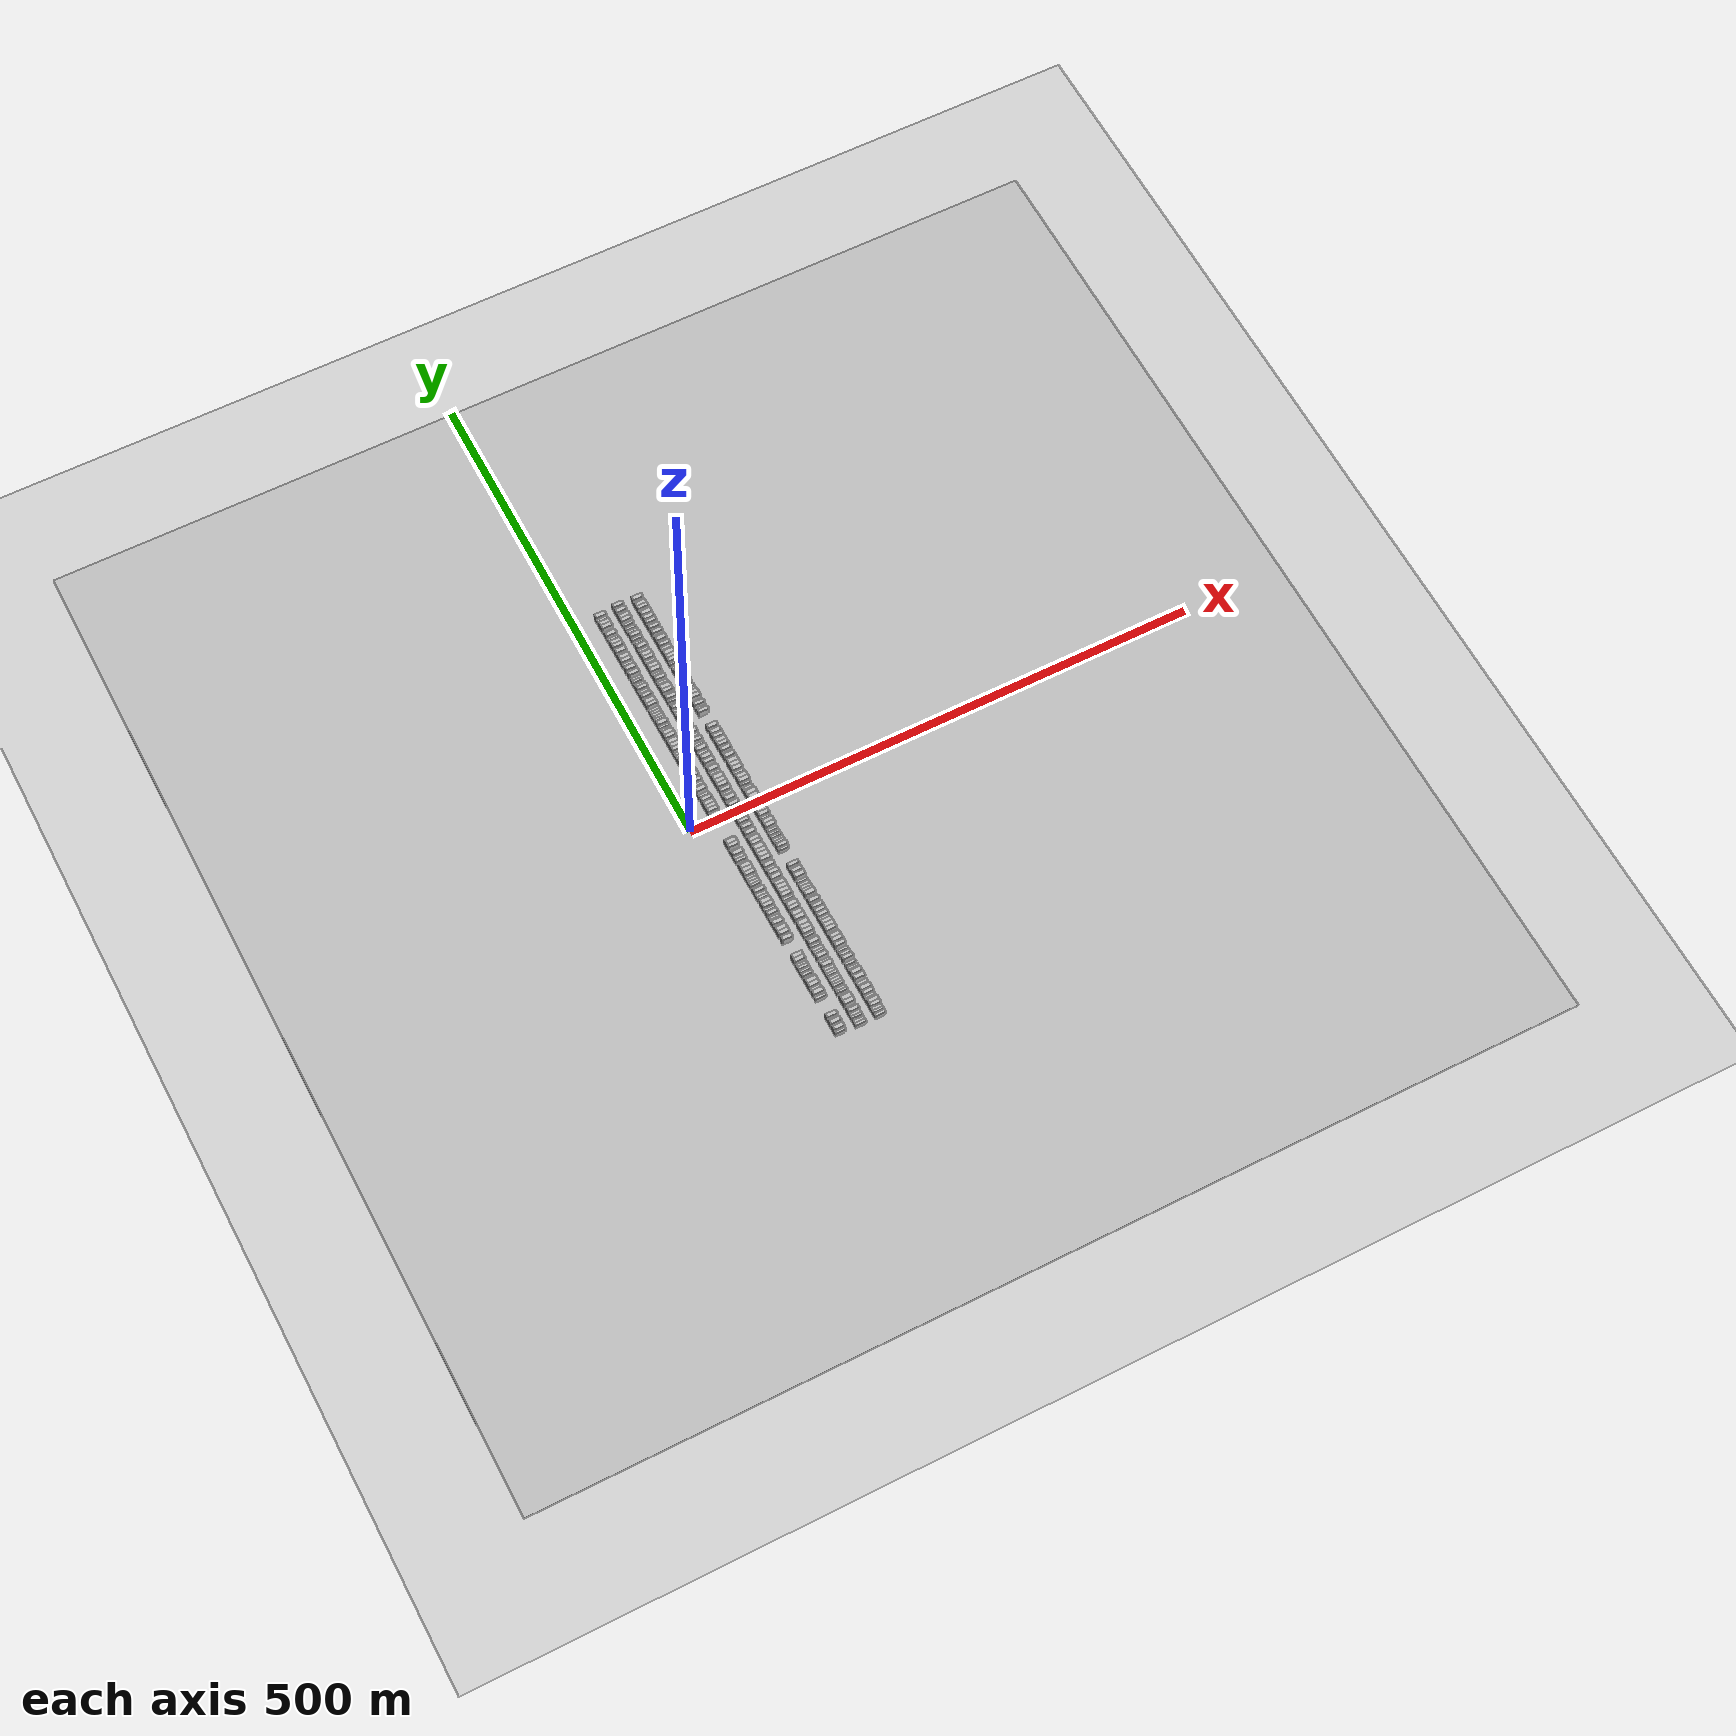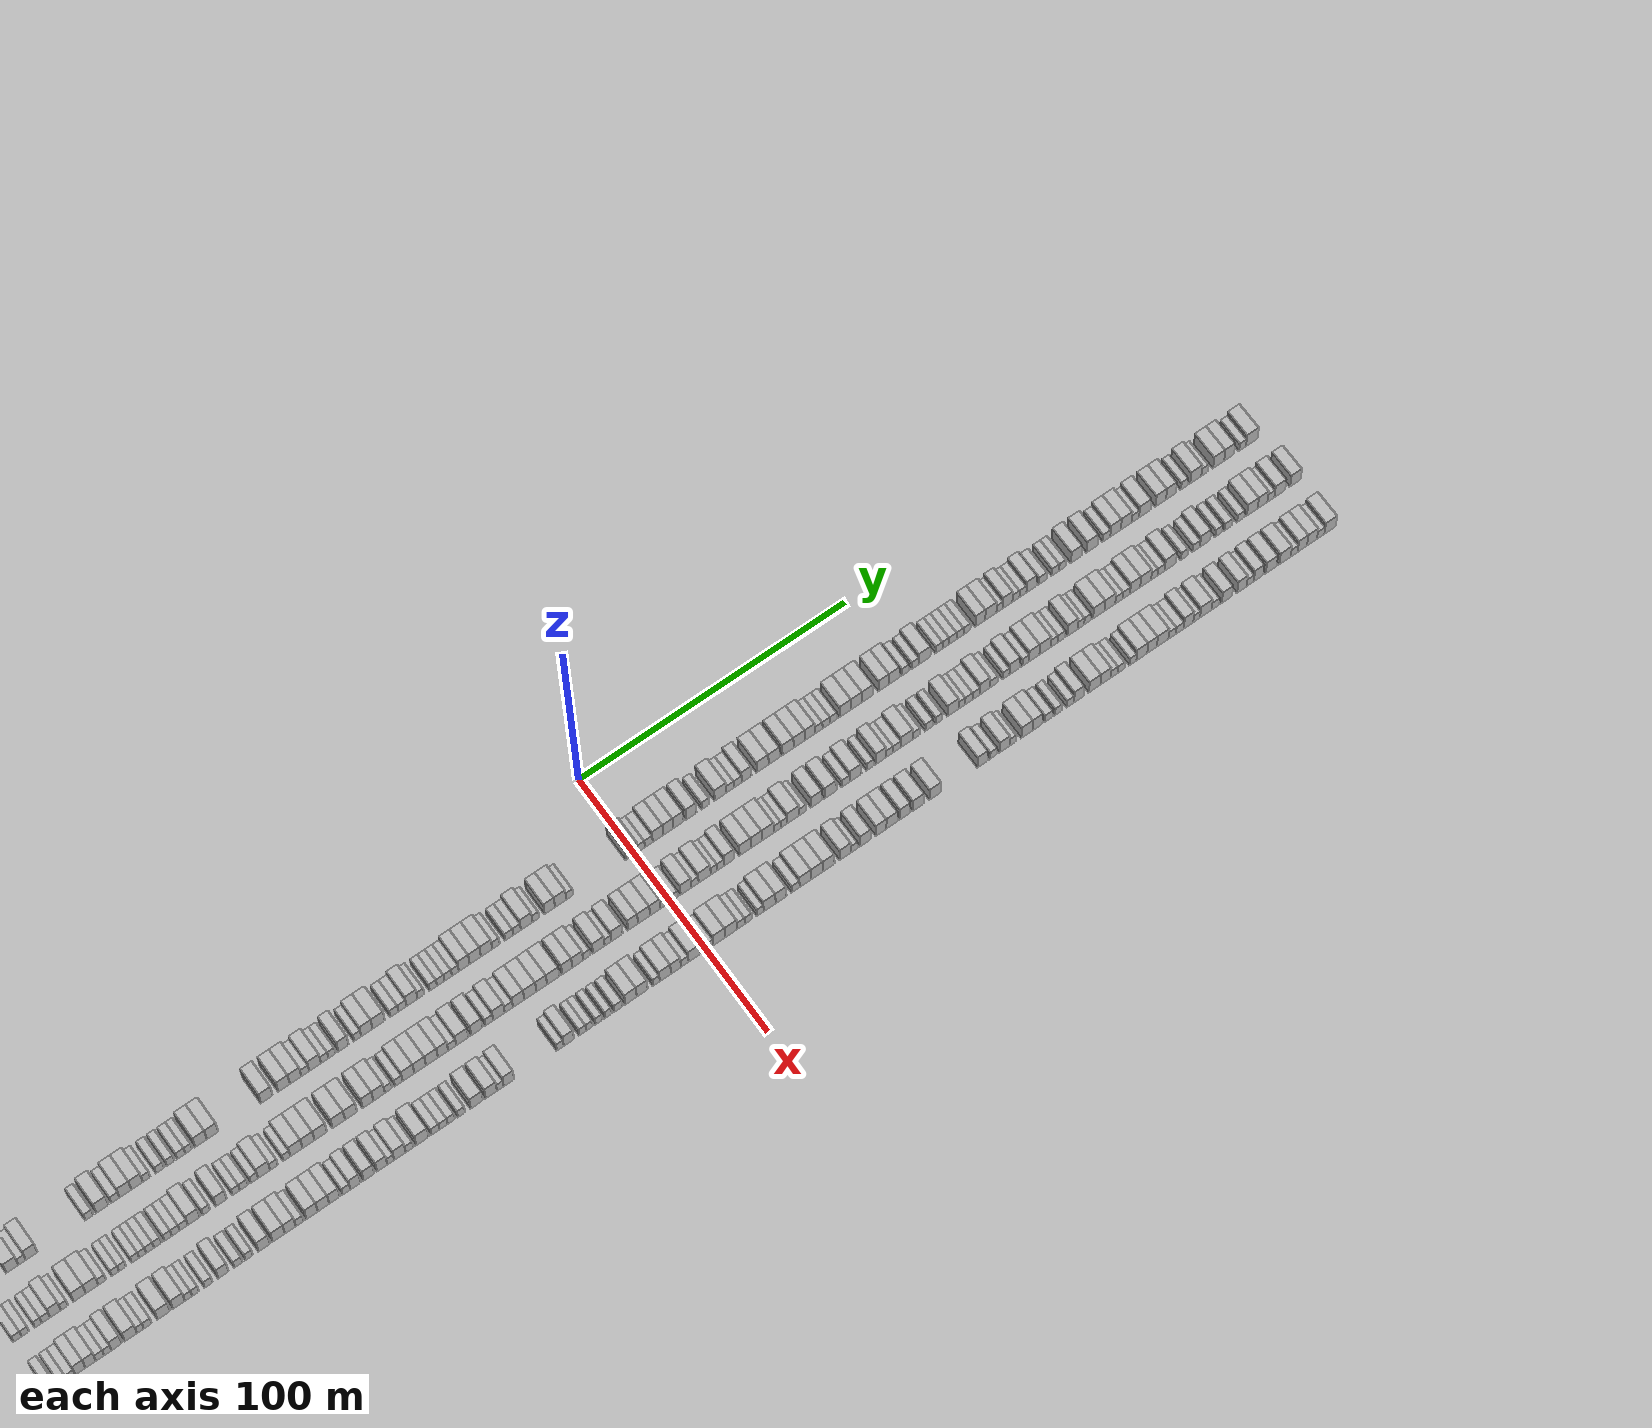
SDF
<?xml version="1.0" encoding="utf-8"?>

<sdf version="1.6">

   <world name="default">

      <gui fullscreen="0">

         <camera name="user_camera">

            <pose>-15 0 4.57585 0 0 0</pose>

            <view_controller>orbit</view_controller>

         </camera>

      </gui>

      <scene>

         <sky>

           <clouds>

             <speed>12</speed>

           </clouds>

         </sky>

         <ambient>0.4 0.4 0.4 1</ambient>

         <background>0.7 0.7 0.7 1</background>

         <shadows>1</shadows>

      </scene>

      <gravity>0 0 -9.8066</gravity>

      <magnetic_field>6e-06 2.3e-05 -4.2e-05</magnetic_field>

      <physics default="0" name="default_physics" type="ode">

         <ode>

            <solver>

               <type>quick</type>

               <iters>10</iters>

               <sor>1.0</sor>

               <use_dynamic_moi_rescaling>0</use_dynamic_moi_rescaling>

            </solver>

            <constraints>

               <cfm>0</cfm>

               <erp>0.2</erp>

               <contact_max_correcting_vel>100</contact_max_correcting_vel>

               <contact_surface_layer>0.001</contact_surface_layer>

            </constraints>

         </ode>

         <max_step_size>0.004</max_step_size>

         <real_time_factor>1</real_time_factor>

         <real_time_update_rate>250</real_time_update_rate>

      </physics>

      <light name="sun" type="directional">

         <cast_shadows>1</cast_shadows>

         <pose>0 0 10 0 0 0</pose>

         <diffuse>0.8 0.8 0.8 1</diffuse>

         <specular>0.2 0.2 0.2 1</specular>

         <attenuation>

            <range>1000</range>

            <constant>0.9</constant>

            <linear>0.01</linear>

            <quadratic>0.001</quadratic>

         </attenuation>

         <direction>-0.5 0.1 -0.9</direction>

      </light>

      <include>

         <name>ground_plane_1</name>

         <uri>model://HANNAS_ground_plane</uri>

         <pose>0 0 0  0 0 0</pose>

      </include>

      <include>

         <name>ground_plane_2</name>

         <uri>model://HANNAS_ground_plane</uri>

         <pose>100 0 0  0 0 0</pose>

      </include>

      <model name="building_1">

         <static>1</static>

         <pose frame="">25.0000 -233.6905 0 0.000000 0.000000 0.000000</pose>

         <link name="link">

            <pose frame="">0 0 3.00 0 0 0</pose>

            <collision name="collision">

               <geometry>

                  <box>

                     <size>10.0000 2.6191 6.0000</size>

                  </box>

               </geometry>

               <max_contacts>10</max_contacts>

               <surface>

                  <contact>

                     <ode/>

                  </contact>

                  <bounce/>

                  <friction>

                     <torsional>

                        <ode/>

                     </torsional>

                     <ode/>

                  </friction>

               </surface>

            </collision>

            <visual name="visual">

               <cast_shadows>0</cast_shadows>

               <geometry>

                  <box>

                     <size>10.0000 2.6191 6.0000</size>

                  </box>

               </geometry>

               <material>

                  <script>

                     <uri>model://HANNAS_wall/materials/scripts</uri>

                     <uri>model://HANNAS_wall/materials/textures</uri>

                     <name>vrc/HANNAS_wall</name>

                  </script>

               </material>

            </visual>

            <self_collide>0</self_collide>

            <enable_wind>0</enable_wind>

            <kinematic>0</kinematic>

         </link>

      </model>

      <model name="building_2">

         <static>1</static>

         <pose frame="">25.0000 -230.3405 0 0.000000 0.000000 0.000000</pose>

         <link name="link">

            <pose frame="">0 0 4.50 0 0 0</pose>

            <collision name="collision">

               <geometry>

                  <box>

                     <size>10.0000 4.0808 9.0000</size>

                  </box>

               </geometry>

               <max_contacts>10</max_contacts>

               <surface>

                  <contact>

                     <ode/>

                  </contact>

                  <bounce/>

                  <friction>

                     <torsional>

                        <ode/>

                     </torsional>

                     <ode/>

                  </friction>

               </surface>

            </collision>

            <visual name="visual">

               <cast_shadows>0</cast_shadows>

               <geometry>

                  <box>

                     <size>10.0000 4.0808 9.0000</size>

                  </box>

               </geometry>

               <material>

                  <script>

                     <uri>model://HANNAS_wall/materials/scripts</uri>

                     <uri>model://HANNAS_wall/materials/textures</uri>

                     <name>vrc/HANNAS_wall</name>

                  </script>

               </material>

            </visual>

            <self_collide>0</self_collide>

            <enable_wind>0</enable_wind>

            <kinematic>0</kinematic>

         </link>

      </model>

      <model name="building_3">

         <static>1</static>

         <pose frame="">25.0000 -224.1936 0 0.000000 0.000000 0.000000</pose>

         <link name="link">

            <pose frame="">0 0 4.50 0 0 0</pose>

            <collision name="collision">

               <geometry>

                  <box>

                     <size>10.0000 4.2132 9.0000</size>

                  </box>

               </geometry>

               <max_contacts>10</max_contacts>

               <surface>

                  <contact>

                     <ode/>

                  </contact>

                  <bounce/>

                  <friction>

                     <torsional>

                        <ode/>

                     </torsional>

                     <ode/>

                  </friction>

               </surface>

            </collision>

            <visual name="visual">

               <cast_shadows>0</cast_shadows>

               <geometry>

                  <box>

                     <size>10.0000 4.2132 9.0000</size>

                  </box>

               </geometry>

               <material>

                  <script>

                     <uri>model://HANNAS_wall/materials/scripts</uri>

                     <uri>model://HANNAS_wall/materials/textures</uri>

                     <name>vrc/HANNAS_wall</name>

                  </script>

               </material>

            </visual>

            <self_collide>0</self_collide>

            <enable_wind>0</enable_wind>

            <kinematic>0</kinematic>

         </link>

      </model>

      <model name="building_4">

         <static>1</static>

         <pose frame="">25.0000 -220.7841 0 0.000000 0.000000 0.000000</pose>

         <link name="link">

            <pose frame="">0 0 3.00 0 0 0</pose>

            <collision name="collision">

               <geometry>

                  <box>

                     <size>10.0000 2.6057 6.0000</size>

                  </box>

               </geometry>

               <max_contacts>10</max_contacts>

               <surface>

                  <contact>

                     <ode/>

                  </contact>

                  <bounce/>

                  <friction>

                     <torsional>

                        <ode/>

                     </torsional>

                     <ode/>

                  </friction>

               </surface>

            </collision>

            <visual name="visual">

               <cast_shadows>0</cast_shadows>

               <geometry>

                  <box>

                     <size>10.0000 2.6057 6.0000</size>

                  </box>

               </geometry>

               <material>

                  <script>

                     <uri>model://HANNAS_wall/materials/scripts</uri>

                     <uri>model://HANNAS_wall/materials/textures</uri>

                     <name>vrc/HANNAS_wall</name>

                  </script>

               </material>

            </visual>

            <self_collide>0</self_collide>

            <enable_wind>0</enable_wind>

            <kinematic>0</kinematic>

         </link>

      </model>

      <model name="building_5">

         <static>1</static>

         <pose frame="">25.0000 -217.4206 0 0.000000 0.000000 0.000000</pose>

         <link name="link">

            <pose frame="">0 0 4.50 0 0 0</pose>

            <collision name="collision">

               <geometry>

                  <box>

                     <size>10.0000 4.1213 9.0000</size>

                  </box>

               </geometry>

               <max_contacts>10</max_contacts>

               <surface>

                  <contact>

                     <ode/>

                  </contact>

                  <bounce/>

                  <friction>

                     <torsional>

                        <ode/>

                     </torsional>

                     <ode/>

                  </friction>

               </surface>

            </collision>

            <visual name="visual">

               <cast_shadows>0</cast_shadows>

               <geometry>

                  <box>

                     <size>10.0000 4.1213 9.0000</size>

                  </box>

               </geometry>

               <material>

                  <script>

                     <uri>model://HANNAS_wall/materials/scripts</uri>

                     <uri>model://HANNAS_wall/materials/textures</uri>

                     <name>vrc/HANNAS_wall</name>

                  </script>

               </material>

            </visual>

            <self_collide>0</self_collide>

            <enable_wind>0</enable_wind>

            <kinematic>0</kinematic>

         </link>

      </model>

      <model name="building_6">

         <static>1</static>

         <pose frame="">25.0000 -197.1147 0 0.000000 0.000000 0.000000</pose>

         <link name="link">

            <pose frame="">0 0 3.00 0 0 0</pose>

            <collision name="collision">

               <geometry>

                  <box>

                     <size>10.0000 2.8301 6.0000</size>

                  </box>

               </geometry>

               <max_contacts>10</max_contacts>

               <surface>

                  <contact>

                     <ode/>

                  </contact>

                  <bounce/>

                  <friction>

                     <torsional>

                        <ode/>

                     </torsional>

                     <ode/>

                  </friction>

               </surface>

            </collision>

            <visual name="visual">

               <cast_shadows>0</cast_shadows>

               <geometry>

                  <box>

                     <size>10.0000 2.8301 6.0000</size>

                  </box>

               </geometry>

               <material>

                  <script>

                     <uri>model://HANNAS_wall/materials/scripts</uri>

                     <uri>model://HANNAS_wall/materials/textures</uri>

                     <name>vrc/HANNAS_wall</name>

                  </script>

               </material>

            </visual>

            <self_collide>0</self_collide>

            <enable_wind>0</enable_wind>

            <kinematic>0</kinematic>

         </link>

      </model>

      <model name="building_7">

         <static>1</static>

         <pose frame="">25.0000 -192.5111 0 0.000000 0.000000 0.000000</pose>

         <link name="link">

            <pose frame="">0 0 4.50 0 0 0</pose>

            <collision name="collision">

               <geometry>

                  <box>

                     <size>10.0000 4.3771 9.0000</size>

                  </box>

               </geometry>

               <max_contacts>10</max_contacts>

               <surface>

                  <contact>

                     <ode/>

                  </contact>

                  <bounce/>

                  <friction>

                     <torsional>

                        <ode/>

                     </torsional>

                     <ode/>

                  </friction>

               </surface>

            </collision>

            <visual name="visual">

               <cast_shadows>0</cast_shadows>

               <geometry>

                  <box>

                     <size>10.0000 4.3771 9.0000</size>

                  </box>

               </geometry>

               <material>

                  <script>

                     <uri>model://HANNAS_wall/materials/scripts</uri>

                     <uri>model://HANNAS_wall/materials/textures</uri>

                     <name>vrc/HANNAS_wall</name>

                  </script>

               </material>

            </visual>

            <self_collide>0</self_collide>

            <enable_wind>0</enable_wind>

            <kinematic>0</kinematic>

         </link>

      </model>

      <model name="building_8">

         <static>1</static>

         <pose frame="">25.0000 -187.8634 0 0.000000 0.000000 0.000000</pose>

         <link name="link">

            <pose frame="">0 0 3.00 0 0 0</pose>

            <collision name="collision">

               <geometry>

                  <box>

                     <size>10.0000 2.9183 6.0000</size>

                  </box>

               </geometry>

               <max_contacts>10</max_contacts>

               <surface>

                  <contact>

                     <ode/>

                  </contact>

                  <bounce/>

                  <friction>

                     <torsional>

                        <ode/>

                     </torsional>

                     <ode/>

                  </friction>

               </surface>

            </collision>

            <visual name="visual">

               <cast_shadows>0</cast_shadows>

               <geometry>

                  <box>

                     <size>10.0000 2.9183 6.0000</size>

                  </box>

               </geometry>

               <material>

                  <script>

                     <uri>model://HANNAS_wall/materials/scripts</uri>

                     <uri>model://HANNAS_wall/materials/textures</uri>

                     <name>vrc/HANNAS_wall</name>

                  </script>

               </material>

            </visual>

            <self_collide>0</self_collide>

            <enable_wind>0</enable_wind>

            <kinematic>0</kinematic>

         </link>

      </model>

      <model name="building_9">

         <static>1</static>

         <pose frame="">25.0000 -184.3366 0 0.000000 0.000000 0.000000</pose>

         <link name="link">

            <pose frame="">0 0 4.50 0 0 0</pose>

            <collision name="collision">

               <geometry>

                  <box>

                     <size>10.0000 4.1352 9.0000</size>

                  </box>

               </geometry>

               <max_contacts>10</max_contacts>

               <surface>

                  <contact>

                     <ode/>

                  </contact>

                  <bounce/>

                  <friction>

                     <torsional>

                        <ode/>

                     </torsional>

                     <ode/>

                  </friction>

               </surface>

            </collision>

            <visual name="visual">

               <cast_shadows>0</cast_shadows>

               <geometry>

                  <box>

                     <size>10.0000 4.1352 9.0000</size>

                  </box>

               </geometry>

               <material>

                  <script>

                     <uri>model://HANNAS_wall/materials/scripts</uri>

                     <uri>model://HANNAS_wall/materials/textures</uri>

                     <name>vrc/HANNAS_wall</name>

                  </script>

               </material>

            </visual>

            <self_collide>0</self_collide>

            <enable_wind>0</enable_wind>

            <kinematic>0</kinematic>

         </link>

      </model>

      <model name="building_10">

         <static>1</static>

         <pose frame="">25.0000 -180.2324 0 0.000000 0.000000 0.000000</pose>

         <link name="link">

            <pose frame="">0 0 4.50 0 0 0</pose>

            <collision name="collision">

               <geometry>

                  <box>

                     <size>10.0000 4.0733 9.0000</size>

                  </box>

               </geometry>

               <max_contacts>10</max_contacts>

               <surface>

                  <contact>

                     <ode/>

                  </contact>

                  <bounce/>

                  <friction>

                     <torsional>

                        <ode/>

                     </torsional>

                     <ode/>

                  </friction>

               </surface>

            </collision>

            <visual name="visual">

               <cast_shadows>0</cast_shadows>

               <geometry>

                  <box>

                     <size>10.0000 4.0733 9.0000</size>

                  </box>

               </geometry>

               <material>

                  <script>

                     <uri>model://HANNAS_wall/materials/scripts</uri>

                     <uri>model://HANNAS_wall/materials/textures</uri>

                     <name>vrc/HANNAS_wall</name>

                  </script>

               </material>

            </visual>

            <self_collide>0</self_collide>

            <enable_wind>0</enable_wind>

            <kinematic>0</kinematic>

         </link>

      </model>

      <model name="building_11">

         <static>1</static>

         <pose frame="">25.0000 -176.8551 0 0.000000 0.000000 0.000000</pose>

         <link name="link">

            <pose frame="">0 0 3.00 0 0 0</pose>

            <collision name="collision">

               <geometry>

                  <box>

                     <size>10.0000 2.6815 6.0000</size>

                  </box>

               </geometry>

               <max_contacts>10</max_contacts>

               <surface>

                  <contact>

                     <ode/>

                  </contact>

                  <bounce/>

                  <friction>

                     <torsional>

                        <ode/>

                     </torsional>

                     <ode/>

                  </friction>

               </surface>

            </collision>

            <visual name="visual">

               <cast_shadows>0</cast_shadows>

               <geometry>

                  <box>

                     <size>10.0000 2.6815 6.0000</size>

                  </box>

               </geometry>

               <material>

                  <script>

                     <uri>model://HANNAS_wall/materials/scripts</uri>

                     <uri>model://HANNAS_wall/materials/textures</uri>

                     <name>vrc/HANNAS_wall</name>

                  </script>

               </material>

            </visual>

            <self_collide>0</self_collide>

            <enable_wind>0</enable_wind>

            <kinematic>0</kinematic>

         </link>

      </model>

      <model name="building_12">

         <static>1</static>

         <pose frame="">25.0000 -172.0739 0 0.000000 0.000000 0.000000</pose>

         <link name="link">

            <pose frame="">0 0 3.00 0 0 0</pose>

            <collision name="collision">

               <geometry>

                  <box>

                     <size>10.0000 2.8810 6.0000</size>

                  </box>

               </geometry>

               <max_contacts>10</max_contacts>

               <surface>

                  <contact>

                     <ode/>

                  </contact>

                  <bounce/>

                  <friction>

                     <torsional>

                        <ode/>

                     </torsional>

                     <ode/>

                  </friction>

               </surface>

            </collision>

            <visual name="visual">

               <cast_shadows>0</cast_shadows>

               <geometry>

                  <box>

                     <size>10.0000 2.8810 6.0000</size>

                  </box>

               </geometry>

               <material>

                  <script>

                     <uri>model://HANNAS_wall/materials/scripts</uri>

                     <uri>model://HANNAS_wall/materials/textures</uri>

                     <name>vrc/HANNAS_wall</name>

                  </script>

               </material>

            </visual>

            <self_collide>0</self_collide>

            <enable_wind>0</enable_wind>

            <kinematic>0</kinematic>

         </link>

      </model>

      <model name="building_13">

         <static>1</static>

         <pose frame="">25.0000 -168.3098 0 0.000000 0.000000 0.000000</pose>

         <link name="link">

            <pose frame="">0 0 3.00 0 0 0</pose>

            <collision name="collision">

               <geometry>

                  <box>

                     <size>10.0000 2.6472 6.0000</size>

                  </box>

               </geometry>

               <max_contacts>10</max_contacts>

               <surface>

                  <contact>

                     <ode/>

                  </contact>

                  <bounce/>

                  <friction>

                     <torsional>

                        <ode/>

                     </torsional>

                     <ode/>

                  </friction>

               </surface>

            </collision>

            <visual name="visual">

               <cast_shadows>0</cast_shadows>

               <geometry>

                  <box>

                     <size>10.0000 2.6472 6.0000</size>

                  </box>

               </geometry>

               <material>

                  <script>

                     <uri>model://HANNAS_wall/materials/scripts</uri>

                     <uri>model://HANNAS_wall/materials/textures</uri>

                     <name>vrc/HANNAS_wall</name>

                  </script>

               </material>

            </visual>

            <self_collide>0</self_collide>

            <enable_wind>0</enable_wind>

            <kinematic>0</kinematic>

         </link>

      </model>

      <model name="building_14">

         <static>1</static>

         <pose frame="">25.0000 -164.5237 0 0.000000 0.000000 0.000000</pose>

         <link name="link">

            <pose frame="">0 0 3.00 0 0 0</pose>

            <collision name="collision">

               <geometry>

                  <box>

                     <size>10.0000 2.9249 6.0000</size>

                  </box>

               </geometry>

               <max_contacts>10</max_contacts>

               <surface>

                  <contact>

                     <ode/>

                  </contact>

                  <bounce/>

                  <friction>

                     <torsional>

                        <ode/>

                     </torsional>

                     <ode/>

                  </friction>

               </surface>

            </collision>

            <visual name="visual">

               <cast_shadows>0</cast_shadows>

               <geometry>

                  <box>

                     <size>10.0000 2.9249 6.0000</size>

                  </box>

               </geometry>

               <material>

                  <script>

                     <uri>model://HANNAS_wall/materials/scripts</uri>

                     <uri>model://HANNAS_wall/materials/textures</uri>

                     <name>vrc/HANNAS_wall</name>

                  </script>

               </material>

            </visual>

            <self_collide>0</self_collide>

            <enable_wind>0</enable_wind>

            <kinematic>0</kinematic>

         </link>

      </model>

      <model name="building_15">

         <static>1</static>

         <pose frame="">25.0000 -161.8394 0 0.000000 0.000000 0.000000</pose>

         <link name="link">

            <pose frame="">0 0 3.00 0 0 0</pose>

            <collision name="collision">

               <geometry>

                  <box>

                     <size>10.0000 2.4438 6.0000</size>

                  </box>

               </geometry>

               <max_contacts>10</max_contacts>

               <surface>

                  <contact>

                     <ode/>

                  </contact>

                  <bounce/>

                  <friction>

                     <torsional>

                        <ode/>

                     </torsional>

                     <ode/>

                  </friction>

               </surface>

            </collision>

            <visual name="visual">

               <cast_shadows>0</cast_shadows>

               <geometry>

                  <box>

                     <size>10.0000 2.4438 6.0000</size>

                  </box>

               </geometry>

               <material>

                  <script>

                     <uri>model://HANNAS_wall/materials/scripts</uri>

                     <uri>model://HANNAS_wall/materials/textures</uri>

                     <name>vrc/HANNAS_wall</name>

                  </script>

               </material>

            </visual>

            <self_collide>0</self_collide>

            <enable_wind>0</enable_wind>

            <kinematic>0</kinematic>

         </link>

      </model>

      <model name="building_16">

         <static>1</static>

         <pose frame="">25.0000 -157.5188 0 0.000000 0.000000 0.000000</pose>

         <link name="link">

            <pose frame="">0 0 4.50 0 0 0</pose>

            <collision name="collision">

               <geometry>

                  <box>

                     <size>10.0000 4.1973 9.0000</size>

                  </box>

               </geometry>

               <max_contacts>10</max_contacts>

               <surface>

                  <contact>

                     <ode/>

                  </contact>

                  <bounce/>

                  <friction>

                     <torsional>

                        <ode/>

                     </torsional>

                     <ode/>

                  </friction>

               </surface>

            </collision>

            <visual name="visual">

               <cast_shadows>0</cast_shadows>

               <geometry>

                  <box>

                     <size>10.0000 4.1973 9.0000</size>

                  </box>

               </geometry>

               <material>

                  <script>

                     <uri>model://HANNAS_wall/materials/scripts</uri>

                     <uri>model://HANNAS_wall/materials/textures</uri>

                     <name>vrc/HANNAS_wall</name>

                  </script>

               </material>

            </visual>

            <self_collide>0</self_collide>

            <enable_wind>0</enable_wind>

            <kinematic>0</kinematic>

         </link>

      </model>

      <model name="building_17">

         <static>1</static>

         <pose frame="">25.0000 -153.3816 0 0.000000 0.000000 0.000000</pose>

         <link name="link">

            <pose frame="">0 0 4.50 0 0 0</pose>

            <collision name="collision">

               <geometry>

                  <box>

                     <size>10.0000 4.0772 9.0000</size>

                  </box>

               </geometry>

               <max_contacts>10</max_contacts>

               <surface>

                  <contact>

                     <ode/>

                  </contact>

                  <bounce/>

                  <friction>

                     <torsional>

                        <ode/>

                     </torsional>

                     <ode/>

                  </friction>

               </surface>

            </collision>

            <visual name="visual">

               <cast_shadows>0</cast_shadows>

               <geometry>

                  <box>

                     <size>10.0000 4.0772 9.0000</size>

                  </box>

               </geometry>

               <material>

                  <script>

                     <uri>model://HANNAS_wall/materials/scripts</uri>

                     <uri>model://HANNAS_wall/materials/textures</uri>

                     <name>vrc/HANNAS_wall</name>

                  </script>

               </material>

            </visual>

            <self_collide>0</self_collide>

            <enable_wind>0</enable_wind>

            <kinematic>0</kinematic>

         </link>

      </model>

      <model name="building_18">

         <static>1</static>

         <pose frame="">25.0000 -134.0115 0 0.000000 0.000000 0.000000</pose>

         <link name="link">

            <pose frame="">0 0 4.50 0 0 0</pose>

            <collision name="collision">

               <geometry>

                  <box>

                     <size>10.0000 4.2210 9.0000</size>

                  </box>

               </geometry>

               <max_contacts>10</max_contacts>

               <surface>

                  <contact>

                     <ode/>

                  </contact>

                  <bounce/>

                  <friction>

                     <torsional>

                        <ode/>

                     </torsional>

                     <ode/>

                  </friction>

               </surface>

            </collision>

            <visual name="visual">

               <cast_shadows>0</cast_shadows>

               <geometry>

                  <box>

                     <size>10.0000 4.2210 9.0000</size>

                  </box>

               </geometry>

               <material>

                  <script>

                     <uri>model://HANNAS_wall/materials/scripts</uri>

                     <uri>model://HANNAS_wall/materials/textures</uri>

                     <name>vrc/HANNAS_wall</name>

                  </script>

               </material>

            </visual>

            <self_collide>0</self_collide>

            <enable_wind>0</enable_wind>

            <kinematic>0</kinematic>

         </link>

      </model>

      <model name="building_19">

         <static>1</static>

         <pose frame="">25.0000 -127.8143 0 0.000000 0.000000 0.000000</pose>

         <link name="link">

            <pose frame="">0 0 4.50 0 0 0</pose>

            <collision name="collision">

               <geometry>

                  <box>

                     <size>10.0000 4.1734 9.0000</size>

                  </box>

               </geometry>

               <max_contacts>10</max_contacts>

               <surface>

                  <contact>

                     <ode/>

                  </contact>

                  <bounce/>

                  <friction>

                     <torsional>

                        <ode/>

                     </torsional>

                     <ode/>

                  </friction>

               </surface>

            </collision>

            <visual name="visual">

               <cast_shadows>0</cast_shadows>

               <geometry>

                  <box>

                     <size>10.0000 4.1734 9.0000</size>

                  </box>

               </geometry>

               <material>

                  <script>

                     <uri>model://HANNAS_wall/materials/scripts</uri>

                     <uri>model://HANNAS_wall/materials/textures</uri>

                     <name>vrc/HANNAS_wall</name>

                  </script>

               </material>

            </visual>

            <self_collide>0</self_collide>

            <enable_wind>0</enable_wind>

            <kinematic>0</kinematic>

         </link>

      </model>

      <model name="building_20">

         <static>1</static>

         <pose frame="">25.0000 -123.6665 0 0.000000 0.000000 0.000000</pose>

         <link name="link">

            <pose frame="">0 0 4.50 0 0 0</pose>

            <collision name="collision">

               <geometry>

                  <box>

                     <size>10.0000 4.1221 9.0000</size>

                  </box>

               </geometry>

               <max_contacts>10</max_contacts>

               <surface>

                  <contact>

                     <ode/>

                  </contact>

                  <bounce/>

                  <friction>

                     <torsional>

                        <ode/>

                     </torsional>

                     <ode/>

                  </friction>

               </surface>

            </collision>

            <visual name="visual">

               <cast_shadows>0</cast_shadows>

               <geometry>

                  <box>

                     <size>10.0000 4.1221 9.0000</size>

                  </box>

               </geometry>

               <material>

                  <script>

                     <uri>model://HANNAS_wall/materials/scripts</uri>

                     <uri>model://HANNAS_wall/materials/textures</uri>

                     <name>vrc/HANNAS_wall</name>

                  </script>

               </material>

            </visual>

            <self_collide>0</self_collide>

            <enable_wind>0</enable_wind>

            <kinematic>0</kinematic>

         </link>

      </model>

      <model name="building_21">

         <static>1</static>

         <pose frame="">25.0000 -120.1904 0 0.000000 0.000000 0.000000</pose>

         <link name="link">

            <pose frame="">0 0 3.00 0 0 0</pose>

            <collision name="collision">

               <geometry>

                  <box>

                     <size>10.0000 2.8301 6.0000</size>

                  </box>

               </geometry>

               <max_contacts>10</max_contacts>

               <surface>

                  <contact>

                     <ode/>

                  </contact>

                  <bounce/>

                  <friction>

                     <torsional>

                        <ode/>

                     </torsional>

                     <ode/>

                  </friction>

               </surface>

            </collision>

            <visual name="visual">

               <cast_shadows>0</cast_shadows>

               <geometry>

                  <box>

                     <size>10.0000 2.8301 6.0000</size>

                  </box>

               </geometry>

               <material>

                  <script>

                     <uri>model://HANNAS_wall/materials/scripts</uri>

                     <uri>model://HANNAS_wall/materials/textures</uri>

                     <name>vrc/HANNAS_wall</name>

                  </script>

               </material>

            </visual>

            <self_collide>0</self_collide>

            <enable_wind>0</enable_wind>

            <kinematic>0</kinematic>

         </link>

      </model>

      <model name="building_22">

         <static>1</static>

         <pose frame="">25.0000 -116.6397 0 0.000000 0.000000 0.000000</pose>

         <link name="link">

            <pose frame="">0 0 4.50 0 0 0</pose>

            <collision name="collision">

               <geometry>

                  <box>

                     <size>10.0000 4.2713 9.0000</size>

                  </box>

               </geometry>

               <max_contacts>10</max_contacts>

               <surface>

                  <contact>

                     <ode/>

                  </contact>

                  <bounce/>

                  <friction>

                     <torsional>

                        <ode/>

                     </torsional>

                     <ode/>

                  </friction>

               </surface>

            </collision>

            <visual name="visual">

               <cast_shadows>0</cast_shadows>

               <geometry>

                  <box>

                     <size>10.0000 4.2713 9.0000</size>

                  </box>

               </geometry>

               <material>

                  <script>

                     <uri>model://HANNAS_wall/materials/scripts</uri>

                     <uri>model://HANNAS_wall/materials/textures</uri>

                     <name>vrc/HANNAS_wall</name>

                  </script>

               </material>

            </visual>

            <self_collide>0</self_collide>

            <enable_wind>0</enable_wind>

            <kinematic>0</kinematic>

         </link>

      </model>

      <model name="building_23">

         <static>1</static>

         <pose frame="">25.0000 -113.1678 0 0.000000 0.000000 0.000000</pose>

         <link name="link">

            <pose frame="">0 0 3.00 0 0 0</pose>

            <collision name="collision">

               <geometry>

                  <box>

                     <size>10.0000 2.6727 6.0000</size>

                  </box>

               </geometry>

               <max_contacts>10</max_contacts>

               <surface>

                  <contact>

                     <ode/>

                  </contact>

                  <bounce/>

                  <friction>

                     <torsional>

                        <ode/>

                     </torsional>

                     <ode/>

                  </friction>

               </surface>

            </collision>

            <visual name="visual">

               <cast_shadows>0</cast_shadows>

               <geometry>

                  <box>

                     <size>10.0000 2.6727 6.0000</size>

                  </box>

               </geometry>

               <material>

                  <script>

                     <uri>model://HANNAS_wall/materials/scripts</uri>

                     <uri>model://HANNAS_wall/materials/textures</uri>

                     <name>vrc/HANNAS_wall</name>

                  </script>

               </material>

            </visual>

            <self_collide>0</self_collide>

            <enable_wind>0</enable_wind>

            <kinematic>0</kinematic>

         </link>

      </model>

      <model name="building_24">

         <static>1</static>

         <pose frame="">25.0000 -110.5505 0 0.000000 0.000000 0.000000</pose>

         <link name="link">

            <pose frame="">0 0 3.00 0 0 0</pose>

            <collision name="collision">

               <geometry>

                  <box>

                     <size>10.0000 2.5619 6.0000</size>

                  </box>

               </geometry>

               <max_contacts>10</max_contacts>

               <surface>

                  <contact>

                     <ode/>

                  </contact>

                  <bounce/>

                  <friction>

                     <torsional>

                        <ode/>

                     </torsional>

                     <ode/>

                  </friction>

               </surface>

            </collision>

            <visual name="visual">

               <cast_shadows>0</cast_shadows>

               <geometry>

                  <box>

                     <size>10.0000 2.5619 6.0000</size>

                  </box>

               </geometry>

               <material>

                  <script>

                     <uri>model://HANNAS_wall/materials/scripts</uri>

                     <uri>model://HANNAS_wall/materials/textures</uri>

                     <name>vrc/HANNAS_wall</name>

                  </script>

               </material>

            </visual>

            <self_collide>0</self_collide>

            <enable_wind>0</enable_wind>

            <kinematic>0</kinematic>

         </link>

      </model>

      <model name="building_25">

         <static>1</static>

         <pose frame="">25.0000 -106.4432 0 0.000000 0.000000 0.000000</pose>

         <link name="link">

            <pose frame="">0 0 4.50 0 0 0</pose>

            <collision name="collision">

               <geometry>

                  <box>

                     <size>10.0000 3.6527 9.0000</size>

                  </box>

               </geometry>

               <max_contacts>10</max_contacts>

               <surface>

                  <contact>

                     <ode/>

                  </contact>

                  <bounce/>

                  <friction>

                     <torsional>

                        <ode/>

                     </torsional>

                     <ode/>

                  </friction>

               </surface>

            </collision>

            <visual name="visual">

               <cast_shadows>0</cast_shadows>

               <geometry>

                  <box>

                     <size>10.0000 3.6527 9.0000</size>

                  </box>

               </geometry>

               <material>

                  <script>

                     <uri>model://HANNAS_wall/materials/scripts</uri>

                     <uri>model://HANNAS_wall/materials/textures</uri>

                     <name>vrc/HANNAS_wall</name>

                  </script>

               </material>

            </visual>

            <self_collide>0</self_collide>

            <enable_wind>0</enable_wind>

            <kinematic>0</kinematic>

         </link>

      </model>

      <model name="building_26">

         <static>1</static>

         <pose frame="">25.0000 -101.3097 0 0.000000 0.000000 0.000000</pose>

         <link name="link">

            <pose frame="">0 0 3.00 0 0 0</pose>

            <collision name="collision">

               <geometry>

                  <box>

                     <size>10.0000 2.6143 6.0000</size>

                  </box>

               </geometry>

               <max_contacts>10</max_contacts>

               <surface>

                  <contact>

                     <ode/>

                  </contact>

                  <bounce/>

                  <friction>

                     <torsional>

                        <ode/>

                     </torsional>

                     <ode/>

                  </friction>

               </surface>

            </collision>

            <visual name="visual">

               <cast_shadows>0</cast_shadows>

               <geometry>

                  <box>

                     <size>10.0000 2.6143 6.0000</size>

                  </box>

               </geometry>

               <material>

                  <script>

                     <uri>model://HANNAS_wall/materials/scripts</uri>

                     <uri>model://HANNAS_wall/materials/textures</uri>

                     <name>vrc/HANNAS_wall</name>

                  </script>

               </material>

            </visual>

            <self_collide>0</self_collide>

            <enable_wind>0</enable_wind>

            <kinematic>0</kinematic>

         </link>

      </model>

      <model name="building_27">

         <static>1</static>

         <pose frame="">25.0000 -97.9586 0 0.000000 0.000000 0.000000</pose>

         <link name="link">

            <pose frame="">0 0 4.50 0 0 0</pose>

            <collision name="collision">

               <geometry>

                  <box>

                     <size>10.0000 4.0878 9.0000</size>

                  </box>

               </geometry>

               <max_contacts>10</max_contacts>

               <surface>

                  <contact>

                     <ode/>

                  </contact>

                  <bounce/>

                  <friction>

                     <torsional>

                        <ode/>

                     </torsional>

                     <ode/>

                  </friction>

               </surface>

            </collision>

            <visual name="visual">

               <cast_shadows>0</cast_shadows>

               <geometry>

                  <box>

                     <size>10.0000 4.0878 9.0000</size>

                  </box>

               </geometry>

               <material>

                  <script>

                     <uri>model://HANNAS_wall/materials/scripts</uri>

                     <uri>model://HANNAS_wall/materials/textures</uri>

                     <name>vrc/HANNAS_wall</name>

                  </script>

               </material>

            </visual>

            <self_collide>0</self_collide>

            <enable_wind>0</enable_wind>

            <kinematic>0</kinematic>

         </link>

      </model>

      <model name="building_28">

         <static>1</static>

         <pose frame="">25.0000 -93.7101 0 0.000000 0.000000 0.000000</pose>

         <link name="link">

            <pose frame="">0 0 4.50 0 0 0</pose>

            <collision name="collision">

               <geometry>

                  <box>

                     <size>10.0000 4.4091 9.0000</size>

                  </box>

               </geometry>

               <max_contacts>10</max_contacts>

               <surface>

                  <contact>

                     <ode/>

                  </contact>

                  <bounce/>

                  <friction>

                     <torsional>

                        <ode/>

                     </torsional>

                     <ode/>

                  </friction>

               </surface>

            </collision>

            <visual name="visual">

               <cast_shadows>0</cast_shadows>

               <geometry>

                  <box>

                     <size>10.0000 4.4091 9.0000</size>

                  </box>

               </geometry>

               <material>

                  <script>

                     <uri>model://HANNAS_wall/materials/scripts</uri>

                     <uri>model://HANNAS_wall/materials/textures</uri>

                     <name>vrc/HANNAS_wall</name>

                  </script>

               </material>

            </visual>

            <self_collide>0</self_collide>

            <enable_wind>0</enable_wind>

            <kinematic>0</kinematic>

         </link>

      </model>

      <model name="building_29">

         <static>1</static>

         <pose frame="">25.0000 -88.0533 0 0.000000 0.000000 0.000000</pose>

         <link name="link">

            <pose frame="">0 0 3.00 0 0 0</pose>

            <collision name="collision">

               <geometry>

                  <box>

                     <size>10.0000 2.9044 6.0000</size>

                  </box>

               </geometry>

               <max_contacts>10</max_contacts>

               <surface>

                  <contact>

                     <ode/>

                  </contact>

                  <bounce/>

                  <friction>

                     <torsional>

                        <ode/>

                     </torsional>

                     <ode/>

                  </friction>

               </surface>

            </collision>

            <visual name="visual">

               <cast_shadows>0</cast_shadows>

               <geometry>

                  <box>

                     <size>10.0000 2.9044 6.0000</size>

                  </box>

               </geometry>

               <material>

                  <script>

                     <uri>model://HANNAS_wall/materials/scripts</uri>

                     <uri>model://HANNAS_wall/materials/textures</uri>

                     <name>vrc/HANNAS_wall</name>

                  </script>

               </material>

            </visual>

            <self_collide>0</self_collide>

            <enable_wind>0</enable_wind>

            <kinematic>0</kinematic>

         </link>

      </model>

      <model name="building_30">

         <static>1</static>

         <pose frame="">25.0000 -85.1096 0 0.000000 0.000000 0.000000</pose>

         <link name="link">

            <pose frame="">0 0 3.00 0 0 0</pose>

            <collision name="collision">

               <geometry>

                  <box>

                     <size>10.0000 2.9830 6.0000</size>

                  </box>

               </geometry>

               <max_contacts>10</max_contacts>

               <surface>

                  <contact>

                     <ode/>

                  </contact>

                  <bounce/>

                  <friction>

                     <torsional>

                        <ode/>

                     </torsional>

                     <ode/>

                  </friction>

               </surface>

            </collision>

            <visual name="visual">

               <cast_shadows>0</cast_shadows>

               <geometry>

                  <box>

                     <size>10.0000 2.9830 6.0000</size>

                  </box>

               </geometry>

               <material>

                  <script>

                     <uri>model://HANNAS_wall/materials/scripts</uri>

                     <uri>model://HANNAS_wall/materials/textures</uri>

                     <name>vrc/HANNAS_wall</name>

                  </script>

               </material>

            </visual>

            <self_collide>0</self_collide>

            <enable_wind>0</enable_wind>

            <kinematic>0</kinematic>

         </link>

      </model>

      <model name="building_31">

         <static>1</static>

         <pose frame="">25.0000 -81.6322 0 0.000000 0.000000 0.000000</pose>

         <link name="link">

            <pose frame="">0 0 4.50 0 0 0</pose>

            <collision name="collision">

               <geometry>

                  <box>

                     <size>10.0000 3.9718 9.0000</size>

                  </box>

               </geometry>

               <max_contacts>10</max_contacts>

               <surface>

                  <contact>

                     <ode/>

                  </contact>

                  <bounce/>

                  <friction>

                     <torsional>

                        <ode/>

                     </torsional>

                     <ode/>

                  </friction>

               </surface>

            </collision>

            <visual name="visual">

               <cast_shadows>0</cast_shadows>

               <geometry>

                  <box>

                     <size>10.0000 3.9718 9.0000</size>

                  </box>

               </geometry>

               <material>

                  <script>

                     <uri>model://HANNAS_wall/materials/scripts</uri>

                     <uri>model://HANNAS_wall/materials/textures</uri>

                     <name>vrc/HANNAS_wall</name>

                  </script>

               </material>

            </visual>

            <self_collide>0</self_collide>

            <enable_wind>0</enable_wind>

            <kinematic>0</kinematic>

         </link>

      </model>

      <model name="building_32">

         <static>1</static>

         <pose frame="">25.0000 -78.4338 0 0.000000 0.000000 0.000000</pose>

         <link name="link">

            <pose frame="">0 0 3.00 0 0 0</pose>

            <collision name="collision">

               <geometry>

                  <box>

                     <size>10.0000 2.4251 6.0000</size>

                  </box>

               </geometry>

               <max_contacts>10</max_contacts>

               <surface>

                  <contact>

                     <ode/>

                  </contact>

                  <bounce/>

                  <friction>

                     <torsional>

                        <ode/>

                     </torsional>

                     <ode/>

                  </friction>

               </surface>

            </collision>

            <visual name="visual">

               <cast_shadows>0</cast_shadows>

               <geometry>

                  <box>

                     <size>10.0000 2.4251 6.0000</size>

                  </box>

               </geometry>

               <material>

                  <script>

                     <uri>model://HANNAS_wall/materials/scripts</uri>

                     <uri>model://HANNAS_wall/materials/textures</uri>

                     <name>vrc/HANNAS_wall</name>

                  </script>

               </material>

            </visual>

            <self_collide>0</self_collide>

            <enable_wind>0</enable_wind>

            <kinematic>0</kinematic>

         </link>

      </model>

      <model name="building_33">

         <static>1</static>

         <pose frame="">25.0000 -73.8960 0 0.000000 0.000000 0.000000</pose>

         <link name="link">

            <pose frame="">0 0 3.00 0 0 0</pose>

            <collision name="collision">

               <geometry>

                  <box>

                     <size>10.0000 2.6504 6.0000</size>

                  </box>

               </geometry>

               <max_contacts>10</max_contacts>

               <surface>

                  <contact>

                     <ode/>

                  </contact>

                  <bounce/>

                  <friction>

                     <torsional>

                        <ode/>

                     </torsional>

                     <ode/>

                  </friction>

               </surface>

            </collision>

            <visual name="visual">

               <cast_shadows>0</cast_shadows>

               <geometry>

                  <box>

                     <size>10.0000 2.6504 6.0000</size>

                  </box>

               </geometry>

               <material>

                  <script>

                     <uri>model://HANNAS_wall/materials/scripts</uri>

                     <uri>model://HANNAS_wall/materials/textures</uri>

                     <name>vrc/HANNAS_wall</name>

                  </script>

               </material>

            </visual>

            <self_collide>0</self_collide>

            <enable_wind>0</enable_wind>

            <kinematic>0</kinematic>

         </link>

      </model>

      <model name="building_34">

         <static>1</static>

         <pose frame="">25.0000 -71.2138 0 0.000000 0.000000 0.000000</pose>

         <link name="link">

            <pose frame="">0 0 3.00 0 0 0</pose>

            <collision name="collision">

               <geometry>

                  <box>

                     <size>10.0000 2.7140 6.0000</size>

                  </box>

               </geometry>

               <max_contacts>10</max_contacts>

               <surface>

                  <contact>

                     <ode/>

                  </contact>

                  <bounce/>

                  <friction>

                     <torsional>

                        <ode/>

                     </torsional>

                     <ode/>

                  </friction>

               </surface>

            </collision>

            <visual name="visual">

               <cast_shadows>0</cast_shadows>

               <geometry>

                  <box>

                     <size>10.0000 2.7140 6.0000</size>

                  </box>

               </geometry>

               <material>

                  <script>

                     <uri>model://HANNAS_wall/materials/scripts</uri>

                     <uri>model://HANNAS_wall/materials/textures</uri>

                     <name>vrc/HANNAS_wall</name>

                  </script>

               </material>

            </visual>

            <self_collide>0</self_collide>

            <enable_wind>0</enable_wind>

            <kinematic>0</kinematic>

         </link>

      </model>

      <model name="building_35">

         <static>1</static>

         <pose frame="">25.0000 -68.5138 0 0.000000 0.000000 0.000000</pose>

         <link name="link">

            <pose frame="">0 0 3.00 0 0 0</pose>

            <collision name="collision">

               <geometry>

                  <box>

                     <size>10.0000 2.6860 6.0000</size>

                  </box>

               </geometry>

               <max_contacts>10</max_contacts>

               <surface>

                  <contact>

                     <ode/>

                  </contact>

                  <bounce/>

                  <friction>

                     <torsional>

                        <ode/>

                     </torsional>

                     <ode/>

                  </friction>

               </surface>

            </collision>

            <visual name="visual">

               <cast_shadows>0</cast_shadows>

               <geometry>

                  <box>

                     <size>10.0000 2.6860 6.0000</size>

                  </box>

               </geometry>

               <material>

                  <script>

                     <uri>model://HANNAS_wall/materials/scripts</uri>

                     <uri>model://HANNAS_wall/materials/textures</uri>

                     <name>vrc/HANNAS_wall</name>

                  </script>

               </material>

            </visual>

            <self_collide>0</self_collide>

            <enable_wind>0</enable_wind>

            <kinematic>0</kinematic>

         </link>

      </model>

      <model name="building_36">

         <static>1</static>

         <pose frame="">25.0000 -65.8898 0 0.000000 0.000000 0.000000</pose>

         <link name="link">

            <pose frame="">0 0 3.00 0 0 0</pose>

            <collision name="collision">

               <geometry>

                  <box>

                     <size>10.0000 2.5622 6.0000</size>

                  </box>

               </geometry>

               <max_contacts>10</max_contacts>

               <surface>

                  <contact>

                     <ode/>

                  </contact>

                  <bounce/>

                  <friction>

                     <torsional>

                        <ode/>

                     </torsional>

                     <ode/>

                  </friction>

               </surface>

            </collision>

            <visual name="visual">

               <cast_shadows>0</cast_shadows>

               <geometry>

                  <box>

                     <size>10.0000 2.5622 6.0000</size>

                  </box>

               </geometry>

               <material>

                  <script>

                     <uri>model://HANNAS_wall/materials/scripts</uri>

                     <uri>model://HANNAS_wall/materials/textures</uri>

                     <name>vrc/HANNAS_wall</name>

                  </script>

               </material>

            </visual>

            <self_collide>0</self_collide>

            <enable_wind>0</enable_wind>

            <kinematic>0</kinematic>

         </link>

      </model>

      <model name="building_37">

         <static>1</static>

         <pose frame="">25.0000 -62.6534 0 0.000000 0.000000 0.000000</pose>

         <link name="link">

            <pose frame="">0 0 4.50 0 0 0</pose>

            <collision name="collision">

               <geometry>

                  <box>

                     <size>10.0000 3.9106 9.0000</size>

                  </box>

               </geometry>

               <max_contacts>10</max_contacts>

               <surface>

                  <contact>

                     <ode/>

                  </contact>

                  <bounce/>

                  <friction>

                     <torsional>

                        <ode/>

                     </torsional>

                     <ode/>

                  </friction>

               </surface>

            </collision>

            <visual name="visual">

               <cast_shadows>0</cast_shadows>

               <geometry>

                  <box>

                     <size>10.0000 3.9106 9.0000</size>

                  </box>

               </geometry>

               <material>

                  <script>

                     <uri>model://HANNAS_wall/materials/scripts</uri>

                     <uri>model://HANNAS_wall/materials/textures</uri>

                     <name>vrc/HANNAS_wall</name>

                  </script>

               </material>

            </visual>

            <self_collide>0</self_collide>

            <enable_wind>0</enable_wind>

            <kinematic>0</kinematic>

         </link>

      </model>

      <model name="building_38">

         <static>1</static>

         <pose frame="">25.0000 -58.6455 0 0.000000 0.000000 0.000000</pose>

         <link name="link">

            <pose frame="">0 0 4.50 0 0 0</pose>

            <collision name="collision">

               <geometry>

                  <box>

                     <size>10.0000 4.1052 9.0000</size>

                  </box>

               </geometry>

               <max_contacts>10</max_contacts>

               <surface>

                  <contact>

                     <ode/>

                  </contact>

                  <bounce/>

                  <friction>

                     <torsional>

                        <ode/>

                     </torsional>

                     <ode/>

                  </friction>

               </surface>

            </collision>

            <visual name="visual">

               <cast_shadows>0</cast_shadows>

               <geometry>

                  <box>

                     <size>10.0000 4.1052 9.0000</size>

                  </box>

               </geometry>

               <material>

                  <script>

                     <uri>model://HANNAS_wall/materials/scripts</uri>

                     <uri>model://HANNAS_wall/materials/textures</uri>

                     <name>vrc/HANNAS_wall</name>

                  </script>

               </material>

            </visual>

            <self_collide>0</self_collide>

            <enable_wind>0</enable_wind>

            <kinematic>0</kinematic>

         </link>

      </model>

      <model name="building_39">

         <static>1</static>

         <pose frame="">25.0000 -54.5191 0 0.000000 0.000000 0.000000</pose>

         <link name="link">

            <pose frame="">0 0 4.50 0 0 0</pose>

            <collision name="collision">

               <geometry>

                  <box>

                     <size>10.0000 4.1475 9.0000</size>

                  </box>

               </geometry>

               <max_contacts>10</max_contacts>

               <surface>

                  <contact>

                     <ode/>

                  </contact>

                  <bounce/>

                  <friction>

                     <torsional>

                        <ode/>

                     </torsional>

                     <ode/>

                  </friction>

               </surface>

            </collision>

            <visual name="visual">

               <cast_shadows>0</cast_shadows>

               <geometry>

                  <box>

                     <size>10.0000 4.1475 9.0000</size>

                  </box>

               </geometry>

               <material>

                  <script>

                     <uri>model://HANNAS_wall/materials/scripts</uri>

                     <uri>model://HANNAS_wall/materials/textures</uri>

                     <name>vrc/HANNAS_wall</name>

                  </script>

               </material>

            </visual>

            <self_collide>0</self_collide>

            <enable_wind>0</enable_wind>

            <kinematic>0</kinematic>

         </link>

      </model>

      <model name="building_40">

         <static>1</static>

         <pose frame="">25.0000 -51.0883 0 0.000000 0.000000 0.000000</pose>

         <link name="link">

            <pose frame="">0 0 3.00 0 0 0</pose>

            <collision name="collision">

               <geometry>

                  <box>

                     <size>10.0000 2.7141 6.0000</size>

                  </box>

               </geometry>

               <max_contacts>10</max_contacts>

               <surface>

                  <contact>

                     <ode/>

                  </contact>

                  <bounce/>

                  <friction>

                     <torsional>

                        <ode/>

                     </torsional>

                     <ode/>

                  </friction>

               </surface>

            </collision>

            <visual name="visual">

               <cast_shadows>0</cast_shadows>

               <geometry>

                  <box>

                     <size>10.0000 2.7141 6.0000</size>

                  </box>

               </geometry>

               <material>

                  <script>

                     <uri>model://HANNAS_wall/materials/scripts</uri>

                     <uri>model://HANNAS_wall/materials/textures</uri>

                     <name>vrc/HANNAS_wall</name>

                  </script>

               </material>

            </visual>

            <self_collide>0</self_collide>

            <enable_wind>0</enable_wind>

            <kinematic>0</kinematic>

         </link>

      </model>

      <model name="building_41">

         <static>1</static>

         <pose frame="">25.0000 -46.2631 0 0.000000 0.000000 0.000000</pose>

         <link name="link">

            <pose frame="">0 0 3.00 0 0 0</pose>

            <collision name="collision">

               <geometry>

                  <box>

                     <size>10.0000 2.9363 6.0000</size>

                  </box>

               </geometry>

               <max_contacts>10</max_contacts>

               <surface>

                  <contact>

                     <ode/>

                  </contact>

                  <bounce/>

                  <friction>

                     <torsional>

                        <ode/>

                     </torsional>

                     <ode/>

                  </friction>

               </surface>

            </collision>

            <visual name="visual">

               <cast_shadows>0</cast_shadows>

               <geometry>

                  <box>

                     <size>10.0000 2.9363 6.0000</size>

                  </box>

               </geometry>

               <material>

                  <script>

                     <uri>model://HANNAS_wall/materials/scripts</uri>

                     <uri>model://HANNAS_wall/materials/textures</uri>

                     <name>vrc/HANNAS_wall</name>

                  </script>

               </material>

            </visual>

            <self_collide>0</self_collide>

            <enable_wind>0</enable_wind>

            <kinematic>0</kinematic>

         </link>

      </model>

      <model name="building_42">

         <static>1</static>

         <pose frame="">25.0000 -43.3785 0 0.000000 0.000000 0.000000</pose>

         <link name="link">

            <pose frame="">0 0 3.00 0 0 0</pose>

            <collision name="collision">

               <geometry>

                  <box>

                     <size>10.0000 2.8329 6.0000</size>

                  </box>

               </geometry>

               <max_contacts>10</max_contacts>

               <surface>

                  <contact>

                     <ode/>

                  </contact>

                  <bounce/>

                  <friction>

                     <torsional>

                        <ode/>

                     </torsional>

                     <ode/>

                  </friction>

               </surface>

            </collision>

            <visual name="visual">

               <cast_shadows>0</cast_shadows>

               <geometry>

                  <box>

                     <size>10.0000 2.8329 6.0000</size>

                  </box>

               </geometry>

               <material>

                  <script>

                     <uri>model://HANNAS_wall/materials/scripts</uri>

                     <uri>model://HANNAS_wall/materials/textures</uri>

                     <name>vrc/HANNAS_wall</name>

                  </script>

               </material>

            </visual>

            <self_collide>0</self_collide>

            <enable_wind>0</enable_wind>

            <kinematic>0</kinematic>

         </link>

      </model>

      <model name="building_43">

         <static>1</static>

         <pose frame="">25.0000 -39.8312 0 0.000000 0.000000 0.000000</pose>

         <link name="link">

            <pose frame="">0 0 4.50 0 0 0</pose>

            <collision name="collision">

               <geometry>

                  <box>

                     <size>10.0000 4.2618 9.0000</size>

                  </box>

               </geometry>

               <max_contacts>10</max_contacts>

               <surface>

                  <contact>

                     <ode/>

                  </contact>

                  <bounce/>

                  <friction>

                     <torsional>

                        <ode/>

                     </torsional>

                     <ode/>

                  </friction>

               </surface>

            </collision>

            <visual name="visual">

               <cast_shadows>0</cast_shadows>

               <geometry>

                  <box>

                     <size>10.0000 4.2618 9.0000</size>

                  </box>

               </geometry>

               <material>

                  <script>

                     <uri>model://HANNAS_wall/materials/scripts</uri>

                     <uri>model://HANNAS_wall/materials/textures</uri>

                     <name>vrc/HANNAS_wall</name>

                  </script>

               </material>

            </visual>

            <self_collide>0</self_collide>

            <enable_wind>0</enable_wind>

            <kinematic>0</kinematic>

         </link>

      </model>

      <model name="building_44">

         <static>1</static>

         <pose frame="">25.0000 -36.4992 0 0.000000 0.000000 0.000000</pose>

         <link name="link">

            <pose frame="">0 0 3.00 0 0 0</pose>

            <collision name="collision">

               <geometry>

                  <box>

                     <size>10.0000 2.4022 6.0000</size>

                  </box>

               </geometry>

               <max_contacts>10</max_contacts>

               <surface>

                  <contact>

                     <ode/>

                  </contact>

                  <bounce/>

                  <friction>

                     <torsional>

                        <ode/>

                     </torsional>

                     <ode/>

                  </friction>

               </surface>

            </collision>

            <visual name="visual">

               <cast_shadows>0</cast_shadows>

               <geometry>

                  <box>

                     <size>10.0000 2.4022 6.0000</size>

                  </box>

               </geometry>

               <material>

                  <script>

                     <uri>model://HANNAS_wall/materials/scripts</uri>

                     <uri>model://HANNAS_wall/materials/textures</uri>

                     <name>vrc/HANNAS_wall</name>

                  </script>

               </material>

            </visual>

            <self_collide>0</self_collide>

            <enable_wind>0</enable_wind>

            <kinematic>0</kinematic>

         </link>

      </model>

      <model name="building_45">

         <static>1</static>

         <pose frame="">25.0000 -31.3882 0 0.000000 0.000000 0.000000</pose>

         <link name="link">

            <pose frame="">0 0 4.50 0 0 0</pose>

            <collision name="collision">

               <geometry>

                  <box>

                     <size>10.0000 3.8198 9.0000</size>

                  </box>

               </geometry>

               <max_contacts>10</max_contacts>

               <surface>

                  <contact>

                     <ode/>

                  </contact>

                  <bounce/>

                  <friction>

                     <torsional>

                        <ode/>

                     </torsional>

                     <ode/>

                  </friction>

               </surface>

            </collision>

            <visual name="visual">

               <cast_shadows>0</cast_shadows>

               <geometry>

                  <box>

                     <size>10.0000 3.8198 9.0000</size>

                  </box>

               </geometry>

               <material>

                  <script>

                     <uri>model://HANNAS_wall/materials/scripts</uri>

                     <uri>model://HANNAS_wall/materials/textures</uri>

                     <name>vrc/HANNAS_wall</name>

                  </script>

               </material>

            </visual>

            <self_collide>0</self_collide>

            <enable_wind>0</enable_wind>

            <kinematic>0</kinematic>

         </link>

      </model>

      <model name="building_46">

         <static>1</static>

         <pose frame="">25.0000 -27.3918 0 0.000000 0.000000 0.000000</pose>

         <link name="link">

            <pose frame="">0 0 4.50 0 0 0</pose>

            <collision name="collision">

               <geometry>

                  <box>

                     <size>10.0000 4.1731 9.0000</size>

                  </box>

               </geometry>

               <max_contacts>10</max_contacts>

               <surface>

                  <contact>

                     <ode/>

                  </contact>

                  <bounce/>

                  <friction>

                     <torsional>

                        <ode/>

                     </torsional>

                     <ode/>

                  </friction>

               </surface>

            </collision>

            <visual name="visual">

               <cast_shadows>0</cast_shadows>

               <geometry>

                  <box>

                     <size>10.0000 4.1731 9.0000</size>

                  </box>

               </geometry>

               <material>

                  <script>

                     <uri>model://HANNAS_wall/materials/scripts</uri>

                     <uri>model://HANNAS_wall/materials/textures</uri>

                     <name>vrc/HANNAS_wall</name>

                  </script>

               </material>

            </visual>

            <self_collide>0</self_collide>

            <enable_wind>0</enable_wind>

            <kinematic>0</kinematic>

         </link>

      </model>

      <model name="building_47">

         <static>1</static>

         <pose frame="">25.0000 -24.0663 0 0.000000 0.000000 0.000000</pose>

         <link name="link">

            <pose frame="">0 0 3.00 0 0 0</pose>

            <collision name="collision">

               <geometry>

                  <box>

                     <size>10.0000 2.4779 6.0000</size>

                  </box>

               </geometry>

               <max_contacts>10</max_contacts>

               <surface>

                  <contact>

                     <ode/>

                  </contact>

                  <bounce/>

                  <friction>

                     <torsional>

                        <ode/>

                     </torsional>

                     <ode/>

                  </friction>

               </surface>

            </collision>

            <visual name="visual">

               <cast_shadows>0</cast_shadows>

               <geometry>

                  <box>

                     <size>10.0000 2.4779 6.0000</size>

                  </box>

               </geometry>

               <material>

                  <script>

                     <uri>model://HANNAS_wall/materials/scripts</uri>

                     <uri>model://HANNAS_wall/materials/textures</uri>

                     <name>vrc/HANNAS_wall</name>

                  </script>

               </material>

            </visual>

            <self_collide>0</self_collide>

            <enable_wind>0</enable_wind>

            <kinematic>0</kinematic>

         </link>

      </model>

      <model name="building_48">

         <static>1</static>

         <pose frame="">25.0000 -1.1884 0 0.000000 0.000000 0.000000</pose>

         <link name="link">

            <pose frame="">0 0 4.50 0 0 0</pose>

            <collision name="collision">

               <geometry>

                  <box>

                     <size>10.0000 4.4260 9.0000</size>

                  </box>

               </geometry>

               <max_contacts>10</max_contacts>

               <surface>

                  <contact>

                     <ode/>

                  </contact>

                  <bounce/>

                  <friction>

                     <torsional>

                        <ode/>

                     </torsional>

                     <ode/>

                  </friction>

               </surface>

            </collision>

            <visual name="visual">

               <cast_shadows>0</cast_shadows>

               <geometry>

                  <box>

                     <size>10.0000 4.4260 9.0000</size>

                  </box>

               </geometry>

               <material>

                  <script>

                     <uri>model://HANNAS_wall/materials/scripts</uri>

                     <uri>model://HANNAS_wall/materials/textures</uri>

                     <name>vrc/HANNAS_wall</name>

                  </script>

               </material>

            </visual>

            <self_collide>0</self_collide>

            <enable_wind>0</enable_wind>

            <kinematic>0</kinematic>

         </link>

      </model>

      <model name="building_49">

         <static>1</static>

         <pose frame="">25.0000 2.3365 0 0.000000 0.000000 0.000000</pose>

         <link name="link">

            <pose frame="">0 0 3.00 0 0 0</pose>

            <collision name="collision">

               <geometry>

                  <box>

                     <size>10.0000 2.6238 6.0000</size>

                  </box>

               </geometry>

               <max_contacts>10</max_contacts>

               <surface>

                  <contact>

                     <ode/>

                  </contact>

                  <bounce/>

                  <friction>

                     <torsional>

                        <ode/>

                     </torsional>

                     <ode/>

                  </friction>

               </surface>

            </collision>

            <visual name="visual">

               <cast_shadows>0</cast_shadows>

               <geometry>

                  <box>

                     <size>10.0000 2.6238 6.0000</size>

                  </box>

               </geometry>

               <material>

                  <script>

                     <uri>model://HANNAS_wall/materials/scripts</uri>

                     <uri>model://HANNAS_wall/materials/textures</uri>

                     <name>vrc/HANNAS_wall</name>

                  </script>

               </material>

            </visual>

            <self_collide>0</self_collide>

            <enable_wind>0</enable_wind>

            <kinematic>0</kinematic>

         </link>

      </model>

      <model name="building_50">

         <static>1</static>

         <pose frame="">25.0000 5.1082 0 0.000000 0.000000 0.000000</pose>

         <link name="link">

            <pose frame="">0 0 3.00 0 0 0</pose>

            <collision name="collision">

               <geometry>

                  <box>

                     <size>10.0000 2.9196 6.0000</size>

                  </box>

               </geometry>

               <max_contacts>10</max_contacts>

               <surface>

                  <contact>

                     <ode/>

                  </contact>

                  <bounce/>

                  <friction>

                     <torsional>

                        <ode/>

                     </torsional>

                     <ode/>

                  </friction>

               </surface>

            </collision>

            <visual name="visual">

               <cast_shadows>0</cast_shadows>

               <geometry>

                  <box>

                     <size>10.0000 2.9196 6.0000</size>

                  </box>

               </geometry>

               <material>

                  <script>

                     <uri>model://HANNAS_wall/materials/scripts</uri>

                     <uri>model://HANNAS_wall/materials/textures</uri>

                     <name>vrc/HANNAS_wall</name>

                  </script>

               </material>

            </visual>

            <self_collide>0</self_collide>

            <enable_wind>0</enable_wind>

            <kinematic>0</kinematic>

         </link>

      </model>

      <model name="building_51">

         <static>1</static>

         <pose frame="">25.0000 8.5382 0 0.000000 0.000000 0.000000</pose>

         <link name="link">

            <pose frame="">0 0 4.50 0 0 0</pose>

            <collision name="collision">

               <geometry>

                  <box>

                     <size>10.0000 3.9403 9.0000</size>

                  </box>

               </geometry>

               <max_contacts>10</max_contacts>

               <surface>

                  <contact>

                     <ode/>

                  </contact>

                  <bounce/>

                  <friction>

                     <torsional>

                        <ode/>

                     </torsional>

                     <ode/>

                  </friction>

               </surface>

            </collision>

            <visual name="visual">

               <cast_shadows>0</cast_shadows>

               <geometry>

                  <box>

                     <size>10.0000 3.9403 9.0000</size>

                  </box>

               </geometry>

               <material>

                  <script>

                     <uri>model://HANNAS_wall/materials/scripts</uri>

                     <uri>model://HANNAS_wall/materials/textures</uri>

                     <name>vrc/HANNAS_wall</name>

                  </script>

               </material>

            </visual>

            <self_collide>0</self_collide>

            <enable_wind>0</enable_wind>

            <kinematic>0</kinematic>

         </link>

      </model>

      <model name="building_52">

         <static>1</static>

         <pose frame="">25.0000 12.3507 0 0.000000 0.000000 0.000000</pose>

         <link name="link">

            <pose frame="">0 0 4.50 0 0 0</pose>

            <collision name="collision">

               <geometry>

                  <box>

                     <size>10.0000 3.6847 9.0000</size>

                  </box>

               </geometry>

               <max_contacts>10</max_contacts>

               <surface>

                  <contact>

                     <ode/>

                  </contact>

                  <bounce/>

                  <friction>

                     <torsional>

                        <ode/>

                     </torsional>

                     <ode/>

                  </friction>

               </surface>

            </collision>

            <visual name="visual">

               <cast_shadows>0</cast_shadows>

               <geometry>

                  <box>

                     <size>10.0000 3.6847 9.0000</size>

                  </box>

               </geometry>

               <material>

                  <script>

                     <uri>model://HANNAS_wall/materials/scripts</uri>

                     <uri>model://HANNAS_wall/materials/textures</uri>

                     <name>vrc/HANNAS_wall</name>

                  </script>

               </material>

            </visual>

            <self_collide>0</self_collide>

            <enable_wind>0</enable_wind>

            <kinematic>0</kinematic>

         </link>

      </model>

      <model name="building_53">

         <static>1</static>

         <pose frame="">25.0000 16.1093 0 0.000000 0.000000 0.000000</pose>

         <link name="link">

            <pose frame="">0 0 4.50 0 0 0</pose>

            <collision name="collision">

               <geometry>

                  <box>

                     <size>10.0000 3.8325 9.0000</size>

                  </box>

               </geometry>

               <max_contacts>10</max_contacts>

               <surface>

                  <contact>

                     <ode/>

                  </contact>

                  <bounce/>

                  <friction>

                     <torsional>

                        <ode/>

                     </torsional>

                     <ode/>

                  </friction>

               </surface>

            </collision>

            <visual name="visual">

               <cast_shadows>0</cast_shadows>

               <geometry>

                  <box>

                     <size>10.0000 3.8325 9.0000</size>

                  </box>

               </geometry>

               <material>

                  <script>

                     <uri>model://HANNAS_wall/materials/scripts</uri>

                     <uri>model://HANNAS_wall/materials/textures</uri>

                     <name>vrc/HANNAS_wall</name>

                  </script>

               </material>

            </visual>

            <self_collide>0</self_collide>

            <enable_wind>0</enable_wind>

            <kinematic>0</kinematic>

         </link>

      </model>

      <model name="building_54">

         <static>1</static>

         <pose frame="">25.0000 20.9094 0 0.000000 0.000000 0.000000</pose>

         <link name="link">

            <pose frame="">0 0 4.50 0 0 0</pose>

            <collision name="collision">

               <geometry>

                  <box>

                     <size>10.0000 3.7677 9.0000</size>

                  </box>

               </geometry>

               <max_contacts>10</max_contacts>

               <surface>

                  <contact>

                     <ode/>

                  </contact>

                  <bounce/>

                  <friction>

                     <torsional>

                        <ode/>

                     </torsional>

                     <ode/>

                  </friction>

               </surface>

            </collision>

            <visual name="visual">

               <cast_shadows>0</cast_shadows>

               <geometry>

                  <box>

                     <size>10.0000 3.7677 9.0000</size>

                  </box>

               </geometry>

               <material>

                  <script>

                     <uri>model://HANNAS_wall/materials/scripts</uri>

                     <uri>model://HANNAS_wall/materials/textures</uri>

                     <name>vrc/HANNAS_wall</name>

                  </script>

               </material>

            </visual>

            <self_collide>0</self_collide>

            <enable_wind>0</enable_wind>

            <kinematic>0</kinematic>

         </link>

      </model>

      <model name="building_55">

         <static>1</static>

         <pose frame="">25.0000 26.1912 0 0.000000 0.000000 0.000000</pose>

         <link name="link">

            <pose frame="">0 0 3.00 0 0 0</pose>

            <collision name="collision">

               <geometry>

                  <box>

                     <size>10.0000 2.7959 6.0000</size>

                  </box>

               </geometry>

               <max_contacts>10</max_contacts>

               <surface>

                  <contact>

                     <ode/>

                  </contact>

                  <bounce/>

                  <friction>

                     <torsional>

                        <ode/>

                     </torsional>

                     <ode/>

                  </friction>

               </surface>

            </collision>

            <visual name="visual">

               <cast_shadows>0</cast_shadows>

               <geometry>

                  <box>

                     <size>10.0000 2.7959 6.0000</size>

                  </box>

               </geometry>

               <material>

                  <script>

                     <uri>model://HANNAS_wall/materials/scripts</uri>

                     <uri>model://HANNAS_wall/materials/textures</uri>

                     <name>vrc/HANNAS_wall</name>

                  </script>

               </material>

            </visual>

            <self_collide>0</self_collide>

            <enable_wind>0</enable_wind>

            <kinematic>0</kinematic>

         </link>

      </model>

      <model name="building_56">

         <static>1</static>

         <pose frame="">25.0000 31.7790 0 0.000000 0.000000 0.000000</pose>

         <link name="link">

            <pose frame="">0 0 4.50 0 0 0</pose>

            <collision name="collision">

               <geometry>

                  <box>

                     <size>10.0000 4.3797 9.0000</size>

                  </box>

               </geometry>

               <max_contacts>10</max_contacts>

               <surface>

                  <contact>

                     <ode/>

                  </contact>

                  <bounce/>

                  <friction>

                     <torsional>

                        <ode/>

                     </torsional>

                     <ode/>

                  </friction>

               </surface>

            </collision>

            <visual name="visual">

               <cast_shadows>0</cast_shadows>

               <geometry>

                  <box>

                     <size>10.0000 4.3797 9.0000</size>

                  </box>

               </geometry>

               <material>

                  <script>

                     <uri>model://HANNAS_wall/materials/scripts</uri>

                     <uri>model://HANNAS_wall/materials/textures</uri>

                     <name>vrc/HANNAS_wall</name>

                  </script>

               </material>

            </visual>

            <self_collide>0</self_collide>

            <enable_wind>0</enable_wind>

            <kinematic>0</kinematic>

         </link>

      </model>

      <model name="building_57">

         <static>1</static>

         <pose frame="">25.0000 35.3784 0 0.000000 0.000000 0.000000</pose>

         <link name="link">

            <pose frame="">0 0 3.00 0 0 0</pose>

            <collision name="collision">

               <geometry>

                  <box>

                     <size>10.0000 2.8191 6.0000</size>

                  </box>

               </geometry>

               <max_contacts>10</max_contacts>

               <surface>

                  <contact>

                     <ode/>

                  </contact>

                  <bounce/>

                  <friction>

                     <torsional>

                        <ode/>

                     </torsional>

                     <ode/>

                  </friction>

               </surface>

            </collision>

            <visual name="visual">

               <cast_shadows>0</cast_shadows>

               <geometry>

                  <box>

                     <size>10.0000 2.8191 6.0000</size>

                  </box>

               </geometry>

               <material>

                  <script>

                     <uri>model://HANNAS_wall/materials/scripts</uri>

                     <uri>model://HANNAS_wall/materials/textures</uri>

                     <name>vrc/HANNAS_wall</name>

                  </script>

               </material>

            </visual>

            <self_collide>0</self_collide>

            <enable_wind>0</enable_wind>

            <kinematic>0</kinematic>

         </link>

      </model>

      <model name="building_58">

         <static>1</static>

         <pose frame="">25.0000 38.2328 0 0.000000 0.000000 0.000000</pose>

         <link name="link">

            <pose frame="">0 0 3.00 0 0 0</pose>

            <collision name="collision">

               <geometry>

                  <box>

                     <size>10.0000 2.8897 6.0000</size>

                  </box>

               </geometry>

               <max_contacts>10</max_contacts>

               <surface>

                  <contact>

                     <ode/>

                  </contact>

                  <bounce/>

                  <friction>

                     <torsional>

                        <ode/>

                     </torsional>

                     <ode/>

                  </friction>

               </surface>

            </collision>

            <visual name="visual">

               <cast_shadows>0</cast_shadows>

               <geometry>

                  <box>

                     <size>10.0000 2.8897 6.0000</size>

                  </box>

               </geometry>

               <material>

                  <script>

                     <uri>model://HANNAS_wall/materials/scripts</uri>

                     <uri>model://HANNAS_wall/materials/textures</uri>

                     <name>vrc/HANNAS_wall</name>

                  </script>

               </material>

            </visual>

            <self_collide>0</self_collide>

            <enable_wind>0</enable_wind>

            <kinematic>0</kinematic>

         </link>

      </model>

      <model name="building_59">

         <static>1</static>

         <pose frame="">25.0000 41.4894 0 0.000000 0.000000 0.000000</pose>

         <link name="link">

            <pose frame="">0 0 4.50 0 0 0</pose>

            <collision name="collision">

               <geometry>

                  <box>

                     <size>10.0000 3.6237 9.0000</size>

                  </box>

               </geometry>

               <max_contacts>10</max_contacts>

               <surface>

                  <contact>

                     <ode/>

                  </contact>

                  <bounce/>

                  <friction>

                     <torsional>

                        <ode/>

                     </torsional>

                     <ode/>

                  </friction>

               </surface>

            </collision>

            <visual name="visual">

               <cast_shadows>0</cast_shadows>

               <geometry>

                  <box>

                     <size>10.0000 3.6237 9.0000</size>

                  </box>

               </geometry>

               <material>

                  <script>

                     <uri>model://HANNAS_wall/materials/scripts</uri>

                     <uri>model://HANNAS_wall/materials/textures</uri>

                     <name>vrc/HANNAS_wall</name>

                  </script>

               </material>

            </visual>

            <self_collide>0</self_collide>

            <enable_wind>0</enable_wind>

            <kinematic>0</kinematic>

         </link>

      </model>

      <model name="building_60">

         <static>1</static>

         <pose frame="">25.0000 47.5171 0 0.000000 0.000000 0.000000</pose>

         <link name="link">

            <pose frame="">0 0 4.50 0 0 0</pose>

            <collision name="collision">

               <geometry>

                  <box>

                     <size>10.0000 4.4317 9.0000</size>

                  </box>

               </geometry>

               <max_contacts>10</max_contacts>

               <surface>

                  <contact>

                     <ode/>

                  </contact>

                  <bounce/>

                  <friction>

                     <torsional>

                        <ode/>

                     </torsional>

                     <ode/>

                  </friction>

               </surface>

            </collision>

            <visual name="visual">

               <cast_shadows>0</cast_shadows>

               <geometry>

                  <box>

                     <size>10.0000 4.4317 9.0000</size>

                  </box>

               </geometry>

               <material>

                  <script>

                     <uri>model://HANNAS_wall/materials/scripts</uri>

                     <uri>model://HANNAS_wall/materials/textures</uri>

                     <name>vrc/HANNAS_wall</name>

                  </script>

               </material>

            </visual>

            <self_collide>0</self_collide>

            <enable_wind>0</enable_wind>

            <kinematic>0</kinematic>

         </link>

      </model>

      <model name="building_61">

         <static>1</static>

         <pose frame="">25.0000 51.8195 0 0.000000 0.000000 0.000000</pose>

         <link name="link">

            <pose frame="">0 0 4.50 0 0 0</pose>

            <collision name="collision">

               <geometry>

                  <box>

                     <size>10.0000 4.1729 9.0000</size>

                  </box>

               </geometry>

               <max_contacts>10</max_contacts>

               <surface>

                  <contact>

                     <ode/>

                  </contact>

                  <bounce/>

                  <friction>

                     <torsional>

                        <ode/>

                     </torsional>

                     <ode/>

                  </friction>

               </surface>

            </collision>

            <visual name="visual">

               <cast_shadows>0</cast_shadows>

               <geometry>

                  <box>

                     <size>10.0000 4.1729 9.0000</size>

                  </box>

               </geometry>

               <material>

                  <script>

                     <uri>model://HANNAS_wall/materials/scripts</uri>

                     <uri>model://HANNAS_wall/materials/textures</uri>

                     <name>vrc/HANNAS_wall</name>

                  </script>

               </material>

            </visual>

            <self_collide>0</self_collide>

            <enable_wind>0</enable_wind>

            <kinematic>0</kinematic>

         </link>

      </model>

      <model name="building_62">

         <static>1</static>

         <pose frame="">25.0000 57.0015 0 0.000000 0.000000 0.000000</pose>

         <link name="link">

            <pose frame="">0 0 4.50 0 0 0</pose>

            <collision name="collision">

               <geometry>

                  <box>

                     <size>10.0000 4.1911 9.0000</size>

                  </box>

               </geometry>

               <max_contacts>10</max_contacts>

               <surface>

                  <contact>

                     <ode/>

                  </contact>

                  <bounce/>

                  <friction>

                     <torsional>

                        <ode/>

                     </torsional>

                     <ode/>

                  </friction>

               </surface>

            </collision>

            <visual name="visual">

               <cast_shadows>0</cast_shadows>

               <geometry>

                  <box>

                     <size>10.0000 4.1911 9.0000</size>

                  </box>

               </geometry>

               <material>

                  <script>

                     <uri>model://HANNAS_wall/materials/scripts</uri>

                     <uri>model://HANNAS_wall/materials/textures</uri>

                     <name>vrc/HANNAS_wall</name>

                  </script>

               </material>

            </visual>

            <self_collide>0</self_collide>

            <enable_wind>0</enable_wind>

            <kinematic>0</kinematic>

         </link>

      </model>

      <model name="building_63">

         <static>1</static>

         <pose frame="">25.0000 61.2238 0 0.000000 0.000000 0.000000</pose>

         <link name="link">

            <pose frame="">0 0 4.50 0 0 0</pose>

            <collision name="collision">

               <geometry>

                  <box>

                     <size>10.0000 4.2534 9.0000</size>

                  </box>

               </geometry>

               <max_contacts>10</max_contacts>

               <surface>

                  <contact>

                     <ode/>

                  </contact>

                  <bounce/>

                  <friction>

                     <torsional>

                        <ode/>

                     </torsional>

                     <ode/>

                  </friction>

               </surface>

            </collision>

            <visual name="visual">

               <cast_shadows>0</cast_shadows>

               <geometry>

                  <box>

                     <size>10.0000 4.2534 9.0000</size>

                  </box>

               </geometry>

               <material>

                  <script>

                     <uri>model://HANNAS_wall/materials/scripts</uri>

                     <uri>model://HANNAS_wall/materials/textures</uri>

                     <name>vrc/HANNAS_wall</name>

                  </script>

               </material>

            </visual>

            <self_collide>0</self_collide>

            <enable_wind>0</enable_wind>

            <kinematic>0</kinematic>

         </link>

      </model>

      <model name="building_64">

         <static>1</static>

         <pose frame="">25.0000 65.2014 0 0.000000 0.000000 0.000000</pose>

         <link name="link">

            <pose frame="">0 0 4.50 0 0 0</pose>

            <collision name="collision">

               <geometry>

                  <box>

                     <size>10.0000 3.7018 9.0000</size>

                  </box>

               </geometry>

               <max_contacts>10</max_contacts>

               <surface>

                  <contact>

                     <ode/>

                  </contact>

                  <bounce/>

                  <friction>

                     <torsional>

                        <ode/>

                     </torsional>

                     <ode/>

                  </friction>

               </surface>

            </collision>

            <visual name="visual">

               <cast_shadows>0</cast_shadows>

               <geometry>

                  <box>

                     <size>10.0000 3.7018 9.0000</size>

                  </box>

               </geometry>

               <material>

                  <script>

                     <uri>model://HANNAS_wall/materials/scripts</uri>

                     <uri>model://HANNAS_wall/materials/textures</uri>

                     <name>vrc/HANNAS_wall</name>

                  </script>

               </material>

            </visual>

            <self_collide>0</self_collide>

            <enable_wind>0</enable_wind>

            <kinematic>0</kinematic>

         </link>

      </model>

      <model name="building_65">

         <static>1</static>

         <pose frame="">25.0000 68.4836 0 0.000000 0.000000 0.000000</pose>

         <link name="link">

            <pose frame="">0 0 3.00 0 0 0</pose>

            <collision name="collision">

               <geometry>

                  <box>

                     <size>10.0000 2.8626 6.0000</size>

                  </box>

               </geometry>

               <max_contacts>10</max_contacts>

               <surface>

                  <contact>

                     <ode/>

                  </contact>

                  <bounce/>

                  <friction>

                     <torsional>

                        <ode/>

                     </torsional>

                     <ode/>

                  </friction>

               </surface>

            </collision>

            <visual name="visual">

               <cast_shadows>0</cast_shadows>

               <geometry>

                  <box>

                     <size>10.0000 2.8626 6.0000</size>

                  </box>

               </geometry>

               <material>

                  <script>

                     <uri>model://HANNAS_wall/materials/scripts</uri>

                     <uri>model://HANNAS_wall/materials/textures</uri>

                     <name>vrc/HANNAS_wall</name>

                  </script>

               </material>

            </visual>

            <self_collide>0</self_collide>

            <enable_wind>0</enable_wind>

            <kinematic>0</kinematic>

         </link>

      </model>

      <model name="building_66">

         <static>1</static>

         <pose frame="">25.0000 71.3664 0 0.000000 0.000000 0.000000</pose>

         <link name="link">

            <pose frame="">0 0 3.00 0 0 0</pose>

            <collision name="collision">

               <geometry>

                  <box>

                     <size>10.0000 2.9030 6.0000</size>

                  </box>

               </geometry>

               <max_contacts>10</max_contacts>

               <surface>

                  <contact>

                     <ode/>

                  </contact>

                  <bounce/>

                  <friction>

                     <torsional>

                        <ode/>

                     </torsional>

                     <ode/>

                  </friction>

               </surface>

            </collision>

            <visual name="visual">

               <cast_shadows>0</cast_shadows>

               <geometry>

                  <box>

                     <size>10.0000 2.9030 6.0000</size>

                  </box>

               </geometry>

               <material>

                  <script>

                     <uri>model://HANNAS_wall/materials/scripts</uri>

                     <uri>model://HANNAS_wall/materials/textures</uri>

                     <name>vrc/HANNAS_wall</name>

                  </script>

               </material>

            </visual>

            <self_collide>0</self_collide>

            <enable_wind>0</enable_wind>

            <kinematic>0</kinematic>

         </link>

      </model>

      <model name="building_67">

         <static>1</static>

         <pose frame="">25.0000 74.0977 0 0.000000 0.000000 0.000000</pose>

         <link name="link">

            <pose frame="">0 0 3.00 0 0 0</pose>

            <collision name="collision">

               <geometry>

                  <box>

                     <size>10.0000 2.5596 6.0000</size>

                  </box>

               </geometry>

               <max_contacts>10</max_contacts>

               <surface>

                  <contact>

                     <ode/>

                  </contact>

                  <bounce/>

                  <friction>

                     <torsional>

                        <ode/>

                     </torsional>

                     <ode/>

                  </friction>

               </surface>

            </collision>

            <visual name="visual">

               <cast_shadows>0</cast_shadows>

               <geometry>

                  <box>

                     <size>10.0000 2.5596 6.0000</size>

                  </box>

               </geometry>

               <material>

                  <script>

                     <uri>model://HANNAS_wall/materials/scripts</uri>

                     <uri>model://HANNAS_wall/materials/textures</uri>

                     <name>vrc/HANNAS_wall</name>

                  </script>

               </material>

            </visual>

            <self_collide>0</self_collide>

            <enable_wind>0</enable_wind>

            <kinematic>0</kinematic>

         </link>

      </model>

      <model name="building_68">

         <static>1</static>

         <pose frame="">25.0000 78.5699 0 0.000000 0.000000 0.000000</pose>

         <link name="link">

            <pose frame="">0 0 4.50 0 0 0</pose>

            <collision name="collision">

               <geometry>

                  <box>

                     <size>10.0000 4.3847 9.0000</size>

                  </box>

               </geometry>

               <max_contacts>10</max_contacts>

               <surface>

                  <contact>

                     <ode/>

                  </contact>

                  <bounce/>

                  <friction>

                     <torsional>

                        <ode/>

                     </torsional>

                     <ode/>

                  </friction>

               </surface>

            </collision>

            <visual name="visual">

               <cast_shadows>0</cast_shadows>

               <geometry>

                  <box>

                     <size>10.0000 4.3847 9.0000</size>

                  </box>

               </geometry>

               <material>

                  <script>

                     <uri>model://HANNAS_wall/materials/scripts</uri>

                     <uri>model://HANNAS_wall/materials/textures</uri>

                     <name>vrc/HANNAS_wall</name>

                  </script>

               </material>

            </visual>

            <self_collide>0</self_collide>

            <enable_wind>0</enable_wind>

            <kinematic>0</kinematic>

         </link>

      </model>

      <model name="building_69">

         <static>1</static>

         <pose frame="">25.0000 82.8144 0 0.000000 0.000000 0.000000</pose>

         <link name="link">

            <pose frame="">0 0 4.50 0 0 0</pose>

            <collision name="collision">

               <geometry>

                  <box>

                     <size>10.0000 4.1043 9.0000</size>

                  </box>

               </geometry>

               <max_contacts>10</max_contacts>

               <surface>

                  <contact>

                     <ode/>

                  </contact>

                  <bounce/>

                  <friction>

                     <torsional>

                        <ode/>

                     </torsional>

                     <ode/>

                  </friction>

               </surface>

            </collision>

            <visual name="visual">

               <cast_shadows>0</cast_shadows>

               <geometry>

                  <box>

                     <size>10.0000 4.1043 9.0000</size>

                  </box>

               </geometry>

               <material>

                  <script>

                     <uri>model://HANNAS_wall/materials/scripts</uri>

                     <uri>model://HANNAS_wall/materials/textures</uri>

                     <name>vrc/HANNAS_wall</name>

                  </script>

               </material>

            </visual>

            <self_collide>0</self_collide>

            <enable_wind>0</enable_wind>

            <kinematic>0</kinematic>

         </link>

      </model>

      <model name="building_70">

         <static>1</static>

         <pose frame="">25.0000 86.9653 0 0.000000 0.000000 0.000000</pose>

         <link name="link">

            <pose frame="">0 0 4.50 0 0 0</pose>

            <collision name="collision">

               <geometry>

                  <box>

                     <size>10.0000 4.1976 9.0000</size>

                  </box>

               </geometry>

               <max_contacts>10</max_contacts>

               <surface>

                  <contact>

                     <ode/>

                  </contact>

                  <bounce/>

                  <friction>

                     <torsional>

                        <ode/>

                     </torsional>

                     <ode/>

                  </friction>

               </surface>

            </collision>

            <visual name="visual">

               <cast_shadows>0</cast_shadows>

               <geometry>

                  <box>

                     <size>10.0000 4.1976 9.0000</size>

                  </box>

               </geometry>

               <material>

                  <script>

                     <uri>model://HANNAS_wall/materials/scripts</uri>

                     <uri>model://HANNAS_wall/materials/textures</uri>

                     <name>vrc/HANNAS_wall</name>

                  </script>

               </material>

            </visual>

            <self_collide>0</self_collide>

            <enable_wind>0</enable_wind>

            <kinematic>0</kinematic>

         </link>

      </model>

      <model name="building_71">

         <static>1</static>

         <pose frame="">25.0000 93.0570 0 0.000000 0.000000 0.000000</pose>

         <link name="link">

            <pose frame="">0 0 4.50 0 0 0</pose>

            <collision name="collision">

               <geometry>

                  <box>

                     <size>10.0000 3.9857 9.0000</size>

                  </box>

               </geometry>

               <max_contacts>10</max_contacts>

               <surface>

                  <contact>

                     <ode/>

                  </contact>

                  <bounce/>

                  <friction>

                     <torsional>

                        <ode/>

                     </torsional>

                     <ode/>

                  </friction>

               </surface>

            </collision>

            <visual name="visual">

               <cast_shadows>0</cast_shadows>

               <geometry>

                  <box>

                     <size>10.0000 3.9857 9.0000</size>

                  </box>

               </geometry>

               <material>

                  <script>

                     <uri>model://HANNAS_wall/materials/scripts</uri>

                     <uri>model://HANNAS_wall/materials/textures</uri>

                     <name>vrc/HANNAS_wall</name>

                  </script>

               </material>

            </visual>

            <self_collide>0</self_collide>

            <enable_wind>0</enable_wind>

            <kinematic>0</kinematic>

         </link>

      </model>

      <model name="building_72">

         <static>1</static>

         <pose frame="">25.0000 96.9984 0 0.000000 0.000000 0.000000</pose>

         <link name="link">

            <pose frame="">0 0 4.50 0 0 0</pose>

            <collision name="collision">

               <geometry>

                  <box>

                     <size>10.0000 3.8973 9.0000</size>

                  </box>

               </geometry>

               <max_contacts>10</max_contacts>

               <surface>

                  <contact>

                     <ode/>

                  </contact>

                  <bounce/>

                  <friction>

                     <torsional>

                        <ode/>

                     </torsional>

                     <ode/>

                  </friction>

               </surface>

            </collision>

            <visual name="visual">

               <cast_shadows>0</cast_shadows>

               <geometry>

                  <box>

                     <size>10.0000 3.8973 9.0000</size>

                  </box>

               </geometry>

               <material>

                  <script>

                     <uri>model://HANNAS_wall/materials/scripts</uri>

                     <uri>model://HANNAS_wall/materials/textures</uri>

                     <name>vrc/HANNAS_wall</name>

                  </script>

               </material>

            </visual>

            <self_collide>0</self_collide>

            <enable_wind>0</enable_wind>

            <kinematic>0</kinematic>

         </link>

      </model>

      <model name="building_73">

         <static>1</static>

         <pose frame="">25.0000 101.2844 0 0.000000 0.000000 0.000000</pose>

         <link name="link">

            <pose frame="">0 0 3.00 0 0 0</pose>

            <collision name="collision">

               <geometry>

                  <box>

                     <size>10.0000 2.6746 6.0000</size>

                  </box>

               </geometry>

               <max_contacts>10</max_contacts>

               <surface>

                  <contact>

                     <ode/>

                  </contact>

                  <bounce/>

                  <friction>

                     <torsional>

                        <ode/>

                     </torsional>

                     <ode/>

                  </friction>

               </surface>

            </collision>

            <visual name="visual">

               <cast_shadows>0</cast_shadows>

               <geometry>

                  <box>

                     <size>10.0000 2.6746 6.0000</size>

                  </box>

               </geometry>

               <material>

                  <script>

                     <uri>model://HANNAS_wall/materials/scripts</uri>

                     <uri>model://HANNAS_wall/materials/textures</uri>

                     <name>vrc/HANNAS_wall</name>

                  </script>

               </material>

            </visual>

            <self_collide>0</self_collide>

            <enable_wind>0</enable_wind>

            <kinematic>0</kinematic>

         </link>

      </model>

      <model name="building_74">

         <static>1</static>

         <pose frame="">25.0000 104.9696 0 0.000000 0.000000 0.000000</pose>

         <link name="link">

            <pose frame="">0 0 3.00 0 0 0</pose>

            <collision name="collision">

               <geometry>

                  <box>

                     <size>10.0000 2.6959 6.0000</size>

                  </box>

               </geometry>

               <max_contacts>10</max_contacts>

               <surface>

                  <contact>

                     <ode/>

                  </contact>

                  <bounce/>

                  <friction>

                     <torsional>

                        <ode/>

                     </torsional>

                     <ode/>

                  </friction>

               </surface>

            </collision>

            <visual name="visual">

               <cast_shadows>0</cast_shadows>

               <geometry>

                  <box>

                     <size>10.0000 2.6959 6.0000</size>

                  </box>

               </geometry>

               <material>

                  <script>

                     <uri>model://HANNAS_wall/materials/scripts</uri>

                     <uri>model://HANNAS_wall/materials/textures</uri>

                     <name>vrc/HANNAS_wall</name>

                  </script>

               </material>

            </visual>

            <self_collide>0</self_collide>

            <enable_wind>0</enable_wind>

            <kinematic>0</kinematic>

         </link>

      </model>

      <model name="building_75">

         <static>1</static>

         <pose frame="">25.0000 108.4925 0 0.000000 0.000000 0.000000</pose>

         <link name="link">

            <pose frame="">0 0 4.50 0 0 0</pose>

            <collision name="collision">

               <geometry>

                  <box>

                     <size>10.0000 4.3497 9.0000</size>

                  </box>

               </geometry>

               <max_contacts>10</max_contacts>

               <surface>

                  <contact>

                     <ode/>

                  </contact>

                  <bounce/>

                  <friction>

                     <torsional>

                        <ode/>

                     </torsional>

                     <ode/>

                  </friction>

               </surface>

            </collision>

            <visual name="visual">

               <cast_shadows>0</cast_shadows>

               <geometry>

                  <box>

                     <size>10.0000 4.3497 9.0000</size>

                  </box>

               </geometry>

               <material>

                  <script>

                     <uri>model://HANNAS_wall/materials/scripts</uri>

                     <uri>model://HANNAS_wall/materials/textures</uri>

                     <name>vrc/HANNAS_wall</name>

                  </script>

               </material>

            </visual>

            <self_collide>0</self_collide>

            <enable_wind>0</enable_wind>

            <kinematic>0</kinematic>

         </link>

      </model>

      <model name="building_76">

         <static>1</static>

         <pose frame="">25.0000 113.9845 0 0.000000 0.000000 0.000000</pose>

         <link name="link">

            <pose frame="">0 0 3.00 0 0 0</pose>

            <collision name="collision">

               <geometry>

                  <box>

                     <size>10.0000 2.6344 6.0000</size>

                  </box>

               </geometry>

               <max_contacts>10</max_contacts>

               <surface>

                  <contact>

                     <ode/>

                  </contact>

                  <bounce/>

                  <friction>

                     <torsional>

                        <ode/>

                     </torsional>

                     <ode/>

                  </friction>

               </surface>

            </collision>

            <visual name="visual">

               <cast_shadows>0</cast_shadows>

               <geometry>

                  <box>

                     <size>10.0000 2.6344 6.0000</size>

                  </box>

               </geometry>

               <material>

                  <script>

                     <uri>model://HANNAS_wall/materials/scripts</uri>

                     <uri>model://HANNAS_wall/materials/textures</uri>

                     <name>vrc/HANNAS_wall</name>

                  </script>

               </material>

            </visual>

            <self_collide>0</self_collide>

            <enable_wind>0</enable_wind>

            <kinematic>0</kinematic>

         </link>

      </model>

      <model name="building_77">

         <static>1</static>

         <pose frame="">25.0000 116.5583 0 0.000000 0.000000 0.000000</pose>

         <link name="link">

            <pose frame="">0 0 3.00 0 0 0</pose>

            <collision name="collision">

               <geometry>

                  <box>

                     <size>10.0000 2.5132 6.0000</size>

                  </box>

               </geometry>

               <max_contacts>10</max_contacts>

               <surface>

                  <contact>

                     <ode/>

                  </contact>

                  <bounce/>

                  <friction>

                     <torsional>

                        <ode/>

                     </torsional>

                     <ode/>

                  </friction>

               </surface>

            </collision>

            <visual name="visual">

               <cast_shadows>0</cast_shadows>

               <geometry>

                  <box>

                     <size>10.0000 2.5132 6.0000</size>

                  </box>

               </geometry>

               <material>

                  <script>

                     <uri>model://HANNAS_wall/materials/scripts</uri>

                     <uri>model://HANNAS_wall/materials/textures</uri>

                     <name>vrc/HANNAS_wall</name>

                  </script>

               </material>

            </visual>

            <self_collide>0</self_collide>

            <enable_wind>0</enable_wind>

            <kinematic>0</kinematic>

         </link>

      </model>

      <model name="building_78">

         <static>1</static>

         <pose frame="">25.0000 119.2169 0 0.000000 0.000000 0.000000</pose>

         <link name="link">

            <pose frame="">0 0 3.00 0 0 0</pose>

            <collision name="collision">

               <geometry>

                  <box>

                     <size>10.0000 2.8039 6.0000</size>

                  </box>

               </geometry>

               <max_contacts>10</max_contacts>

               <surface>

                  <contact>

                     <ode/>

                  </contact>

                  <bounce/>

                  <friction>

                     <torsional>

                        <ode/>

                     </torsional>

                     <ode/>

                  </friction>

               </surface>

            </collision>

            <visual name="visual">

               <cast_shadows>0</cast_shadows>

               <geometry>

                  <box>

                     <size>10.0000 2.8039 6.0000</size>

                  </box>

               </geometry>

               <material>

                  <script>

                     <uri>model://HANNAS_wall/materials/scripts</uri>

                     <uri>model://HANNAS_wall/materials/textures</uri>

                     <name>vrc/HANNAS_wall</name>

                  </script>

               </material>

            </visual>

            <self_collide>0</self_collide>

            <enable_wind>0</enable_wind>

            <kinematic>0</kinematic>

         </link>

      </model>

      <model name="building_79">

         <static>1</static>

         <pose frame="">25.0000 121.9386 0 0.000000 0.000000 0.000000</pose>

         <link name="link">

            <pose frame="">0 0 3.00 0 0 0</pose>

            <collision name="collision">

               <geometry>

                  <box>

                     <size>10.0000 2.6396 6.0000</size>

                  </box>

               </geometry>

               <max_contacts>10</max_contacts>

               <surface>

                  <contact>

                     <ode/>

                  </contact>

                  <bounce/>

                  <friction>

                     <torsional>

                        <ode/>

                     </torsional>

                     <ode/>

                  </friction>

               </surface>

            </collision>

            <visual name="visual">

               <cast_shadows>0</cast_shadows>

               <geometry>

                  <box>

                     <size>10.0000 2.6396 6.0000</size>

                  </box>

               </geometry>

               <material>

                  <script>

                     <uri>model://HANNAS_wall/materials/scripts</uri>

                     <uri>model://HANNAS_wall/materials/textures</uri>

                     <name>vrc/HANNAS_wall</name>

                  </script>

               </material>

            </visual>

            <self_collide>0</self_collide>

            <enable_wind>0</enable_wind>

            <kinematic>0</kinematic>

         </link>

      </model>

      <model name="building_80">

         <static>1</static>

         <pose frame="">25.0000 124.5651 0 0.000000 0.000000 0.000000</pose>

         <link name="link">

            <pose frame="">0 0 3.00 0 0 0</pose>

            <collision name="collision">

               <geometry>

                  <box>

                     <size>10.0000 2.6134 6.0000</size>

                  </box>

               </geometry>

               <max_contacts>10</max_contacts>

               <surface>

                  <contact>

                     <ode/>

                  </contact>

                  <bounce/>

                  <friction>

                     <torsional>

                        <ode/>

                     </torsional>

                     <ode/>

                  </friction>

               </surface>

            </collision>

            <visual name="visual">

               <cast_shadows>0</cast_shadows>

               <geometry>

                  <box>

                     <size>10.0000 2.6134 6.0000</size>

                  </box>

               </geometry>

               <material>

                  <script>

                     <uri>model://HANNAS_wall/materials/scripts</uri>

                     <uri>model://HANNAS_wall/materials/textures</uri>

                     <name>vrc/HANNAS_wall</name>

                  </script>

               </material>

            </visual>

            <self_collide>0</self_collide>

            <enable_wind>0</enable_wind>

            <kinematic>0</kinematic>

         </link>

      </model>

      <model name="building_81">

         <static>1</static>

         <pose frame="">25.0000 129.7046 0 0.000000 0.000000 0.000000</pose>

         <link name="link">

            <pose frame="">0 0 4.50 0 0 0</pose>

            <collision name="collision">

               <geometry>

                  <box>

                     <size>10.0000 3.6655 9.0000</size>

                  </box>

               </geometry>

               <max_contacts>10</max_contacts>

               <surface>

                  <contact>

                     <ode/>

                  </contact>

                  <bounce/>

                  <friction>

                     <torsional>

                        <ode/>

                     </torsional>

                     <ode/>

                  </friction>

               </surface>

            </collision>

            <visual name="visual">

               <cast_shadows>0</cast_shadows>

               <geometry>

                  <box>

                     <size>10.0000 3.6655 9.0000</size>

                  </box>

               </geometry>

               <material>

                  <script>

                     <uri>model://HANNAS_wall/materials/scripts</uri>

                     <uri>model://HANNAS_wall/materials/textures</uri>

                     <name>vrc/HANNAS_wall</name>

                  </script>

               </material>

            </visual>

            <self_collide>0</self_collide>

            <enable_wind>0</enable_wind>

            <kinematic>0</kinematic>

         </link>

      </model>

      <model name="building_82">

         <static>1</static>

         <pose frame="">25.0000 133.6609 0 0.000000 0.000000 0.000000</pose>

         <link name="link">

            <pose frame="">0 0 4.50 0 0 0</pose>

            <collision name="collision">

               <geometry>

                  <box>

                     <size>10.0000 4.2470 9.0000</size>

                  </box>

               </geometry>

               <max_contacts>10</max_contacts>

               <surface>

                  <contact>

                     <ode/>

                  </contact>

                  <bounce/>

                  <friction>

                     <torsional>

                        <ode/>

                     </torsional>

                     <ode/>

                  </friction>

               </surface>

            </collision>

            <visual name="visual">

               <cast_shadows>0</cast_shadows>

               <geometry>

                  <box>

                     <size>10.0000 4.2470 9.0000</size>

                  </box>

               </geometry>

               <material>

                  <script>

                     <uri>model://HANNAS_wall/materials/scripts</uri>

                     <uri>model://HANNAS_wall/materials/textures</uri>

                     <name>vrc/HANNAS_wall</name>

                  </script>

               </material>

            </visual>

            <self_collide>0</self_collide>

            <enable_wind>0</enable_wind>

            <kinematic>0</kinematic>

         </link>

      </model>

      <model name="building_83">

         <static>1</static>

         <pose frame="">25.0000 137.0384 0 0.000000 0.000000 0.000000</pose>

         <link name="link">

            <pose frame="">0 0 3.00 0 0 0</pose>

            <collision name="collision">

               <geometry>

                  <box>

                     <size>10.0000 2.5081 6.0000</size>

                  </box>

               </geometry>

               <max_contacts>10</max_contacts>

               <surface>

                  <contact>

                     <ode/>

                  </contact>

                  <bounce/>

                  <friction>

                     <torsional>

                        <ode/>

                     </torsional>

                     <ode/>

                  </friction>

               </surface>

            </collision>

            <visual name="visual">

               <cast_shadows>0</cast_shadows>

               <geometry>

                  <box>

                     <size>10.0000 2.5081 6.0000</size>

                  </box>

               </geometry>

               <material>

                  <script>

                     <uri>model://HANNAS_wall/materials/scripts</uri>

                     <uri>model://HANNAS_wall/materials/textures</uri>

                     <name>vrc/HANNAS_wall</name>

                  </script>

               </material>

            </visual>

            <self_collide>0</self_collide>

            <enable_wind>0</enable_wind>

            <kinematic>0</kinematic>

         </link>

      </model>

      <model name="building_84">

         <static>1</static>

         <pose frame="">25.0000 140.0937 0 0.000000 0.000000 0.000000</pose>

         <link name="link">

            <pose frame="">0 0 4.50 0 0 0</pose>

            <collision name="collision">

               <geometry>

                  <box>

                     <size>10.0000 3.6025 9.0000</size>

                  </box>

               </geometry>

               <max_contacts>10</max_contacts>

               <surface>

                  <contact>

                     <ode/>

                  </contact>

                  <bounce/>

                  <friction>

                     <torsional>

                        <ode/>

                     </torsional>

                     <ode/>

                  </friction>

               </surface>

            </collision>

            <visual name="visual">

               <cast_shadows>0</cast_shadows>

               <geometry>

                  <box>

                     <size>10.0000 3.6025 9.0000</size>

                  </box>

               </geometry>

               <material>

                  <script>

                     <uri>model://HANNAS_wall/materials/scripts</uri>

                     <uri>model://HANNAS_wall/materials/textures</uri>

                     <name>vrc/HANNAS_wall</name>

                  </script>

               </material>

            </visual>

            <self_collide>0</self_collide>

            <enable_wind>0</enable_wind>

            <kinematic>0</kinematic>

         </link>

      </model>

      <model name="building_85">

         <static>1</static>

         <pose frame="">25.0000 143.2323 0 0.000000 0.000000 0.000000</pose>

         <link name="link">

            <pose frame="">0 0 3.00 0 0 0</pose>

            <collision name="collision">

               <geometry>

                  <box>

                     <size>10.0000 2.6748 6.0000</size>

                  </box>

               </geometry>

               <max_contacts>10</max_contacts>

               <surface>

                  <contact>

                     <ode/>

                  </contact>

                  <bounce/>

                  <friction>

                     <torsional>

                        <ode/>

                     </torsional>

                     <ode/>

                  </friction>

               </surface>

            </collision>

            <visual name="visual">

               <cast_shadows>0</cast_shadows>

               <geometry>

                  <box>

                     <size>10.0000 2.6748 6.0000</size>

                  </box>

               </geometry>

               <material>

                  <script>

                     <uri>model://HANNAS_wall/materials/scripts</uri>

                     <uri>model://HANNAS_wall/materials/textures</uri>

                     <name>vrc/HANNAS_wall</name>

                  </script>

               </material>

            </visual>

            <self_collide>0</self_collide>

            <enable_wind>0</enable_wind>

            <kinematic>0</kinematic>

         </link>

      </model>

      <model name="building_86">

         <static>1</static>

         <pose frame="">25.0000 145.9092 0 0.000000 0.000000 0.000000</pose>

         <link name="link">

            <pose frame="">0 0 3.00 0 0 0</pose>

            <collision name="collision">

               <geometry>

                  <box>

                     <size>10.0000 2.6791 6.0000</size>

                  </box>

               </geometry>

               <max_contacts>10</max_contacts>

               <surface>

                  <contact>

                     <ode/>

                  </contact>

                  <bounce/>

                  <friction>

                     <torsional>

                        <ode/>

                     </torsional>

                     <ode/>

                  </friction>

               </surface>

            </collision>

            <visual name="visual">

               <cast_shadows>0</cast_shadows>

               <geometry>

                  <box>

                     <size>10.0000 2.6791 6.0000</size>

                  </box>

               </geometry>

               <material>

                  <script>

                     <uri>model://HANNAS_wall/materials/scripts</uri>

                     <uri>model://HANNAS_wall/materials/textures</uri>

                     <name>vrc/HANNAS_wall</name>

                  </script>

               </material>

            </visual>

            <self_collide>0</self_collide>

            <enable_wind>0</enable_wind>

            <kinematic>0</kinematic>

         </link>

      </model>

      <model name="building_87">

         <static>1</static>

         <pose frame="">25.0000 149.1867 0 0.000000 0.000000 0.000000</pose>

         <link name="link">

            <pose frame="">0 0 4.50 0 0 0</pose>

            <collision name="collision">

               <geometry>

                  <box>

                     <size>10.0000 3.8759 9.0000</size>

                  </box>

               </geometry>

               <max_contacts>10</max_contacts>

               <surface>

                  <contact>

                     <ode/>

                  </contact>

                  <bounce/>

                  <friction>

                     <torsional>

                        <ode/>

                     </torsional>

                     <ode/>

                  </friction>

               </surface>

            </collision>

            <visual name="visual">

               <cast_shadows>0</cast_shadows>

               <geometry>

                  <box>

                     <size>10.0000 3.8759 9.0000</size>

                  </box>

               </geometry>

               <material>

                  <script>

                     <uri>model://HANNAS_wall/materials/scripts</uri>

                     <uri>model://HANNAS_wall/materials/textures</uri>

                     <name>vrc/HANNAS_wall</name>

                  </script>

               </material>

            </visual>

            <self_collide>0</self_collide>

            <enable_wind>0</enable_wind>

            <kinematic>0</kinematic>

         </link>

      </model>

      <model name="building_88">

         <static>1</static>

         <pose frame="">25.0000 153.6048 0 0.000000 0.000000 0.000000</pose>

         <link name="link">

            <pose frame="">0 0 3.00 0 0 0</pose>

            <collision name="collision">

               <geometry>

                  <box>

                     <size>10.0000 2.9603 6.0000</size>

                  </box>

               </geometry>

               <max_contacts>10</max_contacts>

               <surface>

                  <contact>

                     <ode/>

                  </contact>

                  <bounce/>

                  <friction>

                     <torsional>

                        <ode/>

                     </torsional>

                     <ode/>

                  </friction>

               </surface>

            </collision>

            <visual name="visual">

               <cast_shadows>0</cast_shadows>

               <geometry>

                  <box>

                     <size>10.0000 2.9603 6.0000</size>

                  </box>

               </geometry>

               <material>

                  <script>

                     <uri>model://HANNAS_wall/materials/scripts</uri>

                     <uri>model://HANNAS_wall/materials/textures</uri>

                     <name>vrc/HANNAS_wall</name>

                  </script>

               </material>

            </visual>

            <self_collide>0</self_collide>

            <enable_wind>0</enable_wind>

            <kinematic>0</kinematic>

         </link>

      </model>

      <model name="building_89">

         <static>1</static>

         <pose frame="">25.0000 158.4443 0 0.000000 0.000000 0.000000</pose>

         <link name="link">

            <pose frame="">0 0 3.00 0 0 0</pose>

            <collision name="collision">

               <geometry>

                  <box>

                     <size>10.0000 2.7185 6.0000</size>

                  </box>

               </geometry>

               <max_contacts>10</max_contacts>

               <surface>

                  <contact>

                     <ode/>

                  </contact>

                  <bounce/>

                  <friction>

                     <torsional>

                        <ode/>

                     </torsional>

                     <ode/>

                  </friction>

               </surface>

            </collision>

            <visual name="visual">

               <cast_shadows>0</cast_shadows>

               <geometry>

                  <box>

                     <size>10.0000 2.7185 6.0000</size>

                  </box>

               </geometry>

               <material>

                  <script>

                     <uri>model://HANNAS_wall/materials/scripts</uri>

                     <uri>model://HANNAS_wall/materials/textures</uri>

                     <name>vrc/HANNAS_wall</name>

                  </script>

               </material>

            </visual>

            <self_collide>0</self_collide>

            <enable_wind>0</enable_wind>

            <kinematic>0</kinematic>

         </link>

      </model>

      <model name="building_90">

         <static>1</static>

         <pose frame="">25.0000 161.0864 0 0.000000 0.000000 0.000000</pose>

         <link name="link">

            <pose frame="">0 0 3.00 0 0 0</pose>

            <collision name="collision">

               <geometry>

                  <box>

                     <size>10.0000 2.5657 6.0000</size>

                  </box>

               </geometry>

               <max_contacts>10</max_contacts>

               <surface>

                  <contact>

                     <ode/>

                  </contact>

                  <bounce/>

                  <friction>

                     <torsional>

                        <ode/>

                     </torsional>

                     <ode/>

                  </friction>

               </surface>

            </collision>

            <visual name="visual">

               <cast_shadows>0</cast_shadows>

               <geometry>

                  <box>

                     <size>10.0000 2.5657 6.0000</size>

                  </box>

               </geometry>

               <material>

                  <script>

                     <uri>model://HANNAS_wall/materials/scripts</uri>

                     <uri>model://HANNAS_wall/materials/textures</uri>

                     <name>vrc/HANNAS_wall</name>

                  </script>

               </material>

            </visual>

            <self_collide>0</self_collide>

            <enable_wind>0</enable_wind>

            <kinematic>0</kinematic>

         </link>

      </model>

      <model name="building_91">

         <static>1</static>

         <pose frame="">25.0000 166.3972 0 0.000000 0.000000 0.000000</pose>

         <link name="link">

            <pose frame="">0 0 4.50 0 0 0</pose>

            <collision name="collision">

               <geometry>

                  <box>

                     <size>10.0000 4.0559 9.0000</size>

                  </box>

               </geometry>

               <max_contacts>10</max_contacts>

               <surface>

                  <contact>

                     <ode/>

                  </contact>

                  <bounce/>

                  <friction>

                     <torsional>

                        <ode/>

                     </torsional>

                     <ode/>

                  </friction>

               </surface>

            </collision>

            <visual name="visual">

               <cast_shadows>0</cast_shadows>

               <geometry>

                  <box>

                     <size>10.0000 4.0559 9.0000</size>

                  </box>

               </geometry>

               <material>

                  <script>

                     <uri>model://HANNAS_wall/materials/scripts</uri>

                     <uri>model://HANNAS_wall/materials/textures</uri>

                     <name>vrc/HANNAS_wall</name>

                  </script>

               </material>

            </visual>

            <self_collide>0</self_collide>

            <enable_wind>0</enable_wind>

            <kinematic>0</kinematic>

         </link>

      </model>

      <model name="building_92">

         <static>1</static>

         <pose frame="">25.0000 172.5438 0 0.000000 0.000000 0.000000</pose>

         <link name="link">

            <pose frame="">0 0 4.50 0 0 0</pose>

            <collision name="collision">

               <geometry>

                  <box>

                     <size>10.0000 4.2373 9.0000</size>

                  </box>

               </geometry>

               <max_contacts>10</max_contacts>

               <surface>

                  <contact>

                     <ode/>

                  </contact>

                  <bounce/>

                  <friction>

                     <torsional>

                        <ode/>

                     </torsional>

                     <ode/>

                  </friction>

               </surface>

            </collision>

            <visual name="visual">

               <cast_shadows>0</cast_shadows>

               <geometry>

                  <box>

                     <size>10.0000 4.2373 9.0000</size>

                  </box>

               </geometry>

               <material>

                  <script>

                     <uri>model://HANNAS_wall/materials/scripts</uri>

                     <uri>model://HANNAS_wall/materials/textures</uri>

                     <name>vrc/HANNAS_wall</name>

                  </script>

               </material>

            </visual>

            <self_collide>0</self_collide>

            <enable_wind>0</enable_wind>

            <kinematic>0</kinematic>

         </link>

      </model>

      <model name="building_93">

         <static>1</static>

         <pose frame="">25.0000 178.0784 0 0.000000 0.000000 0.000000</pose>

         <link name="link">

            <pose frame="">0 0 3.00 0 0 0</pose>

            <collision name="collision">

               <geometry>

                  <box>

                     <size>10.0000 2.8318 6.0000</size>

                  </box>

               </geometry>

               <max_contacts>10</max_contacts>

               <surface>

                  <contact>

                     <ode/>

                  </contact>

                  <bounce/>

                  <friction>

                     <torsional>

                        <ode/>

                     </torsional>

                     <ode/>

                  </friction>

               </surface>

            </collision>

            <visual name="visual">

               <cast_shadows>0</cast_shadows>

               <geometry>

                  <box>

                     <size>10.0000 2.8318 6.0000</size>

                  </box>

               </geometry>

               <material>

                  <script>

                     <uri>model://HANNAS_wall/materials/scripts</uri>

                     <uri>model://HANNAS_wall/materials/textures</uri>

                     <name>vrc/HANNAS_wall</name>

                  </script>

               </material>

            </visual>

            <self_collide>0</self_collide>

            <enable_wind>0</enable_wind>

            <kinematic>0</kinematic>

         </link>

      </model>

      <model name="building_94">

         <static>1</static>

         <pose frame="">25.0000 181.5364 0 0.000000 0.000000 0.000000</pose>

         <link name="link">

            <pose frame="">0 0 4.50 0 0 0</pose>

            <collision name="collision">

               <geometry>

                  <box>

                     <size>10.0000 4.0842 9.0000</size>

                  </box>

               </geometry>

               <max_contacts>10</max_contacts>

               <surface>

                  <contact>

                     <ode/>

                  </contact>

                  <bounce/>

                  <friction>

                     <torsional>

                        <ode/>

                     </torsional>

                     <ode/>

                  </friction>

               </surface>

            </collision>

            <visual name="visual">

               <cast_shadows>0</cast_shadows>

               <geometry>

                  <box>

                     <size>10.0000 4.0842 9.0000</size>

                  </box>

               </geometry>

               <material>

                  <script>

                     <uri>model://HANNAS_wall/materials/scripts</uri>

                     <uri>model://HANNAS_wall/materials/textures</uri>

                     <name>vrc/HANNAS_wall</name>

                  </script>

               </material>

            </visual>

            <self_collide>0</self_collide>

            <enable_wind>0</enable_wind>

            <kinematic>0</kinematic>

         </link>

      </model>

      <model name="building_95">

         <static>1</static>

         <pose frame="">25.0000 185.6593 0 0.000000 0.000000 0.000000</pose>

         <link name="link">

            <pose frame="">0 0 4.50 0 0 0</pose>

            <collision name="collision">

               <geometry>

                  <box>

                     <size>10.0000 4.1616 9.0000</size>

                  </box>

               </geometry>

               <max_contacts>10</max_contacts>

               <surface>

                  <contact>

                     <ode/>

                  </contact>

                  <bounce/>

                  <friction>

                     <torsional>

                        <ode/>

                     </torsional>

                     <ode/>

                  </friction>

               </surface>

            </collision>

            <visual name="visual">

               <cast_shadows>0</cast_shadows>

               <geometry>

                  <box>

                     <size>10.0000 4.1616 9.0000</size>

                  </box>

               </geometry>

               <material>

                  <script>

                     <uri>model://HANNAS_wall/materials/scripts</uri>

                     <uri>model://HANNAS_wall/materials/textures</uri>

                     <name>vrc/HANNAS_wall</name>

                  </script>

               </material>

            </visual>

            <self_collide>0</self_collide>

            <enable_wind>0</enable_wind>

            <kinematic>0</kinematic>

         </link>

      </model>

      <model name="building_96">

         <static>1</static>

         <pose frame="">25.0000 189.1794 0 0.000000 0.000000 0.000000</pose>

         <link name="link">

            <pose frame="">0 0 3.00 0 0 0</pose>

            <collision name="collision">

               <geometry>

                  <box>

                     <size>10.0000 2.8786 6.0000</size>

                  </box>

               </geometry>

               <max_contacts>10</max_contacts>

               <surface>

                  <contact>

                     <ode/>

                  </contact>

                  <bounce/>

                  <friction>

                     <torsional>

                        <ode/>

                     </torsional>

                     <ode/>

                  </friction>

               </surface>

            </collision>

            <visual name="visual">

               <cast_shadows>0</cast_shadows>

               <geometry>

                  <box>

                     <size>10.0000 2.8786 6.0000</size>

                  </box>

               </geometry>

               <material>

                  <script>

                     <uri>model://HANNAS_wall/materials/scripts</uri>

                     <uri>model://HANNAS_wall/materials/textures</uri>

                     <name>vrc/HANNAS_wall</name>

                  </script>

               </material>

            </visual>

            <self_collide>0</self_collide>

            <enable_wind>0</enable_wind>

            <kinematic>0</kinematic>

         </link>

      </model>

      <model name="building_97">

         <static>1</static>

         <pose frame="">25.0000 192.8146 0 0.000000 0.000000 0.000000</pose>

         <link name="link">

            <pose frame="">0 0 4.50 0 0 0</pose>

            <collision name="collision">

               <geometry>

                  <box>

                     <size>10.0000 4.3917 9.0000</size>

                  </box>

               </geometry>

               <max_contacts>10</max_contacts>

               <surface>

                  <contact>

                     <ode/>

                  </contact>

                  <bounce/>

                  <friction>

                     <torsional>

                        <ode/>

                     </torsional>

                     <ode/>

                  </friction>

               </surface>

            </collision>

            <visual name="visual">

               <cast_shadows>0</cast_shadows>

               <geometry>

                  <box>

                     <size>10.0000 4.3917 9.0000</size>

                  </box>

               </geometry>

               <material>

                  <script>

                     <uri>model://HANNAS_wall/materials/scripts</uri>

                     <uri>model://HANNAS_wall/materials/textures</uri>

                     <name>vrc/HANNAS_wall</name>

                  </script>

               </material>

            </visual>

            <self_collide>0</self_collide>

            <enable_wind>0</enable_wind>

            <kinematic>0</kinematic>

         </link>

      </model>

      <model name="building_98">

         <static>1</static>

         <pose frame="">25.0000 199.0348 0 0.000000 0.000000 0.000000</pose>

         <link name="link">

            <pose frame="">0 0 4.50 0 0 0</pose>

            <collision name="collision">

               <geometry>

                  <box>

                     <size>10.0000 4.0488 9.0000</size>

                  </box>

               </geometry>

               <max_contacts>10</max_contacts>

               <surface>

                  <contact>

                     <ode/>

                  </contact>

                  <bounce/>

                  <friction>

                     <torsional>

                        <ode/>

                     </torsional>

                     <ode/>

                  </friction>

               </surface>

            </collision>

            <visual name="visual">

               <cast_shadows>0</cast_shadows>

               <geometry>

                  <box>

                     <size>10.0000 4.0488 9.0000</size>

                  </box>

               </geometry>

               <material>

                  <script>

                     <uri>model://HANNAS_wall/materials/scripts</uri>

                     <uri>model://HANNAS_wall/materials/textures</uri>

                     <name>vrc/HANNAS_wall</name>

                  </script>

               </material>

            </visual>

            <self_collide>0</self_collide>

            <enable_wind>0</enable_wind>

            <kinematic>0</kinematic>

         </link>

      </model>

      <model name="building_99">

         <static>1</static>

         <pose frame="">25.0000 202.9499 0 0.000000 0.000000 0.000000</pose>

         <link name="link">

            <pose frame="">0 0 4.50 0 0 0</pose>

            <collision name="collision">

               <geometry>

                  <box>

                     <size>10.0000 3.7814 9.0000</size>

                  </box>

               </geometry>

               <max_contacts>10</max_contacts>

               <surface>

                  <contact>

                     <ode/>

                  </contact>

                  <bounce/>

                  <friction>

                     <torsional>

                        <ode/>

                     </torsional>

                     <ode/>

                  </friction>

               </surface>

            </collision>

            <visual name="visual">

               <cast_shadows>0</cast_shadows>

               <geometry>

                  <box>

                     <size>10.0000 3.7814 9.0000</size>

                  </box>

               </geometry>

               <material>

                  <script>

                     <uri>model://HANNAS_wall/materials/scripts</uri>

                     <uri>model://HANNAS_wall/materials/textures</uri>

                     <name>vrc/HANNAS_wall</name>

                  </script>

               </material>

            </visual>

            <self_collide>0</self_collide>

            <enable_wind>0</enable_wind>

            <kinematic>0</kinematic>

         </link>

      </model>

      <model name="building_100">

         <static>1</static>

         <pose frame="">25.0000 208.1453 0 0.000000 0.000000 0.000000</pose>

         <link name="link">

            <pose frame="">0 0 3.00 0 0 0</pose>

            <collision name="collision">

               <geometry>

                  <box>

                     <size>10.0000 2.6092 6.0000</size>

                  </box>

               </geometry>

               <max_contacts>10</max_contacts>

               <surface>

                  <contact>

                     <ode/>

                  </contact>

                  <bounce/>

                  <friction>

                     <torsional>

                        <ode/>

                     </torsional>

                     <ode/>

                  </friction>

               </surface>

            </collision>

            <visual name="visual">

               <cast_shadows>0</cast_shadows>

               <geometry>

                  <box>

                     <size>10.0000 2.6092 6.0000</size>

                  </box>

               </geometry>

               <material>

                  <script>

                     <uri>model://HANNAS_wall/materials/scripts</uri>

                     <uri>model://HANNAS_wall/materials/textures</uri>

                     <name>vrc/HANNAS_wall</name>

                  </script>

               </material>

            </visual>

            <self_collide>0</self_collide>

            <enable_wind>0</enable_wind>

            <kinematic>0</kinematic>

         </link>

      </model>

      <model name="building_101">

         <static>1</static>

         <pose frame="">25.0000 212.5987 0 0.000000 0.000000 0.000000</pose>

         <link name="link">

            <pose frame="">0 0 4.50 0 0 0</pose>

            <collision name="collision">

               <geometry>

                  <box>

                     <size>10.0000 4.2976 9.0000</size>

                  </box>

               </geometry>

               <max_contacts>10</max_contacts>

               <surface>

                  <contact>

                     <ode/>

                  </contact>

                  <bounce/>

                  <friction>

                     <torsional>

                        <ode/>

                     </torsional>

                     <ode/>

                  </friction>

               </surface>

            </collision>

            <visual name="visual">

               <cast_shadows>0</cast_shadows>

               <geometry>

                  <box>

                     <size>10.0000 4.2976 9.0000</size>

                  </box>

               </geometry>

               <material>

                  <script>

                     <uri>model://HANNAS_wall/materials/scripts</uri>

                     <uri>model://HANNAS_wall/materials/textures</uri>

                     <name>vrc/HANNAS_wall</name>

                  </script>

               </material>

            </visual>

            <self_collide>0</self_collide>

            <enable_wind>0</enable_wind>

            <kinematic>0</kinematic>

         </link>

      </model>

      <model name="building_102">

         <static>1</static>

         <pose frame="">25.0000 216.0351 0 0.000000 0.000000 0.000000</pose>

         <link name="link">

            <pose frame="">0 0 3.00 0 0 0</pose>

            <collision name="collision">

               <geometry>

                  <box>

                     <size>10.0000 2.5752 6.0000</size>

                  </box>

               </geometry>

               <max_contacts>10</max_contacts>

               <surface>

                  <contact>

                     <ode/>

                  </contact>

                  <bounce/>

                  <friction>

                     <torsional>

                        <ode/>

                     </torsional>

                     <ode/>

                  </friction>

               </surface>

            </collision>

            <visual name="visual">

               <cast_shadows>0</cast_shadows>

               <geometry>

                  <box>

                     <size>10.0000 2.5752 6.0000</size>

                  </box>

               </geometry>

               <material>

                  <script>

                     <uri>model://HANNAS_wall/materials/scripts</uri>

                     <uri>model://HANNAS_wall/materials/textures</uri>

                     <name>vrc/HANNAS_wall</name>

                  </script>

               </material>

            </visual>

            <self_collide>0</self_collide>

            <enable_wind>0</enable_wind>

            <kinematic>0</kinematic>

         </link>

      </model>

      <model name="building_103">

         <static>1</static>

         <pose frame="">25.0000 221.4794 0 0.000000 0.000000 0.000000</pose>

         <link name="link">

            <pose frame="">0 0 4.50 0 0 0</pose>

            <collision name="collision">

               <geometry>

                  <box>

                     <size>10.0000 4.3134 9.0000</size>

                  </box>

               </geometry>

               <max_contacts>10</max_contacts>

               <surface>

                  <contact>

                     <ode/>

                  </contact>

                  <bounce/>

                  <friction>

                     <torsional>

                        <ode/>

                     </torsional>

                     <ode/>

                  </friction>

               </surface>

            </collision>

            <visual name="visual">

               <cast_shadows>0</cast_shadows>

               <geometry>

                  <box>

                     <size>10.0000 4.3134 9.0000</size>

                  </box>

               </geometry>

               <material>

                  <script>

                     <uri>model://HANNAS_wall/materials/scripts</uri>

                     <uri>model://HANNAS_wall/materials/textures</uri>

                     <name>vrc/HANNAS_wall</name>

                  </script>

               </material>

            </visual>

            <self_collide>0</self_collide>

            <enable_wind>0</enable_wind>

            <kinematic>0</kinematic>

         </link>

      </model>

      <model name="building_104">

         <static>1</static>

         <pose frame="">25.0000 225.5553 0 0.000000 0.000000 0.000000</pose>

         <link name="link">

            <pose frame="">0 0 4.50 0 0 0</pose>

            <collision name="collision">

               <geometry>

                  <box>

                     <size>10.0000 3.8384 9.0000</size>

                  </box>

               </geometry>

               <max_contacts>10</max_contacts>

               <surface>

                  <contact>

                     <ode/>

                  </contact>

                  <bounce/>

                  <friction>

                     <torsional>

                        <ode/>

                     </torsional>

                     <ode/>

                  </friction>

               </surface>

            </collision>

            <visual name="visual">

               <cast_shadows>0</cast_shadows>

               <geometry>

                  <box>

                     <size>10.0000 3.8384 9.0000</size>

                  </box>

               </geometry>

               <material>

                  <script>

                     <uri>model://HANNAS_wall/materials/scripts</uri>

                     <uri>model://HANNAS_wall/materials/textures</uri>

                     <name>vrc/HANNAS_wall</name>

                  </script>

               </material>

            </visual>

            <self_collide>0</self_collide>

            <enable_wind>0</enable_wind>

            <kinematic>0</kinematic>

         </link>

      </model>

      <model name="building_105">

         <static>1</static>

         <pose frame="">25.0000 230.8181 0 0.000000 0.000000 0.000000</pose>

         <link name="link">

            <pose frame="">0 0 3.00 0 0 0</pose>

            <collision name="collision">

               <geometry>

                  <box>

                     <size>10.0000 2.6873 6.0000</size>

                  </box>

               </geometry>

               <max_contacts>10</max_contacts>

               <surface>

                  <contact>

                     <ode/>

                  </contact>

                  <bounce/>

                  <friction>

                     <torsional>

                        <ode/>

                     </torsional>

                     <ode/>

                  </friction>

               </surface>

            </collision>

            <visual name="visual">

               <cast_shadows>0</cast_shadows>

               <geometry>

                  <box>

                     <size>10.0000 2.6873 6.0000</size>

                  </box>

               </geometry>

               <material>

                  <script>

                     <uri>model://HANNAS_wall/materials/scripts</uri>

                     <uri>model://HANNAS_wall/materials/textures</uri>

                     <name>vrc/HANNAS_wall</name>

                  </script>

               </material>

            </visual>

            <self_collide>0</self_collide>

            <enable_wind>0</enable_wind>

            <kinematic>0</kinematic>

         </link>

      </model>

      <model name="building_106">

         <static>1</static>

         <pose frame="">25.0000 234.4107 0 0.000000 0.000000 0.000000</pose>

         <link name="link">

            <pose frame="">0 0 4.50 0 0 0</pose>

            <collision name="collision">

               <geometry>

                  <box>

                     <size>10.0000 4.4979 9.0000</size>

                  </box>

               </geometry>

               <max_contacts>10</max_contacts>

               <surface>

                  <contact>

                     <ode/>

                  </contact>

                  <bounce/>

                  <friction>

                     <torsional>

                        <ode/>

                     </torsional>

                     <ode/>

                  </friction>

               </surface>

            </collision>

            <visual name="visual">

               <cast_shadows>0</cast_shadows>

               <geometry>

                  <box>

                     <size>10.0000 4.4979 9.0000</size>

                  </box>

               </geometry>

               <material>

                  <script>

                     <uri>model://HANNAS_wall/materials/scripts</uri>

                     <uri>model://HANNAS_wall/materials/textures</uri>

                     <name>vrc/HANNAS_wall</name>

                  </script>

               </material>

            </visual>

            <self_collide>0</self_collide>

            <enable_wind>0</enable_wind>

            <kinematic>0</kinematic>

         </link>

      </model>

      <model name="building_107">

         <static>1</static>

         <pose frame="">44.0000 -234.5641 0 0.000000 0.000000 0.000000</pose>

         <link name="link">

            <pose frame="">0 0 3.00 0 0 0</pose>

            <collision name="collision">

               <geometry>

                  <box>

                     <size>10.0000 2.8719 6.0000</size>

                  </box>

               </geometry>

               <max_contacts>10</max_contacts>

               <surface>

                  <contact>

                     <ode/>

                  </contact>

                  <bounce/>

                  <friction>

                     <torsional>

                        <ode/>

                     </torsional>

                     <ode/>

                  </friction>

               </surface>

            </collision>

            <visual name="visual">

               <cast_shadows>0</cast_shadows>

               <geometry>

                  <box>

                     <size>10.0000 2.8719 6.0000</size>

                  </box>

               </geometry>

               <material>

                  <script>

                     <uri>model://HANNAS_wall/materials/scripts</uri>

                     <uri>model://HANNAS_wall/materials/textures</uri>

                     <name>vrc/HANNAS_wall</name>

                  </script>

               </material>

            </visual>

            <self_collide>0</self_collide>

            <enable_wind>0</enable_wind>

            <kinematic>0</kinematic>

         </link>

      </model>

      <model name="building_108">

         <static>1</static>

         <pose frame="">44.0000 -231.7933 0 0.000000 0.000000 0.000000</pose>

         <link name="link">

            <pose frame="">0 0 3.00 0 0 0</pose>

            <collision name="collision">

               <geometry>

                  <box>

                     <size>10.0000 2.6697 6.0000</size>

                  </box>

               </geometry>

               <max_contacts>10</max_contacts>

               <surface>

                  <contact>

                     <ode/>

                  </contact>

                  <bounce/>

                  <friction>

                     <torsional>

                        <ode/>

                     </torsional>

                     <ode/>

                  </friction>

               </surface>

            </collision>

            <visual name="visual">

               <cast_shadows>0</cast_shadows>

               <geometry>

                  <box>

                     <size>10.0000 2.6697 6.0000</size>

                  </box>

               </geometry>

               <material>

                  <script>

                     <uri>model://HANNAS_wall/materials/scripts</uri>

                     <uri>model://HANNAS_wall/materials/textures</uri>

                     <name>vrc/HANNAS_wall</name>

                  </script>

               </material>

            </visual>

            <self_collide>0</self_collide>

            <enable_wind>0</enable_wind>

            <kinematic>0</kinematic>

         </link>

      </model>

      <model name="building_109">

         <static>1</static>

         <pose frame="">44.0000 -227.2318 0 0.000000 0.000000 0.000000</pose>

         <link name="link">

            <pose frame="">0 0 3.00 0 0 0</pose>

            <collision name="collision">

               <geometry>

                  <box>

                     <size>10.0000 2.4533 6.0000</size>

                  </box>

               </geometry>

               <max_contacts>10</max_contacts>

               <surface>

                  <contact>

                     <ode/>

                  </contact>

                  <bounce/>

                  <friction>

                     <torsional>

                        <ode/>

                     </torsional>

                     <ode/>

                  </friction>

               </surface>

            </collision>

            <visual name="visual">

               <cast_shadows>0</cast_shadows>

               <geometry>

                  <box>

                     <size>10.0000 2.4533 6.0000</size>

                  </box>

               </geometry>

               <material>

                  <script>

                     <uri>model://HANNAS_wall/materials/scripts</uri>

                     <uri>model://HANNAS_wall/materials/textures</uri>

                     <name>vrc/HANNAS_wall</name>

                  </script>

               </material>

            </visual>

            <self_collide>0</self_collide>

            <enable_wind>0</enable_wind>

            <kinematic>0</kinematic>

         </link>

      </model>

      <model name="building_110">

         <static>1</static>

         <pose frame="">44.0000 -224.5636 0 0.000000 0.000000 0.000000</pose>

         <link name="link">

            <pose frame="">0 0 3.00 0 0 0</pose>

            <collision name="collision">

               <geometry>

                  <box>

                     <size>10.0000 2.8832 6.0000</size>

                  </box>

               </geometry>

               <max_contacts>10</max_contacts>

               <surface>

                  <contact>

                     <ode/>

                  </contact>

                  <bounce/>

                  <friction>

                     <torsional>

                        <ode/>

                     </torsional>

                     <ode/>

                  </friction>

               </surface>

            </collision>

            <visual name="visual">

               <cast_shadows>0</cast_shadows>

               <geometry>

                  <box>

                     <size>10.0000 2.8832 6.0000</size>

                  </box>

               </geometry>

               <material>

                  <script>

                     <uri>model://HANNAS_wall/materials/scripts</uri>

                     <uri>model://HANNAS_wall/materials/textures</uri>

                     <name>vrc/HANNAS_wall</name>

                  </script>

               </material>

            </visual>

            <self_collide>0</self_collide>

            <enable_wind>0</enable_wind>

            <kinematic>0</kinematic>

         </link>

      </model>

      <model name="building_111">

         <static>1</static>

         <pose frame="">44.0000 -221.2570 0 0.000000 0.000000 0.000000</pose>

         <link name="link">

            <pose frame="">0 0 4.50 0 0 0</pose>

            <collision name="collision">

               <geometry>

                  <box>

                     <size>10.0000 3.7301 9.0000</size>

                  </box>

               </geometry>

               <max_contacts>10</max_contacts>

               <surface>

                  <contact>

                     <ode/>

                  </contact>

                  <bounce/>

                  <friction>

                     <torsional>

                        <ode/>

                     </torsional>

                     <ode/>

                  </friction>

               </surface>

            </collision>

            <visual name="visual">

               <cast_shadows>0</cast_shadows>

               <geometry>

                  <box>

                     <size>10.0000 3.7301 9.0000</size>

                  </box>

               </geometry>

               <material>

                  <script>

                     <uri>model://HANNAS_wall/materials/scripts</uri>

                     <uri>model://HANNAS_wall/materials/textures</uri>

                     <name>vrc/HANNAS_wall</name>

                  </script>

               </material>

            </visual>

            <self_collide>0</self_collide>

            <enable_wind>0</enable_wind>

            <kinematic>0</kinematic>

         </link>

      </model>

      <model name="building_112">

         <static>1</static>

         <pose frame="">44.0000 -218.1481 0 0.000000 0.000000 0.000000</pose>

         <link name="link">

            <pose frame="">0 0 3.00 0 0 0</pose>

            <collision name="collision">

               <geometry>

                  <box>

                     <size>10.0000 2.4877 6.0000</size>

                  </box>

               </geometry>

               <max_contacts>10</max_contacts>

               <surface>

                  <contact>

                     <ode/>

                  </contact>

                  <bounce/>

                  <friction>

                     <torsional>

                        <ode/>

                     </torsional>

                     <ode/>

                  </friction>

               </surface>

            </collision>

            <visual name="visual">

               <cast_shadows>0</cast_shadows>

               <geometry>

                  <box>

                     <size>10.0000 2.4877 6.0000</size>

                  </box>

               </geometry>

               <material>

                  <script>

                     <uri>model://HANNAS_wall/materials/scripts</uri>

                     <uri>model://HANNAS_wall/materials/textures</uri>

                     <name>vrc/HANNAS_wall</name>

                  </script>

               </material>

            </visual>

            <self_collide>0</self_collide>

            <enable_wind>0</enable_wind>

            <kinematic>0</kinematic>

         </link>

      </model>

      <model name="building_113">

         <static>1</static>

         <pose frame="">44.0000 -212.7710 0 0.000000 0.000000 0.000000</pose>

         <link name="link">

            <pose frame="">0 0 4.50 0 0 0</pose>

            <collision name="collision">

               <geometry>

                  <box>

                     <size>10.0000 4.2664 9.0000</size>

                  </box>

               </geometry>

               <max_contacts>10</max_contacts>

               <surface>

                  <contact>

                     <ode/>

                  </contact>

                  <bounce/>

                  <friction>

                     <torsional>

                        <ode/>

                     </torsional>

                     <ode/>

                  </friction>

               </surface>

            </collision>

            <visual name="visual">

               <cast_shadows>0</cast_shadows>

               <geometry>

                  <box>

                     <size>10.0000 4.2664 9.0000</size>

                  </box>

               </geometry>

               <material>

                  <script>

                     <uri>model://HANNAS_wall/materials/scripts</uri>

                     <uri>model://HANNAS_wall/materials/textures</uri>

                     <name>vrc/HANNAS_wall</name>

                  </script>

               </material>

            </visual>

            <self_collide>0</self_collide>

            <enable_wind>0</enable_wind>

            <kinematic>0</kinematic>

         </link>

      </model>

      <model name="building_114">

         <static>1</static>

         <pose frame="">44.0000 -208.4080 0 0.000000 0.000000 0.000000</pose>

         <link name="link">

            <pose frame="">0 0 4.50 0 0 0</pose>

            <collision name="collision">

               <geometry>

                  <box>

                     <size>10.0000 4.4597 9.0000</size>

                  </box>

               </geometry>

               <max_contacts>10</max_contacts>

               <surface>

                  <contact>

                     <ode/>

                  </contact>

                  <bounce/>

                  <friction>

                     <torsional>

                        <ode/>

                     </torsional>

                     <ode/>

                  </friction>

               </surface>

            </collision>

            <visual name="visual">

               <cast_shadows>0</cast_shadows>

               <geometry>

                  <box>

                     <size>10.0000 4.4597 9.0000</size>

                  </box>

               </geometry>

               <material>

                  <script>

                     <uri>model://HANNAS_wall/materials/scripts</uri>

                     <uri>model://HANNAS_wall/materials/textures</uri>

                     <name>vrc/HANNAS_wall</name>

                  </script>

               </material>

            </visual>

            <self_collide>0</self_collide>

            <enable_wind>0</enable_wind>

            <kinematic>0</kinematic>

         </link>

      </model>

      <model name="building_115">

         <static>1</static>

         <pose frame="">44.0000 -204.8289 0 0.000000 0.000000 0.000000</pose>

         <link name="link">

            <pose frame="">0 0 3.00 0 0 0</pose>

            <collision name="collision">

               <geometry>

                  <box>

                     <size>10.0000 2.6985 6.0000</size>

                  </box>

               </geometry>

               <max_contacts>10</max_contacts>

               <surface>

                  <contact>

                     <ode/>

                  </contact>

                  <bounce/>

                  <friction>

                     <torsional>

                        <ode/>

                     </torsional>

                     <ode/>

                  </friction>

               </surface>

            </collision>

            <visual name="visual">

               <cast_shadows>0</cast_shadows>

               <geometry>

                  <box>

                     <size>10.0000 2.6985 6.0000</size>

                  </box>

               </geometry>

               <material>

                  <script>

                     <uri>model://HANNAS_wall/materials/scripts</uri>

                     <uri>model://HANNAS_wall/materials/textures</uri>

                     <name>vrc/HANNAS_wall</name>

                  </script>

               </material>

            </visual>

            <self_collide>0</self_collide>

            <enable_wind>0</enable_wind>

            <kinematic>0</kinematic>

         </link>

      </model>

      <model name="building_116">

         <static>1</static>

         <pose frame="">44.0000 -200.2152 0 0.000000 0.000000 0.000000</pose>

         <link name="link">

            <pose frame="">0 0 3.00 0 0 0</pose>

            <collision name="collision">

               <geometry>

                  <box>

                     <size>10.0000 2.5290 6.0000</size>

                  </box>

               </geometry>

               <max_contacts>10</max_contacts>

               <surface>

                  <contact>

                     <ode/>

                  </contact>

                  <bounce/>

                  <friction>

                     <torsional>

                        <ode/>

                     </torsional>

                     <ode/>

                  </friction>

               </surface>

            </collision>

            <visual name="visual">

               <cast_shadows>0</cast_shadows>

               <geometry>

                  <box>

                     <size>10.0000 2.5290 6.0000</size>

                  </box>

               </geometry>

               <material>

                  <script>

                     <uri>model://HANNAS_wall/materials/scripts</uri>

                     <uri>model://HANNAS_wall/materials/textures</uri>

                     <name>vrc/HANNAS_wall</name>

                  </script>

               </material>

            </visual>

            <self_collide>0</self_collide>

            <enable_wind>0</enable_wind>

            <kinematic>0</kinematic>

         </link>

      </model>

      <model name="building_117">

         <static>1</static>

         <pose frame="">44.0000 -197.6990 0 0.000000 0.000000 0.000000</pose>

         <link name="link">

            <pose frame="">0 0 3.00 0 0 0</pose>

            <collision name="collision">

               <geometry>

                  <box>

                     <size>10.0000 2.5033 6.0000</size>

                  </box>

               </geometry>

               <max_contacts>10</max_contacts>

               <surface>

                  <contact>

                     <ode/>

                  </contact>

                  <bounce/>

                  <friction>

                     <torsional>

                        <ode/>

                     </torsional>

                     <ode/>

                  </friction>

               </surface>

            </collision>

            <visual name="visual">

               <cast_shadows>0</cast_shadows>

               <geometry>

                  <box>

                     <size>10.0000 2.5033 6.0000</size>

                  </box>

               </geometry>

               <material>

                  <script>

                     <uri>model://HANNAS_wall/materials/scripts</uri>

                     <uri>model://HANNAS_wall/materials/textures</uri>

                     <name>vrc/HANNAS_wall</name>

                  </script>

               </material>

            </visual>

            <self_collide>0</self_collide>

            <enable_wind>0</enable_wind>

            <kinematic>0</kinematic>

         </link>

      </model>

      <model name="building_118">

         <static>1</static>

         <pose frame="">44.0000 -193.1382 0 0.000000 0.000000 0.000000</pose>

         <link name="link">

            <pose frame="">0 0 3.00 0 0 0</pose>

            <collision name="collision">

               <geometry>

                  <box>

                     <size>10.0000 2.6183 6.0000</size>

                  </box>

               </geometry>

               <max_contacts>10</max_contacts>

               <surface>

                  <contact>

                     <ode/>

                  </contact>

                  <bounce/>

                  <friction>

                     <torsional>

                        <ode/>

                     </torsional>

                     <ode/>

                  </friction>

               </surface>

            </collision>

            <visual name="visual">

               <cast_shadows>0</cast_shadows>

               <geometry>

                  <box>

                     <size>10.0000 2.6183 6.0000</size>

                  </box>

               </geometry>

               <material>

                  <script>

                     <uri>model://HANNAS_wall/materials/scripts</uri>

                     <uri>model://HANNAS_wall/materials/textures</uri>

                     <name>vrc/HANNAS_wall</name>

                  </script>

               </material>

            </visual>

            <self_collide>0</self_collide>

            <enable_wind>0</enable_wind>

            <kinematic>0</kinematic>

         </link>

      </model>

      <model name="building_119">

         <static>1</static>

         <pose frame="">44.0000 -190.6228 0 0.000000 0.000000 0.000000</pose>

         <link name="link">

            <pose frame="">0 0 3.00 0 0 0</pose>

            <collision name="collision">

               <geometry>

                  <box>

                     <size>10.0000 2.4126 6.0000</size>

                  </box>

               </geometry>

               <max_contacts>10</max_contacts>

               <surface>

                  <contact>

                     <ode/>

                  </contact>

                  <bounce/>

                  <friction>

                     <torsional>

                        <ode/>

                     </torsional>

                     <ode/>

                  </friction>

               </surface>

            </collision>

            <visual name="visual">

               <cast_shadows>0</cast_shadows>

               <geometry>

                  <box>

                     <size>10.0000 2.4126 6.0000</size>

                  </box>

               </geometry>

               <material>

                  <script>

                     <uri>model://HANNAS_wall/materials/scripts</uri>

                     <uri>model://HANNAS_wall/materials/textures</uri>

                     <name>vrc/HANNAS_wall</name>

                  </script>

               </material>

            </visual>

            <self_collide>0</self_collide>

            <enable_wind>0</enable_wind>

            <kinematic>0</kinematic>

         </link>

      </model>

      <model name="building_120">

         <static>1</static>

         <pose frame="">44.0000 -188.0159 0 0.000000 0.000000 0.000000</pose>

         <link name="link">

            <pose frame="">0 0 3.00 0 0 0</pose>

            <collision name="collision">

               <geometry>

                  <box>

                     <size>10.0000 2.8012 6.0000</size>

                  </box>

               </geometry>

               <max_contacts>10</max_contacts>

               <surface>

                  <contact>

                     <ode/>

                  </contact>

                  <bounce/>

                  <friction>

                     <torsional>

                        <ode/>

                     </torsional>

                     <ode/>

                  </friction>

               </surface>

            </collision>

            <visual name="visual">

               <cast_shadows>0</cast_shadows>

               <geometry>

                  <box>

                     <size>10.0000 2.8012 6.0000</size>

                  </box>

               </geometry>

               <material>

                  <script>

                     <uri>model://HANNAS_wall/materials/scripts</uri>

                     <uri>model://HANNAS_wall/materials/textures</uri>

                     <name>vrc/HANNAS_wall</name>

                  </script>

               </material>

            </visual>

            <self_collide>0</self_collide>

            <enable_wind>0</enable_wind>

            <kinematic>0</kinematic>

         </link>

      </model>

      <model name="building_121">

         <static>1</static>

         <pose frame="">44.0000 -185.2787 0 0.000000 0.000000 0.000000</pose>

         <link name="link">

            <pose frame="">0 0 3.00 0 0 0</pose>

            <collision name="collision">

               <geometry>

                  <box>

                     <size>10.0000 2.6733 6.0000</size>

                  </box>

               </geometry>

               <max_contacts>10</max_contacts>

               <surface>

                  <contact>

                     <ode/>

                  </contact>

                  <bounce/>

                  <friction>

                     <torsional>

                        <ode/>

                     </torsional>

                     <ode/>

                  </friction>

               </surface>

            </collision>

            <visual name="visual">

               <cast_shadows>0</cast_shadows>

               <geometry>

                  <box>

                     <size>10.0000 2.6733 6.0000</size>

                  </box>

               </geometry>

               <material>

                  <script>

                     <uri>model://HANNAS_wall/materials/scripts</uri>

                     <uri>model://HANNAS_wall/materials/textures</uri>

                     <name>vrc/HANNAS_wall</name>

                  </script>

               </material>

            </visual>

            <self_collide>0</self_collide>

            <enable_wind>0</enable_wind>

            <kinematic>0</kinematic>

         </link>

      </model>

      <model name="building_122">

         <static>1</static>

         <pose frame="">44.0000 -181.6311 0 0.000000 0.000000 0.000000</pose>

         <link name="link">

            <pose frame="">0 0 3.00 0 0 0</pose>

            <collision name="collision">

               <geometry>

                  <box>

                     <size>10.0000 2.6218 6.0000</size>

                  </box>

               </geometry>

               <max_contacts>10</max_contacts>

               <surface>

                  <contact>

                     <ode/>

                  </contact>

                  <bounce/>

                  <friction>

                     <torsional>

                        <ode/>

                     </torsional>

                     <ode/>

                  </friction>

               </surface>

            </collision>

            <visual name="visual">

               <cast_shadows>0</cast_shadows>

               <geometry>

                  <box>

                     <size>10.0000 2.6218 6.0000</size>

                  </box>

               </geometry>

               <material>

                  <script>

                     <uri>model://HANNAS_wall/materials/scripts</uri>

                     <uri>model://HANNAS_wall/materials/textures</uri>

                     <name>vrc/HANNAS_wall</name>

                  </script>

               </material>

            </visual>

            <self_collide>0</self_collide>

            <enable_wind>0</enable_wind>

            <kinematic>0</kinematic>

         </link>

      </model>

      <model name="building_123">

         <static>1</static>

         <pose frame="">44.0000 -178.9234 0 0.000000 0.000000 0.000000</pose>

         <link name="link">

            <pose frame="">0 0 3.00 0 0 0</pose>

            <collision name="collision">

               <geometry>

                  <box>

                     <size>10.0000 2.7937 6.0000</size>

                  </box>

               </geometry>

               <max_contacts>10</max_contacts>

               <surface>

                  <contact>

                     <ode/>

                  </contact>

                  <bounce/>

                  <friction>

                     <torsional>

                        <ode/>

                     </torsional>

                     <ode/>

                  </friction>

               </surface>

            </collision>

            <visual name="visual">

               <cast_shadows>0</cast_shadows>

               <geometry>

                  <box>

                     <size>10.0000 2.7937 6.0000</size>

                  </box>

               </geometry>

               <material>

                  <script>

                     <uri>model://HANNAS_wall/materials/scripts</uri>

                     <uri>model://HANNAS_wall/materials/textures</uri>

                     <name>vrc/HANNAS_wall</name>

                  </script>

               </material>

            </visual>

            <self_collide>0</self_collide>

            <enable_wind>0</enable_wind>

            <kinematic>0</kinematic>

         </link>

      </model>

      <model name="building_124">

         <static>1</static>

         <pose frame="">44.0000 -176.0710 0 0.000000 0.000000 0.000000</pose>

         <link name="link">

            <pose frame="">0 0 3.00 0 0 0</pose>

            <collision name="collision">

               <geometry>

                  <box>

                     <size>10.0000 2.9110 6.0000</size>

                  </box>

               </geometry>

               <max_contacts>10</max_contacts>

               <surface>

                  <contact>

                     <ode/>

                  </contact>

                  <bounce/>

                  <friction>

                     <torsional>

                        <ode/>

                     </torsional>

                     <ode/>

                  </friction>

               </surface>

            </collision>

            <visual name="visual">

               <cast_shadows>0</cast_shadows>

               <geometry>

                  <box>

                     <size>10.0000 2.9110 6.0000</size>

                  </box>

               </geometry>

               <material>

                  <script>

                     <uri>model://HANNAS_wall/materials/scripts</uri>

                     <uri>model://HANNAS_wall/materials/textures</uri>

                     <name>vrc/HANNAS_wall</name>

                  </script>

               </material>

            </visual>

            <self_collide>0</self_collide>

            <enable_wind>0</enable_wind>

            <kinematic>0</kinematic>

         </link>

      </model>

      <model name="building_125">

         <static>1</static>

         <pose frame="">44.0000 -172.4973 0 0.000000 0.000000 0.000000</pose>

         <link name="link">

            <pose frame="">0 0 4.50 0 0 0</pose>

            <collision name="collision">

               <geometry>

                  <box>

                     <size>10.0000 4.2364 9.0000</size>

                  </box>

               </geometry>

               <max_contacts>10</max_contacts>

               <surface>

                  <contact>

                     <ode/>

                  </contact>

                  <bounce/>

                  <friction>

                     <torsional>

                        <ode/>

                     </torsional>

                     <ode/>

                  </friction>

               </surface>

            </collision>

            <visual name="visual">

               <cast_shadows>0</cast_shadows>

               <geometry>

                  <box>

                     <size>10.0000 4.2364 9.0000</size>

                  </box>

               </geometry>

               <material>

                  <script>

                     <uri>model://HANNAS_wall/materials/scripts</uri>

                     <uri>model://HANNAS_wall/materials/textures</uri>

                     <name>vrc/HANNAS_wall</name>

                  </script>

               </material>

            </visual>

            <self_collide>0</self_collide>

            <enable_wind>0</enable_wind>

            <kinematic>0</kinematic>

         </link>

      </model>

      <model name="building_126">

         <static>1</static>

         <pose frame="">44.0000 -168.0580 0 0.000000 0.000000 0.000000</pose>

         <link name="link">

            <pose frame="">0 0 3.00 0 0 0</pose>

            <collision name="collision">

               <geometry>

                  <box>

                     <size>10.0000 2.6422 6.0000</size>

                  </box>

               </geometry>

               <max_contacts>10</max_contacts>

               <surface>

                  <contact>

                     <ode/>

                  </contact>

                  <bounce/>

                  <friction>

                     <torsional>

                        <ode/>

                     </torsional>

                     <ode/>

                  </friction>

               </surface>

            </collision>

            <visual name="visual">

               <cast_shadows>0</cast_shadows>

               <geometry>

                  <box>

                     <size>10.0000 2.6422 6.0000</size>

                  </box>

               </geometry>

               <material>

                  <script>

                     <uri>model://HANNAS_wall/materials/scripts</uri>

                     <uri>model://HANNAS_wall/materials/textures</uri>

                     <name>vrc/HANNAS_wall</name>

                  </script>

               </material>

            </visual>

            <self_collide>0</self_collide>

            <enable_wind>0</enable_wind>

            <kinematic>0</kinematic>

         </link>

      </model>

      <model name="building_127">

         <static>1</static>

         <pose frame="">44.0000 -162.7755 0 0.000000 0.000000 0.000000</pose>

         <link name="link">

            <pose frame="">0 0 4.50 0 0 0</pose>

            <collision name="collision">

               <geometry>

                  <box>

                     <size>10.0000 3.9229 9.0000</size>

                  </box>

               </geometry>

               <max_contacts>10</max_contacts>

               <surface>

                  <contact>

                     <ode/>

                  </contact>

                  <bounce/>

                  <friction>

                     <torsional>

                        <ode/>

                     </torsional>

                     <ode/>

                  </friction>

               </surface>

            </collision>

            <visual name="visual">

               <cast_shadows>0</cast_shadows>

               <geometry>

                  <box>

                     <size>10.0000 3.9229 9.0000</size>

                  </box>

               </geometry>

               <material>

                  <script>

                     <uri>model://HANNAS_wall/materials/scripts</uri>

                     <uri>model://HANNAS_wall/materials/textures</uri>

                     <name>vrc/HANNAS_wall</name>

                  </script>

               </material>

            </visual>

            <self_collide>0</self_collide>

            <enable_wind>0</enable_wind>

            <kinematic>0</kinematic>

         </link>

      </model>

      <model name="building_128">

         <static>1</static>

         <pose frame="">44.0000 -157.5037 0 0.000000 0.000000 0.000000</pose>

         <link name="link">

            <pose frame="">0 0 3.00 0 0 0</pose>

            <collision name="collision">

               <geometry>

                  <box>

                     <size>10.0000 2.6205 6.0000</size>

                  </box>

               </geometry>

               <max_contacts>10</max_contacts>

               <surface>

                  <contact>

                     <ode/>

                  </contact>

                  <bounce/>

                  <friction>

                     <torsional>

                        <ode/>

                     </torsional>

                     <ode/>

                  </friction>

               </surface>

            </collision>

            <visual name="visual">

               <cast_shadows>0</cast_shadows>

               <geometry>

                  <box>

                     <size>10.0000 2.6205 6.0000</size>

                  </box>

               </geometry>

               <material>

                  <script>

                     <uri>model://HANNAS_wall/materials/scripts</uri>

                     <uri>model://HANNAS_wall/materials/textures</uri>

                     <name>vrc/HANNAS_wall</name>

                  </script>

               </material>

            </visual>

            <self_collide>0</self_collide>

            <enable_wind>0</enable_wind>

            <kinematic>0</kinematic>

         </link>

      </model>

      <model name="building_129">

         <static>1</static>

         <pose frame="">44.0000 -154.7607 0 0.000000 0.000000 0.000000</pose>

         <link name="link">

            <pose frame="">0 0 3.00 0 0 0</pose>

            <collision name="collision">

               <geometry>

                  <box>

                     <size>10.0000 2.8656 6.0000</size>

                  </box>

               </geometry>

               <max_contacts>10</max_contacts>

               <surface>

                  <contact>

                     <ode/>

                  </contact>

                  <bounce/>

                  <friction>

                     <torsional>

                        <ode/>

                     </torsional>

                     <ode/>

                  </friction>

               </surface>

            </collision>

            <visual name="visual">

               <cast_shadows>0</cast_shadows>

               <geometry>

                  <box>

                     <size>10.0000 2.8656 6.0000</size>

                  </box>

               </geometry>

               <material>

                  <script>

                     <uri>model://HANNAS_wall/materials/scripts</uri>

                     <uri>model://HANNAS_wall/materials/textures</uri>

                     <name>vrc/HANNAS_wall</name>

                  </script>

               </material>

            </visual>

            <self_collide>0</self_collide>

            <enable_wind>0</enable_wind>

            <kinematic>0</kinematic>

         </link>

      </model>

      <model name="building_130">

         <static>1</static>

         <pose frame="">44.0000 -151.0231 0 0.000000 0.000000 0.000000</pose>

         <link name="link">

            <pose frame="">0 0 3.00 0 0 0</pose>

            <collision name="collision">

               <geometry>

                  <box>

                     <size>10.0000 2.6096 6.0000</size>

                  </box>

               </geometry>

               <max_contacts>10</max_contacts>

               <surface>

                  <contact>

                     <ode/>

                  </contact>

                  <bounce/>

                  <friction>

                     <torsional>

                        <ode/>

                     </torsional>

                     <ode/>

                  </friction>

               </surface>

            </collision>

            <visual name="visual">

               <cast_shadows>0</cast_shadows>

               <geometry>

                  <box>

                     <size>10.0000 2.6096 6.0000</size>

                  </box>

               </geometry>

               <material>

                  <script>

                     <uri>model://HANNAS_wall/materials/scripts</uri>

                     <uri>model://HANNAS_wall/materials/textures</uri>

                     <name>vrc/HANNAS_wall</name>

                  </script>

               </material>

            </visual>

            <self_collide>0</self_collide>

            <enable_wind>0</enable_wind>

            <kinematic>0</kinematic>

         </link>

      </model>

      <model name="building_131">

         <static>1</static>

         <pose frame="">44.0000 -147.5582 0 0.000000 0.000000 0.000000</pose>

         <link name="link">

            <pose frame="">0 0 4.50 0 0 0</pose>

            <collision name="collision">

               <geometry>

                  <box>

                     <size>10.0000 4.3203 9.0000</size>

                  </box>

               </geometry>

               <max_contacts>10</max_contacts>

               <surface>

                  <contact>

                     <ode/>

                  </contact>

                  <bounce/>

                  <friction>

                     <torsional>

                        <ode/>

                     </torsional>

                     <ode/>

                  </friction>

               </surface>

            </collision>

            <visual name="visual">

               <cast_shadows>0</cast_shadows>

               <geometry>

                  <box>

                     <size>10.0000 4.3203 9.0000</size>

                  </box>

               </geometry>

               <material>

                  <script>

                     <uri>model://HANNAS_wall/materials/scripts</uri>

                     <uri>model://HANNAS_wall/materials/textures</uri>

                     <name>vrc/HANNAS_wall</name>

                  </script>

               </material>

            </visual>

            <self_collide>0</self_collide>

            <enable_wind>0</enable_wind>

            <kinematic>0</kinematic>

         </link>

      </model>

      <model name="building_132">

         <static>1</static>

         <pose frame="">44.0000 -144.0333 0 0.000000 0.000000 0.000000</pose>

         <link name="link">

            <pose frame="">0 0 3.00 0 0 0</pose>

            <collision name="collision">

               <geometry>

                  <box>

                     <size>10.0000 2.7294 6.0000</size>

                  </box>

               </geometry>

               <max_contacts>10</max_contacts>

               <surface>

                  <contact>

                     <ode/>

                  </contact>

                  <bounce/>

                  <friction>

                     <torsional>

                        <ode/>

                     </torsional>

                     <ode/>

                  </friction>

               </surface>

            </collision>

            <visual name="visual">

               <cast_shadows>0</cast_shadows>

               <geometry>

                  <box>

                     <size>10.0000 2.7294 6.0000</size>

                  </box>

               </geometry>

               <material>

                  <script>

                     <uri>model://HANNAS_wall/materials/scripts</uri>

                     <uri>model://HANNAS_wall/materials/textures</uri>

                     <name>vrc/HANNAS_wall</name>

                  </script>

               </material>

            </visual>

            <self_collide>0</self_collide>

            <enable_wind>0</enable_wind>

            <kinematic>0</kinematic>

         </link>

      </model>

      <model name="building_133">

         <static>1</static>

         <pose frame="">44.0000 -139.4339 0 0.000000 0.000000 0.000000</pose>

         <link name="link">

            <pose frame="">0 0 3.00 0 0 0</pose>

            <collision name="collision">

               <geometry>

                  <box>

                     <size>10.0000 2.4694 6.0000</size>

                  </box>

               </geometry>

               <max_contacts>10</max_contacts>

               <surface>

                  <contact>

                     <ode/>

                  </contact>

                  <bounce/>

                  <friction>

                     <torsional>

                        <ode/>

                     </torsional>

                     <ode/>

                  </friction>

               </surface>

            </collision>

            <visual name="visual">

               <cast_shadows>0</cast_shadows>

               <geometry>

                  <box>

                     <size>10.0000 2.4694 6.0000</size>

                  </box>

               </geometry>

               <material>

                  <script>

                     <uri>model://HANNAS_wall/materials/scripts</uri>

                     <uri>model://HANNAS_wall/materials/textures</uri>

                     <name>vrc/HANNAS_wall</name>

                  </script>

               </material>

            </visual>

            <self_collide>0</self_collide>

            <enable_wind>0</enable_wind>

            <kinematic>0</kinematic>

         </link>

      </model>

      <model name="building_134">

         <static>1</static>

         <pose frame="">44.0000 -136.0077 0 0.000000 0.000000 0.000000</pose>

         <link name="link">

            <pose frame="">0 0 4.50 0 0 0</pose>

            <collision name="collision">

               <geometry>

                  <box>

                     <size>10.0000 4.3832 9.0000</size>

                  </box>

               </geometry>

               <max_contacts>10</max_contacts>

               <surface>

                  <contact>

                     <ode/>

                  </contact>

                  <bounce/>

                  <friction>

                     <torsional>

                        <ode/>

                     </torsional>

                     <ode/>

                  </friction>

               </surface>

            </collision>

            <visual name="visual">

               <cast_shadows>0</cast_shadows>

               <geometry>

                  <box>

                     <size>10.0000 4.3832 9.0000</size>

                  </box>

               </geometry>

               <material>

                  <script>

                     <uri>model://HANNAS_wall/materials/scripts</uri>

                     <uri>model://HANNAS_wall/materials/textures</uri>

                     <name>vrc/HANNAS_wall</name>

                  </script>

               </material>

            </visual>

            <self_collide>0</self_collide>

            <enable_wind>0</enable_wind>

            <kinematic>0</kinematic>

         </link>

      </model>

      <model name="building_135">

         <static>1</static>

         <pose frame="">44.0000 -131.6893 0 0.000000 0.000000 0.000000</pose>

         <link name="link">

            <pose frame="">0 0 4.50 0 0 0</pose>

            <collision name="collision">

               <geometry>

                  <box>

                     <size>10.0000 4.2536 9.0000</size>

                  </box>

               </geometry>

               <max_contacts>10</max_contacts>

               <surface>

                  <contact>

                     <ode/>

                  </contact>

                  <bounce/>

                  <friction>

                     <torsional>

                        <ode/>

                     </torsional>

                     <ode/>

                  </friction>

               </surface>

            </collision>

            <visual name="visual">

               <cast_shadows>0</cast_shadows>

               <geometry>

                  <box>

                     <size>10.0000 4.2536 9.0000</size>

                  </box>

               </geometry>

               <material>

                  <script>

                     <uri>model://HANNAS_wall/materials/scripts</uri>

                     <uri>model://HANNAS_wall/materials/textures</uri>

                     <name>vrc/HANNAS_wall</name>

                  </script>

               </material>

            </visual>

            <self_collide>0</self_collide>

            <enable_wind>0</enable_wind>

            <kinematic>0</kinematic>

         </link>

      </model>

      <model name="building_136">

         <static>1</static>

         <pose frame="">44.0000 -127.3224 0 0.000000 0.000000 0.000000</pose>

         <link name="link">

            <pose frame="">0 0 4.50 0 0 0</pose>

            <collision name="collision">

               <geometry>

                  <box>

                     <size>10.0000 4.4802 9.0000</size>

                  </box>

               </geometry>

               <max_contacts>10</max_contacts>

               <surface>

                  <contact>

                     <ode/>

                  </contact>

                  <bounce/>

                  <friction>

                     <torsional>

                        <ode/>

                     </torsional>

                     <ode/>

                  </friction>

               </surface>

            </collision>

            <visual name="visual">

               <cast_shadows>0</cast_shadows>

               <geometry>

                  <box>

                     <size>10.0000 4.4802 9.0000</size>

                  </box>

               </geometry>

               <material>

                  <script>

                     <uri>model://HANNAS_wall/materials/scripts</uri>

                     <uri>model://HANNAS_wall/materials/textures</uri>

                     <name>vrc/HANNAS_wall</name>

                  </script>

               </material>

            </visual>

            <self_collide>0</self_collide>

            <enable_wind>0</enable_wind>

            <kinematic>0</kinematic>

         </link>

      </model>

      <model name="building_137">

         <static>1</static>

         <pose frame="">44.0000 -120.8423 0 0.000000 0.000000 0.000000</pose>

         <link name="link">

            <pose frame="">0 0 4.50 0 0 0</pose>

            <collision name="collision">

               <geometry>

                  <box>

                     <size>10.0000 4.4800 9.0000</size>

                  </box>

               </geometry>

               <max_contacts>10</max_contacts>

               <surface>

                  <contact>

                     <ode/>

                  </contact>

                  <bounce/>

                  <friction>

                     <torsional>

                        <ode/>

                     </torsional>

                     <ode/>

                  </friction>

               </surface>

            </collision>

            <visual name="visual">

               <cast_shadows>0</cast_shadows>

               <geometry>

                  <box>

                     <size>10.0000 4.4800 9.0000</size>

                  </box>

               </geometry>

               <material>

                  <script>

                     <uri>model://HANNAS_wall/materials/scripts</uri>

                     <uri>model://HANNAS_wall/materials/textures</uri>

                     <name>vrc/HANNAS_wall</name>

                  </script>

               </material>

            </visual>

            <self_collide>0</self_collide>

            <enable_wind>0</enable_wind>

            <kinematic>0</kinematic>

         </link>

      </model>

      <model name="building_138">

         <static>1</static>

         <pose frame="">44.0000 -116.4358 0 0.000000 0.000000 0.000000</pose>

         <link name="link">

            <pose frame="">0 0 4.50 0 0 0</pose>

            <collision name="collision">

               <geometry>

                  <box>

                     <size>10.0000 4.3330 9.0000</size>

                  </box>

               </geometry>

               <max_contacts>10</max_contacts>

               <surface>

                  <contact>

                     <ode/>

                  </contact>

                  <bounce/>

                  <friction>

                     <torsional>

                        <ode/>

                     </torsional>

                     <ode/>

                  </friction>

               </surface>

            </collision>

            <visual name="visual">

               <cast_shadows>0</cast_shadows>

               <geometry>

                  <box>

                     <size>10.0000 4.3330 9.0000</size>

                  </box>

               </geometry>

               <material>

                  <script>

                     <uri>model://HANNAS_wall/materials/scripts</uri>

                     <uri>model://HANNAS_wall/materials/textures</uri>

                     <name>vrc/HANNAS_wall</name>

                  </script>

               </material>

            </visual>

            <self_collide>0</self_collide>

            <enable_wind>0</enable_wind>

            <kinematic>0</kinematic>

         </link>

      </model>

      <model name="building_139">

         <static>1</static>

         <pose frame="">44.0000 -110.3389 0 0.000000 0.000000 0.000000</pose>

         <link name="link">

            <pose frame="">0 0 4.50 0 0 0</pose>

            <collision name="collision">

               <geometry>

                  <box>

                     <size>10.0000 3.8607 9.0000</size>

                  </box>

               </geometry>

               <max_contacts>10</max_contacts>

               <surface>

                  <contact>

                     <ode/>

                  </contact>

                  <bounce/>

                  <friction>

                     <torsional>

                        <ode/>

                     </torsional>

                     <ode/>

                  </friction>

               </surface>

            </collision>

            <visual name="visual">

               <cast_shadows>0</cast_shadows>

               <geometry>

                  <box>

                     <size>10.0000 3.8607 9.0000</size>

                  </box>

               </geometry>

               <material>

                  <script>

                     <uri>model://HANNAS_wall/materials/scripts</uri>

                     <uri>model://HANNAS_wall/materials/textures</uri>

                     <name>vrc/HANNAS_wall</name>

                  </script>

               </material>

            </visual>

            <self_collide>0</self_collide>

            <enable_wind>0</enable_wind>

            <kinematic>0</kinematic>

         </link>

      </model>

      <model name="building_140">

         <static>1</static>

         <pose frame="">44.0000 -106.3495 0 0.000000 0.000000 0.000000</pose>

         <link name="link">

            <pose frame="">0 0 4.50 0 0 0</pose>

            <collision name="collision">

               <geometry>

                  <box>

                     <size>10.0000 4.1181 9.0000</size>

                  </box>

               </geometry>

               <max_contacts>10</max_contacts>

               <surface>

                  <contact>

                     <ode/>

                  </contact>

                  <bounce/>

                  <friction>

                     <torsional>

                        <ode/>

                     </torsional>

                     <ode/>

                  </friction>

               </surface>

            </collision>

            <visual name="visual">

               <cast_shadows>0</cast_shadows>

               <geometry>

                  <box>

                     <size>10.0000 4.1181 9.0000</size>

                  </box>

               </geometry>

               <material>

                  <script>

                     <uri>model://HANNAS_wall/materials/scripts</uri>

                     <uri>model://HANNAS_wall/materials/textures</uri>

                     <name>vrc/HANNAS_wall</name>

                  </script>

               </material>

            </visual>

            <self_collide>0</self_collide>

            <enable_wind>0</enable_wind>

            <kinematic>0</kinematic>

         </link>

      </model>

      <model name="building_141">

         <static>1</static>

         <pose frame="">44.0000 -102.9559 0 0.000000 0.000000 0.000000</pose>

         <link name="link">

            <pose frame="">0 0 3.00 0 0 0</pose>

            <collision name="collision">

               <geometry>

                  <box>

                     <size>10.0000 2.6690 6.0000</size>

                  </box>

               </geometry>

               <max_contacts>10</max_contacts>

               <surface>

                  <contact>

                     <ode/>

                  </contact>

                  <bounce/>

                  <friction>

                     <torsional>

                        <ode/>

                     </torsional>

                     <ode/>

                  </friction>

               </surface>

            </collision>

            <visual name="visual">

               <cast_shadows>0</cast_shadows>

               <geometry>

                  <box>

                     <size>10.0000 2.6690 6.0000</size>

                  </box>

               </geometry>

               <material>

                  <script>

                     <uri>model://HANNAS_wall/materials/scripts</uri>

                     <uri>model://HANNAS_wall/materials/textures</uri>

                     <name>vrc/HANNAS_wall</name>

                  </script>

               </material>

            </visual>

            <self_collide>0</self_collide>

            <enable_wind>0</enable_wind>

            <kinematic>0</kinematic>

         </link>

      </model>

      <model name="building_142">

         <static>1</static>

         <pose frame="">44.0000 -99.2500 0 0.000000 0.000000 0.000000</pose>

         <link name="link">

            <pose frame="">0 0 3.00 0 0 0</pose>

            <collision name="collision">

               <geometry>

                  <box>

                     <size>10.0000 2.7429 6.0000</size>

                  </box>

               </geometry>

               <max_contacts>10</max_contacts>

               <surface>

                  <contact>

                     <ode/>

                  </contact>

                  <bounce/>

                  <friction>

                     <torsional>

                        <ode/>

                     </torsional>

                     <ode/>

                  </friction>

               </surface>

            </collision>

            <visual name="visual">

               <cast_shadows>0</cast_shadows>

               <geometry>

                  <box>

                     <size>10.0000 2.7429 6.0000</size>

                  </box>

               </geometry>

               <material>

                  <script>

                     <uri>model://HANNAS_wall/materials/scripts</uri>

                     <uri>model://HANNAS_wall/materials/textures</uri>

                     <name>vrc/HANNAS_wall</name>

                  </script>

               </material>

            </visual>

            <self_collide>0</self_collide>

            <enable_wind>0</enable_wind>

            <kinematic>0</kinematic>

         </link>

      </model>

      <model name="building_143">

         <static>1</static>

         <pose frame="">44.0000 -95.7715 0 0.000000 0.000000 0.000000</pose>

         <link name="link">

            <pose frame="">0 0 4.50 0 0 0</pose>

            <collision name="collision">

               <geometry>

                  <box>

                     <size>10.0000 4.2140 9.0000</size>

                  </box>

               </geometry>

               <max_contacts>10</max_contacts>

               <surface>

                  <contact>

                     <ode/>

                  </contact>

                  <bounce/>

                  <friction>

                     <torsional>

                        <ode/>

                     </torsional>

                     <ode/>

                  </friction>

               </surface>

            </collision>

            <visual name="visual">

               <cast_shadows>0</cast_shadows>

               <geometry>

                  <box>

                     <size>10.0000 4.2140 9.0000</size>

                  </box>

               </geometry>

               <material>

                  <script>

                     <uri>model://HANNAS_wall/materials/scripts</uri>

                     <uri>model://HANNAS_wall/materials/textures</uri>

                     <name>vrc/HANNAS_wall</name>

                  </script>

               </material>

            </visual>

            <self_collide>0</self_collide>

            <enable_wind>0</enable_wind>

            <kinematic>0</kinematic>

         </link>

      </model>

      <model name="building_144">

         <static>1</static>

         <pose frame="">44.0000 -91.5618 0 0.000000 0.000000 0.000000</pose>

         <link name="link">

            <pose frame="">0 0 4.50 0 0 0</pose>

            <collision name="collision">

               <geometry>

                  <box>

                     <size>10.0000 4.2055 9.0000</size>

                  </box>

               </geometry>

               <max_contacts>10</max_contacts>

               <surface>

                  <contact>

                     <ode/>

                  </contact>

                  <bounce/>

                  <friction>

                     <torsional>

                        <ode/>

                     </torsional>

                     <ode/>

                  </friction>

               </surface>

            </collision>

            <visual name="visual">

               <cast_shadows>0</cast_shadows>

               <geometry>

                  <box>

                     <size>10.0000 4.2055 9.0000</size>

                  </box>

               </geometry>

               <material>

                  <script>

                     <uri>model://HANNAS_wall/materials/scripts</uri>

                     <uri>model://HANNAS_wall/materials/textures</uri>

                     <name>vrc/HANNAS_wall</name>

                  </script>

               </material>

            </visual>

            <self_collide>0</self_collide>

            <enable_wind>0</enable_wind>

            <kinematic>0</kinematic>

         </link>

      </model>

      <model name="building_145">

         <static>1</static>

         <pose frame="">44.0000 -87.2860 0 0.000000 0.000000 0.000000</pose>

         <link name="link">

            <pose frame="">0 0 4.50 0 0 0</pose>

            <collision name="collision">

               <geometry>

                  <box>

                     <size>10.0000 4.3459 9.0000</size>

                  </box>

               </geometry>

               <max_contacts>10</max_contacts>

               <surface>

                  <contact>

                     <ode/>

                  </contact>

                  <bounce/>

                  <friction>

                     <torsional>

                        <ode/>

                     </torsional>

                     <ode/>

                  </friction>

               </surface>

            </collision>

            <visual name="visual">

               <cast_shadows>0</cast_shadows>

               <geometry>

                  <box>

                     <size>10.0000 4.3459 9.0000</size>

                  </box>

               </geometry>

               <material>

                  <script>

                     <uri>model://HANNAS_wall/materials/scripts</uri>

                     <uri>model://HANNAS_wall/materials/textures</uri>

                     <name>vrc/HANNAS_wall</name>

                  </script>

               </material>

            </visual>

            <self_collide>0</self_collide>

            <enable_wind>0</enable_wind>

            <kinematic>0</kinematic>

         </link>

      </model>

      <model name="building_146">

         <static>1</static>

         <pose frame="">44.0000 -83.2817 0 0.000000 0.000000 0.000000</pose>

         <link name="link">

            <pose frame="">0 0 4.50 0 0 0</pose>

            <collision name="collision">

               <geometry>

                  <box>

                     <size>10.0000 3.6628 9.0000</size>

                  </box>

               </geometry>

               <max_contacts>10</max_contacts>

               <surface>

                  <contact>

                     <ode/>

                  </contact>

                  <bounce/>

                  <friction>

                     <torsional>

                        <ode/>

                     </torsional>

                     <ode/>

                  </friction>

               </surface>

            </collision>

            <visual name="visual">

               <cast_shadows>0</cast_shadows>

               <geometry>

                  <box>

                     <size>10.0000 3.6628 9.0000</size>

                  </box>

               </geometry>

               <material>

                  <script>

                     <uri>model://HANNAS_wall/materials/scripts</uri>

                     <uri>model://HANNAS_wall/materials/textures</uri>

                     <name>vrc/HANNAS_wall</name>

                  </script>

               </material>

            </visual>

            <self_collide>0</self_collide>

            <enable_wind>0</enable_wind>

            <kinematic>0</kinematic>

         </link>

      </model>

      <model name="building_147">

         <static>1</static>

         <pose frame="">44.0000 -79.9849 0 0.000000 0.000000 0.000000</pose>

         <link name="link">

            <pose frame="">0 0 3.00 0 0 0</pose>

            <collision name="collision">

               <geometry>

                  <box>

                     <size>10.0000 2.9308 6.0000</size>

                  </box>

               </geometry>

               <max_contacts>10</max_contacts>

               <surface>

                  <contact>

                     <ode/>

                  </contact>

                  <bounce/>

                  <friction>

                     <torsional>

                        <ode/>

                     </torsional>

                     <ode/>

                  </friction>

               </surface>

            </collision>

            <visual name="visual">

               <cast_shadows>0</cast_shadows>

               <geometry>

                  <box>

                     <size>10.0000 2.9308 6.0000</size>

                  </box>

               </geometry>

               <material>

                  <script>

                     <uri>model://HANNAS_wall/materials/scripts</uri>

                     <uri>model://HANNAS_wall/materials/textures</uri>

                     <name>vrc/HANNAS_wall</name>

                  </script>

               </material>

            </visual>

            <self_collide>0</self_collide>

            <enable_wind>0</enable_wind>

            <kinematic>0</kinematic>

         </link>

      </model>

      <model name="building_148">

         <static>1</static>

         <pose frame="">44.0000 -76.2989 0 0.000000 0.000000 0.000000</pose>

         <link name="link">

            <pose frame="">0 0 4.50 0 0 0</pose>

            <collision name="collision">

               <geometry>

                  <box>

                     <size>10.0000 4.4410 9.0000</size>

                  </box>

               </geometry>

               <max_contacts>10</max_contacts>

               <surface>

                  <contact>

                     <ode/>

                  </contact>

                  <bounce/>

                  <friction>

                     <torsional>

                        <ode/>

                     </torsional>

                     <ode/>

                  </friction>

               </surface>

            </collision>

            <visual name="visual">

               <cast_shadows>0</cast_shadows>

               <geometry>

                  <box>

                     <size>10.0000 4.4410 9.0000</size>

                  </box>

               </geometry>

               <material>

                  <script>

                     <uri>model://HANNAS_wall/materials/scripts</uri>

                     <uri>model://HANNAS_wall/materials/textures</uri>

                     <name>vrc/HANNAS_wall</name>

                  </script>

               </material>

            </visual>

            <self_collide>0</self_collide>

            <enable_wind>0</enable_wind>

            <kinematic>0</kinematic>

         </link>

      </model>

      <model name="building_149">

         <static>1</static>

         <pose frame="">44.0000 -70.9763 0 0.000000 0.000000 0.000000</pose>

         <link name="link">

            <pose frame="">0 0 4.50 0 0 0</pose>

            <collision name="collision">

               <geometry>

                  <box>

                     <size>10.0000 4.2043 9.0000</size>

                  </box>

               </geometry>

               <max_contacts>10</max_contacts>

               <surface>

                  <contact>

                     <ode/>

                  </contact>

                  <bounce/>

                  <friction>

                     <torsional>

                        <ode/>

                     </torsional>

                     <ode/>

                  </friction>

               </surface>

            </collision>

            <visual name="visual">

               <cast_shadows>0</cast_shadows>

               <geometry>

                  <box>

                     <size>10.0000 4.2043 9.0000</size>

                  </box>

               </geometry>

               <material>

                  <script>

                     <uri>model://HANNAS_wall/materials/scripts</uri>

                     <uri>model://HANNAS_wall/materials/textures</uri>

                     <name>vrc/HANNAS_wall</name>

                  </script>

               </material>

            </visual>

            <self_collide>0</self_collide>

            <enable_wind>0</enable_wind>

            <kinematic>0</kinematic>

         </link>

      </model>

      <model name="building_150">

         <static>1</static>

         <pose frame="">44.0000 -66.4641 0 0.000000 0.000000 0.000000</pose>

         <link name="link">

            <pose frame="">0 0 3.00 0 0 0</pose>

            <collision name="collision">

               <geometry>

                  <box>

                     <size>10.0000 2.8200 6.0000</size>

                  </box>

               </geometry>

               <max_contacts>10</max_contacts>

               <surface>

                  <contact>

                     <ode/>

                  </contact>

                  <bounce/>

                  <friction>

                     <torsional>

                        <ode/>

                     </torsional>

                     <ode/>

                  </friction>

               </surface>

            </collision>

            <visual name="visual">

               <cast_shadows>0</cast_shadows>

               <geometry>

                  <box>

                     <size>10.0000 2.8200 6.0000</size>

                  </box>

               </geometry>

               <material>

                  <script>

                     <uri>model://HANNAS_wall/materials/scripts</uri>

                     <uri>model://HANNAS_wall/materials/textures</uri>

                     <name>vrc/HANNAS_wall</name>

                  </script>

               </material>

            </visual>

            <self_collide>0</self_collide>

            <enable_wind>0</enable_wind>

            <kinematic>0</kinematic>

         </link>

      </model>

      <model name="building_151">

         <static>1</static>

         <pose frame="">44.0000 -62.9763 0 0.000000 0.000000 0.000000</pose>

         <link name="link">

            <pose frame="">0 0 4.50 0 0 0</pose>

            <collision name="collision">

               <geometry>

                  <box>

                     <size>10.0000 4.1556 9.0000</size>

                  </box>

               </geometry>

               <max_contacts>10</max_contacts>

               <surface>

                  <contact>

                     <ode/>

                  </contact>

                  <bounce/>

                  <friction>

                     <torsional>

                        <ode/>

                     </torsional>

                     <ode/>

                  </friction>

               </surface>

            </collision>

            <visual name="visual">

               <cast_shadows>0</cast_shadows>

               <geometry>

                  <box>

                     <size>10.0000 4.1556 9.0000</size>

                  </box>

               </geometry>

               <material>

                  <script>

                     <uri>model://HANNAS_wall/materials/scripts</uri>

                     <uri>model://HANNAS_wall/materials/textures</uri>

                     <name>vrc/HANNAS_wall</name>

                  </script>

               </material>

            </visual>

            <self_collide>0</self_collide>

            <enable_wind>0</enable_wind>

            <kinematic>0</kinematic>

         </link>

      </model>

      <model name="building_152">

         <static>1</static>

         <pose frame="">44.0000 -59.4043 0 0.000000 0.000000 0.000000</pose>

         <link name="link">

            <pose frame="">0 0 3.00 0 0 0</pose>

            <collision name="collision">

               <geometry>

                  <box>

                     <size>10.0000 2.9884 6.0000</size>

                  </box>

               </geometry>

               <max_contacts>10</max_contacts>

               <surface>

                  <contact>

                     <ode/>

                  </contact>

                  <bounce/>

                  <friction>

                     <torsional>

                        <ode/>

                     </torsional>

                     <ode/>

                  </friction>

               </surface>

            </collision>

            <visual name="visual">

               <cast_shadows>0</cast_shadows>

               <geometry>

                  <box>

                     <size>10.0000 2.9884 6.0000</size>

                  </box>

               </geometry>

               <material>

                  <script>

                     <uri>model://HANNAS_wall/materials/scripts</uri>

                     <uri>model://HANNAS_wall/materials/textures</uri>

                     <name>vrc/HANNAS_wall</name>

                  </script>

               </material>

            </visual>

            <self_collide>0</self_collide>

            <enable_wind>0</enable_wind>

            <kinematic>0</kinematic>

         </link>

      </model>

      <model name="building_153">

         <static>1</static>

         <pose frame="">44.0000 -55.8276 0 0.000000 0.000000 0.000000</pose>

         <link name="link">

            <pose frame="">0 0 4.50 0 0 0</pose>

            <collision name="collision">

               <geometry>

                  <box>

                     <size>10.0000 4.1650 9.0000</size>

                  </box>

               </geometry>

               <max_contacts>10</max_contacts>

               <surface>

                  <contact>

                     <ode/>

                  </contact>

                  <bounce/>

                  <friction>

                     <torsional>

                        <ode/>

                     </torsional>

                     <ode/>

                  </friction>

               </surface>

            </collision>

            <visual name="visual">

               <cast_shadows>0</cast_shadows>

               <geometry>

                  <box>

                     <size>10.0000 4.1650 9.0000</size>

                  </box>

               </geometry>

               <material>

                  <script>

                     <uri>model://HANNAS_wall/materials/scripts</uri>

                     <uri>model://HANNAS_wall/materials/textures</uri>

                     <name>vrc/HANNAS_wall</name>

                  </script>

               </material>

            </visual>

            <self_collide>0</self_collide>

            <enable_wind>0</enable_wind>

            <kinematic>0</kinematic>

         </link>

      </model>

      <model name="building_154">

         <static>1</static>

         <pose frame="">44.0000 -51.5497 0 0.000000 0.000000 0.000000</pose>

         <link name="link">

            <pose frame="">0 0 4.50 0 0 0</pose>

            <collision name="collision">

               <geometry>

                  <box>

                     <size>10.0000 4.3908 9.0000</size>

                  </box>

               </geometry>

               <max_contacts>10</max_contacts>

               <surface>

                  <contact>

                     <ode/>

                  </contact>

                  <bounce/>

                  <friction>

                     <torsional>

                        <ode/>

                     </torsional>

                     <ode/>

                  </friction>

               </surface>

            </collision>

            <visual name="visual">

               <cast_shadows>0</cast_shadows>

               <geometry>

                  <box>

                     <size>10.0000 4.3908 9.0000</size>

                  </box>

               </geometry>

               <material>

                  <script>

                     <uri>model://HANNAS_wall/materials/scripts</uri>

                     <uri>model://HANNAS_wall/materials/textures</uri>

                     <name>vrc/HANNAS_wall</name>

                  </script>

               </material>

            </visual>

            <self_collide>0</self_collide>

            <enable_wind>0</enable_wind>

            <kinematic>0</kinematic>

         </link>

      </model>

      <model name="building_155">

         <static>1</static>

         <pose frame="">44.0000 -47.3965 0 0.000000 0.000000 0.000000</pose>

         <link name="link">

            <pose frame="">0 0 4.50 0 0 0</pose>

            <collision name="collision">

               <geometry>

                  <box>

                     <size>10.0000 3.9158 9.0000</size>

                  </box>

               </geometry>

               <max_contacts>10</max_contacts>

               <surface>

                  <contact>

                     <ode/>

                  </contact>

                  <bounce/>

                  <friction>

                     <torsional>

                        <ode/>

                     </torsional>

                     <ode/>

                  </friction>

               </surface>

            </collision>

            <visual name="visual">

               <cast_shadows>0</cast_shadows>

               <geometry>

                  <box>

                     <size>10.0000 3.9158 9.0000</size>

                  </box>

               </geometry>

               <material>

                  <script>

                     <uri>model://HANNAS_wall/materials/scripts</uri>

                     <uri>model://HANNAS_wall/materials/textures</uri>

                     <name>vrc/HANNAS_wall</name>

                  </script>

               </material>

            </visual>

            <self_collide>0</self_collide>

            <enable_wind>0</enable_wind>

            <kinematic>0</kinematic>

         </link>

      </model>

      <model name="building_156">

         <static>1</static>

         <pose frame="">44.0000 -43.1893 0 0.000000 0.000000 0.000000</pose>

         <link name="link">

            <pose frame="">0 0 4.50 0 0 0</pose>

            <collision name="collision">

               <geometry>

                  <box>

                     <size>10.0000 4.4985 9.0000</size>

                  </box>

               </geometry>

               <max_contacts>10</max_contacts>

               <surface>

                  <contact>

                     <ode/>

                  </contact>

                  <bounce/>

                  <friction>

                     <torsional>

                        <ode/>

                     </torsional>

                     <ode/>

                  </friction>

               </surface>

            </collision>

            <visual name="visual">

               <cast_shadows>0</cast_shadows>

               <geometry>

                  <box>

                     <size>10.0000 4.4985 9.0000</size>

                  </box>

               </geometry>

               <material>

                  <script>

                     <uri>model://HANNAS_wall/materials/scripts</uri>

                     <uri>model://HANNAS_wall/materials/textures</uri>

                     <name>vrc/HANNAS_wall</name>

                  </script>

               </material>

            </visual>

            <self_collide>0</self_collide>

            <enable_wind>0</enable_wind>

            <kinematic>0</kinematic>

         </link>

      </model>

      <model name="building_157">

         <static>1</static>

         <pose frame="">44.0000 -38.0757 0 0.000000 0.000000 0.000000</pose>

         <link name="link">

            <pose frame="">0 0 4.50 0 0 0</pose>

            <collision name="collision">

               <geometry>

                  <box>

                     <size>10.0000 3.7287 9.0000</size>

                  </box>

               </geometry>

               <max_contacts>10</max_contacts>

               <surface>

                  <contact>

                     <ode/>

                  </contact>

                  <bounce/>

                  <friction>

                     <torsional>

                        <ode/>

                     </torsional>

                     <ode/>

                  </friction>

               </surface>

            </collision>

            <visual name="visual">

               <cast_shadows>0</cast_shadows>

               <geometry>

                  <box>

                     <size>10.0000 3.7287 9.0000</size>

                  </box>

               </geometry>

               <material>

                  <script>

                     <uri>model://HANNAS_wall/materials/scripts</uri>

                     <uri>model://HANNAS_wall/materials/textures</uri>

                     <name>vrc/HANNAS_wall</name>

                  </script>

               </material>

            </visual>

            <self_collide>0</self_collide>

            <enable_wind>0</enable_wind>

            <kinematic>0</kinematic>

         </link>

      </model>

      <model name="building_158">

         <static>1</static>

         <pose frame="">44.0000 -34.2431 0 0.000000 0.000000 0.000000</pose>

         <link name="link">

            <pose frame="">0 0 4.50 0 0 0</pose>

            <collision name="collision">

               <geometry>

                  <box>

                     <size>10.0000 3.9366 9.0000</size>

                  </box>

               </geometry>

               <max_contacts>10</max_contacts>

               <surface>

                  <contact>

                     <ode/>

                  </contact>

                  <bounce/>

                  <friction>

                     <torsional>

                        <ode/>

                     </torsional>

                     <ode/>

                  </friction>

               </surface>

            </collision>

            <visual name="visual">

               <cast_shadows>0</cast_shadows>

               <geometry>

                  <box>

                     <size>10.0000 3.9366 9.0000</size>

                  </box>

               </geometry>

               <material>

                  <script>

                     <uri>model://HANNAS_wall/materials/scripts</uri>

                     <uri>model://HANNAS_wall/materials/textures</uri>

                     <name>vrc/HANNAS_wall</name>

                  </script>

               </material>

            </visual>

            <self_collide>0</self_collide>

            <enable_wind>0</enable_wind>

            <kinematic>0</kinematic>

         </link>

      </model>

      <model name="building_159">

         <static>1</static>

         <pose frame="">44.0000 -30.9606 0 0.000000 0.000000 0.000000</pose>

         <link name="link">

            <pose frame="">0 0 3.00 0 0 0</pose>

            <collision name="collision">

               <geometry>

                  <box>

                     <size>10.0000 2.6282 6.0000</size>

                  </box>

               </geometry>

               <max_contacts>10</max_contacts>

               <surface>

                  <contact>

                     <ode/>

                  </contact>

                  <bounce/>

                  <friction>

                     <torsional>

                        <ode/>

                     </torsional>

                     <ode/>

                  </friction>

               </surface>

            </collision>

            <visual name="visual">

               <cast_shadows>0</cast_shadows>

               <geometry>

                  <box>

                     <size>10.0000 2.6282 6.0000</size>

                  </box>

               </geometry>

               <material>

                  <script>

                     <uri>model://HANNAS_wall/materials/scripts</uri>

                     <uri>model://HANNAS_wall/materials/textures</uri>

                     <name>vrc/HANNAS_wall</name>

                  </script>

               </material>

            </visual>

            <self_collide>0</self_collide>

            <enable_wind>0</enable_wind>

            <kinematic>0</kinematic>

         </link>

      </model>

      <model name="building_160">

         <static>1</static>

         <pose frame="">44.0000 -26.5119 0 0.000000 0.000000 0.000000</pose>

         <link name="link">

            <pose frame="">0 0 4.50 0 0 0</pose>

            <collision name="collision">

               <geometry>

                  <box>

                     <size>10.0000 4.2694 9.0000</size>

                  </box>

               </geometry>

               <max_contacts>10</max_contacts>

               <surface>

                  <contact>

                     <ode/>

                  </contact>

                  <bounce/>

                  <friction>

                     <torsional>

                        <ode/>

                     </torsional>

                     <ode/>

                  </friction>

               </surface>

            </collision>

            <visual name="visual">

               <cast_shadows>0</cast_shadows>

               <geometry>

                  <box>

                     <size>10.0000 4.2694 9.0000</size>

                  </box>

               </geometry>

               <material>

                  <script>

                     <uri>model://HANNAS_wall/materials/scripts</uri>

                     <uri>model://HANNAS_wall/materials/textures</uri>

                     <name>vrc/HANNAS_wall</name>

                  </script>

               </material>

            </visual>

            <self_collide>0</self_collide>

            <enable_wind>0</enable_wind>

            <kinematic>0</kinematic>

         </link>

      </model>

      <model name="building_161">

         <static>1</static>

         <pose frame="">44.0000 -23.1405 0 0.000000 0.000000 0.000000</pose>

         <link name="link">

            <pose frame="">0 0 3.00 0 0 0</pose>

            <collision name="collision">

               <geometry>

                  <box>

                     <size>10.0000 2.4734 6.0000</size>

                  </box>

               </geometry>

               <max_contacts>10</max_contacts>

               <surface>

                  <contact>

                     <ode/>

                  </contact>

                  <bounce/>

                  <friction>

                     <torsional>

                        <ode/>

                     </torsional>

                     <ode/>

                  </friction>

               </surface>

            </collision>

            <visual name="visual">

               <cast_shadows>0</cast_shadows>

               <geometry>

                  <box>

                     <size>10.0000 2.4734 6.0000</size>

                  </box>

               </geometry>

               <material>

                  <script>

                     <uri>model://HANNAS_wall/materials/scripts</uri>

                     <uri>model://HANNAS_wall/materials/textures</uri>

                     <name>vrc/HANNAS_wall</name>

                  </script>

               </material>

            </visual>

            <self_collide>0</self_collide>

            <enable_wind>0</enable_wind>

            <kinematic>0</kinematic>

         </link>

      </model>

      <model name="building_162">

         <static>1</static>

         <pose frame="">44.0000 -19.8362 0 0.000000 0.000000 0.000000</pose>

         <link name="link">

            <pose frame="">0 0 4.50 0 0 0</pose>

            <collision name="collision">

               <geometry>

                  <box>

                     <size>10.0000 4.1352 9.0000</size>

                  </box>

               </geometry>

               <max_contacts>10</max_contacts>

               <surface>

                  <contact>

                     <ode/>

                  </contact>

                  <bounce/>

                  <friction>

                     <torsional>

                        <ode/>

                     </torsional>

                     <ode/>

                  </friction>

               </surface>

            </collision>

            <visual name="visual">

               <cast_shadows>0</cast_shadows>

               <geometry>

                  <box>

                     <size>10.0000 4.1352 9.0000</size>

                  </box>

               </geometry>

               <material>

                  <script>

                     <uri>model://HANNAS_wall/materials/scripts</uri>

                     <uri>model://HANNAS_wall/materials/textures</uri>

                     <name>vrc/HANNAS_wall</name>

                  </script>

               </material>

            </visual>

            <self_collide>0</self_collide>

            <enable_wind>0</enable_wind>

            <kinematic>0</kinematic>

         </link>

      </model>

      <model name="building_163">

         <static>1</static>

         <pose frame="">44.0000 -13.9394 0 0.000000 0.000000 0.000000</pose>

         <link name="link">

            <pose frame="">0 0 4.50 0 0 0</pose>

            <collision name="collision">

               <geometry>

                  <box>

                     <size>10.0000 3.6583 9.0000</size>

                  </box>

               </geometry>

               <max_contacts>10</max_contacts>

               <surface>

                  <contact>

                     <ode/>

                  </contact>

                  <bounce/>

                  <friction>

                     <torsional>

                        <ode/>

                     </torsional>

                     <ode/>

                  </friction>

               </surface>

            </collision>

            <visual name="visual">

               <cast_shadows>0</cast_shadows>

               <geometry>

                  <box>

                     <size>10.0000 3.6583 9.0000</size>

                  </box>

               </geometry>

               <material>

                  <script>

                     <uri>model://HANNAS_wall/materials/scripts</uri>

                     <uri>model://HANNAS_wall/materials/textures</uri>

                     <name>vrc/HANNAS_wall</name>

                  </script>

               </material>

            </visual>

            <self_collide>0</self_collide>

            <enable_wind>0</enable_wind>

            <kinematic>0</kinematic>

         </link>

      </model>

      <model name="building_164">

         <static>1</static>

         <pose frame="">44.0000 -9.8947 0 0.000000 0.000000 0.000000</pose>

         <link name="link">

            <pose frame="">0 0 4.50 0 0 0</pose>

            <collision name="collision">

               <geometry>

                  <box>

                     <size>10.0000 4.4310 9.0000</size>

                  </box>

               </geometry>

               <max_contacts>10</max_contacts>

               <surface>

                  <contact>

                     <ode/>

                  </contact>

                  <bounce/>

                  <friction>

                     <torsional>

                        <ode/>

                     </torsional>

                     <ode/>

                  </friction>

               </surface>

            </collision>

            <visual name="visual">

               <cast_shadows>0</cast_shadows>

               <geometry>

                  <box>

                     <size>10.0000 4.4310 9.0000</size>

                  </box>

               </geometry>

               <material>

                  <script>

                     <uri>model://HANNAS_wall/materials/scripts</uri>

                     <uri>model://HANNAS_wall/materials/textures</uri>

                     <name>vrc/HANNAS_wall</name>

                  </script>

               </material>

            </visual>

            <self_collide>0</self_collide>

            <enable_wind>0</enable_wind>

            <kinematic>0</kinematic>

         </link>

      </model>

      <model name="building_165">

         <static>1</static>

         <pose frame="">44.0000 -5.7948 0 0.000000 0.000000 0.000000</pose>

         <link name="link">

            <pose frame="">0 0 4.50 0 0 0</pose>

            <collision name="collision">

               <geometry>

                  <box>

                     <size>10.0000 3.7689 9.0000</size>

                  </box>

               </geometry>

               <max_contacts>10</max_contacts>

               <surface>

                  <contact>

                     <ode/>

                  </contact>

                  <bounce/>

                  <friction>

                     <torsional>

                        <ode/>

                     </torsional>

                     <ode/>

                  </friction>

               </surface>

            </collision>

            <visual name="visual">

               <cast_shadows>0</cast_shadows>

               <geometry>

                  <box>

                     <size>10.0000 3.7689 9.0000</size>

                  </box>

               </geometry>

               <material>

                  <script>

                     <uri>model://HANNAS_wall/materials/scripts</uri>

                     <uri>model://HANNAS_wall/materials/textures</uri>

                     <name>vrc/HANNAS_wall</name>

                  </script>

               </material>

            </visual>

            <self_collide>0</self_collide>

            <enable_wind>0</enable_wind>

            <kinematic>0</kinematic>

         </link>

      </model>

      <model name="building_166">

         <static>1</static>

         <pose frame="">44.0000 -2.5834 0 0.000000 0.000000 0.000000</pose>

         <link name="link">

            <pose frame="">0 0 3.00 0 0 0</pose>

            <collision name="collision">

               <geometry>

                  <box>

                     <size>10.0000 2.6539 6.0000</size>

                  </box>

               </geometry>

               <max_contacts>10</max_contacts>

               <surface>

                  <contact>

                     <ode/>

                  </contact>

                  <bounce/>

                  <friction>

                     <torsional>

                        <ode/>

                     </torsional>

                     <ode/>

                  </friction>

               </surface>

            </collision>

            <visual name="visual">

               <cast_shadows>0</cast_shadows>

               <geometry>

                  <box>

                     <size>10.0000 2.6539 6.0000</size>

                  </box>

               </geometry>

               <material>

                  <script>

                     <uri>model://HANNAS_wall/materials/scripts</uri>

                     <uri>model://HANNAS_wall/materials/textures</uri>

                     <name>vrc/HANNAS_wall</name>

                  </script>

               </material>

            </visual>

            <self_collide>0</self_collide>

            <enable_wind>0</enable_wind>

            <kinematic>0</kinematic>

         </link>

      </model>

      <model name="building_167">

         <static>1</static>

         <pose frame="">44.0000 1.1687 0 0.000000 0.000000 0.000000</pose>

         <link name="link">

            <pose frame="">0 0 3.00 0 0 0</pose>

            <collision name="collision">

               <geometry>

                  <box>

                     <size>10.0000 2.8502 6.0000</size>

                  </box>

               </geometry>

               <max_contacts>10</max_contacts>

               <surface>

                  <contact>

                     <ode/>

                  </contact>

                  <bounce/>

                  <friction>

                     <torsional>

                        <ode/>

                     </torsional>

                     <ode/>

                  </friction>

               </surface>

            </collision>

            <visual name="visual">

               <cast_shadows>0</cast_shadows>

               <geometry>

                  <box>

                     <size>10.0000 2.8502 6.0000</size>

                  </box>

               </geometry>

               <material>

                  <script>

                     <uri>model://HANNAS_wall/materials/scripts</uri>

                     <uri>model://HANNAS_wall/materials/textures</uri>

                     <name>vrc/HANNAS_wall</name>

                  </script>

               </material>

            </visual>

            <self_collide>0</self_collide>

            <enable_wind>0</enable_wind>

            <kinematic>0</kinematic>

         </link>

      </model>

      <model name="building_168">

         <static>1</static>

         <pose frame="">44.0000 5.5933 0 0.000000 0.000000 0.000000</pose>

         <link name="link">

            <pose frame="">0 0 4.50 0 0 0</pose>

            <collision name="collision">

               <geometry>

                  <box>

                     <size>10.0000 3.9991 9.0000</size>

                  </box>

               </geometry>

               <max_contacts>10</max_contacts>

               <surface>

                  <contact>

                     <ode/>

                  </contact>

                  <bounce/>

                  <friction>

                     <torsional>

                        <ode/>

                     </torsional>

                     <ode/>

                  </friction>

               </surface>

            </collision>

            <visual name="visual">

               <cast_shadows>0</cast_shadows>

               <geometry>

                  <box>

                     <size>10.0000 3.9991 9.0000</size>

                  </box>

               </geometry>

               <material>

                  <script>

                     <uri>model://HANNAS_wall/materials/scripts</uri>

                     <uri>model://HANNAS_wall/materials/textures</uri>

                     <name>vrc/HANNAS_wall</name>

                  </script>

               </material>

            </visual>

            <self_collide>0</self_collide>

            <enable_wind>0</enable_wind>

            <kinematic>0</kinematic>

         </link>

      </model>

      <model name="building_169">

         <static>1</static>

         <pose frame="">44.0000 8.9315 0 0.000000 0.000000 0.000000</pose>

         <link name="link">

            <pose frame="">0 0 3.00 0 0 0</pose>

            <collision name="collision">

               <geometry>

                  <box>

                     <size>10.0000 2.6774 6.0000</size>

                  </box>

               </geometry>

               <max_contacts>10</max_contacts>

               <surface>

                  <contact>

                     <ode/>

                  </contact>

                  <bounce/>

                  <friction>

                     <torsional>

                        <ode/>

                     </torsional>

                     <ode/>

                  </friction>

               </surface>

            </collision>

            <visual name="visual">

               <cast_shadows>0</cast_shadows>

               <geometry>

                  <box>

                     <size>10.0000 2.6774 6.0000</size>

                  </box>

               </geometry>

               <material>

                  <script>

                     <uri>model://HANNAS_wall/materials/scripts</uri>

                     <uri>model://HANNAS_wall/materials/textures</uri>

                     <name>vrc/HANNAS_wall</name>

                  </script>

               </material>

            </visual>

            <self_collide>0</self_collide>

            <enable_wind>0</enable_wind>

            <kinematic>0</kinematic>

         </link>

      </model>

      <model name="building_170">

         <static>1</static>

         <pose frame="">44.0000 12.5174 0 0.000000 0.000000 0.000000</pose>

         <link name="link">

            <pose frame="">0 0 4.50 0 0 0</pose>

            <collision name="collision">

               <geometry>

                  <box>

                     <size>10.0000 4.4943 9.0000</size>

                  </box>

               </geometry>

               <max_contacts>10</max_contacts>

               <surface>

                  <contact>

                     <ode/>

                  </contact>

                  <bounce/>

                  <friction>

                     <torsional>

                        <ode/>

                     </torsional>

                     <ode/>

                  </friction>

               </surface>

            </collision>

            <visual name="visual">

               <cast_shadows>0</cast_shadows>

               <geometry>

                  <box>

                     <size>10.0000 4.4943 9.0000</size>

                  </box>

               </geometry>

               <material>

                  <script>

                     <uri>model://HANNAS_wall/materials/scripts</uri>

                     <uri>model://HANNAS_wall/materials/textures</uri>

                     <name>vrc/HANNAS_wall</name>

                  </script>

               </material>

            </visual>

            <self_collide>0</self_collide>

            <enable_wind>0</enable_wind>

            <kinematic>0</kinematic>

         </link>

      </model>

      <model name="building_171">

         <static>1</static>

         <pose frame="">44.0000 15.9725 0 0.000000 0.000000 0.000000</pose>

         <link name="link">

            <pose frame="">0 0 3.00 0 0 0</pose>

            <collision name="collision">

               <geometry>

                  <box>

                     <size>10.0000 2.4158 6.0000</size>

                  </box>

               </geometry>

               <max_contacts>10</max_contacts>

               <surface>

                  <contact>

                     <ode/>

                  </contact>

                  <bounce/>

                  <friction>

                     <torsional>

                        <ode/>

                     </torsional>

                     <ode/>

                  </friction>

               </surface>

            </collision>

            <visual name="visual">

               <cast_shadows>0</cast_shadows>

               <geometry>

                  <box>

                     <size>10.0000 2.4158 6.0000</size>

                  </box>

               </geometry>

               <material>

                  <script>

                     <uri>model://HANNAS_wall/materials/scripts</uri>

                     <uri>model://HANNAS_wall/materials/textures</uri>

                     <name>vrc/HANNAS_wall</name>

                  </script>

               </material>

            </visual>

            <self_collide>0</self_collide>

            <enable_wind>0</enable_wind>

            <kinematic>0</kinematic>

         </link>

      </model>

      <model name="building_172">

         <static>1</static>

         <pose frame="">44.0000 18.4594 0 0.000000 0.000000 0.000000</pose>

         <link name="link">

            <pose frame="">0 0 3.00 0 0 0</pose>

            <collision name="collision">

               <geometry>

                  <box>

                     <size>10.0000 2.5581 6.0000</size>

                  </box>

               </geometry>

               <max_contacts>10</max_contacts>

               <surface>

                  <contact>

                     <ode/>

                  </contact>

                  <bounce/>

                  <friction>

                     <torsional>

                        <ode/>

                     </torsional>

                     <ode/>

                  </friction>

               </surface>

            </collision>

            <visual name="visual">

               <cast_shadows>0</cast_shadows>

               <geometry>

                  <box>

                     <size>10.0000 2.5581 6.0000</size>

                  </box>

               </geometry>

               <material>

                  <script>

                     <uri>model://HANNAS_wall/materials/scripts</uri>

                     <uri>model://HANNAS_wall/materials/textures</uri>

                     <name>vrc/HANNAS_wall</name>

                  </script>

               </material>

            </visual>

            <self_collide>0</self_collide>

            <enable_wind>0</enable_wind>

            <kinematic>0</kinematic>

         </link>

      </model>

      <model name="building_173">

         <static>1</static>

         <pose frame="">44.0000 21.5950 0 0.000000 0.000000 0.000000</pose>

         <link name="link">

            <pose frame="">0 0 4.50 0 0 0</pose>

            <collision name="collision">

               <geometry>

                  <box>

                     <size>10.0000 3.7132 9.0000</size>

                  </box>

               </geometry>

               <max_contacts>10</max_contacts>

               <surface>

                  <contact>

                     <ode/>

                  </contact>

                  <bounce/>

                  <friction>

                     <torsional>

                        <ode/>

                     </torsional>

                     <ode/>

                  </friction>

               </surface>

            </collision>

            <visual name="visual">

               <cast_shadows>0</cast_shadows>

               <geometry>

                  <box>

                     <size>10.0000 3.7132 9.0000</size>

                  </box>

               </geometry>

               <material>

                  <script>

                     <uri>model://HANNAS_wall/materials/scripts</uri>

                     <uri>model://HANNAS_wall/materials/textures</uri>

                     <name>vrc/HANNAS_wall</name>

                  </script>

               </material>

            </visual>

            <self_collide>0</self_collide>

            <enable_wind>0</enable_wind>

            <kinematic>0</kinematic>

         </link>

      </model>

      <model name="building_174">

         <static>1</static>

         <pose frame="">44.0000 27.5689 0 0.000000 0.000000 0.000000</pose>

         <link name="link">

            <pose frame="">0 0 4.50 0 0 0</pose>

            <collision name="collision">

               <geometry>

                  <box>

                     <size>10.0000 4.2346 9.0000</size>

                  </box>

               </geometry>

               <max_contacts>10</max_contacts>

               <surface>

                  <contact>

                     <ode/>

                  </contact>

                  <bounce/>

                  <friction>

                     <torsional>

                        <ode/>

                     </torsional>

                     <ode/>

                  </friction>

               </surface>

            </collision>

            <visual name="visual">

               <cast_shadows>0</cast_shadows>

               <geometry>

                  <box>

                     <size>10.0000 4.2346 9.0000</size>

                  </box>

               </geometry>

               <material>

                  <script>

                     <uri>model://HANNAS_wall/materials/scripts</uri>

                     <uri>model://HANNAS_wall/materials/textures</uri>

                     <name>vrc/HANNAS_wall</name>

                  </script>

               </material>

            </visual>

            <self_collide>0</self_collide>

            <enable_wind>0</enable_wind>

            <kinematic>0</kinematic>

         </link>

      </model>

      <model name="building_175">

         <static>1</static>

         <pose frame="">44.0000 31.7384 0 0.000000 0.000000 0.000000</pose>

         <link name="link">

            <pose frame="">0 0 4.50 0 0 0</pose>

            <collision name="collision">

               <geometry>

                  <box>

                     <size>10.0000 4.1044 9.0000</size>

                  </box>

               </geometry>

               <max_contacts>10</max_contacts>

               <surface>

                  <contact>

                     <ode/>

                  </contact>

                  <bounce/>

                  <friction>

                     <torsional>

                        <ode/>

                     </torsional>

                     <ode/>

                  </friction>

               </surface>

            </collision>

            <visual name="visual">

               <cast_shadows>0</cast_shadows>

               <geometry>

                  <box>

                     <size>10.0000 4.1044 9.0000</size>

                  </box>

               </geometry>

               <material>

                  <script>

                     <uri>model://HANNAS_wall/materials/scripts</uri>

                     <uri>model://HANNAS_wall/materials/textures</uri>

                     <name>vrc/HANNAS_wall</name>

                  </script>

               </material>

            </visual>

            <self_collide>0</self_collide>

            <enable_wind>0</enable_wind>

            <kinematic>0</kinematic>

         </link>

      </model>

      <model name="building_176">

         <static>1</static>

         <pose frame="">44.0000 36.0074 0 0.000000 0.000000 0.000000</pose>

         <link name="link">

            <pose frame="">0 0 4.50 0 0 0</pose>

            <collision name="collision">

               <geometry>

                  <box>

                     <size>10.0000 4.4337 9.0000</size>

                  </box>

               </geometry>

               <max_contacts>10</max_contacts>

               <surface>

                  <contact>

                     <ode/>

                  </contact>

                  <bounce/>

                  <friction>

                     <torsional>

                        <ode/>

                     </torsional>

                     <ode/>

                  </friction>

               </surface>

            </collision>

            <visual name="visual">

               <cast_shadows>0</cast_shadows>

               <geometry>

                  <box>

                     <size>10.0000 4.4337 9.0000</size>

                  </box>

               </geometry>

               <material>

                  <script>

                     <uri>model://HANNAS_wall/materials/scripts</uri>

                     <uri>model://HANNAS_wall/materials/textures</uri>

                     <name>vrc/HANNAS_wall</name>

                  </script>

               </material>

            </visual>

            <self_collide>0</self_collide>

            <enable_wind>0</enable_wind>

            <kinematic>0</kinematic>

         </link>

      </model>

      <model name="building_177">

         <static>1</static>

         <pose frame="">44.0000 39.5148 0 0.000000 0.000000 0.000000</pose>

         <link name="link">

            <pose frame="">0 0 3.00 0 0 0</pose>

            <collision name="collision">

               <geometry>

                  <box>

                     <size>10.0000 2.5810 6.0000</size>

                  </box>

               </geometry>

               <max_contacts>10</max_contacts>

               <surface>

                  <contact>

                     <ode/>

                  </contact>

                  <bounce/>

                  <friction>

                     <torsional>

                        <ode/>

                     </torsional>

                     <ode/>

                  </friction>

               </surface>

            </collision>

            <visual name="visual">

               <cast_shadows>0</cast_shadows>

               <geometry>

                  <box>

                     <size>10.0000 2.5810 6.0000</size>

                  </box>

               </geometry>

               <material>

                  <script>

                     <uri>model://HANNAS_wall/materials/scripts</uri>

                     <uri>model://HANNAS_wall/materials/textures</uri>

                     <name>vrc/HANNAS_wall</name>

                  </script>

               </material>

            </visual>

            <self_collide>0</self_collide>

            <enable_wind>0</enable_wind>

            <kinematic>0</kinematic>

         </link>

      </model>

      <model name="building_178">

         <static>1</static>

         <pose frame="">44.0000 42.0296 0 0.000000 0.000000 0.000000</pose>

         <link name="link">

            <pose frame="">0 0 3.00 0 0 0</pose>

            <collision name="collision">

               <geometry>

                  <box>

                     <size>10.0000 2.4487 6.0000</size>

                  </box>

               </geometry>

               <max_contacts>10</max_contacts>

               <surface>

                  <contact>

                     <ode/>

                  </contact>

                  <bounce/>

                  <friction>

                     <torsional>

                        <ode/>

                     </torsional>

                     <ode/>

                  </friction>

               </surface>

            </collision>

            <visual name="visual">

               <cast_shadows>0</cast_shadows>

               <geometry>

                  <box>

                     <size>10.0000 2.4487 6.0000</size>

                  </box>

               </geometry>

               <material>

                  <script>

                     <uri>model://HANNAS_wall/materials/scripts</uri>

                     <uri>model://HANNAS_wall/materials/textures</uri>

                     <name>vrc/HANNAS_wall</name>

                  </script>

               </material>

            </visual>

            <self_collide>0</self_collide>

            <enable_wind>0</enable_wind>

            <kinematic>0</kinematic>

         </link>

      </model>

      <model name="building_179">

         <static>1</static>

         <pose frame="">44.0000 45.4891 0 0.000000 0.000000 0.000000</pose>

         <link name="link">

            <pose frame="">0 0 4.50 0 0 0</pose>

            <collision name="collision">

               <geometry>

                  <box>

                     <size>10.0000 4.4703 9.0000</size>

                  </box>

               </geometry>

               <max_contacts>10</max_contacts>

               <surface>

                  <contact>

                     <ode/>

                  </contact>

                  <bounce/>

                  <friction>

                     <torsional>

                        <ode/>

                     </torsional>

                     <ode/>

                  </friction>

               </surface>

            </collision>

            <visual name="visual">

               <cast_shadows>0</cast_shadows>

               <geometry>

                  <box>

                     <size>10.0000 4.4703 9.0000</size>

                  </box>

               </geometry>

               <material>

                  <script>

                     <uri>model://HANNAS_wall/materials/scripts</uri>

                     <uri>model://HANNAS_wall/materials/textures</uri>

                     <name>vrc/HANNAS_wall</name>

                  </script>

               </material>

            </visual>

            <self_collide>0</self_collide>

            <enable_wind>0</enable_wind>

            <kinematic>0</kinematic>

         </link>

      </model>

      <model name="building_180">

         <static>1</static>

         <pose frame="">44.0000 48.9495 0 0.000000 0.000000 0.000000</pose>

         <link name="link">

            <pose frame="">0 0 3.00 0 0 0</pose>

            <collision name="collision">

               <geometry>

                  <box>

                     <size>10.0000 2.4504 6.0000</size>

                  </box>

               </geometry>

               <max_contacts>10</max_contacts>

               <surface>

                  <contact>

                     <ode/>

                  </contact>

                  <bounce/>

                  <friction>

                     <torsional>

                        <ode/>

                     </torsional>

                     <ode/>

                  </friction>

               </surface>

            </collision>

            <visual name="visual">

               <cast_shadows>0</cast_shadows>

               <geometry>

                  <box>

                     <size>10.0000 2.4504 6.0000</size>

                  </box>

               </geometry>

               <material>

                  <script>

                     <uri>model://HANNAS_wall/materials/scripts</uri>

                     <uri>model://HANNAS_wall/materials/textures</uri>

                     <name>vrc/HANNAS_wall</name>

                  </script>

               </material>

            </visual>

            <self_collide>0</self_collide>

            <enable_wind>0</enable_wind>

            <kinematic>0</kinematic>

         </link>

      </model>

      <model name="building_181">

         <static>1</static>

         <pose frame="">44.0000 54.1902 0 0.000000 0.000000 0.000000</pose>

         <link name="link">

            <pose frame="">0 0 4.50 0 0 0</pose>

            <collision name="collision">

               <geometry>

                  <box>

                     <size>10.0000 4.0311 9.0000</size>

                  </box>

               </geometry>

               <max_contacts>10</max_contacts>

               <surface>

                  <contact>

                     <ode/>

                  </contact>

                  <bounce/>

                  <friction>

                     <torsional>

                        <ode/>

                     </torsional>

                     <ode/>

                  </friction>

               </surface>

            </collision>

            <visual name="visual">

               <cast_shadows>0</cast_shadows>

               <geometry>

                  <box>

                     <size>10.0000 4.0311 9.0000</size>

                  </box>

               </geometry>

               <material>

                  <script>

                     <uri>model://HANNAS_wall/materials/scripts</uri>

                     <uri>model://HANNAS_wall/materials/textures</uri>

                     <name>vrc/HANNAS_wall</name>

                  </script>

               </material>

            </visual>

            <self_collide>0</self_collide>

            <enable_wind>0</enable_wind>

            <kinematic>0</kinematic>

         </link>

      </model>

      <model name="building_182">

         <static>1</static>

         <pose frame="">44.0000 59.4070 0 0.000000 0.000000 0.000000</pose>

         <link name="link">

            <pose frame="">0 0 4.50 0 0 0</pose>

            <collision name="collision">

               <geometry>

                  <box>

                     <size>10.0000 4.4026 9.0000</size>

                  </box>

               </geometry>

               <max_contacts>10</max_contacts>

               <surface>

                  <contact>

                     <ode/>

                  </contact>

                  <bounce/>

                  <friction>

                     <torsional>

                        <ode/>

                     </torsional>

                     <ode/>

                  </friction>

               </surface>

            </collision>

            <visual name="visual">

               <cast_shadows>0</cast_shadows>

               <geometry>

                  <box>

                     <size>10.0000 4.4026 9.0000</size>

                  </box>

               </geometry>

               <material>

                  <script>

                     <uri>model://HANNAS_wall/materials/scripts</uri>

                     <uri>model://HANNAS_wall/materials/textures</uri>

                     <name>vrc/HANNAS_wall</name>

                  </script>

               </material>

            </visual>

            <self_collide>0</self_collide>

            <enable_wind>0</enable_wind>

            <kinematic>0</kinematic>

         </link>

      </model>

      <model name="building_183">

         <static>1</static>

         <pose frame="">44.0000 65.0675 0 0.000000 0.000000 0.000000</pose>

         <link name="link">

            <pose frame="">0 0 3.00 0 0 0</pose>

            <collision name="collision">

               <geometry>

                  <box>

                     <size>10.0000 2.9184 6.0000</size>

                  </box>

               </geometry>

               <max_contacts>10</max_contacts>

               <surface>

                  <contact>

                     <ode/>

                  </contact>

                  <bounce/>

                  <friction>

                     <torsional>

                        <ode/>

                     </torsional>

                     <ode/>

                  </friction>

               </surface>

            </collision>

            <visual name="visual">

               <cast_shadows>0</cast_shadows>

               <geometry>

                  <box>

                     <size>10.0000 2.9184 6.0000</size>

                  </box>

               </geometry>

               <material>

                  <script>

                     <uri>model://HANNAS_wall/materials/scripts</uri>

                     <uri>model://HANNAS_wall/materials/textures</uri>

                     <name>vrc/HANNAS_wall</name>

                  </script>

               </material>

            </visual>

            <self_collide>0</self_collide>

            <enable_wind>0</enable_wind>

            <kinematic>0</kinematic>

         </link>

      </model>

      <model name="building_184">

         <static>1</static>

         <pose frame="">44.0000 68.7358 0 0.000000 0.000000 0.000000</pose>

         <link name="link">

            <pose frame="">0 0 4.50 0 0 0</pose>

            <collision name="collision">

               <geometry>

                  <box>

                     <size>10.0000 4.4181 9.0000</size>

                  </box>

               </geometry>

               <max_contacts>10</max_contacts>

               <surface>

                  <contact>

                     <ode/>

                  </contact>

                  <bounce/>

                  <friction>

                     <torsional>

                        <ode/>

                     </torsional>

                     <ode/>

                  </friction>

               </surface>

            </collision>

            <visual name="visual">

               <cast_shadows>0</cast_shadows>

               <geometry>

                  <box>

                     <size>10.0000 4.4181 9.0000</size>

                  </box>

               </geometry>

               <material>

                  <script>

                     <uri>model://HANNAS_wall/materials/scripts</uri>

                     <uri>model://HANNAS_wall/materials/textures</uri>

                     <name>vrc/HANNAS_wall</name>

                  </script>

               </material>

            </visual>

            <self_collide>0</self_collide>

            <enable_wind>0</enable_wind>

            <kinematic>0</kinematic>

         </link>

      </model>

      <model name="building_185">

         <static>1</static>

         <pose frame="">44.0000 74.2398 0 0.000000 0.000000 0.000000</pose>

         <link name="link">

            <pose frame="">0 0 3.00 0 0 0</pose>

            <collision name="collision">

               <geometry>

                  <box>

                     <size>10.0000 2.5899 6.0000</size>

                  </box>

               </geometry>

               <max_contacts>10</max_contacts>

               <surface>

                  <contact>

                     <ode/>

                  </contact>

                  <bounce/>

                  <friction>

                     <torsional>

                        <ode/>

                     </torsional>

                     <ode/>

                  </friction>

               </surface>

            </collision>

            <visual name="visual">

               <cast_shadows>0</cast_shadows>

               <geometry>

                  <box>

                     <size>10.0000 2.5899 6.0000</size>

                  </box>

               </geometry>

               <material>

                  <script>

                     <uri>model://HANNAS_wall/materials/scripts</uri>

                     <uri>model://HANNAS_wall/materials/textures</uri>

                     <name>vrc/HANNAS_wall</name>

                  </script>

               </material>

            </visual>

            <self_collide>0</self_collide>

            <enable_wind>0</enable_wind>

            <kinematic>0</kinematic>

         </link>

      </model>

      <model name="building_186">

         <static>1</static>

         <pose frame="">44.0000 78.3742 0 0.000000 0.000000 0.000000</pose>

         <link name="link">

            <pose frame="">0 0 4.50 0 0 0</pose>

            <collision name="collision">

               <geometry>

                  <box>

                     <size>10.0000 3.6790 9.0000</size>

                  </box>

               </geometry>

               <max_contacts>10</max_contacts>

               <surface>

                  <contact>

                     <ode/>

                  </contact>

                  <bounce/>

                  <friction>

                     <torsional>

                        <ode/>

                     </torsional>

                     <ode/>

                  </friction>

               </surface>

            </collision>

            <visual name="visual">

               <cast_shadows>0</cast_shadows>

               <geometry>

                  <box>

                     <size>10.0000 3.6790 9.0000</size>

                  </box>

               </geometry>

               <material>

                  <script>

                     <uri>model://HANNAS_wall/materials/scripts</uri>

                     <uri>model://HANNAS_wall/materials/textures</uri>

                     <name>vrc/HANNAS_wall</name>

                  </script>

               </material>

            </visual>

            <self_collide>0</self_collide>

            <enable_wind>0</enable_wind>

            <kinematic>0</kinematic>

         </link>

      </model>

      <model name="building_187">

         <static>1</static>

         <pose frame="">44.0000 81.5466 0 0.000000 0.000000 0.000000</pose>

         <link name="link">

            <pose frame="">0 0 3.00 0 0 0</pose>

            <collision name="collision">

               <geometry>

                  <box>

                     <size>10.0000 2.6658 6.0000</size>

                  </box>

               </geometry>

               <max_contacts>10</max_contacts>

               <surface>

                  <contact>

                     <ode/>

                  </contact>

                  <bounce/>

                  <friction>

                     <torsional>

                        <ode/>

                     </torsional>

                     <ode/>

                  </friction>

               </surface>

            </collision>

            <visual name="visual">

               <cast_shadows>0</cast_shadows>

               <geometry>

                  <box>

                     <size>10.0000 2.6658 6.0000</size>

                  </box>

               </geometry>

               <material>

                  <script>

                     <uri>model://HANNAS_wall/materials/scripts</uri>

                     <uri>model://HANNAS_wall/materials/textures</uri>

                     <name>vrc/HANNAS_wall</name>

                  </script>

               </material>

            </visual>

            <self_collide>0</self_collide>

            <enable_wind>0</enable_wind>

            <kinematic>0</kinematic>

         </link>

      </model>

      <model name="building_188">

         <static>1</static>

         <pose frame="">44.0000 84.3528 0 0.000000 0.000000 0.000000</pose>

         <link name="link">

            <pose frame="">0 0 3.00 0 0 0</pose>

            <collision name="collision">

               <geometry>

                  <box>

                     <size>10.0000 2.9465 6.0000</size>

                  </box>

               </geometry>

               <max_contacts>10</max_contacts>

               <surface>

                  <contact>

                     <ode/>

                  </contact>

                  <bounce/>

                  <friction>

                     <torsional>

                        <ode/>

                     </torsional>

                     <ode/>

                  </friction>

               </surface>

            </collision>

            <visual name="visual">

               <cast_shadows>0</cast_shadows>

               <geometry>

                  <box>

                     <size>10.0000 2.9465 6.0000</size>

                  </box>

               </geometry>

               <material>

                  <script>

                     <uri>model://HANNAS_wall/materials/scripts</uri>

                     <uri>model://HANNAS_wall/materials/textures</uri>

                     <name>vrc/HANNAS_wall</name>

                  </script>

               </material>

            </visual>

            <self_collide>0</self_collide>

            <enable_wind>0</enable_wind>

            <kinematic>0</kinematic>

         </link>

      </model>

      <model name="building_189">

         <static>1</static>

         <pose frame="">44.0000 88.0604 0 0.000000 0.000000 0.000000</pose>

         <link name="link">

            <pose frame="">0 0 4.50 0 0 0</pose>

            <collision name="collision">

               <geometry>

                  <box>

                     <size>10.0000 4.4689 9.0000</size>

                  </box>

               </geometry>

               <max_contacts>10</max_contacts>

               <surface>

                  <contact>

                     <ode/>

                  </contact>

                  <bounce/>

                  <friction>

                     <torsional>

                        <ode/>

                     </torsional>

                     <ode/>

                  </friction>

               </surface>

            </collision>

            <visual name="visual">

               <cast_shadows>0</cast_shadows>

               <geometry>

                  <box>

                     <size>10.0000 4.4689 9.0000</size>

                  </box>

               </geometry>

               <material>

                  <script>

                     <uri>model://HANNAS_wall/materials/scripts</uri>

                     <uri>model://HANNAS_wall/materials/textures</uri>

                     <name>vrc/HANNAS_wall</name>

                  </script>

               </material>

            </visual>

            <self_collide>0</self_collide>

            <enable_wind>0</enable_wind>

            <kinematic>0</kinematic>

         </link>

      </model>

      <model name="building_190">

         <static>1</static>

         <pose frame="">44.0000 91.6631 0 0.000000 0.000000 0.000000</pose>

         <link name="link">

            <pose frame="">0 0 3.00 0 0 0</pose>

            <collision name="collision">

               <geometry>

                  <box>

                     <size>10.0000 2.7364 6.0000</size>

                  </box>

               </geometry>

               <max_contacts>10</max_contacts>

               <surface>

                  <contact>

                     <ode/>

                  </contact>

                  <bounce/>

                  <friction>

                     <torsional>

                        <ode/>

                     </torsional>

                     <ode/>

                  </friction>

               </surface>

            </collision>

            <visual name="visual">

               <cast_shadows>0</cast_shadows>

               <geometry>

                  <box>

                     <size>10.0000 2.7364 6.0000</size>

                  </box>

               </geometry>

               <material>

                  <script>

                     <uri>model://HANNAS_wall/materials/scripts</uri>

                     <uri>model://HANNAS_wall/materials/textures</uri>

                     <name>vrc/HANNAS_wall</name>

                  </script>

               </material>

            </visual>

            <self_collide>0</self_collide>

            <enable_wind>0</enable_wind>

            <kinematic>0</kinematic>

         </link>

      </model>

      <model name="building_191">

         <static>1</static>

         <pose frame="">44.0000 96.5132 0 0.000000 0.000000 0.000000</pose>

         <link name="link">

            <pose frame="">0 0 3.00 0 0 0</pose>

            <collision name="collision">

               <geometry>

                  <box>

                     <size>10.0000 2.9639 6.0000</size>

                  </box>

               </geometry>

               <max_contacts>10</max_contacts>

               <surface>

                  <contact>

                     <ode/>

                  </contact>

                  <bounce/>

                  <friction>

                     <torsional>

                        <ode/>

                     </torsional>

                     <ode/>

                  </friction>

               </surface>

            </collision>

            <visual name="visual">

               <cast_shadows>0</cast_shadows>

               <geometry>

                  <box>

                     <size>10.0000 2.9639 6.0000</size>

                  </box>

               </geometry>

               <material>

                  <script>

                     <uri>model://HANNAS_wall/materials/scripts</uri>

                     <uri>model://HANNAS_wall/materials/textures</uri>

                     <name>vrc/HANNAS_wall</name>

                  </script>

               </material>

            </visual>

            <self_collide>0</self_collide>

            <enable_wind>0</enable_wind>

            <kinematic>0</kinematic>

         </link>

      </model>

      <model name="building_192">

         <static>1</static>

         <pose frame="">44.0000 100.2114 0 0.000000 0.000000 0.000000</pose>

         <link name="link">

            <pose frame="">0 0 3.00 0 0 0</pose>

            <collision name="collision">

               <geometry>

                  <box>

                     <size>10.0000 2.4325 6.0000</size>

                  </box>

               </geometry>

               <max_contacts>10</max_contacts>

               <surface>

                  <contact>

                     <ode/>

                  </contact>

                  <bounce/>

                  <friction>

                     <torsional>

                        <ode/>

                     </torsional>

                     <ode/>

                  </friction>

               </surface>

            </collision>

            <visual name="visual">

               <cast_shadows>0</cast_shadows>

               <geometry>

                  <box>

                     <size>10.0000 2.4325 6.0000</size>

                  </box>

               </geometry>

               <material>

                  <script>

                     <uri>model://HANNAS_wall/materials/scripts</uri>

                     <uri>model://HANNAS_wall/materials/textures</uri>

                     <name>vrc/HANNAS_wall</name>

                  </script>

               </material>

            </visual>

            <self_collide>0</self_collide>

            <enable_wind>0</enable_wind>

            <kinematic>0</kinematic>

         </link>

      </model>

      <model name="building_193">

         <static>1</static>

         <pose frame="">44.0000 105.4961 0 0.000000 0.000000 0.000000</pose>

         <link name="link">

            <pose frame="">0 0 4.50 0 0 0</pose>

            <collision name="collision">

               <geometry>

                  <box>

                     <size>10.0000 4.1368 9.0000</size>

                  </box>

               </geometry>

               <max_contacts>10</max_contacts>

               <surface>

                  <contact>

                     <ode/>

                  </contact>

                  <bounce/>

                  <friction>

                     <torsional>

                        <ode/>

                     </torsional>

                     <ode/>

                  </friction>

               </surface>

            </collision>

            <visual name="visual">

               <cast_shadows>0</cast_shadows>

               <geometry>

                  <box>

                     <size>10.0000 4.1368 9.0000</size>

                  </box>

               </geometry>

               <material>

                  <script>

                     <uri>model://HANNAS_wall/materials/scripts</uri>

                     <uri>model://HANNAS_wall/materials/textures</uri>

                     <name>vrc/HANNAS_wall</name>

                  </script>

               </material>

            </visual>

            <self_collide>0</self_collide>

            <enable_wind>0</enable_wind>

            <kinematic>0</kinematic>

         </link>

      </model>

      <model name="building_194">

         <static>1</static>

         <pose frame="">44.0000 108.8438 0 0.000000 0.000000 0.000000</pose>

         <link name="link">

            <pose frame="">0 0 3.00 0 0 0</pose>

            <collision name="collision">

               <geometry>

                  <box>

                     <size>10.0000 2.5586 6.0000</size>

                  </box>

               </geometry>

               <max_contacts>10</max_contacts>

               <surface>

                  <contact>

                     <ode/>

                  </contact>

                  <bounce/>

                  <friction>

                     <torsional>

                        <ode/>

                     </torsional>

                     <ode/>

                  </friction>

               </surface>

            </collision>

            <visual name="visual">

               <cast_shadows>0</cast_shadows>

               <geometry>

                  <box>

                     <size>10.0000 2.5586 6.0000</size>

                  </box>

               </geometry>

               <material>

                  <script>

                     <uri>model://HANNAS_wall/materials/scripts</uri>

                     <uri>model://HANNAS_wall/materials/textures</uri>

                     <name>vrc/HANNAS_wall</name>

                  </script>

               </material>

            </visual>

            <self_collide>0</self_collide>

            <enable_wind>0</enable_wind>

            <kinematic>0</kinematic>

         </link>

      </model>

      <model name="building_195">

         <static>1</static>

         <pose frame="">44.0000 111.5129 0 0.000000 0.000000 0.000000</pose>

         <link name="link">

            <pose frame="">0 0 3.00 0 0 0</pose>

            <collision name="collision">

               <geometry>

                  <box>

                     <size>10.0000 2.7798 6.0000</size>

                  </box>

               </geometry>

               <max_contacts>10</max_contacts>

               <surface>

                  <contact>

                     <ode/>

                  </contact>

                  <bounce/>

                  <friction>

                     <torsional>

                        <ode/>

                     </torsional>

                     <ode/>

                  </friction>

               </surface>

            </collision>

            <visual name="visual">

               <cast_shadows>0</cast_shadows>

               <geometry>

                  <box>

                     <size>10.0000 2.7798 6.0000</size>

                  </box>

               </geometry>

               <material>

                  <script>

                     <uri>model://HANNAS_wall/materials/scripts</uri>

                     <uri>model://HANNAS_wall/materials/textures</uri>

                     <name>vrc/HANNAS_wall</name>

                  </script>

               </material>

            </visual>

            <self_collide>0</self_collide>

            <enable_wind>0</enable_wind>

            <kinematic>0</kinematic>

         </link>

      </model>

      <model name="building_196">

         <static>1</static>

         <pose frame="">44.0000 114.3225 0 0.000000 0.000000 0.000000</pose>

         <link name="link">

            <pose frame="">0 0 3.00 0 0 0</pose>

            <collision name="collision">

               <geometry>

                  <box>

                     <size>10.0000 2.8394 6.0000</size>

                  </box>

               </geometry>

               <max_contacts>10</max_contacts>

               <surface>

                  <contact>

                     <ode/>

                  </contact>

                  <bounce/>

                  <friction>

                     <torsional>

                        <ode/>

                     </torsional>

                     <ode/>

                  </friction>

               </surface>

            </collision>

            <visual name="visual">

               <cast_shadows>0</cast_shadows>

               <geometry>

                  <box>

                     <size>10.0000 2.8394 6.0000</size>

                  </box>

               </geometry>

               <material>

                  <script>

                     <uri>model://HANNAS_wall/materials/scripts</uri>

                     <uri>model://HANNAS_wall/materials/textures</uri>

                     <name>vrc/HANNAS_wall</name>

                  </script>

               </material>

            </visual>

            <self_collide>0</self_collide>

            <enable_wind>0</enable_wind>

            <kinematic>0</kinematic>

         </link>

      </model>

      <model name="building_197">

         <static>1</static>

         <pose frame="">44.0000 117.6169 0 0.000000 0.000000 0.000000</pose>

         <link name="link">

            <pose frame="">0 0 4.50 0 0 0</pose>

            <collision name="collision">

               <geometry>

                  <box>

                     <size>10.0000 3.7494 9.0000</size>

                  </box>

               </geometry>

               <max_contacts>10</max_contacts>

               <surface>

                  <contact>

                     <ode/>

                  </contact>

                  <bounce/>

                  <friction>

                     <torsional>

                        <ode/>

                     </torsional>

                     <ode/>

                  </friction>

               </surface>

            </collision>

            <visual name="visual">

               <cast_shadows>0</cast_shadows>

               <geometry>

                  <box>

                     <size>10.0000 3.7494 9.0000</size>

                  </box>

               </geometry>

               <material>

                  <script>

                     <uri>model://HANNAS_wall/materials/scripts</uri>

                     <uri>model://HANNAS_wall/materials/textures</uri>

                     <name>vrc/HANNAS_wall</name>

                  </script>

               </material>

            </visual>

            <self_collide>0</self_collide>

            <enable_wind>0</enable_wind>

            <kinematic>0</kinematic>

         </link>

      </model>

      <model name="building_198">

         <static>1</static>

         <pose frame="">44.0000 120.9534 0 0.000000 0.000000 0.000000</pose>

         <link name="link">

            <pose frame="">0 0 3.00 0 0 0</pose>

            <collision name="collision">

               <geometry>

                  <box>

                     <size>10.0000 2.9235 6.0000</size>

                  </box>

               </geometry>

               <max_contacts>10</max_contacts>

               <surface>

                  <contact>

                     <ode/>

                  </contact>

                  <bounce/>

                  <friction>

                     <torsional>

                        <ode/>

                     </torsional>

                     <ode/>

                  </friction>

               </surface>

            </collision>

            <visual name="visual">

               <cast_shadows>0</cast_shadows>

               <geometry>

                  <box>

                     <size>10.0000 2.9235 6.0000</size>

                  </box>

               </geometry>

               <material>

                  <script>

                     <uri>model://HANNAS_wall/materials/scripts</uri>

                     <uri>model://HANNAS_wall/materials/textures</uri>

                     <name>vrc/HANNAS_wall</name>

                  </script>

               </material>

            </visual>

            <self_collide>0</self_collide>

            <enable_wind>0</enable_wind>

            <kinematic>0</kinematic>

         </link>

      </model>

      <model name="building_199">

         <static>1</static>

         <pose frame="">44.0000 125.6337 0 0.000000 0.000000 0.000000</pose>

         <link name="link">

            <pose frame="">0 0 3.00 0 0 0</pose>

            <collision name="collision">

               <geometry>

                  <box>

                     <size>10.0000 2.4371 6.0000</size>

                  </box>

               </geometry>

               <max_contacts>10</max_contacts>

               <surface>

                  <contact>

                     <ode/>

                  </contact>

                  <bounce/>

                  <friction>

                     <torsional>

                        <ode/>

                     </torsional>

                     <ode/>

                  </friction>

               </surface>

            </collision>

            <visual name="visual">

               <cast_shadows>0</cast_shadows>

               <geometry>

                  <box>

                     <size>10.0000 2.4371 6.0000</size>

                  </box>

               </geometry>

               <material>

                  <script>

                     <uri>model://HANNAS_wall/materials/scripts</uri>

                     <uri>model://HANNAS_wall/materials/textures</uri>

                     <name>vrc/HANNAS_wall</name>

                  </script>

               </material>

            </visual>

            <self_collide>0</self_collide>

            <enable_wind>0</enable_wind>

            <kinematic>0</kinematic>

         </link>

      </model>

      <model name="building_200">

         <static>1</static>

         <pose frame="">44.0000 128.8522 0 0.000000 0.000000 0.000000</pose>

         <link name="link">

            <pose frame="">0 0 4.50 0 0 0</pose>

            <collision name="collision">

               <geometry>

                  <box>

                     <size>10.0000 3.9999 9.0000</size>

                  </box>

               </geometry>

               <max_contacts>10</max_contacts>

               <surface>

                  <contact>

                     <ode/>

                  </contact>

                  <bounce/>

                  <friction>

                     <torsional>

                        <ode/>

                     </torsional>

                     <ode/>

                  </friction>

               </surface>

            </collision>

            <visual name="visual">

               <cast_shadows>0</cast_shadows>

               <geometry>

                  <box>

                     <size>10.0000 3.9999 9.0000</size>

                  </box>

               </geometry>

               <material>

                  <script>

                     <uri>model://HANNAS_wall/materials/scripts</uri>

                     <uri>model://HANNAS_wall/materials/textures</uri>

                     <name>vrc/HANNAS_wall</name>

                  </script>

               </material>

            </visual>

            <self_collide>0</self_collide>

            <enable_wind>0</enable_wind>

            <kinematic>0</kinematic>

         </link>

      </model>

      <model name="building_201">

         <static>1</static>

         <pose frame="">44.0000 133.0827 0 0.000000 0.000000 0.000000</pose>

         <link name="link">

            <pose frame="">0 0 3.00 0 0 0</pose>

            <collision name="collision">

               <geometry>

                  <box>

                     <size>10.0000 2.4610 6.0000</size>

                  </box>

               </geometry>

               <max_contacts>10</max_contacts>

               <surface>

                  <contact>

                     <ode/>

                  </contact>

                  <bounce/>

                  <friction>

                     <torsional>

                        <ode/>

                     </torsional>

                     <ode/>

                  </friction>

               </surface>

            </collision>

            <visual name="visual">

               <cast_shadows>0</cast_shadows>

               <geometry>

                  <box>

                     <size>10.0000 2.4610 6.0000</size>

                  </box>

               </geometry>

               <material>

                  <script>

                     <uri>model://HANNAS_wall/materials/scripts</uri>

                     <uri>model://HANNAS_wall/materials/textures</uri>

                     <name>vrc/HANNAS_wall</name>

                  </script>

               </material>

            </visual>

            <self_collide>0</self_collide>

            <enable_wind>0</enable_wind>

            <kinematic>0</kinematic>

         </link>

      </model>

      <model name="building_202">

         <static>1</static>

         <pose frame="">44.0000 136.3001 0 0.000000 0.000000 0.000000</pose>

         <link name="link">

            <pose frame="">0 0 4.50 0 0 0</pose>

            <collision name="collision">

               <geometry>

                  <box>

                     <size>10.0000 3.9738 9.0000</size>

                  </box>

               </geometry>

               <max_contacts>10</max_contacts>

               <surface>

                  <contact>

                     <ode/>

                  </contact>

                  <bounce/>

                  <friction>

                     <torsional>

                        <ode/>

                     </torsional>

                     <ode/>

                  </friction>

               </surface>

            </collision>

            <visual name="visual">

               <cast_shadows>0</cast_shadows>

               <geometry>

                  <box>

                     <size>10.0000 3.9738 9.0000</size>

                  </box>

               </geometry>

               <material>

                  <script>

                     <uri>model://HANNAS_wall/materials/scripts</uri>

                     <uri>model://HANNAS_wall/materials/textures</uri>

                     <name>vrc/HANNAS_wall</name>

                  </script>

               </material>

            </visual>

            <self_collide>0</self_collide>

            <enable_wind>0</enable_wind>

            <kinematic>0</kinematic>

         </link>

      </model>

      <model name="building_203">

         <static>1</static>

         <pose frame="">44.0000 140.4661 0 0.000000 0.000000 0.000000</pose>

         <link name="link">

            <pose frame="">0 0 4.50 0 0 0</pose>

            <collision name="collision">

               <geometry>

                  <box>

                     <size>10.0000 4.3580 9.0000</size>

                  </box>

               </geometry>

               <max_contacts>10</max_contacts>

               <surface>

                  <contact>

                     <ode/>

                  </contact>

                  <bounce/>

                  <friction>

                     <torsional>

                        <ode/>

                     </torsional>

                     <ode/>

                  </friction>

               </surface>

            </collision>

            <visual name="visual">

               <cast_shadows>0</cast_shadows>

               <geometry>

                  <box>

                     <size>10.0000 4.3580 9.0000</size>

                  </box>

               </geometry>

               <material>

                  <script>

                     <uri>model://HANNAS_wall/materials/scripts</uri>

                     <uri>model://HANNAS_wall/materials/textures</uri>

                     <name>vrc/HANNAS_wall</name>

                  </script>

               </material>

            </visual>

            <self_collide>0</self_collide>

            <enable_wind>0</enable_wind>

            <kinematic>0</kinematic>

         </link>

      </model>

      <model name="building_204">

         <static>1</static>

         <pose frame="">44.0000 144.0031 0 0.000000 0.000000 0.000000</pose>

         <link name="link">

            <pose frame="">0 0 3.00 0 0 0</pose>

            <collision name="collision">

               <geometry>

                  <box>

                     <size>10.0000 2.7161 6.0000</size>

                  </box>

               </geometry>

               <max_contacts>10</max_contacts>

               <surface>

                  <contact>

                     <ode/>

                  </contact>

                  <bounce/>

                  <friction>

                     <torsional>

                        <ode/>

                     </torsional>

                     <ode/>

                  </friction>

               </surface>

            </collision>

            <visual name="visual">

               <cast_shadows>0</cast_shadows>

               <geometry>

                  <box>

                     <size>10.0000 2.7161 6.0000</size>

                  </box>

               </geometry>

               <material>

                  <script>

                     <uri>model://HANNAS_wall/materials/scripts</uri>

                     <uri>model://HANNAS_wall/materials/textures</uri>

                     <name>vrc/HANNAS_wall</name>

                  </script>

               </material>

            </visual>

            <self_collide>0</self_collide>

            <enable_wind>0</enable_wind>

            <kinematic>0</kinematic>

         </link>

      </model>

      <model name="building_205">

         <static>1</static>

         <pose frame="">44.0000 146.7441 0 0.000000 0.000000 0.000000</pose>

         <link name="link">

            <pose frame="">0 0 3.00 0 0 0</pose>

            <collision name="collision">

               <geometry>

                  <box>

                     <size>10.0000 2.7660 6.0000</size>

                  </box>

               </geometry>

               <max_contacts>10</max_contacts>

               <surface>

                  <contact>

                     <ode/>

                  </contact>

                  <bounce/>

                  <friction>

                     <torsional>

                        <ode/>

                     </torsional>

                     <ode/>

                  </friction>

               </surface>

            </collision>

            <visual name="visual">

               <cast_shadows>0</cast_shadows>

               <geometry>

                  <box>

                     <size>10.0000 2.7660 6.0000</size>

                  </box>

               </geometry>

               <material>

                  <script>

                     <uri>model://HANNAS_wall/materials/scripts</uri>

                     <uri>model://HANNAS_wall/materials/textures</uri>

                     <name>vrc/HANNAS_wall</name>

                  </script>

               </material>

            </visual>

            <self_collide>0</self_collide>

            <enable_wind>0</enable_wind>

            <kinematic>0</kinematic>

         </link>

      </model>

      <model name="building_206">

         <static>1</static>

         <pose frame="">44.0000 151.0318 0 0.000000 0.000000 0.000000</pose>

         <link name="link">

            <pose frame="">0 0 4.50 0 0 0</pose>

            <collision name="collision">

               <geometry>

                  <box>

                     <size>10.0000 3.8094 9.0000</size>

                  </box>

               </geometry>

               <max_contacts>10</max_contacts>

               <surface>

                  <contact>

                     <ode/>

                  </contact>

                  <bounce/>

                  <friction>

                     <torsional>

                        <ode/>

                     </torsional>

                     <ode/>

                  </friction>

               </surface>

            </collision>

            <visual name="visual">

               <cast_shadows>0</cast_shadows>

               <geometry>

                  <box>

                     <size>10.0000 3.8094 9.0000</size>

                  </box>

               </geometry>

               <material>

                  <script>

                     <uri>model://HANNAS_wall/materials/scripts</uri>

                     <uri>model://HANNAS_wall/materials/textures</uri>

                     <name>vrc/HANNAS_wall</name>

                  </script>

               </material>

            </visual>

            <self_collide>0</self_collide>

            <enable_wind>0</enable_wind>

            <kinematic>0</kinematic>

         </link>

      </model>

      <model name="building_207">

         <static>1</static>

         <pose frame="">44.0000 154.1809 0 0.000000 0.000000 0.000000</pose>

         <link name="link">

            <pose frame="">0 0 3.00 0 0 0</pose>

            <collision name="collision">

               <geometry>

                  <box>

                     <size>10.0000 2.4887 6.0000</size>

                  </box>

               </geometry>

               <max_contacts>10</max_contacts>

               <surface>

                  <contact>

                     <ode/>

                  </contact>

                  <bounce/>

                  <friction>

                     <torsional>

                        <ode/>

                     </torsional>

                     <ode/>

                  </friction>

               </surface>

            </collision>

            <visual name="visual">

               <cast_shadows>0</cast_shadows>

               <geometry>

                  <box>

                     <size>10.0000 2.4887 6.0000</size>

                  </box>

               </geometry>

               <material>

                  <script>

                     <uri>model://HANNAS_wall/materials/scripts</uri>

                     <uri>model://HANNAS_wall/materials/textures</uri>

                     <name>vrc/HANNAS_wall</name>

                  </script>

               </material>

            </visual>

            <self_collide>0</self_collide>

            <enable_wind>0</enable_wind>

            <kinematic>0</kinematic>

         </link>

      </model>

      <model name="building_208">

         <static>1</static>

         <pose frame="">44.0000 156.6257 0 0.000000 0.000000 0.000000</pose>

         <link name="link">

            <pose frame="">0 0 3.00 0 0 0</pose>

            <collision name="collision">

               <geometry>

                  <box>

                     <size>10.0000 2.4009 6.0000</size>

                  </box>

               </geometry>

               <max_contacts>10</max_contacts>

               <surface>

                  <contact>

                     <ode/>

                  </contact>

                  <bounce/>

                  <friction>

                     <torsional>

                        <ode/>

                     </torsional>

                     <ode/>

                  </friction>

               </surface>

            </collision>

            <visual name="visual">

               <cast_shadows>0</cast_shadows>

               <geometry>

                  <box>

                     <size>10.0000 2.4009 6.0000</size>

                  </box>

               </geometry>

               <material>

                  <script>

                     <uri>model://HANNAS_wall/materials/scripts</uri>

                     <uri>model://HANNAS_wall/materials/textures</uri>

                     <name>vrc/HANNAS_wall</name>

                  </script>

               </material>

            </visual>

            <self_collide>0</self_collide>

            <enable_wind>0</enable_wind>

            <kinematic>0</kinematic>

         </link>

      </model>

      <model name="building_209">

         <static>1</static>

         <pose frame="">44.0000 161.0472 0 0.000000 0.000000 0.000000</pose>

         <link name="link">

            <pose frame="">0 0 4.50 0 0 0</pose>

            <collision name="collision">

               <geometry>

                  <box>

                     <size>10.0000 4.4419 9.0000</size>

                  </box>

               </geometry>

               <max_contacts>10</max_contacts>

               <surface>

                  <contact>

                     <ode/>

                  </contact>

                  <bounce/>

                  <friction>

                     <torsional>

                        <ode/>

                     </torsional>

                     <ode/>

                  </friction>

               </surface>

            </collision>

            <visual name="visual">

               <cast_shadows>0</cast_shadows>

               <geometry>

                  <box>

                     <size>10.0000 4.4419 9.0000</size>

                  </box>

               </geometry>

               <material>

                  <script>

                     <uri>model://HANNAS_wall/materials/scripts</uri>

                     <uri>model://HANNAS_wall/materials/textures</uri>

                     <name>vrc/HANNAS_wall</name>

                  </script>

               </material>

            </visual>

            <self_collide>0</self_collide>

            <enable_wind>0</enable_wind>

            <kinematic>0</kinematic>

         </link>

      </model>

      <model name="building_210">

         <static>1</static>

         <pose frame="">44.0000 165.2892 0 0.000000 0.000000 0.000000</pose>

         <link name="link">

            <pose frame="">0 0 4.50 0 0 0</pose>

            <collision name="collision">

               <geometry>

                  <box>

                     <size>10.0000 4.0421 9.0000</size>

                  </box>

               </geometry>

               <max_contacts>10</max_contacts>

               <surface>

                  <contact>

                     <ode/>

                  </contact>

                  <bounce/>

                  <friction>

                     <torsional>

                        <ode/>

                     </torsional>

                     <ode/>

                  </friction>

               </surface>

            </collision>

            <visual name="visual">

               <cast_shadows>0</cast_shadows>

               <geometry>

                  <box>

                     <size>10.0000 4.0421 9.0000</size>

                  </box>

               </geometry>

               <material>

                  <script>

                     <uri>model://HANNAS_wall/materials/scripts</uri>

                     <uri>model://HANNAS_wall/materials/textures</uri>

                     <name>vrc/HANNAS_wall</name>

                  </script>

               </material>

            </visual>

            <self_collide>0</self_collide>

            <enable_wind>0</enable_wind>

            <kinematic>0</kinematic>

         </link>

      </model>

      <model name="building_211">

         <static>1</static>

         <pose frame="">44.0000 168.7323 0 0.000000 0.000000 0.000000</pose>

         <link name="link">

            <pose frame="">0 0 3.00 0 0 0</pose>

            <collision name="collision">

               <geometry>

                  <box>

                     <size>10.0000 2.8443 6.0000</size>

                  </box>

               </geometry>

               <max_contacts>10</max_contacts>

               <surface>

                  <contact>

                     <ode/>

                  </contact>

                  <bounce/>

                  <friction>

                     <torsional>

                        <ode/>

                     </torsional>

                     <ode/>

                  </friction>

               </surface>

            </collision>

            <visual name="visual">

               <cast_shadows>0</cast_shadows>

               <geometry>

                  <box>

                     <size>10.0000 2.8443 6.0000</size>

                  </box>

               </geometry>

               <material>

                  <script>

                     <uri>model://HANNAS_wall/materials/scripts</uri>

                     <uri>model://HANNAS_wall/materials/textures</uri>

                     <name>vrc/HANNAS_wall</name>

                  </script>

               </material>

            </visual>

            <self_collide>0</self_collide>

            <enable_wind>0</enable_wind>

            <kinematic>0</kinematic>

         </link>

      </model>

      <model name="building_212">

         <static>1</static>

         <pose frame="">44.0000 171.5797 0 0.000000 0.000000 0.000000</pose>

         <link name="link">

            <pose frame="">0 0 3.00 0 0 0</pose>

            <collision name="collision">

               <geometry>

                  <box>

                     <size>10.0000 2.8506 6.0000</size>

                  </box>

               </geometry>

               <max_contacts>10</max_contacts>

               <surface>

                  <contact>

                     <ode/>

                  </contact>

                  <bounce/>

                  <friction>

                     <torsional>

                        <ode/>

                     </torsional>

                     <ode/>

                  </friction>

               </surface>

            </collision>

            <visual name="visual">

               <cast_shadows>0</cast_shadows>

               <geometry>

                  <box>

                     <size>10.0000 2.8506 6.0000</size>

                  </box>

               </geometry>

               <material>

                  <script>

                     <uri>model://HANNAS_wall/materials/scripts</uri>

                     <uri>model://HANNAS_wall/materials/textures</uri>

                     <name>vrc/HANNAS_wall</name>

                  </script>

               </material>

            </visual>

            <self_collide>0</self_collide>

            <enable_wind>0</enable_wind>

            <kinematic>0</kinematic>

         </link>

      </model>

      <model name="building_213">

         <static>1</static>

         <pose frame="">44.0000 174.9610 0 0.000000 0.000000 0.000000</pose>

         <link name="link">

            <pose frame="">0 0 4.50 0 0 0</pose>

            <collision name="collision">

               <geometry>

                  <box>

                     <size>10.0000 3.9120 9.0000</size>

                  </box>

               </geometry>

               <max_contacts>10</max_contacts>

               <surface>

                  <contact>

                     <ode/>

                  </contact>

                  <bounce/>

                  <friction>

                     <torsional>

                        <ode/>

                     </torsional>

                     <ode/>

                  </friction>

               </surface>

            </collision>

            <visual name="visual">

               <cast_shadows>0</cast_shadows>

               <geometry>

                  <box>

                     <size>10.0000 3.9120 9.0000</size>

                  </box>

               </geometry>

               <material>

                  <script>

                     <uri>model://HANNAS_wall/materials/scripts</uri>

                     <uri>model://HANNAS_wall/materials/textures</uri>

                     <name>vrc/HANNAS_wall</name>

                  </script>

               </material>

            </visual>

            <self_collide>0</self_collide>

            <enable_wind>0</enable_wind>

            <kinematic>0</kinematic>

         </link>

      </model>

      <model name="building_214">

         <static>1</static>

         <pose frame="">44.0000 179.0112 0 0.000000 0.000000 0.000000</pose>

         <link name="link">

            <pose frame="">0 0 4.50 0 0 0</pose>

            <collision name="collision">

               <geometry>

                  <box>

                     <size>10.0000 4.1883 9.0000</size>

                  </box>

               </geometry>

               <max_contacts>10</max_contacts>

               <surface>

                  <contact>

                     <ode/>

                  </contact>

                  <bounce/>

                  <friction>

                     <torsional>

                        <ode/>

                     </torsional>

                     <ode/>

                  </friction>

               </surface>

            </collision>

            <visual name="visual">

               <cast_shadows>0</cast_shadows>

               <geometry>

                  <box>

                     <size>10.0000 4.1883 9.0000</size>

                  </box>

               </geometry>

               <material>

                  <script>

                     <uri>model://HANNAS_wall/materials/scripts</uri>

                     <uri>model://HANNAS_wall/materials/textures</uri>

                     <name>vrc/HANNAS_wall</name>

                  </script>

               </material>

            </visual>

            <self_collide>0</self_collide>

            <enable_wind>0</enable_wind>

            <kinematic>0</kinematic>

         </link>

      </model>

      <model name="building_215">

         <static>1</static>

         <pose frame="">44.0000 182.3445 0 0.000000 0.000000 0.000000</pose>

         <link name="link">

            <pose frame="">0 0 3.00 0 0 0</pose>

            <collision name="collision">

               <geometry>

                  <box>

                     <size>10.0000 2.4782 6.0000</size>

                  </box>

               </geometry>

               <max_contacts>10</max_contacts>

               <surface>

                  <contact>

                     <ode/>

                  </contact>

                  <bounce/>

                  <friction>

                     <torsional>

                        <ode/>

                     </torsional>

                     <ode/>

                  </friction>

               </surface>

            </collision>

            <visual name="visual">

               <cast_shadows>0</cast_shadows>

               <geometry>

                  <box>

                     <size>10.0000 2.4782 6.0000</size>

                  </box>

               </geometry>

               <material>

                  <script>

                     <uri>model://HANNAS_wall/materials/scripts</uri>

                     <uri>model://HANNAS_wall/materials/textures</uri>

                     <name>vrc/HANNAS_wall</name>

                  </script>

               </material>

            </visual>

            <self_collide>0</self_collide>

            <enable_wind>0</enable_wind>

            <kinematic>0</kinematic>

         </link>

      </model>

      <model name="building_216">

         <static>1</static>

         <pose frame="">44.0000 184.9799 0 0.000000 0.000000 0.000000</pose>

         <link name="link">

            <pose frame="">0 0 3.00 0 0 0</pose>

            <collision name="collision">

               <geometry>

                  <box>

                     <size>10.0000 2.7926 6.0000</size>

                  </box>

               </geometry>

               <max_contacts>10</max_contacts>

               <surface>

                  <contact>

                     <ode/>

                  </contact>

                  <bounce/>

                  <friction>

                     <torsional>

                        <ode/>

                     </torsional>

                     <ode/>

                  </friction>

               </surface>

            </collision>

            <visual name="visual">

               <cast_shadows>0</cast_shadows>

               <geometry>

                  <box>

                     <size>10.0000 2.7926 6.0000</size>

                  </box>

               </geometry>

               <material>

                  <script>

                     <uri>model://HANNAS_wall/materials/scripts</uri>

                     <uri>model://HANNAS_wall/materials/textures</uri>

                     <name>vrc/HANNAS_wall</name>

                  </script>

               </material>

            </visual>

            <self_collide>0</self_collide>

            <enable_wind>0</enable_wind>

            <kinematic>0</kinematic>

         </link>

      </model>

      <model name="building_217">

         <static>1</static>

         <pose frame="">44.0000 188.5200 0 0.000000 0.000000 0.000000</pose>

         <link name="link">

            <pose frame="">0 0 4.50 0 0 0</pose>

            <collision name="collision">

               <geometry>

                  <box>

                     <size>10.0000 4.2876 9.0000</size>

                  </box>

               </geometry>

               <max_contacts>10</max_contacts>

               <surface>

                  <contact>

                     <ode/>

                  </contact>

                  <bounce/>

                  <friction>

                     <torsional>

                        <ode/>

                     </torsional>

                     <ode/>

                  </friction>

               </surface>

            </collision>

            <visual name="visual">

               <cast_shadows>0</cast_shadows>

               <geometry>

                  <box>

                     <size>10.0000 4.2876 9.0000</size>

                  </box>

               </geometry>

               <material>

                  <script>

                     <uri>model://HANNAS_wall/materials/scripts</uri>

                     <uri>model://HANNAS_wall/materials/textures</uri>

                     <name>vrc/HANNAS_wall</name>

                  </script>

               </material>

            </visual>

            <self_collide>0</self_collide>

            <enable_wind>0</enable_wind>

            <kinematic>0</kinematic>

         </link>

      </model>

      <model name="building_218">

         <static>1</static>

         <pose frame="">44.0000 193.9305 0 0.000000 0.000000 0.000000</pose>

         <link name="link">

            <pose frame="">0 0 3.00 0 0 0</pose>

            <collision name="collision">

               <geometry>

                  <box>

                     <size>10.0000 2.5333 6.0000</size>

                  </box>

               </geometry>

               <max_contacts>10</max_contacts>

               <surface>

                  <contact>

                     <ode/>

                  </contact>

                  <bounce/>

                  <friction>

                     <torsional>

                        <ode/>

                     </torsional>

                     <ode/>

                  </friction>

               </surface>

            </collision>

            <visual name="visual">

               <cast_shadows>0</cast_shadows>

               <geometry>

                  <box>

                     <size>10.0000 2.5333 6.0000</size>

                  </box>

               </geometry>

               <material>

                  <script>

                     <uri>model://HANNAS_wall/materials/scripts</uri>

                     <uri>model://HANNAS_wall/materials/textures</uri>

                     <name>vrc/HANNAS_wall</name>

                  </script>

               </material>

            </visual>

            <self_collide>0</self_collide>

            <enable_wind>0</enable_wind>

            <kinematic>0</kinematic>

         </link>

      </model>

      <model name="building_219">

         <static>1</static>

         <pose frame="">44.0000 198.5917 0 0.000000 0.000000 0.000000</pose>

         <link name="link">

            <pose frame="">0 0 3.00 0 0 0</pose>

            <collision name="collision">

               <geometry>

                  <box>

                     <size>10.0000 2.7890 6.0000</size>

                  </box>

               </geometry>

               <max_contacts>10</max_contacts>

               <surface>

                  <contact>

                     <ode/>

                  </contact>

                  <bounce/>

                  <friction>

                     <torsional>

                        <ode/>

                     </torsional>

                     <ode/>

                  </friction>

               </surface>

            </collision>

            <visual name="visual">

               <cast_shadows>0</cast_shadows>

               <geometry>

                  <box>

                     <size>10.0000 2.7890 6.0000</size>

                  </box>

               </geometry>

               <material>

                  <script>

                     <uri>model://HANNAS_wall/materials/scripts</uri>

                     <uri>model://HANNAS_wall/materials/textures</uri>

                     <name>vrc/HANNAS_wall</name>

                  </script>

               </material>

            </visual>

            <self_collide>0</self_collide>

            <enable_wind>0</enable_wind>

            <kinematic>0</kinematic>

         </link>

      </model>

      <model name="building_220">

         <static>1</static>

         <pose frame="">44.0000 201.9425 0 0.000000 0.000000 0.000000</pose>

         <link name="link">

            <pose frame="">0 0 4.50 0 0 0</pose>

            <collision name="collision">

               <geometry>

                  <box>

                     <size>10.0000 3.9126 9.0000</size>

                  </box>

               </geometry>

               <max_contacts>10</max_contacts>

               <surface>

                  <contact>

                     <ode/>

                  </contact>

                  <bounce/>

                  <friction>

                     <torsional>

                        <ode/>

                     </torsional>

                     <ode/>

                  </friction>

               </surface>

            </collision>

            <visual name="visual">

               <cast_shadows>0</cast_shadows>

               <geometry>

                  <box>

                     <size>10.0000 3.9126 9.0000</size>

                  </box>

               </geometry>

               <material>

                  <script>

                     <uri>model://HANNAS_wall/materials/scripts</uri>

                     <uri>model://HANNAS_wall/materials/textures</uri>

                     <name>vrc/HANNAS_wall</name>

                  </script>

               </material>

            </visual>

            <self_collide>0</self_collide>

            <enable_wind>0</enable_wind>

            <kinematic>0</kinematic>

         </link>

      </model>

      <model name="building_221">

         <static>1</static>

         <pose frame="">44.0000 207.2332 0 0.000000 0.000000 0.000000</pose>

         <link name="link">

            <pose frame="">0 0 3.00 0 0 0</pose>

            <collision name="collision">

               <geometry>

                  <box>

                     <size>10.0000 2.6689 6.0000</size>

                  </box>

               </geometry>

               <max_contacts>10</max_contacts>

               <surface>

                  <contact>

                     <ode/>

                  </contact>

                  <bounce/>

                  <friction>

                     <torsional>

                        <ode/>

                     </torsional>

                     <ode/>

                  </friction>

               </surface>

            </collision>

            <visual name="visual">

               <cast_shadows>0</cast_shadows>

               <geometry>

                  <box>

                     <size>10.0000 2.6689 6.0000</size>

                  </box>

               </geometry>

               <material>

                  <script>

                     <uri>model://HANNAS_wall/materials/scripts</uri>

                     <uri>model://HANNAS_wall/materials/textures</uri>

                     <name>vrc/HANNAS_wall</name>

                  </script>

               </material>

            </visual>

            <self_collide>0</self_collide>

            <enable_wind>0</enable_wind>

            <kinematic>0</kinematic>

         </link>

      </model>

      <model name="building_222">

         <static>1</static>

         <pose frame="">44.0000 210.9874 0 0.000000 0.000000 0.000000</pose>

         <link name="link">

            <pose frame="">0 0 3.00 0 0 0</pose>

            <collision name="collision">

               <geometry>

                  <box>

                     <size>10.0000 2.8394 6.0000</size>

                  </box>

               </geometry>

               <max_contacts>10</max_contacts>

               <surface>

                  <contact>

                     <ode/>

                  </contact>

                  <bounce/>

                  <friction>

                     <torsional>

                        <ode/>

                     </torsional>

                     <ode/>

                  </friction>

               </surface>

            </collision>

            <visual name="visual">

               <cast_shadows>0</cast_shadows>

               <geometry>

                  <box>

                     <size>10.0000 2.8394 6.0000</size>

                  </box>

               </geometry>

               <material>

                  <script>

                     <uri>model://HANNAS_wall/materials/scripts</uri>

                     <uri>model://HANNAS_wall/materials/textures</uri>

                     <name>vrc/HANNAS_wall</name>

                  </script>

               </material>

            </visual>

            <self_collide>0</self_collide>

            <enable_wind>0</enable_wind>

            <kinematic>0</kinematic>

         </link>

      </model>

      <model name="building_223">

         <static>1</static>

         <pose frame="">44.0000 215.7879 0 0.000000 0.000000 0.000000</pose>

         <link name="link">

            <pose frame="">0 0 3.00 0 0 0</pose>

            <collision name="collision">

               <geometry>

                  <box>

                     <size>10.0000 2.7617 6.0000</size>

                  </box>

               </geometry>

               <max_contacts>10</max_contacts>

               <surface>

                  <contact>

                     <ode/>

                  </contact>

                  <bounce/>

                  <friction>

                     <torsional>

                        <ode/>

                     </torsional>

                     <ode/>

                  </friction>

               </surface>

            </collision>

            <visual name="visual">

               <cast_shadows>0</cast_shadows>

               <geometry>

                  <box>

                     <size>10.0000 2.7617 6.0000</size>

                  </box>

               </geometry>

               <material>

                  <script>

                     <uri>model://HANNAS_wall/materials/scripts</uri>

                     <uri>model://HANNAS_wall/materials/textures</uri>

                     <name>vrc/HANNAS_wall</name>

                  </script>

               </material>

            </visual>

            <self_collide>0</self_collide>

            <enable_wind>0</enable_wind>

            <kinematic>0</kinematic>

         </link>

      </model>

      <model name="building_224">

         <static>1</static>

         <pose frame="">44.0000 220.2713 0 0.000000 0.000000 0.000000</pose>

         <link name="link">

            <pose frame="">0 0 4.50 0 0 0</pose>

            <collision name="collision">

               <geometry>

                  <box>

                     <size>10.0000 4.2050 9.0000</size>

                  </box>

               </geometry>

               <max_contacts>10</max_contacts>

               <surface>

                  <contact>

                     <ode/>

                  </contact>

                  <bounce/>

                  <friction>

                     <torsional>

                        <ode/>

                     </torsional>

                     <ode/>

                  </friction>

               </surface>

            </collision>

            <visual name="visual">

               <cast_shadows>0</cast_shadows>

               <geometry>

                  <box>

                     <size>10.0000 4.2050 9.0000</size>

                  </box>

               </geometry>

               <material>

                  <script>

                     <uri>model://HANNAS_wall/materials/scripts</uri>

                     <uri>model://HANNAS_wall/materials/textures</uri>

                     <name>vrc/HANNAS_wall</name>

                  </script>

               </material>

            </visual>

            <self_collide>0</self_collide>

            <enable_wind>0</enable_wind>

            <kinematic>0</kinematic>

         </link>

      </model>

      <model name="building_225">

         <static>1</static>

         <pose frame="">44.0000 224.2787 0 0.000000 0.000000 0.000000</pose>

         <link name="link">

            <pose frame="">0 0 4.50 0 0 0</pose>

            <collision name="collision">

               <geometry>

                  <box>

                     <size>10.0000 3.8098 9.0000</size>

                  </box>

               </geometry>

               <max_contacts>10</max_contacts>

               <surface>

                  <contact>

                     <ode/>

                  </contact>

                  <bounce/>

                  <friction>

                     <torsional>

                        <ode/>

                     </torsional>

                     <ode/>

                  </friction>

               </surface>

            </collision>

            <visual name="visual">

               <cast_shadows>0</cast_shadows>

               <geometry>

                  <box>

                     <size>10.0000 3.8098 9.0000</size>

                  </box>

               </geometry>

               <material>

                  <script>

                     <uri>model://HANNAS_wall/materials/scripts</uri>

                     <uri>model://HANNAS_wall/materials/textures</uri>

                     <name>vrc/HANNAS_wall</name>

                  </script>

               </material>

            </visual>

            <self_collide>0</self_collide>

            <enable_wind>0</enable_wind>

            <kinematic>0</kinematic>

         </link>

      </model>

      <model name="building_226">

         <static>1</static>

         <pose frame="">44.0000 227.5212 0 0.000000 0.000000 0.000000</pose>

         <link name="link">

            <pose frame="">0 0 3.00 0 0 0</pose>

            <collision name="collision">

               <geometry>

                  <box>

                     <size>10.0000 2.6750 6.0000</size>

                  </box>

               </geometry>

               <max_contacts>10</max_contacts>

               <surface>

                  <contact>

                     <ode/>

                  </contact>

                  <bounce/>

                  <friction>

                     <torsional>

                        <ode/>

                     </torsional>

                     <ode/>

                  </friction>

               </surface>

            </collision>

            <visual name="visual">

               <cast_shadows>0</cast_shadows>

               <geometry>

                  <box>

                     <size>10.0000 2.6750 6.0000</size>

                  </box>

               </geometry>

               <material>

                  <script>

                     <uri>model://HANNAS_wall/materials/scripts</uri>

                     <uri>model://HANNAS_wall/materials/textures</uri>

                     <name>vrc/HANNAS_wall</name>

                  </script>

               </material>

            </visual>

            <self_collide>0</self_collide>

            <enable_wind>0</enable_wind>

            <kinematic>0</kinematic>

         </link>

      </model>

      <model name="building_227">

         <static>1</static>

         <pose frame="">44.0000 230.9414 0 0.000000 0.000000 0.000000</pose>

         <link name="link">

            <pose frame="">0 0 4.50 0 0 0</pose>

            <collision name="collision">

               <geometry>

                  <box>

                     <size>10.0000 4.1654 9.0000</size>

                  </box>

               </geometry>

               <max_contacts>10</max_contacts>

               <surface>

                  <contact>

                     <ode/>

                  </contact>

                  <bounce/>

                  <friction>

                     <torsional>

                        <ode/>

                     </torsional>

                     <ode/>

                  </friction>

               </surface>

            </collision>

            <visual name="visual">

               <cast_shadows>0</cast_shadows>

               <geometry>

                  <box>

                     <size>10.0000 4.1654 9.0000</size>

                  </box>

               </geometry>

               <material>

                  <script>

                     <uri>model://HANNAS_wall/materials/scripts</uri>

                     <uri>model://HANNAS_wall/materials/textures</uri>

                     <name>vrc/HANNAS_wall</name>

                  </script>

               </material>

            </visual>

            <self_collide>0</self_collide>

            <enable_wind>0</enable_wind>

            <kinematic>0</kinematic>

         </link>

      </model>

      <model name="building_228">

         <static>1</static>

         <pose frame="">44.0000 237.0414 0 0.000000 0.000000 0.000000</pose>

         <link name="link">

            <pose frame="">0 0 4.50 0 0 0</pose>

            <collision name="collision">

               <geometry>

                  <box>

                     <size>10.0000 4.0348 9.0000</size>

                  </box>

               </geometry>

               <max_contacts>10</max_contacts>

               <surface>

                  <contact>

                     <ode/>

                  </contact>

                  <bounce/>

                  <friction>

                     <torsional>

                        <ode/>

                     </torsional>

                     <ode/>

                  </friction>

               </surface>

            </collision>

            <visual name="visual">

               <cast_shadows>0</cast_shadows>

               <geometry>

                  <box>

                     <size>10.0000 4.0348 9.0000</size>

                  </box>

               </geometry>

               <material>

                  <script>

                     <uri>model://HANNAS_wall/materials/scripts</uri>

                     <uri>model://HANNAS_wall/materials/textures</uri>

                     <name>vrc/HANNAS_wall</name>

                  </script>

               </material>

            </visual>

            <self_collide>0</self_collide>

            <enable_wind>0</enable_wind>

            <kinematic>0</kinematic>

         </link>

      </model>

      <model name="building_229">

         <static>1</static>

         <pose frame="">63.0000 -234.5534 0 0.000000 0.000000 0.000000</pose>

         <link name="link">

            <pose frame="">0 0 3.00 0 0 0</pose>

            <collision name="collision">

               <geometry>

                  <box>

                     <size>10.0000 2.8931 6.0000</size>

                  </box>

               </geometry>

               <max_contacts>10</max_contacts>

               <surface>

                  <contact>

                     <ode/>

                  </contact>

                  <bounce/>

                  <friction>

                     <torsional>

                        <ode/>

                     </torsional>

                     <ode/>

                  </friction>

               </surface>

            </collision>

            <visual name="visual">

               <cast_shadows>0</cast_shadows>

               <geometry>

                  <box>

                     <size>10.0000 2.8931 6.0000</size>

                  </box>

               </geometry>

               <material>

                  <script>

                     <uri>model://HANNAS_wall/materials/scripts</uri>

                     <uri>model://HANNAS_wall/materials/textures</uri>

                     <name>vrc/HANNAS_wall</name>

                  </script>

               </material>

            </visual>

            <self_collide>0</self_collide>

            <enable_wind>0</enable_wind>

            <kinematic>0</kinematic>

         </link>

      </model>

      <model name="building_230">

         <static>1</static>

         <pose frame="">63.0000 -230.8310 0 0.000000 0.000000 0.000000</pose>

         <link name="link">

            <pose frame="">0 0 3.00 0 0 0</pose>

            <collision name="collision">

               <geometry>

                  <box>

                     <size>10.0000 2.5517 6.0000</size>

                  </box>

               </geometry>

               <max_contacts>10</max_contacts>

               <surface>

                  <contact>

                     <ode/>

                  </contact>

                  <bounce/>

                  <friction>

                     <torsional>

                        <ode/>

                     </torsional>

                     <ode/>

                  </friction>

               </surface>

            </collision>

            <visual name="visual">

               <cast_shadows>0</cast_shadows>

               <geometry>

                  <box>

                     <size>10.0000 2.5517 6.0000</size>

                  </box>

               </geometry>

               <material>

                  <script>

                     <uri>model://HANNAS_wall/materials/scripts</uri>

                     <uri>model://HANNAS_wall/materials/textures</uri>

                     <name>vrc/HANNAS_wall</name>

                  </script>

               </material>

            </visual>

            <self_collide>0</self_collide>

            <enable_wind>0</enable_wind>

            <kinematic>0</kinematic>

         </link>

      </model>

      <model name="building_231">

         <static>1</static>

         <pose frame="">63.0000 -228.1096 0 0.000000 0.000000 0.000000</pose>

         <link name="link">

            <pose frame="">0 0 3.00 0 0 0</pose>

            <collision name="collision">

               <geometry>

                  <box>

                     <size>10.0000 2.8911 6.0000</size>

                  </box>

               </geometry>

               <max_contacts>10</max_contacts>

               <surface>

                  <contact>

                     <ode/>

                  </contact>

                  <bounce/>

                  <friction>

                     <torsional>

                        <ode/>

                     </torsional>

                     <ode/>

                  </friction>

               </surface>

            </collision>

            <visual name="visual">

               <cast_shadows>0</cast_shadows>

               <geometry>

                  <box>

                     <size>10.0000 2.8911 6.0000</size>

                  </box>

               </geometry>

               <material>

                  <script>

                     <uri>model://HANNAS_wall/materials/scripts</uri>

                     <uri>model://HANNAS_wall/materials/textures</uri>

                     <name>vrc/HANNAS_wall</name>

                  </script>

               </material>

            </visual>

            <self_collide>0</self_collide>

            <enable_wind>0</enable_wind>

            <kinematic>0</kinematic>

         </link>

      </model>

      <model name="building_232">

         <static>1</static>

         <pose frame="">63.0000 -224.8592 0 0.000000 0.000000 0.000000</pose>

         <link name="link">

            <pose frame="">0 0 4.50 0 0 0</pose>

            <collision name="collision">

               <geometry>

                  <box>

                     <size>10.0000 3.6097 9.0000</size>

                  </box>

               </geometry>

               <max_contacts>10</max_contacts>

               <surface>

                  <contact>

                     <ode/>

                  </contact>

                  <bounce/>

                  <friction>

                     <torsional>

                        <ode/>

                     </torsional>

                     <ode/>

                  </friction>

               </surface>

            </collision>

            <visual name="visual">

               <cast_shadows>0</cast_shadows>

               <geometry>

                  <box>

                     <size>10.0000 3.6097 9.0000</size>

                  </box>

               </geometry>

               <material>

                  <script>

                     <uri>model://HANNAS_wall/materials/scripts</uri>

                     <uri>model://HANNAS_wall/materials/textures</uri>

                     <name>vrc/HANNAS_wall</name>

                  </script>

               </material>

            </visual>

            <self_collide>0</self_collide>

            <enable_wind>0</enable_wind>

            <kinematic>0</kinematic>

         </link>

      </model>

      <model name="building_233">

         <static>1</static>

         <pose frame="">63.0000 -221.2357 0 0.000000 0.000000 0.000000</pose>

         <link name="link">

            <pose frame="">0 0 4.50 0 0 0</pose>

            <collision name="collision">

               <geometry>

                  <box>

                     <size>10.0000 3.6371 9.0000</size>

                  </box>

               </geometry>

               <max_contacts>10</max_contacts>

               <surface>

                  <contact>

                     <ode/>

                  </contact>

                  <bounce/>

                  <friction>

                     <torsional>

                        <ode/>

                     </torsional>

                     <ode/>

                  </friction>

               </surface>

            </collision>

            <visual name="visual">

               <cast_shadows>0</cast_shadows>

               <geometry>

                  <box>

                     <size>10.0000 3.6371 9.0000</size>

                  </box>

               </geometry>

               <material>

                  <script>

                     <uri>model://HANNAS_wall/materials/scripts</uri>

                     <uri>model://HANNAS_wall/materials/textures</uri>

                     <name>vrc/HANNAS_wall</name>

                  </script>

               </material>

            </visual>

            <self_collide>0</self_collide>

            <enable_wind>0</enable_wind>

            <kinematic>0</kinematic>

         </link>

      </model>

      <model name="building_234">

         <static>1</static>

         <pose frame="">63.0000 -217.9636 0 0.000000 0.000000 0.000000</pose>

         <link name="link">

            <pose frame="">0 0 3.00 0 0 0</pose>

            <collision name="collision">

               <geometry>

                  <box>

                     <size>10.0000 2.9072 6.0000</size>

                  </box>

               </geometry>

               <max_contacts>10</max_contacts>

               <surface>

                  <contact>

                     <ode/>

                  </contact>

                  <bounce/>

                  <friction>

                     <torsional>

                        <ode/>

                     </torsional>

                     <ode/>

                  </friction>

               </surface>

            </collision>

            <visual name="visual">

               <cast_shadows>0</cast_shadows>

               <geometry>

                  <box>

                     <size>10.0000 2.9072 6.0000</size>

                  </box>

               </geometry>

               <material>

                  <script>

                     <uri>model://HANNAS_wall/materials/scripts</uri>

                     <uri>model://HANNAS_wall/materials/textures</uri>

                     <name>vrc/HANNAS_wall</name>

                  </script>

               </material>

            </visual>

            <self_collide>0</self_collide>

            <enable_wind>0</enable_wind>

            <kinematic>0</kinematic>

         </link>

      </model>

      <model name="building_235">

         <static>1</static>

         <pose frame="">63.0000 -215.2383 0 0.000000 0.000000 0.000000</pose>

         <link name="link">

            <pose frame="">0 0 3.00 0 0 0</pose>

            <collision name="collision">

               <geometry>

                  <box>

                     <size>10.0000 2.5433 6.0000</size>

                  </box>

               </geometry>

               <max_contacts>10</max_contacts>

               <surface>

                  <contact>

                     <ode/>

                  </contact>

                  <bounce/>

                  <friction>

                     <torsional>

                        <ode/>

                     </torsional>

                     <ode/>

                  </friction>

               </surface>

            </collision>

            <visual name="visual">

               <cast_shadows>0</cast_shadows>

               <geometry>

                  <box>

                     <size>10.0000 2.5433 6.0000</size>

                  </box>

               </geometry>

               <material>

                  <script>

                     <uri>model://HANNAS_wall/materials/scripts</uri>

                     <uri>model://HANNAS_wall/materials/textures</uri>

                     <name>vrc/HANNAS_wall</name>

                  </script>

               </material>

            </visual>

            <self_collide>0</self_collide>

            <enable_wind>0</enable_wind>

            <kinematic>0</kinematic>

         </link>

      </model>

      <model name="building_236">

         <static>1</static>

         <pose frame="">63.0000 -212.1379 0 0.000000 0.000000 0.000000</pose>

         <link name="link">

            <pose frame="">0 0 4.50 0 0 0</pose>

            <collision name="collision">

               <geometry>

                  <box>

                     <size>10.0000 3.6576 9.0000</size>

                  </box>

               </geometry>

               <max_contacts>10</max_contacts>

               <surface>

                  <contact>

                     <ode/>

                  </contact>

                  <bounce/>

                  <friction>

                     <torsional>

                        <ode/>

                     </torsional>

                     <ode/>

                  </friction>

               </surface>

            </collision>

            <visual name="visual">

               <cast_shadows>0</cast_shadows>

               <geometry>

                  <box>

                     <size>10.0000 3.6576 9.0000</size>

                  </box>

               </geometry>

               <material>

                  <script>

                     <uri>model://HANNAS_wall/materials/scripts</uri>

                     <uri>model://HANNAS_wall/materials/textures</uri>

                     <name>vrc/HANNAS_wall</name>

                  </script>

               </material>

            </visual>

            <self_collide>0</self_collide>

            <enable_wind>0</enable_wind>

            <kinematic>0</kinematic>

         </link>

      </model>

      <model name="building_237">

         <static>1</static>

         <pose frame="">63.0000 -207.1565 0 0.000000 0.000000 0.000000</pose>

         <link name="link">

            <pose frame="">0 0 4.50 0 0 0</pose>

            <collision name="collision">

               <geometry>

                  <box>

                     <size>10.0000 4.3052 9.0000</size>

                  </box>

               </geometry>

               <max_contacts>10</max_contacts>

               <surface>

                  <contact>

                     <ode/>

                  </contact>

                  <bounce/>

                  <friction>

                     <torsional>

                        <ode/>

                     </torsional>

                     <ode/>

                  </friction>

               </surface>

            </collision>

            <visual name="visual">

               <cast_shadows>0</cast_shadows>

               <geometry>

                  <box>

                     <size>10.0000 4.3052 9.0000</size>

                  </box>

               </geometry>

               <material>

                  <script>

                     <uri>model://HANNAS_wall/materials/scripts</uri>

                     <uri>model://HANNAS_wall/materials/textures</uri>

                     <name>vrc/HANNAS_wall</name>

                  </script>

               </material>

            </visual>

            <self_collide>0</self_collide>

            <enable_wind>0</enable_wind>

            <kinematic>0</kinematic>

         </link>

      </model>

      <model name="building_238">

         <static>1</static>

         <pose frame="">63.0000 -203.8002 0 0.000000 0.000000 0.000000</pose>

         <link name="link">

            <pose frame="">0 0 3.00 0 0 0</pose>

            <collision name="collision">

               <geometry>

                  <box>

                     <size>10.0000 2.4074 6.0000</size>

                  </box>

               </geometry>

               <max_contacts>10</max_contacts>

               <surface>

                  <contact>

                     <ode/>

                  </contact>

                  <bounce/>

                  <friction>

                     <torsional>

                        <ode/>

                     </torsional>

                     <ode/>

                  </friction>

               </surface>

            </collision>

            <visual name="visual">

               <cast_shadows>0</cast_shadows>

               <geometry>

                  <box>

                     <size>10.0000 2.4074 6.0000</size>

                  </box>

               </geometry>

               <material>

                  <script>

                     <uri>model://HANNAS_wall/materials/scripts</uri>

                     <uri>model://HANNAS_wall/materials/textures</uri>

                     <name>vrc/HANNAS_wall</name>

                  </script>

               </material>

            </visual>

            <self_collide>0</self_collide>

            <enable_wind>0</enable_wind>

            <kinematic>0</kinematic>

         </link>

      </model>

      <model name="building_239">

         <static>1</static>

         <pose frame="">63.0000 -201.2055 0 0.000000 0.000000 0.000000</pose>

         <link name="link">

            <pose frame="">0 0 3.00 0 0 0</pose>

            <collision name="collision">

               <geometry>

                  <box>

                     <size>10.0000 2.7820 6.0000</size>

                  </box>

               </geometry>

               <max_contacts>10</max_contacts>

               <surface>

                  <contact>

                     <ode/>

                  </contact>

                  <bounce/>

                  <friction>

                     <torsional>

                        <ode/>

                     </torsional>

                     <ode/>

                  </friction>

               </surface>

            </collision>

            <visual name="visual">

               <cast_shadows>0</cast_shadows>

               <geometry>

                  <box>

                     <size>10.0000 2.7820 6.0000</size>

                  </box>

               </geometry>

               <material>

                  <script>

                     <uri>model://HANNAS_wall/materials/scripts</uri>

                     <uri>model://HANNAS_wall/materials/textures</uri>

                     <name>vrc/HANNAS_wall</name>

                  </script>

               </material>

            </visual>

            <self_collide>0</self_collide>

            <enable_wind>0</enable_wind>

            <kinematic>0</kinematic>

         </link>

      </model>

      <model name="building_240">

         <static>1</static>

         <pose frame="">63.0000 -195.5870 0 0.000000 0.000000 0.000000</pose>

         <link name="link">

            <pose frame="">0 0 4.50 0 0 0</pose>

            <collision name="collision">

               <geometry>

                  <box>

                     <size>10.0000 4.4549 9.0000</size>

                  </box>

               </geometry>

               <max_contacts>10</max_contacts>

               <surface>

                  <contact>

                     <ode/>

                  </contact>

                  <bounce/>

                  <friction>

                     <torsional>

                        <ode/>

                     </torsional>

                     <ode/>

                  </friction>

               </surface>

            </collision>

            <visual name="visual">

               <cast_shadows>0</cast_shadows>

               <geometry>

                  <box>

                     <size>10.0000 4.4549 9.0000</size>

                  </box>

               </geometry>

               <material>

                  <script>

                     <uri>model://HANNAS_wall/materials/scripts</uri>

                     <uri>model://HANNAS_wall/materials/textures</uri>

                     <name>vrc/HANNAS_wall</name>

                  </script>

               </material>

            </visual>

            <self_collide>0</self_collide>

            <enable_wind>0</enable_wind>

            <kinematic>0</kinematic>

         </link>

      </model>

      <model name="building_241">

         <static>1</static>

         <pose frame="">63.0000 -190.2609 0 0.000000 0.000000 0.000000</pose>

         <link name="link">

            <pose frame="">0 0 4.50 0 0 0</pose>

            <collision name="collision">

               <geometry>

                  <box>

                     <size>10.0000 4.1972 9.0000</size>

                  </box>

               </geometry>

               <max_contacts>10</max_contacts>

               <surface>

                  <contact>

                     <ode/>

                  </contact>

                  <bounce/>

                  <friction>

                     <torsional>

                        <ode/>

                     </torsional>

                     <ode/>

                  </friction>

               </surface>

            </collision>

            <visual name="visual">

               <cast_shadows>0</cast_shadows>

               <geometry>

                  <box>

                     <size>10.0000 4.1972 9.0000</size>

                  </box>

               </geometry>

               <material>

                  <script>

                     <uri>model://HANNAS_wall/materials/scripts</uri>

                     <uri>model://HANNAS_wall/materials/textures</uri>

                     <name>vrc/HANNAS_wall</name>

                  </script>

               </material>

            </visual>

            <self_collide>0</self_collide>

            <enable_wind>0</enable_wind>

            <kinematic>0</kinematic>

         </link>

      </model>

      <model name="building_242">

         <static>1</static>

         <pose frame="">63.0000 -186.8964 0 0.000000 0.000000 0.000000</pose>

         <link name="link">

            <pose frame="">0 0 3.00 0 0 0</pose>

            <collision name="collision">

               <geometry>

                  <box>

                     <size>10.0000 2.5318 6.0000</size>

                  </box>

               </geometry>

               <max_contacts>10</max_contacts>

               <surface>

                  <contact>

                     <ode/>

                  </contact>

                  <bounce/>

                  <friction>

                     <torsional>

                        <ode/>

                     </torsional>

                     <ode/>

                  </friction>

               </surface>

            </collision>

            <visual name="visual">

               <cast_shadows>0</cast_shadows>

               <geometry>

                  <box>

                     <size>10.0000 2.5318 6.0000</size>

                  </box>

               </geometry>

               <material>

                  <script>

                     <uri>model://HANNAS_wall/materials/scripts</uri>

                     <uri>model://HANNAS_wall/materials/textures</uri>

                     <name>vrc/HANNAS_wall</name>

                  </script>

               </material>

            </visual>

            <self_collide>0</self_collide>

            <enable_wind>0</enable_wind>

            <kinematic>0</kinematic>

         </link>

      </model>

      <model name="building_243">

         <static>1</static>

         <pose frame="">63.0000 -184.4065 0 0.000000 0.000000 0.000000</pose>

         <link name="link">

            <pose frame="">0 0 3.00 0 0 0</pose>

            <collision name="collision">

               <geometry>

                  <box>

                     <size>10.0000 2.4480 6.0000</size>

                  </box>

               </geometry>

               <max_contacts>10</max_contacts>

               <surface>

                  <contact>

                     <ode/>

                  </contact>

                  <bounce/>

                  <friction>

                     <torsional>

                        <ode/>

                     </torsional>

                     <ode/>

                  </friction>

               </surface>

            </collision>

            <visual name="visual">

               <cast_shadows>0</cast_shadows>

               <geometry>

                  <box>

                     <size>10.0000 2.4480 6.0000</size>

                  </box>

               </geometry>

               <material>

                  <script>

                     <uri>model://HANNAS_wall/materials/scripts</uri>

                     <uri>model://HANNAS_wall/materials/textures</uri>

                     <name>vrc/HANNAS_wall</name>

                  </script>

               </material>

            </visual>

            <self_collide>0</self_collide>

            <enable_wind>0</enable_wind>

            <kinematic>0</kinematic>

         </link>

      </model>

      <model name="building_244">

         <static>1</static>

         <pose frame="">63.0000 -179.7766 0 0.000000 0.000000 0.000000</pose>

         <link name="link">

            <pose frame="">0 0 3.00 0 0 0</pose>

            <collision name="collision">

               <geometry>

                  <box>

                     <size>10.0000 2.8117 6.0000</size>

                  </box>

               </geometry>

               <max_contacts>10</max_contacts>

               <surface>

                  <contact>

                     <ode/>

                  </contact>

                  <bounce/>

                  <friction>

                     <torsional>

                        <ode/>

                     </torsional>

                     <ode/>

                  </friction>

               </surface>

            </collision>

            <visual name="visual">

               <cast_shadows>0</cast_shadows>

               <geometry>

                  <box>

                     <size>10.0000 2.8117 6.0000</size>

                  </box>

               </geometry>

               <material>

                  <script>

                     <uri>model://HANNAS_wall/materials/scripts</uri>

                     <uri>model://HANNAS_wall/materials/textures</uri>

                     <name>vrc/HANNAS_wall</name>

                  </script>

               </material>

            </visual>

            <self_collide>0</self_collide>

            <enable_wind>0</enable_wind>

            <kinematic>0</kinematic>

         </link>

      </model>

      <model name="building_245">

         <static>1</static>

         <pose frame="">63.0000 -174.5413 0 0.000000 0.000000 0.000000</pose>

         <link name="link">

            <pose frame="">0 0 4.50 0 0 0</pose>

            <collision name="collision">

               <geometry>

                  <box>

                     <size>10.0000 3.6588 9.0000</size>

                  </box>

               </geometry>

               <max_contacts>10</max_contacts>

               <surface>

                  <contact>

                     <ode/>

                  </contact>

                  <bounce/>

                  <friction>

                     <torsional>

                        <ode/>

                     </torsional>

                     <ode/>

                  </friction>

               </surface>

            </collision>

            <visual name="visual">

               <cast_shadows>0</cast_shadows>

               <geometry>

                  <box>

                     <size>10.0000 3.6588 9.0000</size>

                  </box>

               </geometry>

               <material>

                  <script>

                     <uri>model://HANNAS_wall/materials/scripts</uri>

                     <uri>model://HANNAS_wall/materials/textures</uri>

                     <name>vrc/HANNAS_wall</name>

                  </script>

               </material>

            </visual>

            <self_collide>0</self_collide>

            <enable_wind>0</enable_wind>

            <kinematic>0</kinematic>

         </link>

      </model>

      <model name="building_246">

         <static>1</static>

         <pose frame="">63.0000 -169.2370 0 0.000000 0.000000 0.000000</pose>

         <link name="link">

            <pose frame="">0 0 3.00 0 0 0</pose>

            <collision name="collision">

               <geometry>

                  <box>

                     <size>10.0000 2.9498 6.0000</size>

                  </box>

               </geometry>

               <max_contacts>10</max_contacts>

               <surface>

                  <contact>

                     <ode/>

                  </contact>

                  <bounce/>

                  <friction>

                     <torsional>

                        <ode/>

                     </torsional>

                     <ode/>

                  </friction>

               </surface>

            </collision>

            <visual name="visual">

               <cast_shadows>0</cast_shadows>

               <geometry>

                  <box>

                     <size>10.0000 2.9498 6.0000</size>

                  </box>

               </geometry>

               <material>

                  <script>

                     <uri>model://HANNAS_wall/materials/scripts</uri>

                     <uri>model://HANNAS_wall/materials/textures</uri>

                     <name>vrc/HANNAS_wall</name>

                  </script>

               </material>

            </visual>

            <self_collide>0</self_collide>

            <enable_wind>0</enable_wind>

            <kinematic>0</kinematic>

         </link>

      </model>

      <model name="building_247">

         <static>1</static>

         <pose frame="">63.0000 -165.4428 0 0.000000 0.000000 0.000000</pose>

         <link name="link">

            <pose frame="">0 0 3.00 0 0 0</pose>

            <collision name="collision">

               <geometry>

                  <box>

                     <size>10.0000 2.6386 6.0000</size>

                  </box>

               </geometry>

               <max_contacts>10</max_contacts>

               <surface>

                  <contact>

                     <ode/>

                  </contact>

                  <bounce/>

                  <friction>

                     <torsional>

                        <ode/>

                     </torsional>

                     <ode/>

                  </friction>

               </surface>

            </collision>

            <visual name="visual">

               <cast_shadows>0</cast_shadows>

               <geometry>

                  <box>

                     <size>10.0000 2.6386 6.0000</size>

                  </box>

               </geometry>

               <material>

                  <script>

                     <uri>model://HANNAS_wall/materials/scripts</uri>

                     <uri>model://HANNAS_wall/materials/textures</uri>

                     <name>vrc/HANNAS_wall</name>

                  </script>

               </material>

            </visual>

            <self_collide>0</self_collide>

            <enable_wind>0</enable_wind>

            <kinematic>0</kinematic>

         </link>

      </model>

      <model name="building_248">

         <static>1</static>

         <pose frame="">63.0000 -160.1108 0 0.000000 0.000000 0.000000</pose>

         <link name="link">

            <pose frame="">0 0 4.50 0 0 0</pose>

            <collision name="collision">

               <geometry>

                  <box>

                     <size>10.0000 4.0255 9.0000</size>

                  </box>

               </geometry>

               <max_contacts>10</max_contacts>

               <surface>

                  <contact>

                     <ode/>

                  </contact>

                  <bounce/>

                  <friction>

                     <torsional>

                        <ode/>

                     </torsional>

                     <ode/>

                  </friction>

               </surface>

            </collision>

            <visual name="visual">

               <cast_shadows>0</cast_shadows>

               <geometry>

                  <box>

                     <size>10.0000 4.0255 9.0000</size>

                  </box>

               </geometry>

               <material>

                  <script>

                     <uri>model://HANNAS_wall/materials/scripts</uri>

                     <uri>model://HANNAS_wall/materials/textures</uri>

                     <name>vrc/HANNAS_wall</name>

                  </script>

               </material>

            </visual>

            <self_collide>0</self_collide>

            <enable_wind>0</enable_wind>

            <kinematic>0</kinematic>

         </link>

      </model>

      <model name="building_249">

         <static>1</static>

         <pose frame="">63.0000 -154.9173 0 0.000000 0.000000 0.000000</pose>

         <link name="link">

            <pose frame="">0 0 4.50 0 0 0</pose>

            <collision name="collision">

               <geometry>

                  <box>

                     <size>10.0000 4.3615 9.0000</size>

                  </box>

               </geometry>

               <max_contacts>10</max_contacts>

               <surface>

                  <contact>

                     <ode/>

                  </contact>

                  <bounce/>

                  <friction>

                     <torsional>

                        <ode/>

                     </torsional>

                     <ode/>

                  </friction>

               </surface>

            </collision>

            <visual name="visual">

               <cast_shadows>0</cast_shadows>

               <geometry>

                  <box>

                     <size>10.0000 4.3615 9.0000</size>

                  </box>

               </geometry>

               <material>

                  <script>

                     <uri>model://HANNAS_wall/materials/scripts</uri>

                     <uri>model://HANNAS_wall/materials/textures</uri>

                     <name>vrc/HANNAS_wall</name>

                  </script>

               </material>

            </visual>

            <self_collide>0</self_collide>

            <enable_wind>0</enable_wind>

            <kinematic>0</kinematic>

         </link>

      </model>

      <model name="building_250">

         <static>1</static>

         <pose frame="">63.0000 -150.8286 0 0.000000 0.000000 0.000000</pose>

         <link name="link">

            <pose frame="">0 0 4.50 0 0 0</pose>

            <collision name="collision">

               <geometry>

                  <box>

                     <size>10.0000 3.8158 9.0000</size>

                  </box>

               </geometry>

               <max_contacts>10</max_contacts>

               <surface>

                  <contact>

                     <ode/>

                  </contact>

                  <bounce/>

                  <friction>

                     <torsional>

                        <ode/>

                     </torsional>

                     <ode/>

                  </friction>

               </surface>

            </collision>

            <visual name="visual">

               <cast_shadows>0</cast_shadows>

               <geometry>

                  <box>

                     <size>10.0000 3.8158 9.0000</size>

                  </box>

               </geometry>

               <material>

                  <script>

                     <uri>model://HANNAS_wall/materials/scripts</uri>

                     <uri>model://HANNAS_wall/materials/textures</uri>

                     <name>vrc/HANNAS_wall</name>

                  </script>

               </material>

            </visual>

            <self_collide>0</self_collide>

            <enable_wind>0</enable_wind>

            <kinematic>0</kinematic>

         </link>

      </model>

      <model name="building_251">

         <static>1</static>

         <pose frame="">63.0000 -147.5179 0 0.000000 0.000000 0.000000</pose>

         <link name="link">

            <pose frame="">0 0 3.00 0 0 0</pose>

            <collision name="collision">

               <geometry>

                  <box>

                     <size>10.0000 2.8055 6.0000</size>

                  </box>

               </geometry>

               <max_contacts>10</max_contacts>

               <surface>

                  <contact>

                     <ode/>

                  </contact>

                  <bounce/>

                  <friction>

                     <torsional>

                        <ode/>

                     </torsional>

                     <ode/>

                  </friction>

               </surface>

            </collision>

            <visual name="visual">

               <cast_shadows>0</cast_shadows>

               <geometry>

                  <box>

                     <size>10.0000 2.8055 6.0000</size>

                  </box>

               </geometry>

               <material>

                  <script>

                     <uri>model://HANNAS_wall/materials/scripts</uri>

                     <uri>model://HANNAS_wall/materials/textures</uri>

                     <name>vrc/HANNAS_wall</name>

                  </script>

               </material>

            </visual>

            <self_collide>0</self_collide>

            <enable_wind>0</enable_wind>

            <kinematic>0</kinematic>

         </link>

      </model>

      <model name="building_252">

         <static>1</static>

         <pose frame="">63.0000 -143.0767 0 0.000000 0.000000 0.000000</pose>

         <link name="link">

            <pose frame="">0 0 4.50 0 0 0</pose>

            <collision name="collision">

               <geometry>

                  <box>

                     <size>10.0000 4.0769 9.0000</size>

                  </box>

               </geometry>

               <max_contacts>10</max_contacts>

               <surface>

                  <contact>

                     <ode/>

                  </contact>

                  <bounce/>

                  <friction>

                     <torsional>

                        <ode/>

                     </torsional>

                     <ode/>

                  </friction>

               </surface>

            </collision>

            <visual name="visual">

               <cast_shadows>0</cast_shadows>

               <geometry>

                  <box>

                     <size>10.0000 4.0769 9.0000</size>

                  </box>

               </geometry>

               <material>

                  <script>

                     <uri>model://HANNAS_wall/materials/scripts</uri>

                     <uri>model://HANNAS_wall/materials/textures</uri>

                     <name>vrc/HANNAS_wall</name>

                  </script>

               </material>

            </visual>

            <self_collide>0</self_collide>

            <enable_wind>0</enable_wind>

            <kinematic>0</kinematic>

         </link>

      </model>

      <model name="building_253">

         <static>1</static>

         <pose frame="">63.0000 -139.0123 0 0.000000 0.000000 0.000000</pose>

         <link name="link">

            <pose frame="">0 0 4.50 0 0 0</pose>

            <collision name="collision">

               <geometry>

                  <box>

                     <size>10.0000 4.0520 9.0000</size>

                  </box>

               </geometry>

               <max_contacts>10</max_contacts>

               <surface>

                  <contact>

                     <ode/>

                  </contact>

                  <bounce/>

                  <friction>

                     <torsional>

                        <ode/>

                     </torsional>

                     <ode/>

                  </friction>

               </surface>

            </collision>

            <visual name="visual">

               <cast_shadows>0</cast_shadows>

               <geometry>

                  <box>

                     <size>10.0000 4.0520 9.0000</size>

                  </box>

               </geometry>

               <material>

                  <script>

                     <uri>model://HANNAS_wall/materials/scripts</uri>

                     <uri>model://HANNAS_wall/materials/textures</uri>

                     <name>vrc/HANNAS_wall</name>

                  </script>

               </material>

            </visual>

            <self_collide>0</self_collide>

            <enable_wind>0</enable_wind>

            <kinematic>0</kinematic>

         </link>

      </model>

      <model name="building_254">

         <static>1</static>

         <pose frame="">63.0000 -135.0791 0 0.000000 0.000000 0.000000</pose>

         <link name="link">

            <pose frame="">0 0 4.50 0 0 0</pose>

            <collision name="collision">

               <geometry>

                  <box>

                     <size>10.0000 3.8143 9.0000</size>

                  </box>

               </geometry>

               <max_contacts>10</max_contacts>

               <surface>

                  <contact>

                     <ode/>

                  </contact>

                  <bounce/>

                  <friction>

                     <torsional>

                        <ode/>

                     </torsional>

                     <ode/>

                  </friction>

               </surface>

            </collision>

            <visual name="visual">

               <cast_shadows>0</cast_shadows>

               <geometry>

                  <box>

                     <size>10.0000 3.8143 9.0000</size>

                  </box>

               </geometry>

               <material>

                  <script>

                     <uri>model://HANNAS_wall/materials/scripts</uri>

                     <uri>model://HANNAS_wall/materials/textures</uri>

                     <name>vrc/HANNAS_wall</name>

                  </script>

               </material>

            </visual>

            <self_collide>0</self_collide>

            <enable_wind>0</enable_wind>

            <kinematic>0</kinematic>

         </link>

      </model>

      <model name="building_255">

         <static>1</static>

         <pose frame="">63.0000 -130.8054 0 0.000000 0.000000 0.000000</pose>

         <link name="link">

            <pose frame="">0 0 3.00 0 0 0</pose>

            <collision name="collision">

               <geometry>

                  <box>

                     <size>10.0000 2.7331 6.0000</size>

                  </box>

               </geometry>

               <max_contacts>10</max_contacts>

               <surface>

                  <contact>

                     <ode/>

                  </contact>

                  <bounce/>

                  <friction>

                     <torsional>

                        <ode/>

                     </torsional>

                     <ode/>

                  </friction>

               </surface>

            </collision>

            <visual name="visual">

               <cast_shadows>0</cast_shadows>

               <geometry>

                  <box>

                     <size>10.0000 2.7331 6.0000</size>

                  </box>

               </geometry>

               <material>

                  <script>

                     <uri>model://HANNAS_wall/materials/scripts</uri>

                     <uri>model://HANNAS_wall/materials/textures</uri>

                     <name>vrc/HANNAS_wall</name>

                  </script>

               </material>

            </visual>

            <self_collide>0</self_collide>

            <enable_wind>0</enable_wind>

            <kinematic>0</kinematic>

         </link>

      </model>

      <model name="building_256">

         <static>1</static>

         <pose frame="">63.0000 -127.5821 0 0.000000 0.000000 0.000000</pose>

         <link name="link">

            <pose frame="">0 0 4.50 0 0 0</pose>

            <collision name="collision">

               <geometry>

                  <box>

                     <size>10.0000 3.7135 9.0000</size>

                  </box>

               </geometry>

               <max_contacts>10</max_contacts>

               <surface>

                  <contact>

                     <ode/>

                  </contact>

                  <bounce/>

                  <friction>

                     <torsional>

                        <ode/>

                     </torsional>

                     <ode/>

                  </friction>

               </surface>

            </collision>

            <visual name="visual">

               <cast_shadows>0</cast_shadows>

               <geometry>

                  <box>

                     <size>10.0000 3.7135 9.0000</size>

                  </box>

               </geometry>

               <material>

                  <script>

                     <uri>model://HANNAS_wall/materials/scripts</uri>

                     <uri>model://HANNAS_wall/materials/textures</uri>

                     <name>vrc/HANNAS_wall</name>

                  </script>

               </material>

            </visual>

            <self_collide>0</self_collide>

            <enable_wind>0</enable_wind>

            <kinematic>0</kinematic>

         </link>

      </model>

      <model name="building_257">

         <static>1</static>

         <pose frame="">63.0000 -122.8031 0 0.000000 0.000000 0.000000</pose>

         <link name="link">

            <pose frame="">0 0 4.50 0 0 0</pose>

            <collision name="collision">

               <geometry>

                  <box>

                     <size>10.0000 3.8445 9.0000</size>

                  </box>

               </geometry>

               <max_contacts>10</max_contacts>

               <surface>

                  <contact>

                     <ode/>

                  </contact>

                  <bounce/>

                  <friction>

                     <torsional>

                        <ode/>

                     </torsional>

                     <ode/>

                  </friction>

               </surface>

            </collision>

            <visual name="visual">

               <cast_shadows>0</cast_shadows>

               <geometry>

                  <box>

                     <size>10.0000 3.8445 9.0000</size>

                  </box>

               </geometry>

               <material>

                  <script>

                     <uri>model://HANNAS_wall/materials/scripts</uri>

                     <uri>model://HANNAS_wall/materials/textures</uri>

                     <name>vrc/HANNAS_wall</name>

                  </script>

               </material>

            </visual>

            <self_collide>0</self_collide>

            <enable_wind>0</enable_wind>

            <kinematic>0</kinematic>

         </link>

      </model>

      <model name="building_258">

         <static>1</static>

         <pose frame="">63.0000 -118.0540 0 0.000000 0.000000 0.000000</pose>

         <link name="link">

            <pose frame="">0 0 4.50 0 0 0</pose>

            <collision name="collision">

               <geometry>

                  <box>

                     <size>10.0000 3.6537 9.0000</size>

                  </box>

               </geometry>

               <max_contacts>10</max_contacts>

               <surface>

                  <contact>

                     <ode/>

                  </contact>

                  <bounce/>

                  <friction>

                     <torsional>

                        <ode/>

                     </torsional>

                     <ode/>

                  </friction>

               </surface>

            </collision>

            <visual name="visual">

               <cast_shadows>0</cast_shadows>

               <geometry>

                  <box>

                     <size>10.0000 3.6537 9.0000</size>

                  </box>

               </geometry>

               <material>

                  <script>

                     <uri>model://HANNAS_wall/materials/scripts</uri>

                     <uri>model://HANNAS_wall/materials/textures</uri>

                     <name>vrc/HANNAS_wall</name>

                  </script>

               </material>

            </visual>

            <self_collide>0</self_collide>

            <enable_wind>0</enable_wind>

            <kinematic>0</kinematic>

         </link>

      </model>

      <model name="building_259">

         <static>1</static>

         <pose frame="">63.0000 -114.9733 0 0.000000 0.000000 0.000000</pose>

         <link name="link">

            <pose frame="">0 0 3.00 0 0 0</pose>

            <collision name="collision">

               <geometry>

                  <box>

                     <size>10.0000 2.5077 6.0000</size>

                  </box>

               </geometry>

               <max_contacts>10</max_contacts>

               <surface>

                  <contact>

                     <ode/>

                  </contact>

                  <bounce/>

                  <friction>

                     <torsional>

                        <ode/>

                     </torsional>

                     <ode/>

                  </friction>

               </surface>

            </collision>

            <visual name="visual">

               <cast_shadows>0</cast_shadows>

               <geometry>

                  <box>

                     <size>10.0000 2.5077 6.0000</size>

                  </box>

               </geometry>

               <material>

                  <script>

                     <uri>model://HANNAS_wall/materials/scripts</uri>

                     <uri>model://HANNAS_wall/materials/textures</uri>

                     <name>vrc/HANNAS_wall</name>

                  </script>

               </material>

            </visual>

            <self_collide>0</self_collide>

            <enable_wind>0</enable_wind>

            <kinematic>0</kinematic>

         </link>

      </model>

      <model name="building_260">

         <static>1</static>

         <pose frame="">63.0000 -111.6717 0 0.000000 0.000000 0.000000</pose>

         <link name="link">

            <pose frame="">0 0 4.50 0 0 0</pose>

            <collision name="collision">

               <geometry>

                  <box>

                     <size>10.0000 4.0954 9.0000</size>

                  </box>

               </geometry>

               <max_contacts>10</max_contacts>

               <surface>

                  <contact>

                     <ode/>

                  </contact>

                  <bounce/>

                  <friction>

                     <torsional>

                        <ode/>

                     </torsional>

                     <ode/>

                  </friction>

               </surface>

            </collision>

            <visual name="visual">

               <cast_shadows>0</cast_shadows>

               <geometry>

                  <box>

                     <size>10.0000 4.0954 9.0000</size>

                  </box>

               </geometry>

               <material>

                  <script>

                     <uri>model://HANNAS_wall/materials/scripts</uri>

                     <uri>model://HANNAS_wall/materials/textures</uri>

                     <name>vrc/HANNAS_wall</name>

                  </script>

               </material>

            </visual>

            <self_collide>0</self_collide>

            <enable_wind>0</enable_wind>

            <kinematic>0</kinematic>

         </link>

      </model>

      <model name="building_261">

         <static>1</static>

         <pose frame="">63.0000 -108.2393 0 0.000000 0.000000 0.000000</pose>

         <link name="link">

            <pose frame="">0 0 3.00 0 0 0</pose>

            <collision name="collision">

               <geometry>

                  <box>

                     <size>10.0000 2.7694 6.0000</size>

                  </box>

               </geometry>

               <max_contacts>10</max_contacts>

               <surface>

                  <contact>

                     <ode/>

                  </contact>

                  <bounce/>

                  <friction>

                     <torsional>

                        <ode/>

                     </torsional>

                     <ode/>

                  </friction>

               </surface>

            </collision>

            <visual name="visual">

               <cast_shadows>0</cast_shadows>

               <geometry>

                  <box>

                     <size>10.0000 2.7694 6.0000</size>

                  </box>

               </geometry>

               <material>

                  <script>

                     <uri>model://HANNAS_wall/materials/scripts</uri>

                     <uri>model://HANNAS_wall/materials/textures</uri>

                     <name>vrc/HANNAS_wall</name>

                  </script>

               </material>

            </visual>

            <self_collide>0</self_collide>

            <enable_wind>0</enable_wind>

            <kinematic>0</kinematic>

         </link>

      </model>

      <model name="building_262">

         <static>1</static>

         <pose frame="">63.0000 -103.6063 0 0.000000 0.000000 0.000000</pose>

         <link name="link">

            <pose frame="">0 0 4.50 0 0 0</pose>

            <collision name="collision">

               <geometry>

                  <box>

                     <size>10.0000 4.4967 9.0000</size>

                  </box>

               </geometry>

               <max_contacts>10</max_contacts>

               <surface>

                  <contact>

                     <ode/>

                  </contact>

                  <bounce/>

                  <friction>

                     <torsional>

                        <ode/>

                     </torsional>

                     <ode/>

                  </friction>

               </surface>

            </collision>

            <visual name="visual">

               <cast_shadows>0</cast_shadows>

               <geometry>

                  <box>

                     <size>10.0000 4.4967 9.0000</size>

                  </box>

               </geometry>

               <material>

                  <script>

                     <uri>model://HANNAS_wall/materials/scripts</uri>

                     <uri>model://HANNAS_wall/materials/textures</uri>

                     <name>vrc/HANNAS_wall</name>

                  </script>

               </material>

            </visual>

            <self_collide>0</self_collide>

            <enable_wind>0</enable_wind>

            <kinematic>0</kinematic>

         </link>

      </model>

      <model name="building_263">

         <static>1</static>

         <pose frame="">63.0000 -98.9020 0 0.000000 0.000000 0.000000</pose>

         <link name="link">

            <pose frame="">0 0 3.00 0 0 0</pose>

            <collision name="collision">

               <geometry>

                  <box>

                     <size>10.0000 2.9119 6.0000</size>

                  </box>

               </geometry>

               <max_contacts>10</max_contacts>

               <surface>

                  <contact>

                     <ode/>

                  </contact>

                  <bounce/>

                  <friction>

                     <torsional>

                        <ode/>

                     </torsional>

                     <ode/>

                  </friction>

               </surface>

            </collision>

            <visual name="visual">

               <cast_shadows>0</cast_shadows>

               <geometry>

                  <box>

                     <size>10.0000 2.9119 6.0000</size>

                  </box>

               </geometry>

               <material>

                  <script>

                     <uri>model://HANNAS_wall/materials/scripts</uri>

                     <uri>model://HANNAS_wall/materials/textures</uri>

                     <name>vrc/HANNAS_wall</name>

                  </script>

               </material>

            </visual>

            <self_collide>0</self_collide>

            <enable_wind>0</enable_wind>

            <kinematic>0</kinematic>

         </link>

      </model>

      <model name="building_264">

         <static>1</static>

         <pose frame="">63.0000 -95.9725 0 0.000000 0.000000 0.000000</pose>

         <link name="link">

            <pose frame="">0 0 3.00 0 0 0</pose>

            <collision name="collision">

               <geometry>

                  <box>

                     <size>10.0000 2.9472 6.0000</size>

                  </box>

               </geometry>

               <max_contacts>10</max_contacts>

               <surface>

                  <contact>

                     <ode/>

                  </contact>

                  <bounce/>

                  <friction>

                     <torsional>

                        <ode/>

                     </torsional>

                     <ode/>

                  </friction>

               </surface>

            </collision>

            <visual name="visual">

               <cast_shadows>0</cast_shadows>

               <geometry>

                  <box>

                     <size>10.0000 2.9472 6.0000</size>

                  </box>

               </geometry>

               <material>

                  <script>

                     <uri>model://HANNAS_wall/materials/scripts</uri>

                     <uri>model://HANNAS_wall/materials/textures</uri>

                     <name>vrc/HANNAS_wall</name>

                  </script>

               </material>

            </visual>

            <self_collide>0</self_collide>

            <enable_wind>0</enable_wind>

            <kinematic>0</kinematic>

         </link>

      </model>

      <model name="building_265">

         <static>1</static>

         <pose frame="">63.0000 -93.1610 0 0.000000 0.000000 0.000000</pose>

         <link name="link">

            <pose frame="">0 0 3.00 0 0 0</pose>

            <collision name="collision">

               <geometry>

                  <box>

                     <size>10.0000 2.6759 6.0000</size>

                  </box>

               </geometry>

               <max_contacts>10</max_contacts>

               <surface>

                  <contact>

                     <ode/>

                  </contact>

                  <bounce/>

                  <friction>

                     <torsional>

                        <ode/>

                     </torsional>

                     <ode/>

                  </friction>

               </surface>

            </collision>

            <visual name="visual">

               <cast_shadows>0</cast_shadows>

               <geometry>

                  <box>

                     <size>10.0000 2.6759 6.0000</size>

                  </box>

               </geometry>

               <material>

                  <script>

                     <uri>model://HANNAS_wall/materials/scripts</uri>

                     <uri>model://HANNAS_wall/materials/textures</uri>

                     <name>vrc/HANNAS_wall</name>

                  </script>

               </material>

            </visual>

            <self_collide>0</self_collide>

            <enable_wind>0</enable_wind>

            <kinematic>0</kinematic>

         </link>

      </model>

      <model name="building_266">

         <static>1</static>

         <pose frame="">63.0000 -89.5095 0 0.000000 0.000000 0.000000</pose>

         <link name="link">

            <pose frame="">0 0 3.00 0 0 0</pose>

            <collision name="collision">

               <geometry>

                  <box>

                     <size>10.0000 2.6270 6.0000</size>

                  </box>

               </geometry>

               <max_contacts>10</max_contacts>

               <surface>

                  <contact>

                     <ode/>

                  </contact>

                  <bounce/>

                  <friction>

                     <torsional>

                        <ode/>

                     </torsional>

                     <ode/>

                  </friction>

               </surface>

            </collision>

            <visual name="visual">

               <cast_shadows>0</cast_shadows>

               <geometry>

                  <box>

                     <size>10.0000 2.6270 6.0000</size>

                  </box>

               </geometry>

               <material>

                  <script>

                     <uri>model://HANNAS_wall/materials/scripts</uri>

                     <uri>model://HANNAS_wall/materials/textures</uri>

                     <name>vrc/HANNAS_wall</name>

                  </script>

               </material>

            </visual>

            <self_collide>0</self_collide>

            <enable_wind>0</enable_wind>

            <kinematic>0</kinematic>

         </link>

      </model>

      <model name="building_267">

         <static>1</static>

         <pose frame="">63.0000 -83.9814 0 0.000000 0.000000 0.000000</pose>

         <link name="link">

            <pose frame="">0 0 4.50 0 0 0</pose>

            <collision name="collision">

               <geometry>

                  <box>

                     <size>10.0000 4.4293 9.0000</size>

                  </box>

               </geometry>

               <max_contacts>10</max_contacts>

               <surface>

                  <contact>

                     <ode/>

                  </contact>

                  <bounce/>

                  <friction>

                     <torsional>

                        <ode/>

                     </torsional>

                     <ode/>

                  </friction>

               </surface>

            </collision>

            <visual name="visual">

               <cast_shadows>0</cast_shadows>

               <geometry>

                  <box>

                     <size>10.0000 4.4293 9.0000</size>

                  </box>

               </geometry>

               <material>

                  <script>

                     <uri>model://HANNAS_wall/materials/scripts</uri>

                     <uri>model://HANNAS_wall/materials/textures</uri>

                     <name>vrc/HANNAS_wall</name>

                  </script>

               </material>

            </visual>

            <self_collide>0</self_collide>

            <enable_wind>0</enable_wind>

            <kinematic>0</kinematic>

         </link>

      </model>

      <model name="building_268">

         <static>1</static>

         <pose frame="">63.0000 -78.7381 0 0.000000 0.000000 0.000000</pose>

         <link name="link">

            <pose frame="">0 0 4.50 0 0 0</pose>

            <collision name="collision">

               <geometry>

                  <box>

                     <size>10.0000 4.0572 9.0000</size>

                  </box>

               </geometry>

               <max_contacts>10</max_contacts>

               <surface>

                  <contact>

                     <ode/>

                  </contact>

                  <bounce/>

                  <friction>

                     <torsional>

                        <ode/>

                     </torsional>

                     <ode/>

                  </friction>

               </surface>

            </collision>

            <visual name="visual">

               <cast_shadows>0</cast_shadows>

               <geometry>

                  <box>

                     <size>10.0000 4.0572 9.0000</size>

                  </box>

               </geometry>

               <material>

                  <script>

                     <uri>model://HANNAS_wall/materials/scripts</uri>

                     <uri>model://HANNAS_wall/materials/textures</uri>

                     <name>vrc/HANNAS_wall</name>

                  </script>

               </material>

            </visual>

            <self_collide>0</self_collide>

            <enable_wind>0</enable_wind>

            <kinematic>0</kinematic>

         </link>

      </model>

      <model name="building_269">

         <static>1</static>

         <pose frame="">63.0000 -75.4926 0 0.000000 0.000000 0.000000</pose>

         <link name="link">

            <pose frame="">0 0 3.00 0 0 0</pose>

            <collision name="collision">

               <geometry>

                  <box>

                     <size>10.0000 2.4338 6.0000</size>

                  </box>

               </geometry>

               <max_contacts>10</max_contacts>

               <surface>

                  <contact>

                     <ode/>

                  </contact>

                  <bounce/>

                  <friction>

                     <torsional>

                        <ode/>

                     </torsional>

                     <ode/>

                  </friction>

               </surface>

            </collision>

            <visual name="visual">

               <cast_shadows>0</cast_shadows>

               <geometry>

                  <box>

                     <size>10.0000 2.4338 6.0000</size>

                  </box>

               </geometry>

               <material>

                  <script>

                     <uri>model://HANNAS_wall/materials/scripts</uri>

                     <uri>model://HANNAS_wall/materials/textures</uri>

                     <name>vrc/HANNAS_wall</name>

                  </script>

               </material>

            </visual>

            <self_collide>0</self_collide>

            <enable_wind>0</enable_wind>

            <kinematic>0</kinematic>

         </link>

      </model>

      <model name="building_270">

         <static>1</static>

         <pose frame="">63.0000 -72.3753 0 0.000000 0.000000 0.000000</pose>

         <link name="link">

            <pose frame="">0 0 4.50 0 0 0</pose>

            <collision name="collision">

               <geometry>

                  <box>

                     <size>10.0000 3.8007 9.0000</size>

                  </box>

               </geometry>

               <max_contacts>10</max_contacts>

               <surface>

                  <contact>

                     <ode/>

                  </contact>

                  <bounce/>

                  <friction>

                     <torsional>

                        <ode/>

                     </torsional>

                     <ode/>

                  </friction>

               </surface>

            </collision>

            <visual name="visual">

               <cast_shadows>0</cast_shadows>

               <geometry>

                  <box>

                     <size>10.0000 3.8007 9.0000</size>

                  </box>

               </geometry>

               <material>

                  <script>

                     <uri>model://HANNAS_wall/materials/scripts</uri>

                     <uri>model://HANNAS_wall/materials/textures</uri>

                     <name>vrc/HANNAS_wall</name>

                  </script>

               </material>

            </visual>

            <self_collide>0</self_collide>

            <enable_wind>0</enable_wind>

            <kinematic>0</kinematic>

         </link>

      </model>

      <model name="building_271">

         <static>1</static>

         <pose frame="">63.0000 -53.7154 0 0.000000 0.000000 0.000000</pose>

         <link name="link">

            <pose frame="">0 0 3.00 0 0 0</pose>

            <collision name="collision">

               <geometry>

                  <box>

                     <size>10.0000 2.5063 6.0000</size>

                  </box>

               </geometry>

               <max_contacts>10</max_contacts>

               <surface>

                  <contact>

                     <ode/>

                  </contact>

                  <bounce/>

                  <friction>

                     <torsional>

                        <ode/>

                     </torsional>

                     <ode/>

                  </friction>

               </surface>

            </collision>

            <visual name="visual">

               <cast_shadows>0</cast_shadows>

               <geometry>

                  <box>

                     <size>10.0000 2.5063 6.0000</size>

                  </box>

               </geometry>

               <material>

                  <script>

                     <uri>model://HANNAS_wall/materials/scripts</uri>

                     <uri>model://HANNAS_wall/materials/textures</uri>

                     <name>vrc/HANNAS_wall</name>

                  </script>

               </material>

            </visual>

            <self_collide>0</self_collide>

            <enable_wind>0</enable_wind>

            <kinematic>0</kinematic>

         </link>

      </model>

      <model name="building_272">

         <static>1</static>

         <pose frame="">63.0000 -50.6076 0 0.000000 0.000000 0.000000</pose>

         <link name="link">

            <pose frame="">0 0 4.50 0 0 0</pose>

            <collision name="collision">

               <geometry>

                  <box>

                     <size>10.0000 3.7092 9.0000</size>

                  </box>

               </geometry>

               <max_contacts>10</max_contacts>

               <surface>

                  <contact>

                     <ode/>

                  </contact>

                  <bounce/>

                  <friction>

                     <torsional>

                        <ode/>

                     </torsional>

                     <ode/>

                  </friction>

               </surface>

            </collision>

            <visual name="visual">

               <cast_shadows>0</cast_shadows>

               <geometry>

                  <box>

                     <size>10.0000 3.7092 9.0000</size>

                  </box>

               </geometry>

               <material>

                  <script>

                     <uri>model://HANNAS_wall/materials/scripts</uri>

                     <uri>model://HANNAS_wall/materials/textures</uri>

                     <name>vrc/HANNAS_wall</name>

                  </script>

               </material>

            </visual>

            <self_collide>0</self_collide>

            <enable_wind>0</enable_wind>

            <kinematic>0</kinematic>

         </link>

      </model>

      <model name="building_273">

         <static>1</static>

         <pose frame="">63.0000 -45.5313 0 0.000000 0.000000 0.000000</pose>

         <link name="link">

            <pose frame="">0 0 3.00 0 0 0</pose>

            <collision name="collision">

               <geometry>

                  <box>

                     <size>10.0000 2.4434 6.0000</size>

                  </box>

               </geometry>

               <max_contacts>10</max_contacts>

               <surface>

                  <contact>

                     <ode/>

                  </contact>

                  <bounce/>

                  <friction>

                     <torsional>

                        <ode/>

                     </torsional>

                     <ode/>

                  </friction>

               </surface>

            </collision>

            <visual name="visual">

               <cast_shadows>0</cast_shadows>

               <geometry>

                  <box>

                     <size>10.0000 2.4434 6.0000</size>

                  </box>

               </geometry>

               <material>

                  <script>

                     <uri>model://HANNAS_wall/materials/scripts</uri>

                     <uri>model://HANNAS_wall/materials/textures</uri>

                     <name>vrc/HANNAS_wall</name>

                  </script>

               </material>

            </visual>

            <self_collide>0</self_collide>

            <enable_wind>0</enable_wind>

            <kinematic>0</kinematic>

         </link>

      </model>

      <model name="building_274">

         <static>1</static>

         <pose frame="">63.0000 -43.0745 0 0.000000 0.000000 0.000000</pose>

         <link name="link">

            <pose frame="">0 0 3.00 0 0 0</pose>

            <collision name="collision">

               <geometry>

                  <box>

                     <size>10.0000 2.4702 6.0000</size>

                  </box>

               </geometry>

               <max_contacts>10</max_contacts>

               <surface>

                  <contact>

                     <ode/>

                  </contact>

                  <bounce/>

                  <friction>

                     <torsional>

                        <ode/>

                     </torsional>

                     <ode/>

                  </friction>

               </surface>

            </collision>

            <visual name="visual">

               <cast_shadows>0</cast_shadows>

               <geometry>

                  <box>

                     <size>10.0000 2.4702 6.0000</size>

                  </box>

               </geometry>

               <material>

                  <script>

                     <uri>model://HANNAS_wall/materials/scripts</uri>

                     <uri>model://HANNAS_wall/materials/textures</uri>

                     <name>vrc/HANNAS_wall</name>

                  </script>

               </material>

            </visual>

            <self_collide>0</self_collide>

            <enable_wind>0</enable_wind>

            <kinematic>0</kinematic>

         </link>

      </model>

      <model name="building_275">

         <static>1</static>

         <pose frame="">63.0000 -39.6158 0 0.000000 0.000000 0.000000</pose>

         <link name="link">

            <pose frame="">0 0 3.00 0 0 0</pose>

            <collision name="collision">

               <geometry>

                  <box>

                     <size>10.0000 2.4472 6.0000</size>

                  </box>

               </geometry>

               <max_contacts>10</max_contacts>

               <surface>

                  <contact>

                     <ode/>

                  </contact>

                  <bounce/>

                  <friction>

                     <torsional>

                        <ode/>

                     </torsional>

                     <ode/>

                  </friction>

               </surface>

            </collision>

            <visual name="visual">

               <cast_shadows>0</cast_shadows>

               <geometry>

                  <box>

                     <size>10.0000 2.4472 6.0000</size>

                  </box>

               </geometry>

               <material>

                  <script>

                     <uri>model://HANNAS_wall/materials/scripts</uri>

                     <uri>model://HANNAS_wall/materials/textures</uri>

                     <name>vrc/HANNAS_wall</name>

                  </script>

               </material>

            </visual>

            <self_collide>0</self_collide>

            <enable_wind>0</enable_wind>

            <kinematic>0</kinematic>

         </link>

      </model>

      <model name="building_276">

         <static>1</static>

         <pose frame="">63.0000 -36.1729 0 0.000000 0.000000 0.000000</pose>

         <link name="link">

            <pose frame="">0 0 3.00 0 0 0</pose>

            <collision name="collision">

               <geometry>

                  <box>

                     <size>10.0000 2.4386 6.0000</size>

                  </box>

               </geometry>

               <max_contacts>10</max_contacts>

               <surface>

                  <contact>

                     <ode/>

                  </contact>

                  <bounce/>

                  <friction>

                     <torsional>

                        <ode/>

                     </torsional>

                     <ode/>

                  </friction>

               </surface>

            </collision>

            <visual name="visual">

               <cast_shadows>0</cast_shadows>

               <geometry>

                  <box>

                     <size>10.0000 2.4386 6.0000</size>

                  </box>

               </geometry>

               <material>

                  <script>

                     <uri>model://HANNAS_wall/materials/scripts</uri>

                     <uri>model://HANNAS_wall/materials/textures</uri>

                     <name>vrc/HANNAS_wall</name>

                  </script>

               </material>

            </visual>

            <self_collide>0</self_collide>

            <enable_wind>0</enable_wind>

            <kinematic>0</kinematic>

         </link>

      </model>

      <model name="building_277">

         <static>1</static>

         <pose frame="">63.0000 -32.4886 0 0.000000 0.000000 0.000000</pose>

         <link name="link">

            <pose frame="">0 0 3.00 0 0 0</pose>

            <collision name="collision">

               <geometry>

                  <box>

                     <size>10.0000 2.9301 6.0000</size>

                  </box>

               </geometry>

               <max_contacts>10</max_contacts>

               <surface>

                  <contact>

                     <ode/>

                  </contact>

                  <bounce/>

                  <friction>

                     <torsional>

                        <ode/>

                     </torsional>

                     <ode/>

                  </friction>

               </surface>

            </collision>

            <visual name="visual">

               <cast_shadows>0</cast_shadows>

               <geometry>

                  <box>

                     <size>10.0000 2.9301 6.0000</size>

                  </box>

               </geometry>

               <material>

                  <script>

                     <uri>model://HANNAS_wall/materials/scripts</uri>

                     <uri>model://HANNAS_wall/materials/textures</uri>

                     <name>vrc/HANNAS_wall</name>

                  </script>

               </material>

            </visual>

            <self_collide>0</self_collide>

            <enable_wind>0</enable_wind>

            <kinematic>0</kinematic>

         </link>

      </model>

      <model name="building_278">

         <static>1</static>

         <pose frame="">63.0000 -27.9201 0 0.000000 0.000000 0.000000</pose>

         <link name="link">

            <pose frame="">0 0 4.50 0 0 0</pose>

            <collision name="collision">

               <geometry>

                  <box>

                     <size>10.0000 4.2068 9.0000</size>

                  </box>

               </geometry>

               <max_contacts>10</max_contacts>

               <surface>

                  <contact>

                     <ode/>

                  </contact>

                  <bounce/>

                  <friction>

                     <torsional>

                        <ode/>

                     </torsional>

                     <ode/>

                  </friction>

               </surface>

            </collision>

            <visual name="visual">

               <cast_shadows>0</cast_shadows>

               <geometry>

                  <box>

                     <size>10.0000 4.2068 9.0000</size>

                  </box>

               </geometry>

               <material>

                  <script>

                     <uri>model://HANNAS_wall/materials/scripts</uri>

                     <uri>model://HANNAS_wall/materials/textures</uri>

                     <name>vrc/HANNAS_wall</name>

                  </script>

               </material>

            </visual>

            <self_collide>0</self_collide>

            <enable_wind>0</enable_wind>

            <kinematic>0</kinematic>

         </link>

      </model>

      <model name="building_279">

         <static>1</static>

         <pose frame="">63.0000 -23.8160 0 0.000000 0.000000 0.000000</pose>

         <link name="link">

            <pose frame="">0 0 4.50 0 0 0</pose>

            <collision name="collision">

               <geometry>

                  <box>

                     <size>10.0000 4.0014 9.0000</size>

                  </box>

               </geometry>

               <max_contacts>10</max_contacts>

               <surface>

                  <contact>

                     <ode/>

                  </contact>

                  <bounce/>

                  <friction>

                     <torsional>

                        <ode/>

                     </torsional>

                     <ode/>

                  </friction>

               </surface>

            </collision>

            <visual name="visual">

               <cast_shadows>0</cast_shadows>

               <geometry>

                  <box>

                     <size>10.0000 4.0014 9.0000</size>

                  </box>

               </geometry>

               <material>

                  <script>

                     <uri>model://HANNAS_wall/materials/scripts</uri>

                     <uri>model://HANNAS_wall/materials/textures</uri>

                     <name>vrc/HANNAS_wall</name>

                  </script>

               </material>

            </visual>

            <self_collide>0</self_collide>

            <enable_wind>0</enable_wind>

            <kinematic>0</kinematic>

         </link>

      </model>

      <model name="building_280">

         <static>1</static>

         <pose frame="">63.0000 -18.5930 0 0.000000 0.000000 0.000000</pose>

         <link name="link">

            <pose frame="">0 0 3.00 0 0 0</pose>

            <collision name="collision">

               <geometry>

                  <box>

                     <size>10.0000 2.4447 6.0000</size>

                  </box>

               </geometry>

               <max_contacts>10</max_contacts>

               <surface>

                  <contact>

                     <ode/>

                  </contact>

                  <bounce/>

                  <friction>

                     <torsional>

                        <ode/>

                     </torsional>

                     <ode/>

                  </friction>

               </surface>

            </collision>

            <visual name="visual">

               <cast_shadows>0</cast_shadows>

               <geometry>

                  <box>

                     <size>10.0000 2.4447 6.0000</size>

                  </box>

               </geometry>

               <material>

                  <script>

                     <uri>model://HANNAS_wall/materials/scripts</uri>

                     <uri>model://HANNAS_wall/materials/textures</uri>

                     <name>vrc/HANNAS_wall</name>

                  </script>

               </material>

            </visual>

            <self_collide>0</self_collide>

            <enable_wind>0</enable_wind>

            <kinematic>0</kinematic>

         </link>

      </model>

      <model name="building_281">

         <static>1</static>

         <pose frame="">63.0000 -15.3080 0 0.000000 0.000000 0.000000</pose>

         <link name="link">

            <pose frame="">0 0 4.50 0 0 0</pose>

            <collision name="collision">

               <geometry>

                  <box>

                     <size>10.0000 4.1254 9.0000</size>

                  </box>

               </geometry>

               <max_contacts>10</max_contacts>

               <surface>

                  <contact>

                     <ode/>

                  </contact>

                  <bounce/>

                  <friction>

                     <torsional>

                        <ode/>

                     </torsional>

                     <ode/>

                  </friction>

               </surface>

            </collision>

            <visual name="visual">

               <cast_shadows>0</cast_shadows>

               <geometry>

                  <box>

                     <size>10.0000 4.1254 9.0000</size>

                  </box>

               </geometry>

               <material>

                  <script>

                     <uri>model://HANNAS_wall/materials/scripts</uri>

                     <uri>model://HANNAS_wall/materials/textures</uri>

                     <name>vrc/HANNAS_wall</name>

                  </script>

               </material>

            </visual>

            <self_collide>0</self_collide>

            <enable_wind>0</enable_wind>

            <kinematic>0</kinematic>

         </link>

      </model>

      <model name="building_282">

         <static>1</static>

         <pose frame="">63.0000 -11.4247 0 0.000000 0.000000 0.000000</pose>

         <link name="link">

            <pose frame="">0 0 4.50 0 0 0</pose>

            <collision name="collision">

               <geometry>

                  <box>

                     <size>10.0000 3.6410 9.0000</size>

                  </box>

               </geometry>

               <max_contacts>10</max_contacts>

               <surface>

                  <contact>

                     <ode/>

                  </contact>

                  <bounce/>

                  <friction>

                     <torsional>

                        <ode/>

                     </torsional>

                     <ode/>

                  </friction>

               </surface>

            </collision>

            <visual name="visual">

               <cast_shadows>0</cast_shadows>

               <geometry>

                  <box>

                     <size>10.0000 3.6410 9.0000</size>

                  </box>

               </geometry>

               <material>

                  <script>

                     <uri>model://HANNAS_wall/materials/scripts</uri>

                     <uri>model://HANNAS_wall/materials/textures</uri>

                     <name>vrc/HANNAS_wall</name>

                  </script>

               </material>

            </visual>

            <self_collide>0</self_collide>

            <enable_wind>0</enable_wind>

            <kinematic>0</kinematic>

         </link>

      </model>

      <model name="building_283">

         <static>1</static>

         <pose frame="">63.0000 -8.1879 0 0.000000 0.000000 0.000000</pose>

         <link name="link">

            <pose frame="">0 0 3.00 0 0 0</pose>

            <collision name="collision">

               <geometry>

                  <box>

                     <size>10.0000 2.8327 6.0000</size>

                  </box>

               </geometry>

               <max_contacts>10</max_contacts>

               <surface>

                  <contact>

                     <ode/>

                  </contact>

                  <bounce/>

                  <friction>

                     <torsional>

                        <ode/>

                     </torsional>

                     <ode/>

                  </friction>

               </surface>

            </collision>

            <visual name="visual">

               <cast_shadows>0</cast_shadows>

               <geometry>

                  <box>

                     <size>10.0000 2.8327 6.0000</size>

                  </box>

               </geometry>

               <material>

                  <script>

                     <uri>model://HANNAS_wall/materials/scripts</uri>

                     <uri>model://HANNAS_wall/materials/textures</uri>

                     <name>vrc/HANNAS_wall</name>

                  </script>

               </material>

            </visual>

            <self_collide>0</self_collide>

            <enable_wind>0</enable_wind>

            <kinematic>0</kinematic>

         </link>

      </model>

      <model name="building_284">

         <static>1</static>

         <pose frame="">63.0000 -4.5696 0 0.000000 0.000000 0.000000</pose>

         <link name="link">

            <pose frame="">0 0 4.50 0 0 0</pose>

            <collision name="collision">

               <geometry>

                  <box>

                     <size>10.0000 4.4039 9.0000</size>

                  </box>

               </geometry>

               <max_contacts>10</max_contacts>

               <surface>

                  <contact>

                     <ode/>

                  </contact>

                  <bounce/>

                  <friction>

                     <torsional>

                        <ode/>

                     </torsional>

                     <ode/>

                  </friction>

               </surface>

            </collision>

            <visual name="visual">

               <cast_shadows>0</cast_shadows>

               <geometry>

                  <box>

                     <size>10.0000 4.4039 9.0000</size>

                  </box>

               </geometry>

               <material>

                  <script>

                     <uri>model://HANNAS_wall/materials/scripts</uri>

                     <uri>model://HANNAS_wall/materials/textures</uri>

                     <name>vrc/HANNAS_wall</name>

                  </script>

               </material>

            </visual>

            <self_collide>0</self_collide>

            <enable_wind>0</enable_wind>

            <kinematic>0</kinematic>

         </link>

      </model>

      <model name="building_285">

         <static>1</static>

         <pose frame="">63.0000 0.9605 0 0.000000 0.000000 0.000000</pose>

         <link name="link">

            <pose frame="">0 0 3.00 0 0 0</pose>

            <collision name="collision">

               <geometry>

                  <box>

                     <size>10.0000 2.6564 6.0000</size>

                  </box>

               </geometry>

               <max_contacts>10</max_contacts>

               <surface>

                  <contact>

                     <ode/>

                  </contact>

                  <bounce/>

                  <friction>

                     <torsional>

                        <ode/>

                     </torsional>

                     <ode/>

                  </friction>

               </surface>

            </collision>

            <visual name="visual">

               <cast_shadows>0</cast_shadows>

               <geometry>

                  <box>

                     <size>10.0000 2.6564 6.0000</size>

                  </box>

               </geometry>

               <material>

                  <script>

                     <uri>model://HANNAS_wall/materials/scripts</uri>

                     <uri>model://HANNAS_wall/materials/textures</uri>

                     <name>vrc/HANNAS_wall</name>

                  </script>

               </material>

            </visual>

            <self_collide>0</self_collide>

            <enable_wind>0</enable_wind>

            <kinematic>0</kinematic>

         </link>

      </model>

      <model name="building_286">

         <static>1</static>

         <pose frame="">63.0000 4.4821 0 0.000000 0.000000 0.000000</pose>

         <link name="link">

            <pose frame="">0 0 4.50 0 0 0</pose>

            <collision name="collision">

               <geometry>

                  <box>

                     <size>10.0000 4.3867 9.0000</size>

                  </box>

               </geometry>

               <max_contacts>10</max_contacts>

               <surface>

                  <contact>

                     <ode/>

                  </contact>

                  <bounce/>

                  <friction>

                     <torsional>

                        <ode/>

                     </torsional>

                     <ode/>

                  </friction>

               </surface>

            </collision>

            <visual name="visual">

               <cast_shadows>0</cast_shadows>

               <geometry>

                  <box>

                     <size>10.0000 4.3867 9.0000</size>

                  </box>

               </geometry>

               <material>

                  <script>

                     <uri>model://HANNAS_wall/materials/scripts</uri>

                     <uri>model://HANNAS_wall/materials/textures</uri>

                     <name>vrc/HANNAS_wall</name>

                  </script>

               </material>

            </visual>

            <self_collide>0</self_collide>

            <enable_wind>0</enable_wind>

            <kinematic>0</kinematic>

         </link>

      </model>

      <model name="building_287">

         <static>1</static>

         <pose frame="">63.0000 8.8987 0 0.000000 0.000000 0.000000</pose>

         <link name="link">

            <pose frame="">0 0 4.50 0 0 0</pose>

            <collision name="collision">

               <geometry>

                  <box>

                     <size>10.0000 4.4465 9.0000</size>

                  </box>

               </geometry>

               <max_contacts>10</max_contacts>

               <surface>

                  <contact>

                     <ode/>

                  </contact>

                  <bounce/>

                  <friction>

                     <torsional>

                        <ode/>

                     </torsional>

                     <ode/>

                  </friction>

               </surface>

            </collision>

            <visual name="visual">

               <cast_shadows>0</cast_shadows>

               <geometry>

                  <box>

                     <size>10.0000 4.4465 9.0000</size>

                  </box>

               </geometry>

               <material>

                  <script>

                     <uri>model://HANNAS_wall/materials/scripts</uri>

                     <uri>model://HANNAS_wall/materials/textures</uri>

                     <name>vrc/HANNAS_wall</name>

                  </script>

               </material>

            </visual>

            <self_collide>0</self_collide>

            <enable_wind>0</enable_wind>

            <kinematic>0</kinematic>

         </link>

      </model>

      <model name="building_288">

         <static>1</static>

         <pose frame="">63.0000 12.5663 0 0.000000 0.000000 0.000000</pose>

         <link name="link">

            <pose frame="">0 0 3.00 0 0 0</pose>

            <collision name="collision">

               <geometry>

                  <box>

                     <size>10.0000 2.8886 6.0000</size>

                  </box>

               </geometry>

               <max_contacts>10</max_contacts>

               <surface>

                  <contact>

                     <ode/>

                  </contact>

                  <bounce/>

                  <friction>

                     <torsional>

                        <ode/>

                     </torsional>

                     <ode/>

                  </friction>

               </surface>

            </collision>

            <visual name="visual">

               <cast_shadows>0</cast_shadows>

               <geometry>

                  <box>

                     <size>10.0000 2.8886 6.0000</size>

                  </box>

               </geometry>

               <material>

                  <script>

                     <uri>model://HANNAS_wall/materials/scripts</uri>

                     <uri>model://HANNAS_wall/materials/textures</uri>

                     <name>vrc/HANNAS_wall</name>

                  </script>

               </material>

            </visual>

            <self_collide>0</self_collide>

            <enable_wind>0</enable_wind>

            <kinematic>0</kinematic>

         </link>

      </model>

      <model name="building_289">

         <static>1</static>

         <pose frame="">63.0000 15.2698 0 0.000000 0.000000 0.000000</pose>

         <link name="link">

            <pose frame="">0 0 3.00 0 0 0</pose>

            <collision name="collision">

               <geometry>

                  <box>

                     <size>10.0000 2.5185 6.0000</size>

                  </box>

               </geometry>

               <max_contacts>10</max_contacts>

               <surface>

                  <contact>

                     <ode/>

                  </contact>

                  <bounce/>

                  <friction>

                     <torsional>

                        <ode/>

                     </torsional>

                     <ode/>

                  </friction>

               </surface>

            </collision>

            <visual name="visual">

               <cast_shadows>0</cast_shadows>

               <geometry>

                  <box>

                     <size>10.0000 2.5185 6.0000</size>

                  </box>

               </geometry>

               <material>

                  <script>

                     <uri>model://HANNAS_wall/materials/scripts</uri>

                     <uri>model://HANNAS_wall/materials/textures</uri>

                     <name>vrc/HANNAS_wall</name>

                  </script>

               </material>

            </visual>

            <self_collide>0</self_collide>

            <enable_wind>0</enable_wind>

            <kinematic>0</kinematic>

         </link>

      </model>

      <model name="building_290">

         <static>1</static>

         <pose frame="">63.0000 19.7379 0 0.000000 0.000000 0.000000</pose>

         <link name="link">

            <pose frame="">0 0 3.00 0 0 0</pose>

            <collision name="collision">

               <geometry>

                  <box>

                     <size>10.0000 2.4177 6.0000</size>

                  </box>

               </geometry>

               <max_contacts>10</max_contacts>

               <surface>

                  <contact>

                     <ode/>

                  </contact>

                  <bounce/>

                  <friction>

                     <torsional>

                        <ode/>

                     </torsional>

                     <ode/>

                  </friction>

               </surface>

            </collision>

            <visual name="visual">

               <cast_shadows>0</cast_shadows>

               <geometry>

                  <box>

                     <size>10.0000 2.4177 6.0000</size>

                  </box>

               </geometry>

               <material>

                  <script>

                     <uri>model://HANNAS_wall/materials/scripts</uri>

                     <uri>model://HANNAS_wall/materials/textures</uri>

                     <name>vrc/HANNAS_wall</name>

                  </script>

               </material>

            </visual>

            <self_collide>0</self_collide>

            <enable_wind>0</enable_wind>

            <kinematic>0</kinematic>

         </link>

      </model>

      <model name="building_291">

         <static>1</static>

         <pose frame="">63.0000 23.1680 0 0.000000 0.000000 0.000000</pose>

         <link name="link">

            <pose frame="">0 0 4.50 0 0 0</pose>

            <collision name="collision">

               <geometry>

                  <box>

                     <size>10.0000 4.4425 9.0000</size>

                  </box>

               </geometry>

               <max_contacts>10</max_contacts>

               <surface>

                  <contact>

                     <ode/>

                  </contact>

                  <bounce/>

                  <friction>

                     <torsional>

                        <ode/>

                     </torsional>

                     <ode/>

                  </friction>

               </surface>

            </collision>

            <visual name="visual">

               <cast_shadows>0</cast_shadows>

               <geometry>

                  <box>

                     <size>10.0000 4.4425 9.0000</size>

                  </box>

               </geometry>

               <material>

                  <script>

                     <uri>model://HANNAS_wall/materials/scripts</uri>

                     <uri>model://HANNAS_wall/materials/textures</uri>

                     <name>vrc/HANNAS_wall</name>

                  </script>

               </material>

            </visual>

            <self_collide>0</self_collide>

            <enable_wind>0</enable_wind>

            <kinematic>0</kinematic>

         </link>

      </model>

      <model name="building_292">

         <static>1</static>

         <pose frame="">63.0000 27.3973 0 0.000000 0.000000 0.000000</pose>

         <link name="link">

            <pose frame="">0 0 4.50 0 0 0</pose>

            <collision name="collision">

               <geometry>

                  <box>

                     <size>10.0000 4.0162 9.0000</size>

                  </box>

               </geometry>

               <max_contacts>10</max_contacts>

               <surface>

                  <contact>

                     <ode/>

                  </contact>

                  <bounce/>

                  <friction>

                     <torsional>

                        <ode/>

                     </torsional>

                     <ode/>

                  </friction>

               </surface>

            </collision>

            <visual name="visual">

               <cast_shadows>0</cast_shadows>

               <geometry>

                  <box>

                     <size>10.0000 4.0162 9.0000</size>

                  </box>

               </geometry>

               <material>

                  <script>

                     <uri>model://HANNAS_wall/materials/scripts</uri>

                     <uri>model://HANNAS_wall/materials/textures</uri>

                     <name>vrc/HANNAS_wall</name>

                  </script>

               </material>

            </visual>

            <self_collide>0</self_collide>

            <enable_wind>0</enable_wind>

            <kinematic>0</kinematic>

         </link>

      </model>

      <model name="building_293">

         <static>1</static>

         <pose frame="">63.0000 32.8392 0 0.000000 0.000000 0.000000</pose>

         <link name="link">

            <pose frame="">0 0 3.00 0 0 0</pose>

            <collision name="collision">

               <geometry>

                  <box>

                     <size>10.0000 2.8677 6.0000</size>

                  </box>

               </geometry>

               <max_contacts>10</max_contacts>

               <surface>

                  <contact>

                     <ode/>

                  </contact>

                  <bounce/>

                  <friction>

                     <torsional>

                        <ode/>

                     </torsional>

                     <ode/>

                  </friction>

               </surface>

            </collision>

            <visual name="visual">

               <cast_shadows>0</cast_shadows>

               <geometry>

                  <box>

                     <size>10.0000 2.8677 6.0000</size>

                  </box>

               </geometry>

               <material>

                  <script>

                     <uri>model://HANNAS_wall/materials/scripts</uri>

                     <uri>model://HANNAS_wall/materials/textures</uri>

                     <name>vrc/HANNAS_wall</name>

                  </script>

               </material>

            </visual>

            <self_collide>0</self_collide>

            <enable_wind>0</enable_wind>

            <kinematic>0</kinematic>

         </link>

      </model>

      <model name="building_294">

         <static>1</static>

         <pose frame="">63.0000 36.4765 0 0.000000 0.000000 0.000000</pose>

         <link name="link">

            <pose frame="">0 0 4.50 0 0 0</pose>

            <collision name="collision">

               <geometry>

                  <box>

                     <size>10.0000 4.4069 9.0000</size>

                  </box>

               </geometry>

               <max_contacts>10</max_contacts>

               <surface>

                  <contact>

                     <ode/>

                  </contact>

                  <bounce/>

                  <friction>

                     <torsional>

                        <ode/>

                     </torsional>

                     <ode/>

                  </friction>

               </surface>

            </collision>

            <visual name="visual">

               <cast_shadows>0</cast_shadows>

               <geometry>

                  <box>

                     <size>10.0000 4.4069 9.0000</size>

                  </box>

               </geometry>

               <material>

                  <script>

                     <uri>model://HANNAS_wall/materials/scripts</uri>

                     <uri>model://HANNAS_wall/materials/textures</uri>

                     <name>vrc/HANNAS_wall</name>

                  </script>

               </material>

            </visual>

            <self_collide>0</self_collide>

            <enable_wind>0</enable_wind>

            <kinematic>0</kinematic>

         </link>

      </model>

      <model name="building_295">

         <static>1</static>

         <pose frame="">63.0000 40.7836 0 0.000000 0.000000 0.000000</pose>

         <link name="link">

            <pose frame="">0 0 4.50 0 0 0</pose>

            <collision name="collision">

               <geometry>

                  <box>

                     <size>10.0000 4.2073 9.0000</size>

                  </box>

               </geometry>

               <max_contacts>10</max_contacts>

               <surface>

                  <contact>

                     <ode/>

                  </contact>

                  <bounce/>

                  <friction>

                     <torsional>

                        <ode/>

                     </torsional>

                     <ode/>

                  </friction>

               </surface>

            </collision>

            <visual name="visual">

               <cast_shadows>0</cast_shadows>

               <geometry>

                  <box>

                     <size>10.0000 4.2073 9.0000</size>

                  </box>

               </geometry>

               <material>

                  <script>

                     <uri>model://HANNAS_wall/materials/scripts</uri>

                     <uri>model://HANNAS_wall/materials/textures</uri>

                     <name>vrc/HANNAS_wall</name>

                  </script>

               </material>

            </visual>

            <self_collide>0</self_collide>

            <enable_wind>0</enable_wind>

            <kinematic>0</kinematic>

         </link>

      </model>

      <model name="building_296">

         <static>1</static>

         <pose frame="">63.0000 45.0753 0 0.000000 0.000000 0.000000</pose>

         <link name="link">

            <pose frame="">0 0 4.50 0 0 0</pose>

            <collision name="collision">

               <geometry>

                  <box>

                     <size>10.0000 4.3761 9.0000</size>

                  </box>

               </geometry>

               <max_contacts>10</max_contacts>

               <surface>

                  <contact>

                     <ode/>

                  </contact>

                  <bounce/>

                  <friction>

                     <torsional>

                        <ode/>

                     </torsional>

                     <ode/>

                  </friction>

               </surface>

            </collision>

            <visual name="visual">

               <cast_shadows>0</cast_shadows>

               <geometry>

                  <box>

                     <size>10.0000 4.3761 9.0000</size>

                  </box>

               </geometry>

               <material>

                  <script>

                     <uri>model://HANNAS_wall/materials/scripts</uri>

                     <uri>model://HANNAS_wall/materials/textures</uri>

                     <name>vrc/HANNAS_wall</name>

                  </script>

               </material>

            </visual>

            <self_collide>0</self_collide>

            <enable_wind>0</enable_wind>

            <kinematic>0</kinematic>

         </link>

      </model>

      <model name="building_297">

         <static>1</static>

         <pose frame="">63.0000 51.3409 0 0.000000 0.000000 0.000000</pose>

         <link name="link">

            <pose frame="">0 0 4.50 0 0 0</pose>

            <collision name="collision">

               <geometry>

                  <box>

                     <size>10.0000 4.1551 9.0000</size>

                  </box>

               </geometry>

               <max_contacts>10</max_contacts>

               <surface>

                  <contact>

                     <ode/>

                  </contact>

                  <bounce/>

                  <friction>

                     <torsional>

                        <ode/>

                     </torsional>

                     <ode/>

                  </friction>

               </surface>

            </collision>

            <visual name="visual">

               <cast_shadows>0</cast_shadows>

               <geometry>

                  <box>

                     <size>10.0000 4.1551 9.0000</size>

                  </box>

               </geometry>

               <material>

                  <script>

                     <uri>model://HANNAS_wall/materials/scripts</uri>

                     <uri>model://HANNAS_wall/materials/textures</uri>

                     <name>vrc/HANNAS_wall</name>

                  </script>

               </material>

            </visual>

            <self_collide>0</self_collide>

            <enable_wind>0</enable_wind>

            <kinematic>0</kinematic>

         </link>

      </model>

      <model name="building_298">

         <static>1</static>

         <pose frame="">63.0000 54.6404 0 0.000000 0.000000 0.000000</pose>

         <link name="link">

            <pose frame="">0 0 3.00 0 0 0</pose>

            <collision name="collision">

               <geometry>

                  <box>

                     <size>10.0000 2.4439 6.0000</size>

                  </box>

               </geometry>

               <max_contacts>10</max_contacts>

               <surface>

                  <contact>

                     <ode/>

                  </contact>

                  <bounce/>

                  <friction>

                     <torsional>

                        <ode/>

                     </torsional>

                     <ode/>

                  </friction>

               </surface>

            </collision>

            <visual name="visual">

               <cast_shadows>0</cast_shadows>

               <geometry>

                  <box>

                     <size>10.0000 2.4439 6.0000</size>

                  </box>

               </geometry>

               <material>

                  <script>

                     <uri>model://HANNAS_wall/materials/scripts</uri>

                     <uri>model://HANNAS_wall/materials/textures</uri>

                     <name>vrc/HANNAS_wall</name>

                  </script>

               </material>

            </visual>

            <self_collide>0</self_collide>

            <enable_wind>0</enable_wind>

            <kinematic>0</kinematic>

         </link>

      </model>

      <model name="building_299">

         <static>1</static>

         <pose frame="">63.0000 58.8192 0 0.000000 0.000000 0.000000</pose>

         <link name="link">

            <pose frame="">0 0 4.50 0 0 0</pose>

            <collision name="collision">

               <geometry>

                  <box>

                     <size>10.0000 3.9137 9.0000</size>

                  </box>

               </geometry>

               <max_contacts>10</max_contacts>

               <surface>

                  <contact>

                     <ode/>

                  </contact>

                  <bounce/>

                  <friction>

                     <torsional>

                        <ode/>

                     </torsional>

                     <ode/>

                  </friction>

               </surface>

            </collision>

            <visual name="visual">

               <cast_shadows>0</cast_shadows>

               <geometry>

                  <box>

                     <size>10.0000 3.9137 9.0000</size>

                  </box>

               </geometry>

               <material>

                  <script>

                     <uri>model://HANNAS_wall/materials/scripts</uri>

                     <uri>model://HANNAS_wall/materials/textures</uri>

                     <name>vrc/HANNAS_wall</name>

                  </script>

               </material>

            </visual>

            <self_collide>0</self_collide>

            <enable_wind>0</enable_wind>

            <kinematic>0</kinematic>

         </link>

      </model>

      <model name="building_300">

         <static>1</static>

         <pose frame="">63.0000 64.7232 0 0.000000 0.000000 0.000000</pose>

         <link name="link">

            <pose frame="">0 0 4.50 0 0 0</pose>

            <collision name="collision">

               <geometry>

                  <box>

                     <size>10.0000 3.8943 9.0000</size>

                  </box>

               </geometry>

               <max_contacts>10</max_contacts>

               <surface>

                  <contact>

                     <ode/>

                  </contact>

                  <bounce/>

                  <friction>

                     <torsional>

                        <ode/>

                     </torsional>

                     <ode/>

                  </friction>

               </surface>

            </collision>

            <visual name="visual">

               <cast_shadows>0</cast_shadows>

               <geometry>

                  <box>

                     <size>10.0000 3.8943 9.0000</size>

                  </box>

               </geometry>

               <material>

                  <script>

                     <uri>model://HANNAS_wall/materials/scripts</uri>

                     <uri>model://HANNAS_wall/materials/textures</uri>

                     <name>vrc/HANNAS_wall</name>

                  </script>

               </material>

            </visual>

            <self_collide>0</self_collide>

            <enable_wind>0</enable_wind>

            <kinematic>0</kinematic>

         </link>

      </model>

      <model name="building_301">

         <static>1</static>

         <pose frame="">63.0000 68.7359 0 0.000000 0.000000 0.000000</pose>

         <link name="link">

            <pose frame="">0 0 4.50 0 0 0</pose>

            <collision name="collision">

               <geometry>

                  <box>

                     <size>10.0000 4.1310 9.0000</size>

                  </box>

               </geometry>

               <max_contacts>10</max_contacts>

               <surface>

                  <contact>

                     <ode/>

                  </contact>

                  <bounce/>

                  <friction>

                     <torsional>

                        <ode/>

                     </torsional>

                     <ode/>

                  </friction>

               </surface>

            </collision>

            <visual name="visual">

               <cast_shadows>0</cast_shadows>

               <geometry>

                  <box>

                     <size>10.0000 4.1310 9.0000</size>

                  </box>

               </geometry>

               <material>

                  <script>

                     <uri>model://HANNAS_wall/materials/scripts</uri>

                     <uri>model://HANNAS_wall/materials/textures</uri>

                     <name>vrc/HANNAS_wall</name>

                  </script>

               </material>

            </visual>

            <self_collide>0</self_collide>

            <enable_wind>0</enable_wind>

            <kinematic>0</kinematic>

         </link>

      </model>

      <model name="building_302">

         <static>1</static>

         <pose frame="">63.0000 73.7015 0 0.000000 0.000000 0.000000</pose>

         <link name="link">

            <pose frame="">0 0 4.50 0 0 0</pose>

            <collision name="collision">

               <geometry>

                  <box>

                     <size>10.0000 3.8002 9.0000</size>

                  </box>

               </geometry>

               <max_contacts>10</max_contacts>

               <surface>

                  <contact>

                     <ode/>

                  </contact>

                  <bounce/>

                  <friction>

                     <torsional>

                        <ode/>

                     </torsional>

                     <ode/>

                  </friction>

               </surface>

            </collision>

            <visual name="visual">

               <cast_shadows>0</cast_shadows>

               <geometry>

                  <box>

                     <size>10.0000 3.8002 9.0000</size>

                  </box>

               </geometry>

               <material>

                  <script>

                     <uri>model://HANNAS_wall/materials/scripts</uri>

                     <uri>model://HANNAS_wall/materials/textures</uri>

                     <name>vrc/HANNAS_wall</name>

                  </script>

               </material>

            </visual>

            <self_collide>0</self_collide>

            <enable_wind>0</enable_wind>

            <kinematic>0</kinematic>

         </link>

      </model>

      <model name="building_303">

         <static>1</static>

         <pose frame="">63.0000 78.7445 0 0.000000 0.000000 0.000000</pose>

         <link name="link">

            <pose frame="">0 0 4.50 0 0 0</pose>

            <collision name="collision">

               <geometry>

                  <box>

                     <size>10.0000 4.2858 9.0000</size>

                  </box>

               </geometry>

               <max_contacts>10</max_contacts>

               <surface>

                  <contact>

                     <ode/>

                  </contact>

                  <bounce/>

                  <friction>

                     <torsional>

                        <ode/>

                     </torsional>

                     <ode/>

                  </friction>

               </surface>

            </collision>

            <visual name="visual">

               <cast_shadows>0</cast_shadows>

               <geometry>

                  <box>

                     <size>10.0000 4.2858 9.0000</size>

                  </box>

               </geometry>

               <material>

                  <script>

                     <uri>model://HANNAS_wall/materials/scripts</uri>

                     <uri>model://HANNAS_wall/materials/textures</uri>

                     <name>vrc/HANNAS_wall</name>

                  </script>

               </material>

            </visual>

            <self_collide>0</self_collide>

            <enable_wind>0</enable_wind>

            <kinematic>0</kinematic>

         </link>

      </model>

      <model name="building_304">

         <static>1</static>

         <pose frame="">63.0000 85.0400 0 0.000000 0.000000 0.000000</pose>

         <link name="link">

            <pose frame="">0 0 4.50 0 0 0</pose>

            <collision name="collision">

               <geometry>

                  <box>

                     <size>10.0000 4.3051 9.0000</size>

                  </box>

               </geometry>

               <max_contacts>10</max_contacts>

               <surface>

                  <contact>

                     <ode/>

                  </contact>

                  <bounce/>

                  <friction>

                     <torsional>

                        <ode/>

                     </torsional>

                     <ode/>

                  </friction>

               </surface>

            </collision>

            <visual name="visual">

               <cast_shadows>0</cast_shadows>

               <geometry>

                  <box>

                     <size>10.0000 4.3051 9.0000</size>

                  </box>

               </geometry>

               <material>

                  <script>

                     <uri>model://HANNAS_wall/materials/scripts</uri>

                     <uri>model://HANNAS_wall/materials/textures</uri>

                     <name>vrc/HANNAS_wall</name>

                  </script>

               </material>

            </visual>

            <self_collide>0</self_collide>

            <enable_wind>0</enable_wind>

            <kinematic>0</kinematic>

         </link>

      </model>

      <model name="building_305">

         <static>1</static>

         <pose frame="">63.0000 102.8510 0 0.000000 0.000000 0.000000</pose>

         <link name="link">

            <pose frame="">0 0 4.50 0 0 0</pose>

            <collision name="collision">

               <geometry>

                  <box>

                     <size>10.0000 3.7724 9.0000</size>

                  </box>

               </geometry>

               <max_contacts>10</max_contacts>

               <surface>

                  <contact>

                     <ode/>

                  </contact>

                  <bounce/>

                  <friction>

                     <torsional>

                        <ode/>

                     </torsional>

                     <ode/>

                  </friction>

               </surface>

            </collision>

            <visual name="visual">

               <cast_shadows>0</cast_shadows>

               <geometry>

                  <box>

                     <size>10.0000 3.7724 9.0000</size>

                  </box>

               </geometry>

               <material>

                  <script>

                     <uri>model://HANNAS_wall/materials/scripts</uri>

                     <uri>model://HANNAS_wall/materials/textures</uri>

                     <name>vrc/HANNAS_wall</name>

                  </script>

               </material>

            </visual>

            <self_collide>0</self_collide>

            <enable_wind>0</enable_wind>

            <kinematic>0</kinematic>

         </link>

      </model>

      <model name="building_306">

         <static>1</static>

         <pose frame="">63.0000 107.0152 0 0.000000 0.000000 0.000000</pose>

         <link name="link">

            <pose frame="">0 0 3.00 0 0 0</pose>

            <collision name="collision">

               <geometry>

                  <box>

                     <size>10.0000 2.5560 6.0000</size>

                  </box>

               </geometry>

               <max_contacts>10</max_contacts>

               <surface>

                  <contact>

                     <ode/>

                  </contact>

                  <bounce/>

                  <friction>

                     <torsional>

                        <ode/>

                     </torsional>

                     <ode/>

                  </friction>

               </surface>

            </collision>

            <visual name="visual">

               <cast_shadows>0</cast_shadows>

               <geometry>

                  <box>

                     <size>10.0000 2.5560 6.0000</size>

                  </box>

               </geometry>

               <material>

                  <script>

                     <uri>model://HANNAS_wall/materials/scripts</uri>

                     <uri>model://HANNAS_wall/materials/textures</uri>

                     <name>vrc/HANNAS_wall</name>

                  </script>

               </material>

            </visual>

            <self_collide>0</self_collide>

            <enable_wind>0</enable_wind>

            <kinematic>0</kinematic>

         </link>

      </model>

      <model name="building_307">

         <static>1</static>

         <pose frame="">63.0000 111.1845 0 0.000000 0.000000 0.000000</pose>

         <link name="link">

            <pose frame="">0 0 4.50 0 0 0</pose>

            <collision name="collision">

               <geometry>

                  <box>

                     <size>10.0000 3.7825 9.0000</size>

                  </box>

               </geometry>

               <max_contacts>10</max_contacts>

               <surface>

                  <contact>

                     <ode/>

                  </contact>

                  <bounce/>

                  <friction>

                     <torsional>

                        <ode/>

                     </torsional>

                     <ode/>

                  </friction>

               </surface>

            </collision>

            <visual name="visual">

               <cast_shadows>0</cast_shadows>

               <geometry>

                  <box>

                     <size>10.0000 3.7825 9.0000</size>

                  </box>

               </geometry>

               <material>

                  <script>

                     <uri>model://HANNAS_wall/materials/scripts</uri>

                     <uri>model://HANNAS_wall/materials/textures</uri>

                     <name>vrc/HANNAS_wall</name>

                  </script>

               </material>

            </visual>

            <self_collide>0</self_collide>

            <enable_wind>0</enable_wind>

            <kinematic>0</kinematic>

         </link>

      </model>

      <model name="building_308">

         <static>1</static>

         <pose frame="">63.0000 114.3247 0 0.000000 0.000000 0.000000</pose>

         <link name="link">

            <pose frame="">0 0 3.00 0 0 0</pose>

            <collision name="collision">

               <geometry>

                  <box>

                     <size>10.0000 2.4980 6.0000</size>

                  </box>

               </geometry>

               <max_contacts>10</max_contacts>

               <surface>

                  <contact>

                     <ode/>

                  </contact>

                  <bounce/>

                  <friction>

                     <torsional>

                        <ode/>

                     </torsional>

                     <ode/>

                  </friction>

               </surface>

            </collision>

            <visual name="visual">

               <cast_shadows>0</cast_shadows>

               <geometry>

                  <box>

                     <size>10.0000 2.4980 6.0000</size>

                  </box>

               </geometry>

               <material>

                  <script>

                     <uri>model://HANNAS_wall/materials/scripts</uri>

                     <uri>model://HANNAS_wall/materials/textures</uri>

                     <name>vrc/HANNAS_wall</name>

                  </script>

               </material>

            </visual>

            <self_collide>0</self_collide>

            <enable_wind>0</enable_wind>

            <kinematic>0</kinematic>

         </link>

      </model>

      <model name="building_309">

         <static>1</static>

         <pose frame="">63.0000 119.6604 0 0.000000 0.000000 0.000000</pose>

         <link name="link">

            <pose frame="">0 0 4.50 0 0 0</pose>

            <collision name="collision">

               <geometry>

                  <box>

                     <size>10.0000 4.1733 9.0000</size>

                  </box>

               </geometry>

               <max_contacts>10</max_contacts>

               <surface>

                  <contact>

                     <ode/>

                  </contact>

                  <bounce/>

                  <friction>

                     <torsional>

                        <ode/>

                     </torsional>

                     <ode/>

                  </friction>

               </surface>

            </collision>

            <visual name="visual">

               <cast_shadows>0</cast_shadows>

               <geometry>

                  <box>

                     <size>10.0000 4.1733 9.0000</size>

                  </box>

               </geometry>

               <material>

                  <script>

                     <uri>model://HANNAS_wall/materials/scripts</uri>

                     <uri>model://HANNAS_wall/materials/textures</uri>

                     <name>vrc/HANNAS_wall</name>

                  </script>

               </material>

            </visual>

            <self_collide>0</self_collide>

            <enable_wind>0</enable_wind>

            <kinematic>0</kinematic>

         </link>

      </model>

      <model name="building_310">

         <static>1</static>

         <pose frame="">63.0000 123.6162 0 0.000000 0.000000 0.000000</pose>

         <link name="link">

            <pose frame="">0 0 4.50 0 0 0</pose>

            <collision name="collision">

               <geometry>

                  <box>

                     <size>10.0000 3.7383 9.0000</size>

                  </box>

               </geometry>

               <max_contacts>10</max_contacts>

               <surface>

                  <contact>

                     <ode/>

                  </contact>

                  <bounce/>

                  <friction>

                     <torsional>

                        <ode/>

                     </torsional>

                     <ode/>

                  </friction>

               </surface>

            </collision>

            <visual name="visual">

               <cast_shadows>0</cast_shadows>

               <geometry>

                  <box>

                     <size>10.0000 3.7383 9.0000</size>

                  </box>

               </geometry>

               <material>

                  <script>

                     <uri>model://HANNAS_wall/materials/scripts</uri>

                     <uri>model://HANNAS_wall/materials/textures</uri>

                     <name>vrc/HANNAS_wall</name>

                  </script>

               </material>

            </visual>

            <self_collide>0</self_collide>

            <enable_wind>0</enable_wind>

            <kinematic>0</kinematic>

         </link>

      </model>

      <model name="building_311">

         <static>1</static>

         <pose frame="">63.0000 127.9072 0 0.000000 0.000000 0.000000</pose>

         <link name="link">

            <pose frame="">0 0 3.00 0 0 0</pose>

            <collision name="collision">

               <geometry>

                  <box>

                     <size>10.0000 2.8436 6.0000</size>

                  </box>

               </geometry>

               <max_contacts>10</max_contacts>

               <surface>

                  <contact>

                     <ode/>

                  </contact>

                  <bounce/>

                  <friction>

                     <torsional>

                        <ode/>

                     </torsional>

                     <ode/>

                  </friction>

               </surface>

            </collision>

            <visual name="visual">

               <cast_shadows>0</cast_shadows>

               <geometry>

                  <box>

                     <size>10.0000 2.8436 6.0000</size>

                  </box>

               </geometry>

               <material>

                  <script>

                     <uri>model://HANNAS_wall/materials/scripts</uri>

                     <uri>model://HANNAS_wall/materials/textures</uri>

                     <name>vrc/HANNAS_wall</name>

                  </script>

               </material>

            </visual>

            <self_collide>0</self_collide>

            <enable_wind>0</enable_wind>

            <kinematic>0</kinematic>

         </link>

      </model>

      <model name="building_312">

         <static>1</static>

         <pose frame="">63.0000 131.5723 0 0.000000 0.000000 0.000000</pose>

         <link name="link">

            <pose frame="">0 0 3.00 0 0 0</pose>

            <collision name="collision">

               <geometry>

                  <box>

                     <size>10.0000 2.4868 6.0000</size>

                  </box>

               </geometry>

               <max_contacts>10</max_contacts>

               <surface>

                  <contact>

                     <ode/>

                  </contact>

                  <bounce/>

                  <friction>

                     <torsional>

                        <ode/>

                     </torsional>

                     <ode/>

                  </friction>

               </surface>

            </collision>

            <visual name="visual">

               <cast_shadows>0</cast_shadows>

               <geometry>

                  <box>

                     <size>10.0000 2.4868 6.0000</size>

                  </box>

               </geometry>

               <material>

                  <script>

                     <uri>model://HANNAS_wall/materials/scripts</uri>

                     <uri>model://HANNAS_wall/materials/textures</uri>

                     <name>vrc/HANNAS_wall</name>

                  </script>

               </material>

            </visual>

            <self_collide>0</self_collide>

            <enable_wind>0</enable_wind>

            <kinematic>0</kinematic>

         </link>

      </model>

      <model name="building_313">

         <static>1</static>

         <pose frame="">63.0000 136.1711 0 0.000000 0.000000 0.000000</pose>

         <link name="link">

            <pose frame="">0 0 3.00 0 0 0</pose>

            <collision name="collision">

               <geometry>

                  <box>

                     <size>10.0000 2.7107 6.0000</size>

                  </box>

               </geometry>

               <max_contacts>10</max_contacts>

               <surface>

                  <contact>

                     <ode/>

                  </contact>

                  <bounce/>

                  <friction>

                     <torsional>

                        <ode/>

                     </torsional>

                     <ode/>

                  </friction>

               </surface>

            </collision>

            <visual name="visual">

               <cast_shadows>0</cast_shadows>

               <geometry>

                  <box>

                     <size>10.0000 2.7107 6.0000</size>

                  </box>

               </geometry>

               <material>

                  <script>

                     <uri>model://HANNAS_wall/materials/scripts</uri>

                     <uri>model://HANNAS_wall/materials/textures</uri>

                     <name>vrc/HANNAS_wall</name>

                  </script>

               </material>

            </visual>

            <self_collide>0</self_collide>

            <enable_wind>0</enable_wind>

            <kinematic>0</kinematic>

         </link>

      </model>

      <model name="building_314">

         <static>1</static>

         <pose frame="">63.0000 139.3771 0 0.000000 0.000000 0.000000</pose>

         <link name="link">

            <pose frame="">0 0 4.50 0 0 0</pose>

            <collision name="collision">

               <geometry>

                  <box>

                     <size>10.0000 3.7013 9.0000</size>

                  </box>

               </geometry>

               <max_contacts>10</max_contacts>

               <surface>

                  <contact>

                     <ode/>

                  </contact>

                  <bounce/>

                  <friction>

                     <torsional>

                        <ode/>

                     </torsional>

                     <ode/>

                  </friction>

               </surface>

            </collision>

            <visual name="visual">

               <cast_shadows>0</cast_shadows>

               <geometry>

                  <box>

                     <size>10.0000 3.7013 9.0000</size>

                  </box>

               </geometry>

               <material>

                  <script>

                     <uri>model://HANNAS_wall/materials/scripts</uri>

                     <uri>model://HANNAS_wall/materials/textures</uri>

                     <name>vrc/HANNAS_wall</name>

                  </script>

               </material>

            </visual>

            <self_collide>0</self_collide>

            <enable_wind>0</enable_wind>

            <kinematic>0</kinematic>

         </link>

      </model>

      <model name="building_315">

         <static>1</static>

         <pose frame="">63.0000 145.4129 0 0.000000 0.000000 0.000000</pose>

         <link name="link">

            <pose frame="">0 0 4.50 0 0 0</pose>

            <collision name="collision">

               <geometry>

                  <box>

                     <size>10.0000 4.3704 9.0000</size>

                  </box>

               </geometry>

               <max_contacts>10</max_contacts>

               <surface>

                  <contact>

                     <ode/>

                  </contact>

                  <bounce/>

                  <friction>

                     <torsional>

                        <ode/>

                     </torsional>

                     <ode/>

                  </friction>

               </surface>

            </collision>

            <visual name="visual">

               <cast_shadows>0</cast_shadows>

               <geometry>

                  <box>

                     <size>10.0000 4.3704 9.0000</size>

                  </box>

               </geometry>

               <material>

                  <script>

                     <uri>model://HANNAS_wall/materials/scripts</uri>

                     <uri>model://HANNAS_wall/materials/textures</uri>

                     <name>vrc/HANNAS_wall</name>

                  </script>

               </material>

            </visual>

            <self_collide>0</self_collide>

            <enable_wind>0</enable_wind>

            <kinematic>0</kinematic>

         </link>

      </model>

      <model name="building_316">

         <static>1</static>

         <pose frame="">63.0000 149.5399 0 0.000000 0.000000 0.000000</pose>

         <link name="link">

            <pose frame="">0 0 4.50 0 0 0</pose>

            <collision name="collision">

               <geometry>

                  <box>

                     <size>10.0000 3.8835 9.0000</size>

                  </box>

               </geometry>

               <max_contacts>10</max_contacts>

               <surface>

                  <contact>

                     <ode/>

                  </contact>

                  <bounce/>

                  <friction>

                     <torsional>

                        <ode/>

                     </torsional>

                     <ode/>

                  </friction>

               </surface>

            </collision>

            <visual name="visual">

               <cast_shadows>0</cast_shadows>

               <geometry>

                  <box>

                     <size>10.0000 3.8835 9.0000</size>

                  </box>

               </geometry>

               <material>

                  <script>

                     <uri>model://HANNAS_wall/materials/scripts</uri>

                     <uri>model://HANNAS_wall/materials/textures</uri>

                     <name>vrc/HANNAS_wall</name>

                  </script>

               </material>

            </visual>

            <self_collide>0</self_collide>

            <enable_wind>0</enable_wind>

            <kinematic>0</kinematic>

         </link>

      </model>

      <model name="building_317">

         <static>1</static>

         <pose frame="">63.0000 152.8363 0 0.000000 0.000000 0.000000</pose>

         <link name="link">

            <pose frame="">0 0 3.00 0 0 0</pose>

            <collision name="collision">

               <geometry>

                  <box>

                     <size>10.0000 2.7093 6.0000</size>

                  </box>

               </geometry>

               <max_contacts>10</max_contacts>

               <surface>

                  <contact>

                     <ode/>

                  </contact>

                  <bounce/>

                  <friction>

                     <torsional>

                        <ode/>

                     </torsional>

                     <ode/>

                  </friction>

               </surface>

            </collision>

            <visual name="visual">

               <cast_shadows>0</cast_shadows>

               <geometry>

                  <box>

                     <size>10.0000 2.7093 6.0000</size>

                  </box>

               </geometry>

               <material>

                  <script>

                     <uri>model://HANNAS_wall/materials/scripts</uri>

                     <uri>model://HANNAS_wall/materials/textures</uri>

                     <name>vrc/HANNAS_wall</name>

                  </script>

               </material>

            </visual>

            <self_collide>0</self_collide>

            <enable_wind>0</enable_wind>

            <kinematic>0</kinematic>

         </link>

      </model>

      <model name="building_318">

         <static>1</static>

         <pose frame="">63.0000 155.4752 0 0.000000 0.000000 0.000000</pose>

         <link name="link">

            <pose frame="">0 0 3.00 0 0 0</pose>

            <collision name="collision">

               <geometry>

                  <box>

                     <size>10.0000 2.5686 6.0000</size>

                  </box>

               </geometry>

               <max_contacts>10</max_contacts>

               <surface>

                  <contact>

                     <ode/>

                  </contact>

                  <bounce/>

                  <friction>

                     <torsional>

                        <ode/>

                     </torsional>

                     <ode/>

                  </friction>

               </surface>

            </collision>

            <visual name="visual">

               <cast_shadows>0</cast_shadows>

               <geometry>

                  <box>

                     <size>10.0000 2.5686 6.0000</size>

                  </box>

               </geometry>

               <material>

                  <script>

                     <uri>model://HANNAS_wall/materials/scripts</uri>

                     <uri>model://HANNAS_wall/materials/textures</uri>

                     <name>vrc/HANNAS_wall</name>

                  </script>

               </material>

            </visual>

            <self_collide>0</self_collide>

            <enable_wind>0</enable_wind>

            <kinematic>0</kinematic>

         </link>

      </model>

      <model name="building_319">

         <static>1</static>

         <pose frame="">63.0000 160.0411 0 0.000000 0.000000 0.000000</pose>

         <link name="link">

            <pose frame="">0 0 3.00 0 0 0</pose>

            <collision name="collision">

               <geometry>

                  <box>

                     <size>10.0000 2.5631 6.0000</size>

                  </box>

               </geometry>

               <max_contacts>10</max_contacts>

               <surface>

                  <contact>

                     <ode/>

                  </contact>

                  <bounce/>

                  <friction>

                     <torsional>

                        <ode/>

                     </torsional>

                     <ode/>

                  </friction>

               </surface>

            </collision>

            <visual name="visual">

               <cast_shadows>0</cast_shadows>

               <geometry>

                  <box>

                     <size>10.0000 2.5631 6.0000</size>

                  </box>

               </geometry>

               <material>

                  <script>

                     <uri>model://HANNAS_wall/materials/scripts</uri>

                     <uri>model://HANNAS_wall/materials/textures</uri>

                     <name>vrc/HANNAS_wall</name>

                  </script>

               </material>

            </visual>

            <self_collide>0</self_collide>

            <enable_wind>0</enable_wind>

            <kinematic>0</kinematic>

         </link>

      </model>

      <model name="building_320">

         <static>1</static>

         <pose frame="">63.0000 163.4136 0 0.000000 0.000000 0.000000</pose>

         <link name="link">

            <pose frame="">0 0 4.50 0 0 0</pose>

            <collision name="collision">

               <geometry>

                  <box>

                     <size>10.0000 4.1818 9.0000</size>

                  </box>

               </geometry>

               <max_contacts>10</max_contacts>

               <surface>

                  <contact>

                     <ode/>

                  </contact>

                  <bounce/>

                  <friction>

                     <torsional>

                        <ode/>

                     </torsional>

                     <ode/>

                  </friction>

               </surface>

            </collision>

            <visual name="visual">

               <cast_shadows>0</cast_shadows>

               <geometry>

                  <box>

                     <size>10.0000 4.1818 9.0000</size>

                  </box>

               </geometry>

               <material>

                  <script>

                     <uri>model://HANNAS_wall/materials/scripts</uri>

                     <uri>model://HANNAS_wall/materials/textures</uri>

                     <name>vrc/HANNAS_wall</name>

                  </script>

               </material>

            </visual>

            <self_collide>0</self_collide>

            <enable_wind>0</enable_wind>

            <kinematic>0</kinematic>

         </link>

      </model>

      <model name="building_321">

         <static>1</static>

         <pose frame="">63.0000 167.3397 0 0.000000 0.000000 0.000000</pose>

         <link name="link">

            <pose frame="">0 0 4.50 0 0 0</pose>

            <collision name="collision">

               <geometry>

                  <box>

                     <size>10.0000 3.6705 9.0000</size>

                  </box>

               </geometry>

               <max_contacts>10</max_contacts>

               <surface>

                  <contact>

                     <ode/>

                  </contact>

                  <bounce/>

                  <friction>

                     <torsional>

                        <ode/>

                     </torsional>

                     <ode/>

                  </friction>

               </surface>

            </collision>

            <visual name="visual">

               <cast_shadows>0</cast_shadows>

               <geometry>

                  <box>

                     <size>10.0000 3.6705 9.0000</size>

                  </box>

               </geometry>

               <material>

                  <script>

                     <uri>model://HANNAS_wall/materials/scripts</uri>

                     <uri>model://HANNAS_wall/materials/textures</uri>

                     <name>vrc/HANNAS_wall</name>

                  </script>

               </material>

            </visual>

            <self_collide>0</self_collide>

            <enable_wind>0</enable_wind>

            <kinematic>0</kinematic>

         </link>

      </model>

      <model name="building_322">

         <static>1</static>

         <pose frame="">63.0000 171.3969 0 0.000000 0.000000 0.000000</pose>

         <link name="link">

            <pose frame="">0 0 4.50 0 0 0</pose>

            <collision name="collision">

               <geometry>

                  <box>

                     <size>10.0000 4.4439 9.0000</size>

                  </box>

               </geometry>

               <max_contacts>10</max_contacts>

               <surface>

                  <contact>

                     <ode/>

                  </contact>

                  <bounce/>

                  <friction>

                     <torsional>

                        <ode/>

                     </torsional>

                     <ode/>

                  </friction>

               </surface>

            </collision>

            <visual name="visual">

               <cast_shadows>0</cast_shadows>

               <geometry>

                  <box>

                     <size>10.0000 4.4439 9.0000</size>

                  </box>

               </geometry>

               <material>

                  <script>

                     <uri>model://HANNAS_wall/materials/scripts</uri>

                     <uri>model://HANNAS_wall/materials/textures</uri>

                     <name>vrc/HANNAS_wall</name>

                  </script>

               </material>

            </visual>

            <self_collide>0</self_collide>

            <enable_wind>0</enable_wind>

            <kinematic>0</kinematic>

         </link>

      </model>

      <model name="building_323">

         <static>1</static>

         <pose frame="">63.0000 175.0580 0 0.000000 0.000000 0.000000</pose>

         <link name="link">

            <pose frame="">0 0 3.00 0 0 0</pose>

            <collision name="collision">

               <geometry>

                  <box>

                     <size>10.0000 2.8781 6.0000</size>

                  </box>

               </geometry>

               <max_contacts>10</max_contacts>

               <surface>

                  <contact>

                     <ode/>

                  </contact>

                  <bounce/>

                  <friction>

                     <torsional>

                        <ode/>

                     </torsional>

                     <ode/>

                  </friction>

               </surface>

            </collision>

            <visual name="visual">

               <cast_shadows>0</cast_shadows>

               <geometry>

                  <box>

                     <size>10.0000 2.8781 6.0000</size>

                  </box>

               </geometry>

               <material>

                  <script>

                     <uri>model://HANNAS_wall/materials/scripts</uri>

                     <uri>model://HANNAS_wall/materials/textures</uri>

                     <name>vrc/HANNAS_wall</name>

                  </script>

               </material>

            </visual>

            <self_collide>0</self_collide>

            <enable_wind>0</enable_wind>

            <kinematic>0</kinematic>

         </link>

      </model>

      <model name="building_324">

         <static>1</static>

         <pose frame="">63.0000 177.9933 0 0.000000 0.000000 0.000000</pose>

         <link name="link">

            <pose frame="">0 0 3.00 0 0 0</pose>

            <collision name="collision">

               <geometry>

                  <box>

                     <size>10.0000 2.9926 6.0000</size>

                  </box>

               </geometry>

               <max_contacts>10</max_contacts>

               <surface>

                  <contact>

                     <ode/>

                  </contact>

                  <bounce/>

                  <friction>

                     <torsional>

                        <ode/>

                     </torsional>

                     <ode/>

                  </friction>

               </surface>

            </collision>

            <visual name="visual">

               <cast_shadows>0</cast_shadows>

               <geometry>

                  <box>

                     <size>10.0000 2.9926 6.0000</size>

                  </box>

               </geometry>

               <material>

                  <script>

                     <uri>model://HANNAS_wall/materials/scripts</uri>

                     <uri>model://HANNAS_wall/materials/textures</uri>

                     <name>vrc/HANNAS_wall</name>

                  </script>

               </material>

            </visual>

            <self_collide>0</self_collide>

            <enable_wind>0</enable_wind>

            <kinematic>0</kinematic>

         </link>

      </model>

      <model name="building_325">

         <static>1</static>

         <pose frame="">63.0000 181.3403 0 0.000000 0.000000 0.000000</pose>

         <link name="link">

            <pose frame="">0 0 4.50 0 0 0</pose>

            <collision name="collision">

               <geometry>

                  <box>

                     <size>10.0000 3.7012 9.0000</size>

                  </box>

               </geometry>

               <max_contacts>10</max_contacts>

               <surface>

                  <contact>

                     <ode/>

                  </contact>

                  <bounce/>

                  <friction>

                     <torsional>

                        <ode/>

                     </torsional>

                     <ode/>

                  </friction>

               </surface>

            </collision>

            <visual name="visual">

               <cast_shadows>0</cast_shadows>

               <geometry>

                  <box>

                     <size>10.0000 3.7012 9.0000</size>

                  </box>

               </geometry>

               <material>

                  <script>

                     <uri>model://HANNAS_wall/materials/scripts</uri>

                     <uri>model://HANNAS_wall/materials/textures</uri>

                     <name>vrc/HANNAS_wall</name>

                  </script>

               </material>

            </visual>

            <self_collide>0</self_collide>

            <enable_wind>0</enable_wind>

            <kinematic>0</kinematic>

         </link>

      </model>

      <model name="building_326">

         <static>1</static>

         <pose frame="">63.0000 184.4805 0 0.000000 0.000000 0.000000</pose>

         <link name="link">

            <pose frame="">0 0 3.00 0 0 0</pose>

            <collision name="collision">

               <geometry>

                  <box>

                     <size>10.0000 2.5793 6.0000</size>

                  </box>

               </geometry>

               <max_contacts>10</max_contacts>

               <surface>

                  <contact>

                     <ode/>

                  </contact>

                  <bounce/>

                  <friction>

                     <torsional>

                        <ode/>

                     </torsional>

                     <ode/>

                  </friction>

               </surface>

            </collision>

            <visual name="visual">

               <cast_shadows>0</cast_shadows>

               <geometry>

                  <box>

                     <size>10.0000 2.5793 6.0000</size>

                  </box>

               </geometry>

               <material>

                  <script>

                     <uri>model://HANNAS_wall/materials/scripts</uri>

                     <uri>model://HANNAS_wall/materials/textures</uri>

                     <name>vrc/HANNAS_wall</name>

                  </script>

               </material>

            </visual>

            <self_collide>0</self_collide>

            <enable_wind>0</enable_wind>

            <kinematic>0</kinematic>

         </link>

      </model>

      <model name="building_327">

         <static>1</static>

         <pose frame="">63.0000 187.9863 0 0.000000 0.000000 0.000000</pose>

         <link name="link">

            <pose frame="">0 0 4.50 0 0 0</pose>

            <collision name="collision">

               <geometry>

                  <box>

                     <size>10.0000 4.4324 9.0000</size>

                  </box>

               </geometry>

               <max_contacts>10</max_contacts>

               <surface>

                  <contact>

                     <ode/>

                  </contact>

                  <bounce/>

                  <friction>

                     <torsional>

                        <ode/>

                     </torsional>

                     <ode/>

                  </friction>

               </surface>

            </collision>

            <visual name="visual">

               <cast_shadows>0</cast_shadows>

               <geometry>

                  <box>

                     <size>10.0000 4.4324 9.0000</size>

                  </box>

               </geometry>

               <material>

                  <script>

                     <uri>model://HANNAS_wall/materials/scripts</uri>

                     <uri>model://HANNAS_wall/materials/textures</uri>

                     <name>vrc/HANNAS_wall</name>

                  </script>

               </material>

            </visual>

            <self_collide>0</self_collide>

            <enable_wind>0</enable_wind>

            <kinematic>0</kinematic>

         </link>

      </model>

      <model name="building_328">

         <static>1</static>

         <pose frame="">63.0000 191.6639 0 0.000000 0.000000 0.000000</pose>

         <link name="link">

            <pose frame="">0 0 3.00 0 0 0</pose>

            <collision name="collision">

               <geometry>

                  <box>

                     <size>10.0000 2.9228 6.0000</size>

                  </box>

               </geometry>

               <max_contacts>10</max_contacts>

               <surface>

                  <contact>

                     <ode/>

                  </contact>

                  <bounce/>

                  <friction>

                     <torsional>

                        <ode/>

                     </torsional>

                     <ode/>

                  </friction>

               </surface>

            </collision>

            <visual name="visual">

               <cast_shadows>0</cast_shadows>

               <geometry>

                  <box>

                     <size>10.0000 2.9228 6.0000</size>

                  </box>

               </geometry>

               <material>

                  <script>

                     <uri>model://HANNAS_wall/materials/scripts</uri>

                     <uri>model://HANNAS_wall/materials/textures</uri>

                     <name>vrc/HANNAS_wall</name>

                  </script>

               </material>

            </visual>

            <self_collide>0</self_collide>

            <enable_wind>0</enable_wind>

            <kinematic>0</kinematic>

         </link>

      </model>

      <model name="building_329">

         <static>1</static>

         <pose frame="">63.0000 196.1132 0 0.000000 0.000000 0.000000</pose>

         <link name="link">

            <pose frame="">0 0 4.50 0 0 0</pose>

            <collision name="collision">

               <geometry>

                  <box>

                     <size>10.0000 3.9759 9.0000</size>

                  </box>

               </geometry>

               <max_contacts>10</max_contacts>

               <surface>

                  <contact>

                     <ode/>

                  </contact>

                  <bounce/>

                  <friction>

                     <torsional>

                        <ode/>

                     </torsional>

                     <ode/>

                  </friction>

               </surface>

            </collision>

            <visual name="visual">

               <cast_shadows>0</cast_shadows>

               <geometry>

                  <box>

                     <size>10.0000 3.9759 9.0000</size>

                  </box>

               </geometry>

               <material>

                  <script>

                     <uri>model://HANNAS_wall/materials/scripts</uri>

                     <uri>model://HANNAS_wall/materials/textures</uri>

                     <name>vrc/HANNAS_wall</name>

                  </script>

               </material>

            </visual>

            <self_collide>0</self_collide>

            <enable_wind>0</enable_wind>

            <kinematic>0</kinematic>

         </link>

      </model>

      <model name="building_330">

         <static>1</static>

         <pose frame="">63.0000 201.9501 0 0.000000 0.000000 0.000000</pose>

         <link name="link">

            <pose frame="">0 0 4.50 0 0 0</pose>

            <collision name="collision">

               <geometry>

                  <box>

                     <size>10.0000 3.6979 9.0000</size>

                  </box>

               </geometry>

               <max_contacts>10</max_contacts>

               <surface>

                  <contact>

                     <ode/>

                  </contact>

                  <bounce/>

                  <friction>

                     <torsional>

                        <ode/>

                     </torsional>

                     <ode/>

                  </friction>

               </surface>

            </collision>

            <visual name="visual">

               <cast_shadows>0</cast_shadows>

               <geometry>

                  <box>

                     <size>10.0000 3.6979 9.0000</size>

                  </box>

               </geometry>

               <material>

                  <script>

                     <uri>model://HANNAS_wall/materials/scripts</uri>

                     <uri>model://HANNAS_wall/materials/textures</uri>

                     <name>vrc/HANNAS_wall</name>

                  </script>

               </material>

            </visual>

            <self_collide>0</self_collide>

            <enable_wind>0</enable_wind>

            <kinematic>0</kinematic>

         </link>

      </model>

      <model name="building_331">

         <static>1</static>

         <pose frame="">63.0000 205.1589 0 0.000000 0.000000 0.000000</pose>

         <link name="link">

            <pose frame="">0 0 3.00 0 0 0</pose>

            <collision name="collision">

               <geometry>

                  <box>

                     <size>10.0000 2.7197 6.0000</size>

                  </box>

               </geometry>

               <max_contacts>10</max_contacts>

               <surface>

                  <contact>

                     <ode/>

                  </contact>

                  <bounce/>

                  <friction>

                     <torsional>

                        <ode/>

                     </torsional>

                     <ode/>

                  </friction>

               </surface>

            </collision>

            <visual name="visual">

               <cast_shadows>0</cast_shadows>

               <geometry>

                  <box>

                     <size>10.0000 2.7197 6.0000</size>

                  </box>

               </geometry>

               <material>

                  <script>

                     <uri>model://HANNAS_wall/materials/scripts</uri>

                     <uri>model://HANNAS_wall/materials/textures</uri>

                     <name>vrc/HANNAS_wall</name>

                  </script>

               </material>

            </visual>

            <self_collide>0</self_collide>

            <enable_wind>0</enable_wind>

            <kinematic>0</kinematic>

         </link>

      </model>

      <model name="building_332">

         <static>1</static>

         <pose frame="">63.0000 208.3538 0 0.000000 0.000000 0.000000</pose>

         <link name="link">

            <pose frame="">0 0 4.50 0 0 0</pose>

            <collision name="collision">

               <geometry>

                  <box>

                     <size>10.0000 3.6703 9.0000</size>

                  </box>

               </geometry>

               <max_contacts>10</max_contacts>

               <surface>

                  <contact>

                     <ode/>

                  </contact>

                  <bounce/>

                  <friction>

                     <torsional>

                        <ode/>

                     </torsional>

                     <ode/>

                  </friction>

               </surface>

            </collision>

            <visual name="visual">

               <cast_shadows>0</cast_shadows>

               <geometry>

                  <box>

                     <size>10.0000 3.6703 9.0000</size>

                  </box>

               </geometry>

               <material>

                  <script>

                     <uri>model://HANNAS_wall/materials/scripts</uri>

                     <uri>model://HANNAS_wall/materials/textures</uri>

                     <name>vrc/HANNAS_wall</name>

                  </script>

               </material>

            </visual>

            <self_collide>0</self_collide>

            <enable_wind>0</enable_wind>

            <kinematic>0</kinematic>

         </link>

      </model>

      <model name="building_333">

         <static>1</static>

         <pose frame="">63.0000 213.2965 0 0.000000 0.000000 0.000000</pose>

         <link name="link">

            <pose frame="">0 0 4.50 0 0 0</pose>

            <collision name="collision">

               <geometry>

                  <box>

                     <size>10.0000 4.2152 9.0000</size>

                  </box>

               </geometry>

               <max_contacts>10</max_contacts>

               <surface>

                  <contact>

                     <ode/>

                  </contact>

                  <bounce/>

                  <friction>

                     <torsional>

                        <ode/>

                     </torsional>

                     <ode/>

                  </friction>

               </surface>

            </collision>

            <visual name="visual">

               <cast_shadows>0</cast_shadows>

               <geometry>

                  <box>

                     <size>10.0000 4.2152 9.0000</size>

                  </box>

               </geometry>

               <material>

                  <script>

                     <uri>model://HANNAS_wall/materials/scripts</uri>

                     <uri>model://HANNAS_wall/materials/textures</uri>

                     <name>vrc/HANNAS_wall</name>

                  </script>

               </material>

            </visual>

            <self_collide>0</self_collide>

            <enable_wind>0</enable_wind>

            <kinematic>0</kinematic>

         </link>

      </model>

      <model name="building_334">

         <static>1</static>

         <pose frame="">63.0000 218.6087 0 0.000000 0.000000 0.000000</pose>

         <link name="link">

            <pose frame="">0 0 4.50 0 0 0</pose>

            <collision name="collision">

               <geometry>

                  <box>

                     <size>10.0000 4.4091 9.0000</size>

                  </box>

               </geometry>

               <max_contacts>10</max_contacts>

               <surface>

                  <contact>

                     <ode/>

                  </contact>

                  <bounce/>

                  <friction>

                     <torsional>

                        <ode/>

                     </torsional>

                     <ode/>

                  </friction>

               </surface>

            </collision>

            <visual name="visual">

               <cast_shadows>0</cast_shadows>

               <geometry>

                  <box>

                     <size>10.0000 4.4091 9.0000</size>

                  </box>

               </geometry>

               <material>

                  <script>

                     <uri>model://HANNAS_wall/materials/scripts</uri>

                     <uri>model://HANNAS_wall/materials/textures</uri>

                     <name>vrc/HANNAS_wall</name>

                  </script>

               </material>

            </visual>

            <self_collide>0</self_collide>

            <enable_wind>0</enable_wind>

            <kinematic>0</kinematic>

         </link>

      </model>

      <model name="building_335">

         <static>1</static>

         <pose frame="">63.0000 222.1749 0 0.000000 0.000000 0.000000</pose>

         <link name="link">

            <pose frame="">0 0 3.00 0 0 0</pose>

            <collision name="collision">

               <geometry>

                  <box>

                     <size>10.0000 2.7234 6.0000</size>

                  </box>

               </geometry>

               <max_contacts>10</max_contacts>

               <surface>

                  <contact>

                     <ode/>

                  </contact>

                  <bounce/>

                  <friction>

                     <torsional>

                        <ode/>

                     </torsional>

                     <ode/>

                  </friction>

               </surface>

            </collision>

            <visual name="visual">

               <cast_shadows>0</cast_shadows>

               <geometry>

                  <box>

                     <size>10.0000 2.7234 6.0000</size>

                  </box>

               </geometry>

               <material>

                  <script>

                     <uri>model://HANNAS_wall/materials/scripts</uri>

                     <uri>model://HANNAS_wall/materials/textures</uri>

                     <name>vrc/HANNAS_wall</name>

                  </script>

               </material>

            </visual>

            <self_collide>0</self_collide>

            <enable_wind>0</enable_wind>

            <kinematic>0</kinematic>

         </link>

      </model>

      <model name="building_336">

         <static>1</static>

         <pose frame="">63.0000 225.3641 0 0.000000 0.000000 0.000000</pose>

         <link name="link">

            <pose frame="">0 0 4.50 0 0 0</pose>

            <collision name="collision">

               <geometry>

                  <box>

                     <size>10.0000 3.6552 9.0000</size>

                  </box>

               </geometry>

               <max_contacts>10</max_contacts>

               <surface>

                  <contact>

                     <ode/>

                  </contact>

                  <bounce/>

                  <friction>

                     <torsional>

                        <ode/>

                     </torsional>

                     <ode/>

                  </friction>

               </surface>

            </collision>

            <visual name="visual">

               <cast_shadows>0</cast_shadows>

               <geometry>

                  <box>

                     <size>10.0000 3.6552 9.0000</size>

                  </box>

               </geometry>

               <material>

                  <script>

                     <uri>model://HANNAS_wall/materials/scripts</uri>

                     <uri>model://HANNAS_wall/materials/textures</uri>

                     <name>vrc/HANNAS_wall</name>

                  </script>

               </material>

            </visual>

            <self_collide>0</self_collide>

            <enable_wind>0</enable_wind>

            <kinematic>0</kinematic>

         </link>

      </model>

      <model name="building_337">

         <static>1</static>

         <pose frame="">63.0000 229.1221 0 0.000000 0.000000 0.000000</pose>

         <link name="link">

            <pose frame="">0 0 4.50 0 0 0</pose>

            <collision name="collision">

               <geometry>

                  <box>

                     <size>10.0000 3.8608 9.0000</size>

                  </box>

               </geometry>

               <max_contacts>10</max_contacts>

               <surface>

                  <contact>

                     <ode/>

                  </contact>

                  <bounce/>

                  <friction>

                     <torsional>

                        <ode/>

                     </torsional>

                     <ode/>

                  </friction>

               </surface>

            </collision>

            <visual name="visual">

               <cast_shadows>0</cast_shadows>

               <geometry>

                  <box>

                     <size>10.0000 3.8608 9.0000</size>

                  </box>

               </geometry>

               <material>

                  <script>

                     <uri>model://HANNAS_wall/materials/scripts</uri>

                     <uri>model://HANNAS_wall/materials/textures</uri>

                     <name>vrc/HANNAS_wall</name>

                  </script>

               </material>

            </visual>

            <self_collide>0</self_collide>

            <enable_wind>0</enable_wind>

            <kinematic>0</kinematic>

         </link>

      </model>

      <model name="building_338">

         <static>1</static>

         <pose frame="">63.0000 232.5086 0 0.000000 0.000000 0.000000</pose>

         <link name="link">

            <pose frame="">0 0 3.00 0 0 0</pose>

            <collision name="collision">

               <geometry>

                  <box>

                     <size>10.0000 2.9122 6.0000</size>

                  </box>

               </geometry>

               <max_contacts>10</max_contacts>

               <surface>

                  <contact>

                     <ode/>

                  </contact>

                  <bounce/>

                  <friction>

                     <torsional>

                        <ode/>

                     </torsional>

                     <ode/>

                  </friction>

               </surface>

            </collision>

            <visual name="visual">

               <cast_shadows>0</cast_shadows>

               <geometry>

                  <box>

                     <size>10.0000 2.9122 6.0000</size>

                  </box>

               </geometry>

               <material>

                  <script>

                     <uri>model://HANNAS_wall/materials/scripts</uri>

                     <uri>model://HANNAS_wall/materials/textures</uri>

                     <name>vrc/HANNAS_wall</name>

                  </script>

               </material>

            </visual>

            <self_collide>0</self_collide>

            <enable_wind>0</enable_wind>

            <kinematic>0</kinematic>

         </link>

      </model>

      <model name="building_339">

         <static>1</static>

         <pose frame="">63.0000 236.1582 0 0.000000 0.000000 0.000000</pose>

         <link name="link">

            <pose frame="">0 0 4.50 0 0 0</pose>

            <collision name="collision">

               <geometry>

                  <box>

                     <size>10.0000 4.3871 9.0000</size>

                  </box>

               </geometry>

               <max_contacts>10</max_contacts>

               <surface>

                  <contact>

                     <ode/>

                  </contact>

                  <bounce/>

                  <friction>

                     <torsional>

                        <ode/>

                     </torsional>

                     <ode/>

                  </friction>

               </surface>

            </collision>

            <visual name="visual">

               <cast_shadows>0</cast_shadows>

               <geometry>

                  <box>

                     <size>10.0000 4.3871 9.0000</size>

                  </box>

               </geometry>

               <material>

                  <script>

                     <uri>model://HANNAS_wall/materials/scripts</uri>

                     <uri>model://HANNAS_wall/materials/textures</uri>

                     <name>vrc/HANNAS_wall</name>

                  </script>

               </material>

            </visual>

            <self_collide>0</self_collide>

            <enable_wind>0</enable_wind>

            <kinematic>0</kinematic>

         </link>

      </model>

   </world>

</sdf>

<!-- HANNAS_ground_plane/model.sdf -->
<sdf version="1.4">
<model name="HANNAS_ground_plane">
  <static>true</static>
    <link name="link">
      <collision name="collision">
        <geometry>
          <plane>
            <normal>0 0 1</normal>
            <size>1000 1000</size>
          </plane>
        </geometry>
        <surface>
          <friction>
            <ode>
              <mu>100</mu>
              <mu2>50</mu2>
            </ode>
          </friction>
        </surface>
      </collision>
      <visual name="visual">
        <cast_shadows>false</cast_shadows>
        <geometry>
          <plane>
            <normal>0 0 1</normal>
            <size>1000 1000</size>
          </plane>
        </geometry>
        <material>
          <script>
            <uri>model://HANNAS_ground_plane/materials/scripts/HANNAS_ground_plane.material</uri>
	    <uri>model://HANNAS_ground_plane/materials/textures</uri>
            <name>HANNASGroundPlane/Image</name>
          </script>
        </material>
      </visual>
    </link>
  </model>
</sdf>
